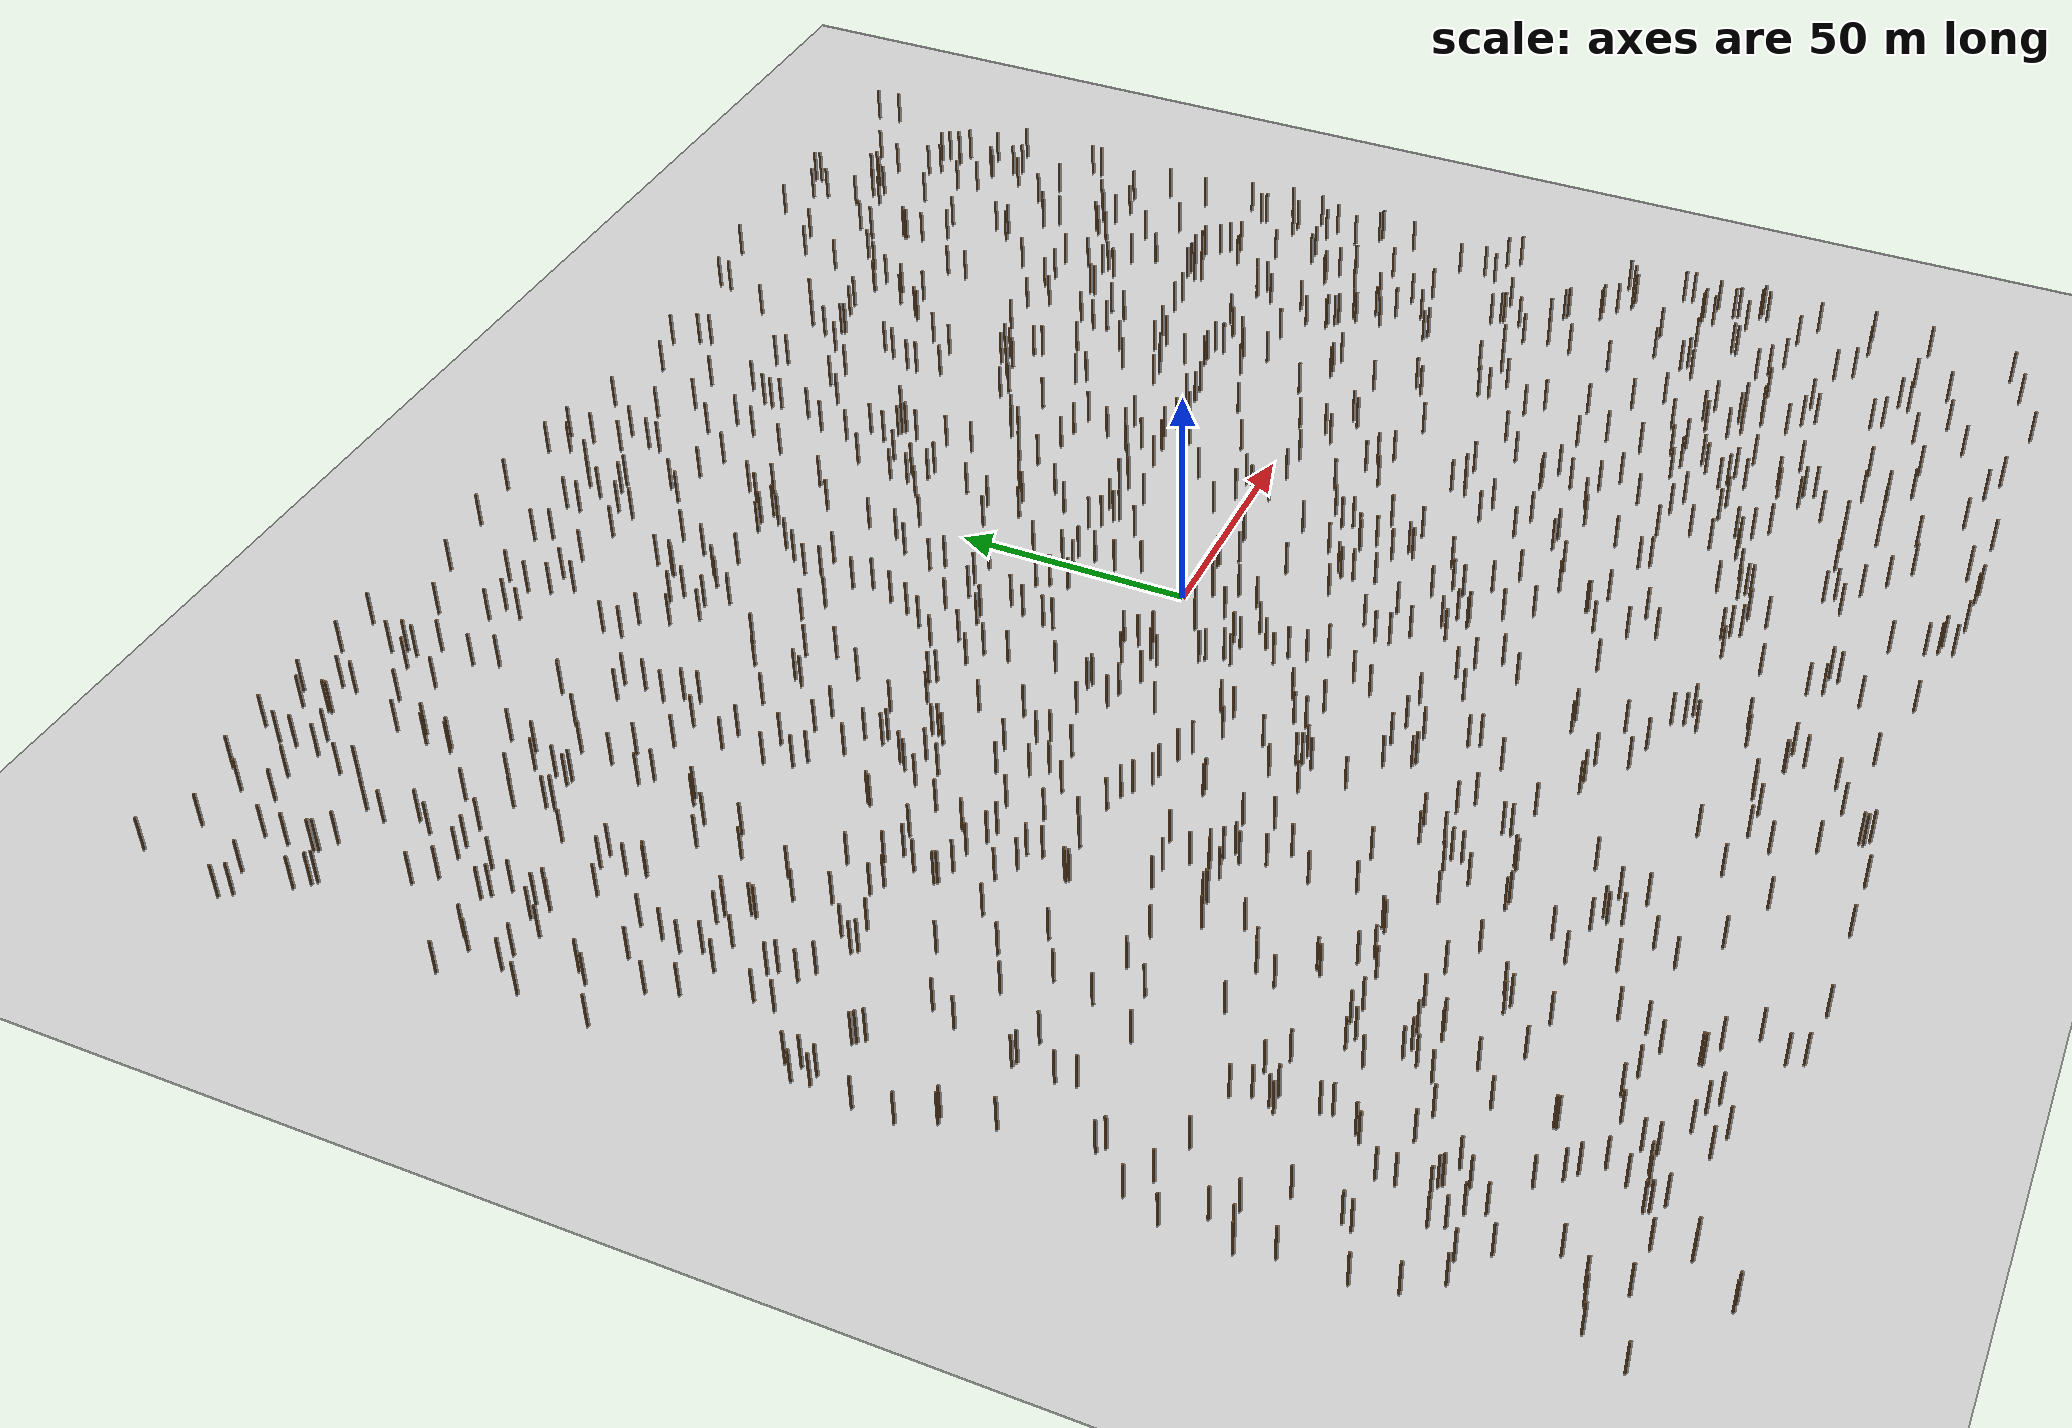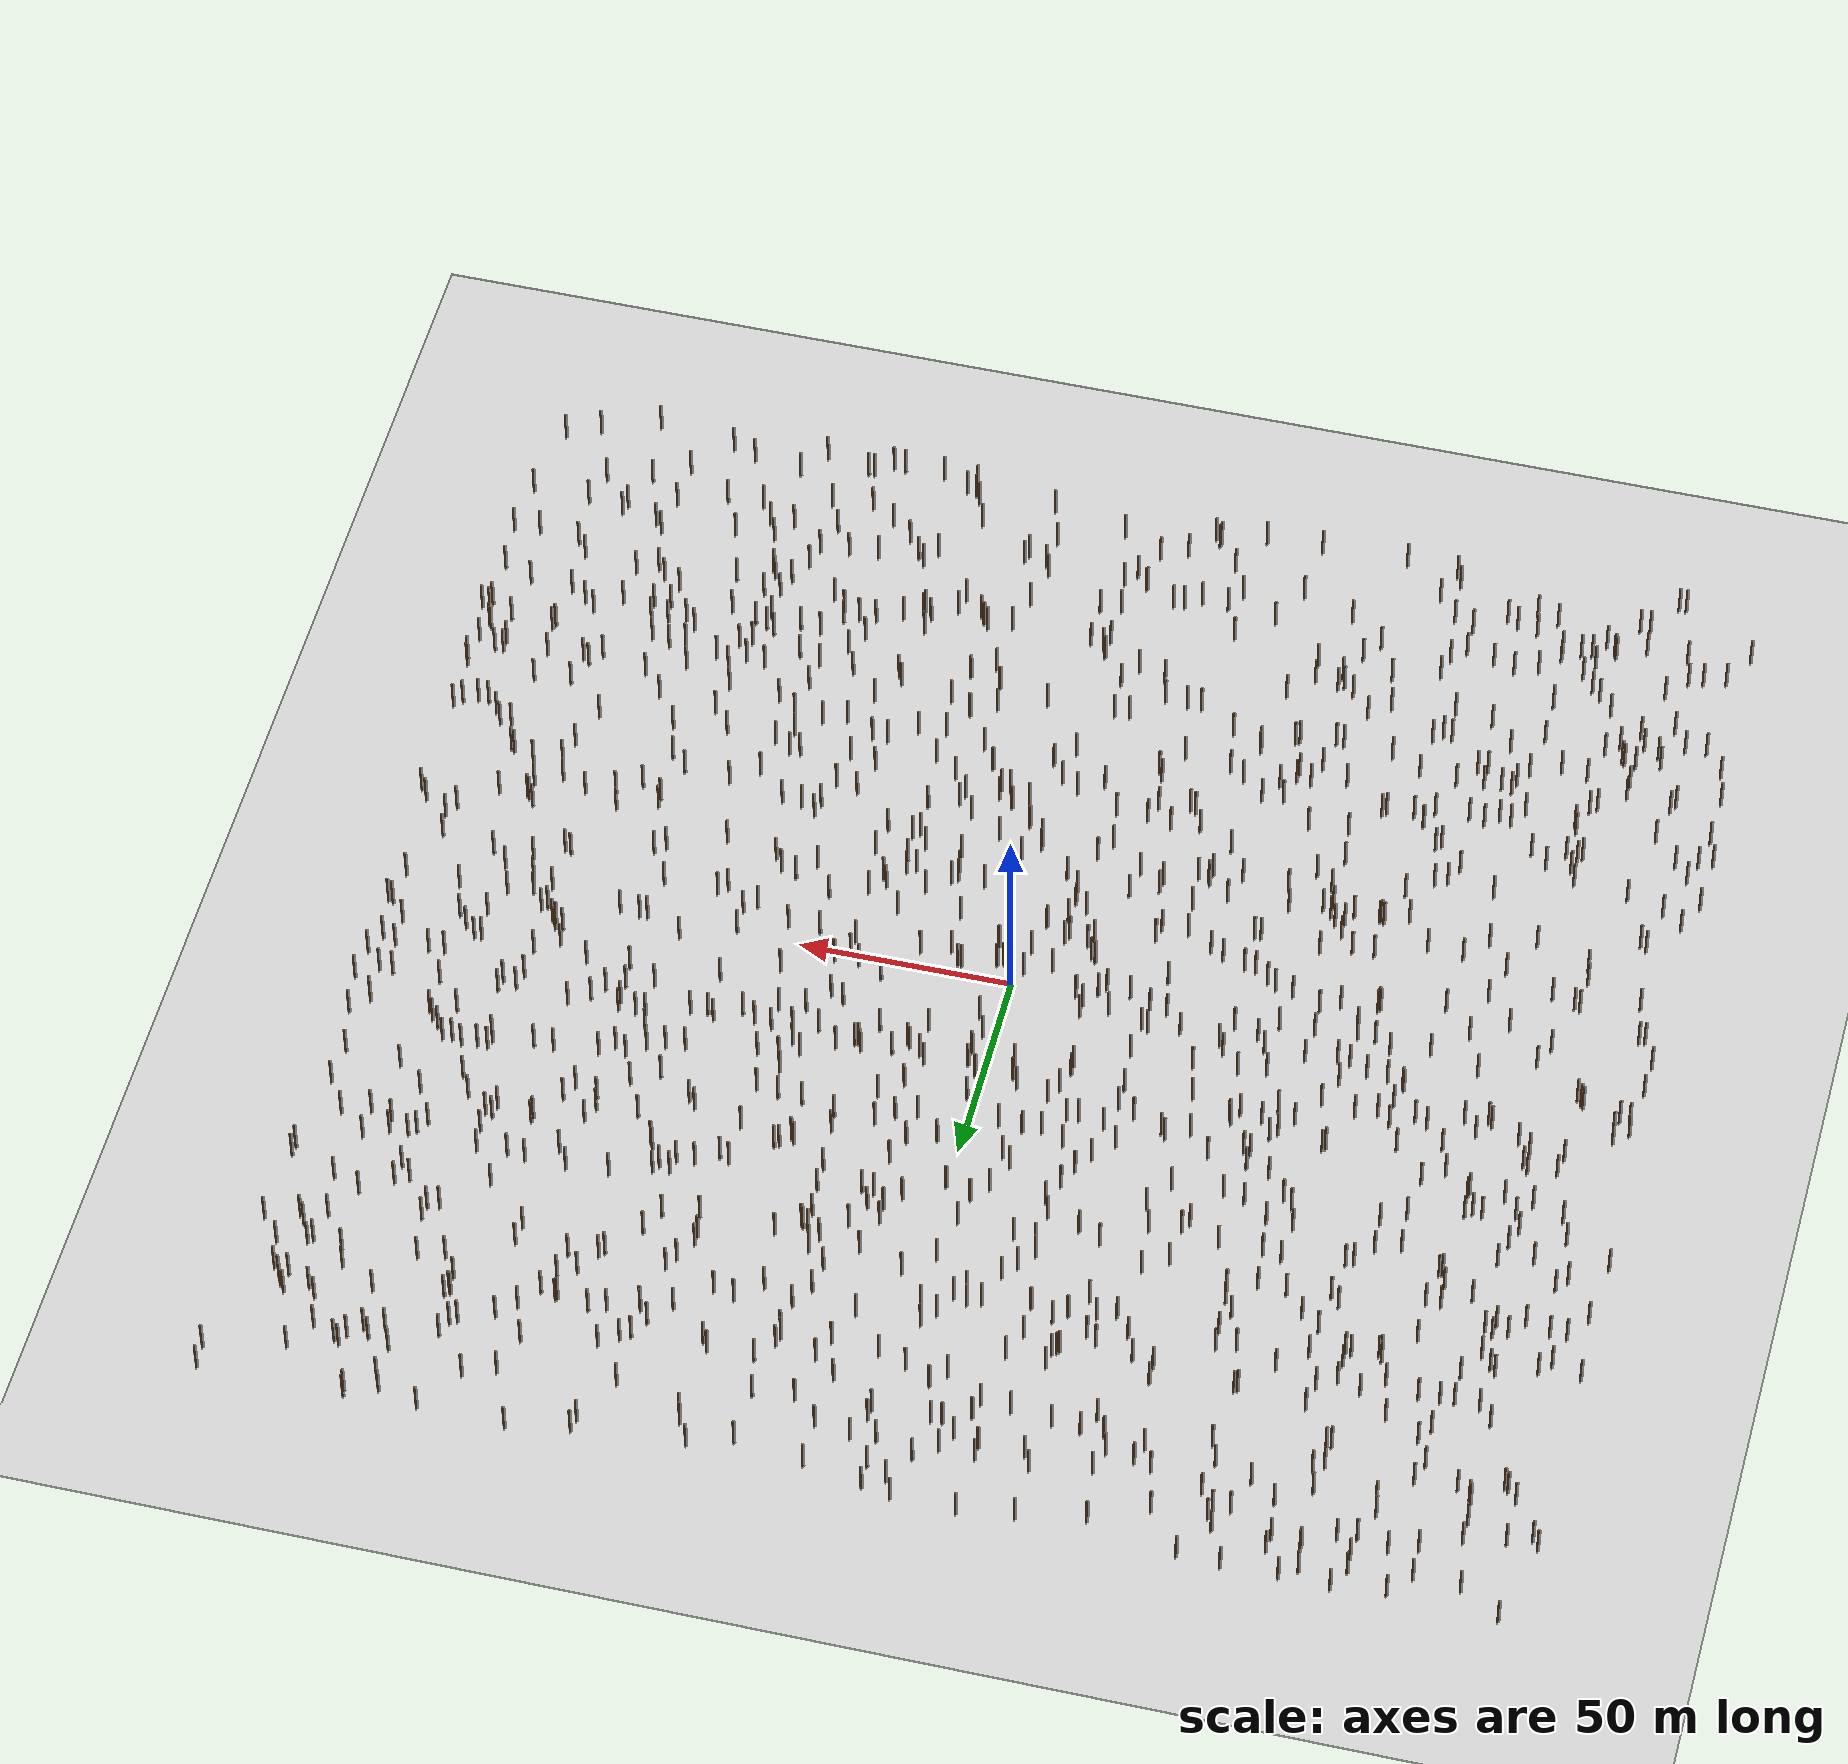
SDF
<?xml version="1.0" ?>
<sdf version="1.5">
  <world name="padure_tactica">
    <include><uri>model://sun</uri></include>
    <include><uri>model://ground_plane</uri></include>

    <model name='tree_0'>
      <static>true</static> <pose>-73.33 89.64 4.0 0 0 0</pose>
      <link name='link'>
        <collision name='collision'><geometry><cylinder><radius>0.25</radius><length>8.0</length></cylinder></geometry></collision>
        <visual name='visual'><geometry><cylinder><radius>0.25</radius><length>8.0</length></cylinder></geometry>
        <material><script><uri>file://media/materials/scripts/gazebo.material</uri><name>Gazebo/Wood</name></script></material></visual>
      </link>
    </model>

    <model name='tree_1'>
      <static>true</static> <pose>65.14 -0.28 4.0 0 0 0</pose>
      <link name='link'>
        <collision name='collision'><geometry><cylinder><radius>0.25</radius><length>8.0</length></cylinder></geometry></collision>
        <visual name='visual'><geometry><cylinder><radius>0.25</radius><length>8.0</length></cylinder></geometry>
        <material><script><uri>file://media/materials/scripts/gazebo.material</uri><name>Gazebo/Wood</name></script></material></visual>
      </link>
    </model>

    <model name='tree_2'>
      <static>true</static> <pose>-147.35 -2.47 4.0 0 0 0</pose>
      <link name='link'>
        <collision name='collision'><geometry><cylinder><radius>0.25</radius><length>8.0</length></cylinder></geometry></collision>
        <visual name='visual'><geometry><cylinder><radius>0.25</radius><length>8.0</length></cylinder></geometry>
        <material><script><uri>file://media/materials/scripts/gazebo.material</uri><name>Gazebo/Wood</name></script></material></visual>
      </link>
    </model>

    <model name='tree_3'>
      <static>true</static> <pose>61.05 68.27 4.0 0 0 0</pose>
      <link name='link'>
        <collision name='collision'><geometry><cylinder><radius>0.25</radius><length>8.0</length></cylinder></geometry></collision>
        <visual name='visual'><geometry><cylinder><radius>0.25</radius><length>8.0</length></cylinder></geometry>
        <material><script><uri>file://media/materials/scripts/gazebo.material</uri><name>Gazebo/Wood</name></script></material></visual>
      </link>
    </model>

    <model name='tree_4'>
      <static>true</static> <pose>-70.86 -2.13 4.0 0 0 0</pose>
      <link name='link'>
        <collision name='collision'><geometry><cylinder><radius>0.25</radius><length>8.0</length></cylinder></geometry></collision>
        <visual name='visual'><geometry><cylinder><radius>0.25</radius><length>8.0</length></cylinder></geometry>
        <material><script><uri>file://media/materials/scripts/gazebo.material</uri><name>Gazebo/Wood</name></script></material></visual>
      </link>
    </model>

    <model name='tree_5'>
      <static>true</static> <pose>-52.74 0.58 4.0 0 0 0</pose>
      <link name='link'>
        <collision name='collision'><geometry><cylinder><radius>0.25</radius><length>8.0</length></cylinder></geometry></collision>
        <visual name='visual'><geometry><cylinder><radius>0.25</radius><length>8.0</length></cylinder></geometry>
        <material><script><uri>file://media/materials/scripts/gazebo.material</uri><name>Gazebo/Wood</name></script></material></visual>
      </link>
    </model>

    <model name='tree_6'>
      <static>true</static> <pose>143.14 -109.33 4.0 0 0 0</pose>
      <link name='link'>
        <collision name='collision'><geometry><cylinder><radius>0.25</radius><length>8.0</length></cylinder></geometry></collision>
        <visual name='visual'><geometry><cylinder><radius>0.25</radius><length>8.0</length></cylinder></geometry>
        <material><script><uri>file://media/materials/scripts/gazebo.material</uri><name>Gazebo/Wood</name></script></material></visual>
      </link>
    </model>

    <model name='tree_7'>
      <static>true</static> <pose>-77.65 4.32 4.0 0 0 0</pose>
      <link name='link'>
        <collision name='collision'><geometry><cylinder><radius>0.25</radius><length>8.0</length></cylinder></geometry></collision>
        <visual name='visual'><geometry><cylinder><radius>0.25</radius><length>8.0</length></cylinder></geometry>
        <material><script><uri>file://media/materials/scripts/gazebo.material</uri><name>Gazebo/Wood</name></script></material></visual>
      </link>
    </model>

    <model name='tree_8'>
      <static>true</static> <pose>147.84 -84.51 4.0 0 0 0</pose>
      <link name='link'>
        <collision name='collision'><geometry><cylinder><radius>0.25</radius><length>8.0</length></cylinder></geometry></collision>
        <visual name='visual'><geometry><cylinder><radius>0.25</radius><length>8.0</length></cylinder></geometry>
        <material><script><uri>file://media/materials/scripts/gazebo.material</uri><name>Gazebo/Wood</name></script></material></visual>
      </link>
    </model>

    <model name='tree_9'>
      <static>true</static> <pose>84.58 116.29 4.0 0 0 0</pose>
      <link name='link'>
        <collision name='collision'><geometry><cylinder><radius>0.25</radius><length>8.0</length></cylinder></geometry></collision>
        <visual name='visual'><geometry><cylinder><radius>0.25</radius><length>8.0</length></cylinder></geometry>
        <material><script><uri>file://media/materials/scripts/gazebo.material</uri><name>Gazebo/Wood</name></script></material></visual>
      </link>
    </model>

    <model name='tree_10'>
      <static>true</static> <pose>133.14 -108.15 4.0 0 0 0</pose>
      <link name='link'>
        <collision name='collision'><geometry><cylinder><radius>0.25</radius><length>8.0</length></cylinder></geometry></collision>
        <visual name='visual'><geometry><cylinder><radius>0.25</radius><length>8.0</length></cylinder></geometry>
        <material><script><uri>file://media/materials/scripts/gazebo.material</uri><name>Gazebo/Wood</name></script></material></visual>
      </link>
    </model>

    <model name='tree_11'>
      <static>true</static> <pose>-99.19 116.53 4.0 0 0 0</pose>
      <link name='link'>
        <collision name='collision'><geometry><cylinder><radius>0.25</radius><length>8.0</length></cylinder></geometry></collision>
        <visual name='visual'><geometry><cylinder><radius>0.25</radius><length>8.0</length></cylinder></geometry>
        <material><script><uri>file://media/materials/scripts/gazebo.material</uri><name>Gazebo/Wood</name></script></material></visual>
      </link>
    </model>

    <model name='tree_12'>
      <static>true</static> <pose>79.79 -80.54 4.0 0 0 0</pose>
      <link name='link'>
        <collision name='collision'><geometry><cylinder><radius>0.25</radius><length>8.0</length></cylinder></geometry></collision>
        <visual name='visual'><geometry><cylinder><radius>0.25</radius><length>8.0</length></cylinder></geometry>
        <material><script><uri>file://media/materials/scripts/gazebo.material</uri><name>Gazebo/Wood</name></script></material></visual>
      </link>
    </model>

    <model name='tree_13'>
      <static>true</static> <pose>-11.43 88.28 4.0 0 0 0</pose>
      <link name='link'>
        <collision name='collision'><geometry><cylinder><radius>0.25</radius><length>8.0</length></cylinder></geometry></collision>
        <visual name='visual'><geometry><cylinder><radius>0.25</radius><length>8.0</length></cylinder></geometry>
        <material><script><uri>file://media/materials/scripts/gazebo.material</uri><name>Gazebo/Wood</name></script></material></visual>
      </link>
    </model>

    <model name='tree_14'>
      <static>true</static> <pose>-34.74 -41.05 4.0 0 0 0</pose>
      <link name='link'>
        <collision name='collision'><geometry><cylinder><radius>0.25</radius><length>8.0</length></cylinder></geometry></collision>
        <visual name='visual'><geometry><cylinder><radius>0.25</radius><length>8.0</length></cylinder></geometry>
        <material><script><uri>file://media/materials/scripts/gazebo.material</uri><name>Gazebo/Wood</name></script></material></visual>
      </link>
    </model>

    <model name='tree_15'>
      <static>true</static> <pose>-132.19 96.85 4.0 0 0 0</pose>
      <link name='link'>
        <collision name='collision'><geometry><cylinder><radius>0.25</radius><length>8.0</length></cylinder></geometry></collision>
        <visual name='visual'><geometry><cylinder><radius>0.25</radius><length>8.0</length></cylinder></geometry>
        <material><script><uri>file://media/materials/scripts/gazebo.material</uri><name>Gazebo/Wood</name></script></material></visual>
      </link>
    </model>

    <model name='tree_16'>
      <static>true</static> <pose>-6.56 96.35 4.0 0 0 0</pose>
      <link name='link'>
        <collision name='collision'><geometry><cylinder><radius>0.25</radius><length>8.0</length></cylinder></geometry></collision>
        <visual name='visual'><geometry><cylinder><radius>0.25</radius><length>8.0</length></cylinder></geometry>
        <material><script><uri>file://media/materials/scripts/gazebo.material</uri><name>Gazebo/Wood</name></script></material></visual>
      </link>
    </model>

    <model name='tree_17'>
      <static>true</static> <pose>3.98 86.76 4.0 0 0 0</pose>
      <link name='link'>
        <collision name='collision'><geometry><cylinder><radius>0.25</radius><length>8.0</length></cylinder></geometry></collision>
        <visual name='visual'><geometry><cylinder><radius>0.25</radius><length>8.0</length></cylinder></geometry>
        <material><script><uri>file://media/materials/scripts/gazebo.material</uri><name>Gazebo/Wood</name></script></material></visual>
      </link>
    </model>

    <model name='tree_18'>
      <static>true</static> <pose>110.74 4.19 4.0 0 0 0</pose>
      <link name='link'>
        <collision name='collision'><geometry><cylinder><radius>0.25</radius><length>8.0</length></cylinder></geometry></collision>
        <visual name='visual'><geometry><cylinder><radius>0.25</radius><length>8.0</length></cylinder></geometry>
        <material><script><uri>file://media/materials/scripts/gazebo.material</uri><name>Gazebo/Wood</name></script></material></visual>
      </link>
    </model>

    <model name='tree_19'>
      <static>true</static> <pose>139.20 -12.13 4.0 0 0 0</pose>
      <link name='link'>
        <collision name='collision'><geometry><cylinder><radius>0.25</radius><length>8.0</length></cylinder></geometry></collision>
        <visual name='visual'><geometry><cylinder><radius>0.25</radius><length>8.0</length></cylinder></geometry>
        <material><script><uri>file://media/materials/scripts/gazebo.material</uri><name>Gazebo/Wood</name></script></material></visual>
      </link>
    </model>

    <model name='tree_20'>
      <static>true</static> <pose>-38.30 -72.48 4.0 0 0 0</pose>
      <link name='link'>
        <collision name='collision'><geometry><cylinder><radius>0.25</radius><length>8.0</length></cylinder></geometry></collision>
        <visual name='visual'><geometry><cylinder><radius>0.25</radius><length>8.0</length></cylinder></geometry>
        <material><script><uri>file://media/materials/scripts/gazebo.material</uri><name>Gazebo/Wood</name></script></material></visual>
      </link>
    </model>

    <model name='tree_21'>
      <static>true</static> <pose>-40.96 5.01 4.0 0 0 0</pose>
      <link name='link'>
        <collision name='collision'><geometry><cylinder><radius>0.25</radius><length>8.0</length></cylinder></geometry></collision>
        <visual name='visual'><geometry><cylinder><radius>0.25</radius><length>8.0</length></cylinder></geometry>
        <material><script><uri>file://media/materials/scripts/gazebo.material</uri><name>Gazebo/Wood</name></script></material></visual>
      </link>
    </model>

    <model name='tree_22'>
      <static>true</static> <pose>-142.58 -129.13 4.0 0 0 0</pose>
      <link name='link'>
        <collision name='collision'><geometry><cylinder><radius>0.25</radius><length>8.0</length></cylinder></geometry></collision>
        <visual name='visual'><geometry><cylinder><radius>0.25</radius><length>8.0</length></cylinder></geometry>
        <material><script><uri>file://media/materials/scripts/gazebo.material</uri><name>Gazebo/Wood</name></script></material></visual>
      </link>
    </model>

    <model name='tree_23'>
      <static>true</static> <pose>-80.36 29.67 4.0 0 0 0</pose>
      <link name='link'>
        <collision name='collision'><geometry><cylinder><radius>0.25</radius><length>8.0</length></cylinder></geometry></collision>
        <visual name='visual'><geometry><cylinder><radius>0.25</radius><length>8.0</length></cylinder></geometry>
        <material><script><uri>file://media/materials/scripts/gazebo.material</uri><name>Gazebo/Wood</name></script></material></visual>
      </link>
    </model>

    <model name='tree_24'>
      <static>true</static> <pose>-29.28 -20.73 4.0 0 0 0</pose>
      <link name='link'>
        <collision name='collision'><geometry><cylinder><radius>0.25</radius><length>8.0</length></cylinder></geometry></collision>
        <visual name='visual'><geometry><cylinder><radius>0.25</radius><length>8.0</length></cylinder></geometry>
        <material><script><uri>file://media/materials/scripts/gazebo.material</uri><name>Gazebo/Wood</name></script></material></visual>
      </link>
    </model>

    <model name='tree_25'>
      <static>true</static> <pose>-22.64 59.68 4.0 0 0 0</pose>
      <link name='link'>
        <collision name='collision'><geometry><cylinder><radius>0.25</radius><length>8.0</length></cylinder></geometry></collision>
        <visual name='visual'><geometry><cylinder><radius>0.25</radius><length>8.0</length></cylinder></geometry>
        <material><script><uri>file://media/materials/scripts/gazebo.material</uri><name>Gazebo/Wood</name></script></material></visual>
      </link>
    </model>

    <model name='tree_26'>
      <static>true</static> <pose>-58.63 2.52 4.0 0 0 0</pose>
      <link name='link'>
        <collision name='collision'><geometry><cylinder><radius>0.25</radius><length>8.0</length></cylinder></geometry></collision>
        <visual name='visual'><geometry><cylinder><radius>0.25</radius><length>8.0</length></cylinder></geometry>
        <material><script><uri>file://media/materials/scripts/gazebo.material</uri><name>Gazebo/Wood</name></script></material></visual>
      </link>
    </model>

    <model name='tree_27'>
      <static>true</static> <pose>-122.47 18.02 4.0 0 0 0</pose>
      <link name='link'>
        <collision name='collision'><geometry><cylinder><radius>0.25</radius><length>8.0</length></cylinder></geometry></collision>
        <visual name='visual'><geometry><cylinder><radius>0.25</radius><length>8.0</length></cylinder></geometry>
        <material><script><uri>file://media/materials/scripts/gazebo.material</uri><name>Gazebo/Wood</name></script></material></visual>
      </link>
    </model>

    <model name='tree_28'>
      <static>true</static> <pose>-81.07 -124.14 4.0 0 0 0</pose>
      <link name='link'>
        <collision name='collision'><geometry><cylinder><radius>0.25</radius><length>8.0</length></cylinder></geometry></collision>
        <visual name='visual'><geometry><cylinder><radius>0.25</radius><length>8.0</length></cylinder></geometry>
        <material><script><uri>file://media/materials/scripts/gazebo.material</uri><name>Gazebo/Wood</name></script></material></visual>
      </link>
    </model>

    <model name='tree_29'>
      <static>true</static> <pose>78.32 148.97 4.0 0 0 0</pose>
      <link name='link'>
        <collision name='collision'><geometry><cylinder><radius>0.25</radius><length>8.0</length></cylinder></geometry></collision>
        <visual name='visual'><geometry><cylinder><radius>0.25</radius><length>8.0</length></cylinder></geometry>
        <material><script><uri>file://media/materials/scripts/gazebo.material</uri><name>Gazebo/Wood</name></script></material></visual>
      </link>
    </model>

    <model name='tree_30'>
      <static>true</static> <pose>-68.78 90.68 4.0 0 0 0</pose>
      <link name='link'>
        <collision name='collision'><geometry><cylinder><radius>0.25</radius><length>8.0</length></cylinder></geometry></collision>
        <visual name='visual'><geometry><cylinder><radius>0.25</radius><length>8.0</length></cylinder></geometry>
        <material><script><uri>file://media/materials/scripts/gazebo.material</uri><name>Gazebo/Wood</name></script></material></visual>
      </link>
    </model>

    <model name='tree_31'>
      <static>true</static> <pose>-13.41 -98.64 4.0 0 0 0</pose>
      <link name='link'>
        <collision name='collision'><geometry><cylinder><radius>0.25</radius><length>8.0</length></cylinder></geometry></collision>
        <visual name='visual'><geometry><cylinder><radius>0.25</radius><length>8.0</length></cylinder></geometry>
        <material><script><uri>file://media/materials/scripts/gazebo.material</uri><name>Gazebo/Wood</name></script></material></visual>
      </link>
    </model>

    <model name='tree_32'>
      <static>true</static> <pose>21.61 -135.15 4.0 0 0 0</pose>
      <link name='link'>
        <collision name='collision'><geometry><cylinder><radius>0.25</radius><length>8.0</length></cylinder></geometry></collision>
        <visual name='visual'><geometry><cylinder><radius>0.25</radius><length>8.0</length></cylinder></geometry>
        <material><script><uri>file://media/materials/scripts/gazebo.material</uri><name>Gazebo/Wood</name></script></material></visual>
      </link>
    </model>

    <model name='tree_33'>
      <static>true</static> <pose>26.12 108.66 4.0 0 0 0</pose>
      <link name='link'>
        <collision name='collision'><geometry><cylinder><radius>0.25</radius><length>8.0</length></cylinder></geometry></collision>
        <visual name='visual'><geometry><cylinder><radius>0.25</radius><length>8.0</length></cylinder></geometry>
        <material><script><uri>file://media/materials/scripts/gazebo.material</uri><name>Gazebo/Wood</name></script></material></visual>
      </link>
    </model>

    <model name='tree_34'>
      <static>true</static> <pose>-34.69 -75.00 4.0 0 0 0</pose>
      <link name='link'>
        <collision name='collision'><geometry><cylinder><radius>0.25</radius><length>8.0</length></cylinder></geometry></collision>
        <visual name='visual'><geometry><cylinder><radius>0.25</radius><length>8.0</length></cylinder></geometry>
        <material><script><uri>file://media/materials/scripts/gazebo.material</uri><name>Gazebo/Wood</name></script></material></visual>
      </link>
    </model>

    <model name='tree_35'>
      <static>true</static> <pose>-57.13 -14.29 4.0 0 0 0</pose>
      <link name='link'>
        <collision name='collision'><geometry><cylinder><radius>0.25</radius><length>8.0</length></cylinder></geometry></collision>
        <visual name='visual'><geometry><cylinder><radius>0.25</radius><length>8.0</length></cylinder></geometry>
        <material><script><uri>file://media/materials/scripts/gazebo.material</uri><name>Gazebo/Wood</name></script></material></visual>
      </link>
    </model>

    <model name='tree_36'>
      <static>true</static> <pose>41.94 115.94 4.0 0 0 0</pose>
      <link name='link'>
        <collision name='collision'><geometry><cylinder><radius>0.25</radius><length>8.0</length></cylinder></geometry></collision>
        <visual name='visual'><geometry><cylinder><radius>0.25</radius><length>8.0</length></cylinder></geometry>
        <material><script><uri>file://media/materials/scripts/gazebo.material</uri><name>Gazebo/Wood</name></script></material></visual>
      </link>
    </model>

    <model name='tree_37'>
      <static>true</static> <pose>60.16 119.67 4.0 0 0 0</pose>
      <link name='link'>
        <collision name='collision'><geometry><cylinder><radius>0.25</radius><length>8.0</length></cylinder></geometry></collision>
        <visual name='visual'><geometry><cylinder><radius>0.25</radius><length>8.0</length></cylinder></geometry>
        <material><script><uri>file://media/materials/scripts/gazebo.material</uri><name>Gazebo/Wood</name></script></material></visual>
      </link>
    </model>

    <model name='tree_38'>
      <static>true</static> <pose>87.08 -142.48 4.0 0 0 0</pose>
      <link name='link'>
        <collision name='collision'><geometry><cylinder><radius>0.25</radius><length>8.0</length></cylinder></geometry></collision>
        <visual name='visual'><geometry><cylinder><radius>0.25</radius><length>8.0</length></cylinder></geometry>
        <material><script><uri>file://media/materials/scripts/gazebo.material</uri><name>Gazebo/Wood</name></script></material></visual>
      </link>
    </model>

    <model name='tree_39'>
      <static>true</static> <pose>-56.97 -89.07 4.0 0 0 0</pose>
      <link name='link'>
        <collision name='collision'><geometry><cylinder><radius>0.25</radius><length>8.0</length></cylinder></geometry></collision>
        <visual name='visual'><geometry><cylinder><radius>0.25</radius><length>8.0</length></cylinder></geometry>
        <material><script><uri>file://media/materials/scripts/gazebo.material</uri><name>Gazebo/Wood</name></script></material></visual>
      </link>
    </model>

    <model name='tree_40'>
      <static>true</static> <pose>-80.03 -6.21 4.0 0 0 0</pose>
      <link name='link'>
        <collision name='collision'><geometry><cylinder><radius>0.25</radius><length>8.0</length></cylinder></geometry></collision>
        <visual name='visual'><geometry><cylinder><radius>0.25</radius><length>8.0</length></cylinder></geometry>
        <material><script><uri>file://media/materials/scripts/gazebo.material</uri><name>Gazebo/Wood</name></script></material></visual>
      </link>
    </model>

    <model name='tree_41'>
      <static>true</static> <pose>128.94 21.84 4.0 0 0 0</pose>
      <link name='link'>
        <collision name='collision'><geometry><cylinder><radius>0.25</radius><length>8.0</length></cylinder></geometry></collision>
        <visual name='visual'><geometry><cylinder><radius>0.25</radius><length>8.0</length></cylinder></geometry>
        <material><script><uri>file://media/materials/scripts/gazebo.material</uri><name>Gazebo/Wood</name></script></material></visual>
      </link>
    </model>

    <model name='tree_42'>
      <static>true</static> <pose>-76.77 17.58 4.0 0 0 0</pose>
      <link name='link'>
        <collision name='collision'><geometry><cylinder><radius>0.25</radius><length>8.0</length></cylinder></geometry></collision>
        <visual name='visual'><geometry><cylinder><radius>0.25</radius><length>8.0</length></cylinder></geometry>
        <material><script><uri>file://media/materials/scripts/gazebo.material</uri><name>Gazebo/Wood</name></script></material></visual>
      </link>
    </model>

    <model name='tree_43'>
      <static>true</static> <pose>-23.80 -92.08 4.0 0 0 0</pose>
      <link name='link'>
        <collision name='collision'><geometry><cylinder><radius>0.25</radius><length>8.0</length></cylinder></geometry></collision>
        <visual name='visual'><geometry><cylinder><radius>0.25</radius><length>8.0</length></cylinder></geometry>
        <material><script><uri>file://media/materials/scripts/gazebo.material</uri><name>Gazebo/Wood</name></script></material></visual>
      </link>
    </model>

    <model name='tree_44'>
      <static>true</static> <pose>-93.52 60.29 4.0 0 0 0</pose>
      <link name='link'>
        <collision name='collision'><geometry><cylinder><radius>0.25</radius><length>8.0</length></cylinder></geometry></collision>
        <visual name='visual'><geometry><cylinder><radius>0.25</radius><length>8.0</length></cylinder></geometry>
        <material><script><uri>file://media/materials/scripts/gazebo.material</uri><name>Gazebo/Wood</name></script></material></visual>
      </link>
    </model>

    <model name='tree_45'>
      <static>true</static> <pose>-132.42 -133.86 4.0 0 0 0</pose>
      <link name='link'>
        <collision name='collision'><geometry><cylinder><radius>0.25</radius><length>8.0</length></cylinder></geometry></collision>
        <visual name='visual'><geometry><cylinder><radius>0.25</radius><length>8.0</length></cylinder></geometry>
        <material><script><uri>file://media/materials/scripts/gazebo.material</uri><name>Gazebo/Wood</name></script></material></visual>
      </link>
    </model>

    <model name='tree_46'>
      <static>true</static> <pose>-89.89 7.35 4.0 0 0 0</pose>
      <link name='link'>
        <collision name='collision'><geometry><cylinder><radius>0.25</radius><length>8.0</length></cylinder></geometry></collision>
        <visual name='visual'><geometry><cylinder><radius>0.25</radius><length>8.0</length></cylinder></geometry>
        <material><script><uri>file://media/materials/scripts/gazebo.material</uri><name>Gazebo/Wood</name></script></material></visual>
      </link>
    </model>

    <model name='tree_47'>
      <static>true</static> <pose>38.38 102.94 4.0 0 0 0</pose>
      <link name='link'>
        <collision name='collision'><geometry><cylinder><radius>0.25</radius><length>8.0</length></cylinder></geometry></collision>
        <visual name='visual'><geometry><cylinder><radius>0.25</radius><length>8.0</length></cylinder></geometry>
        <material><script><uri>file://media/materials/scripts/gazebo.material</uri><name>Gazebo/Wood</name></script></material></visual>
      </link>
    </model>

    <model name='tree_48'>
      <static>true</static> <pose>-112.89 126.73 4.0 0 0 0</pose>
      <link name='link'>
        <collision name='collision'><geometry><cylinder><radius>0.25</radius><length>8.0</length></cylinder></geometry></collision>
        <visual name='visual'><geometry><cylinder><radius>0.25</radius><length>8.0</length></cylinder></geometry>
        <material><script><uri>file://media/materials/scripts/gazebo.material</uri><name>Gazebo/Wood</name></script></material></visual>
      </link>
    </model>

    <model name='tree_49'>
      <static>true</static> <pose>12.91 -42.04 4.0 0 0 0</pose>
      <link name='link'>
        <collision name='collision'><geometry><cylinder><radius>0.25</radius><length>8.0</length></cylinder></geometry></collision>
        <visual name='visual'><geometry><cylinder><radius>0.25</radius><length>8.0</length></cylinder></geometry>
        <material><script><uri>file://media/materials/scripts/gazebo.material</uri><name>Gazebo/Wood</name></script></material></visual>
      </link>
    </model>

    <model name='tree_50'>
      <static>true</static> <pose>77.01 112.30 4.0 0 0 0</pose>
      <link name='link'>
        <collision name='collision'><geometry><cylinder><radius>0.25</radius><length>8.0</length></cylinder></geometry></collision>
        <visual name='visual'><geometry><cylinder><radius>0.25</radius><length>8.0</length></cylinder></geometry>
        <material><script><uri>file://media/materials/scripts/gazebo.material</uri><name>Gazebo/Wood</name></script></material></visual>
      </link>
    </model>

    <model name='tree_51'>
      <static>true</static> <pose>-108.27 30.69 4.0 0 0 0</pose>
      <link name='link'>
        <collision name='collision'><geometry><cylinder><radius>0.25</radius><length>8.0</length></cylinder></geometry></collision>
        <visual name='visual'><geometry><cylinder><radius>0.25</radius><length>8.0</length></cylinder></geometry>
        <material><script><uri>file://media/materials/scripts/gazebo.material</uri><name>Gazebo/Wood</name></script></material></visual>
      </link>
    </model>

    <model name='tree_52'>
      <static>true</static> <pose>-7.11 40.73 4.0 0 0 0</pose>
      <link name='link'>
        <collision name='collision'><geometry><cylinder><radius>0.25</radius><length>8.0</length></cylinder></geometry></collision>
        <visual name='visual'><geometry><cylinder><radius>0.25</radius><length>8.0</length></cylinder></geometry>
        <material><script><uri>file://media/materials/scripts/gazebo.material</uri><name>Gazebo/Wood</name></script></material></visual>
      </link>
    </model>

    <model name='tree_53'>
      <static>true</static> <pose>54.32 24.84 4.0 0 0 0</pose>
      <link name='link'>
        <collision name='collision'><geometry><cylinder><radius>0.25</radius><length>8.0</length></cylinder></geometry></collision>
        <visual name='visual'><geometry><cylinder><radius>0.25</radius><length>8.0</length></cylinder></geometry>
        <material><script><uri>file://media/materials/scripts/gazebo.material</uri><name>Gazebo/Wood</name></script></material></visual>
      </link>
    </model>

    <model name='tree_54'>
      <static>true</static> <pose>29.75 117.97 4.0 0 0 0</pose>
      <link name='link'>
        <collision name='collision'><geometry><cylinder><radius>0.25</radius><length>8.0</length></cylinder></geometry></collision>
        <visual name='visual'><geometry><cylinder><radius>0.25</radius><length>8.0</length></cylinder></geometry>
        <material><script><uri>file://media/materials/scripts/gazebo.material</uri><name>Gazebo/Wood</name></script></material></visual>
      </link>
    </model>

    <model name='tree_55'>
      <static>true</static> <pose>-99.30 -31.85 4.0 0 0 0</pose>
      <link name='link'>
        <collision name='collision'><geometry><cylinder><radius>0.25</radius><length>8.0</length></cylinder></geometry></collision>
        <visual name='visual'><geometry><cylinder><radius>0.25</radius><length>8.0</length></cylinder></geometry>
        <material><script><uri>file://media/materials/scripts/gazebo.material</uri><name>Gazebo/Wood</name></script></material></visual>
      </link>
    </model>

    <model name='tree_56'>
      <static>true</static> <pose>69.32 25.48 4.0 0 0 0</pose>
      <link name='link'>
        <collision name='collision'><geometry><cylinder><radius>0.25</radius><length>8.0</length></cylinder></geometry></collision>
        <visual name='visual'><geometry><cylinder><radius>0.25</radius><length>8.0</length></cylinder></geometry>
        <material><script><uri>file://media/materials/scripts/gazebo.material</uri><name>Gazebo/Wood</name></script></material></visual>
      </link>
    </model>

    <model name='tree_57'>
      <static>true</static> <pose>-32.07 5.71 4.0 0 0 0</pose>
      <link name='link'>
        <collision name='collision'><geometry><cylinder><radius>0.25</radius><length>8.0</length></cylinder></geometry></collision>
        <visual name='visual'><geometry><cylinder><radius>0.25</radius><length>8.0</length></cylinder></geometry>
        <material><script><uri>file://media/materials/scripts/gazebo.material</uri><name>Gazebo/Wood</name></script></material></visual>
      </link>
    </model>

    <model name='tree_58'>
      <static>true</static> <pose>-107.53 -129.84 4.0 0 0 0</pose>
      <link name='link'>
        <collision name='collision'><geometry><cylinder><radius>0.25</radius><length>8.0</length></cylinder></geometry></collision>
        <visual name='visual'><geometry><cylinder><radius>0.25</radius><length>8.0</length></cylinder></geometry>
        <material><script><uri>file://media/materials/scripts/gazebo.material</uri><name>Gazebo/Wood</name></script></material></visual>
      </link>
    </model>

    <model name='tree_59'>
      <static>true</static> <pose>-84.79 19.02 4.0 0 0 0</pose>
      <link name='link'>
        <collision name='collision'><geometry><cylinder><radius>0.25</radius><length>8.0</length></cylinder></geometry></collision>
        <visual name='visual'><geometry><cylinder><radius>0.25</radius><length>8.0</length></cylinder></geometry>
        <material><script><uri>file://media/materials/scripts/gazebo.material</uri><name>Gazebo/Wood</name></script></material></visual>
      </link>
    </model>

    <model name='tree_60'>
      <static>true</static> <pose>41.17 138.60 4.0 0 0 0</pose>
      <link name='link'>
        <collision name='collision'><geometry><cylinder><radius>0.25</radius><length>8.0</length></cylinder></geometry></collision>
        <visual name='visual'><geometry><cylinder><radius>0.25</radius><length>8.0</length></cylinder></geometry>
        <material><script><uri>file://media/materials/scripts/gazebo.material</uri><name>Gazebo/Wood</name></script></material></visual>
      </link>
    </model>

    <model name='tree_61'>
      <static>true</static> <pose>34.10 -80.36 4.0 0 0 0</pose>
      <link name='link'>
        <collision name='collision'><geometry><cylinder><radius>0.25</radius><length>8.0</length></cylinder></geometry></collision>
        <visual name='visual'><geometry><cylinder><radius>0.25</radius><length>8.0</length></cylinder></geometry>
        <material><script><uri>file://media/materials/scripts/gazebo.material</uri><name>Gazebo/Wood</name></script></material></visual>
      </link>
    </model>

    <model name='tree_62'>
      <static>true</static> <pose>-149.11 79.88 4.0 0 0 0</pose>
      <link name='link'>
        <collision name='collision'><geometry><cylinder><radius>0.25</radius><length>8.0</length></cylinder></geometry></collision>
        <visual name='visual'><geometry><cylinder><radius>0.25</radius><length>8.0</length></cylinder></geometry>
        <material><script><uri>file://media/materials/scripts/gazebo.material</uri><name>Gazebo/Wood</name></script></material></visual>
      </link>
    </model>

    <model name='tree_63'>
      <static>true</static> <pose>-15.31 -0.07 4.0 0 0 0</pose>
      <link name='link'>
        <collision name='collision'><geometry><cylinder><radius>0.25</radius><length>8.0</length></cylinder></geometry></collision>
        <visual name='visual'><geometry><cylinder><radius>0.25</radius><length>8.0</length></cylinder></geometry>
        <material><script><uri>file://media/materials/scripts/gazebo.material</uri><name>Gazebo/Wood</name></script></material></visual>
      </link>
    </model>

    <model name='tree_64'>
      <static>true</static> <pose>137.72 122.76 4.0 0 0 0</pose>
      <link name='link'>
        <collision name='collision'><geometry><cylinder><radius>0.25</radius><length>8.0</length></cylinder></geometry></collision>
        <visual name='visual'><geometry><cylinder><radius>0.25</radius><length>8.0</length></cylinder></geometry>
        <material><script><uri>file://media/materials/scripts/gazebo.material</uri><name>Gazebo/Wood</name></script></material></visual>
      </link>
    </model>

    <model name='tree_65'>
      <static>true</static> <pose>-9.05 90.76 4.0 0 0 0</pose>
      <link name='link'>
        <collision name='collision'><geometry><cylinder><radius>0.25</radius><length>8.0</length></cylinder></geometry></collision>
        <visual name='visual'><geometry><cylinder><radius>0.25</radius><length>8.0</length></cylinder></geometry>
        <material><script><uri>file://media/materials/scripts/gazebo.material</uri><name>Gazebo/Wood</name></script></material></visual>
      </link>
    </model>

    <model name='tree_66'>
      <static>true</static> <pose>-46.84 62.08 4.0 0 0 0</pose>
      <link name='link'>
        <collision name='collision'><geometry><cylinder><radius>0.25</radius><length>8.0</length></cylinder></geometry></collision>
        <visual name='visual'><geometry><cylinder><radius>0.25</radius><length>8.0</length></cylinder></geometry>
        <material><script><uri>file://media/materials/scripts/gazebo.material</uri><name>Gazebo/Wood</name></script></material></visual>
      </link>
    </model>

    <model name='tree_67'>
      <static>true</static> <pose>-42.39 -100.87 4.0 0 0 0</pose>
      <link name='link'>
        <collision name='collision'><geometry><cylinder><radius>0.25</radius><length>8.0</length></cylinder></geometry></collision>
        <visual name='visual'><geometry><cylinder><radius>0.25</radius><length>8.0</length></cylinder></geometry>
        <material><script><uri>file://media/materials/scripts/gazebo.material</uri><name>Gazebo/Wood</name></script></material></visual>
      </link>
    </model>

    <model name='tree_68'>
      <static>true</static> <pose>53.68 95.04 4.0 0 0 0</pose>
      <link name='link'>
        <collision name='collision'><geometry><cylinder><radius>0.25</radius><length>8.0</length></cylinder></geometry></collision>
        <visual name='visual'><geometry><cylinder><radius>0.25</radius><length>8.0</length></cylinder></geometry>
        <material><script><uri>file://media/materials/scripts/gazebo.material</uri><name>Gazebo/Wood</name></script></material></visual>
      </link>
    </model>

    <model name='tree_69'>
      <static>true</static> <pose>-120.06 -68.16 4.0 0 0 0</pose>
      <link name='link'>
        <collision name='collision'><geometry><cylinder><radius>0.25</radius><length>8.0</length></cylinder></geometry></collision>
        <visual name='visual'><geometry><cylinder><radius>0.25</radius><length>8.0</length></cylinder></geometry>
        <material><script><uri>file://media/materials/scripts/gazebo.material</uri><name>Gazebo/Wood</name></script></material></visual>
      </link>
    </model>

    <model name='tree_70'>
      <static>true</static> <pose>-110.21 133.75 4.0 0 0 0</pose>
      <link name='link'>
        <collision name='collision'><geometry><cylinder><radius>0.25</radius><length>8.0</length></cylinder></geometry></collision>
        <visual name='visual'><geometry><cylinder><radius>0.25</radius><length>8.0</length></cylinder></geometry>
        <material><script><uri>file://media/materials/scripts/gazebo.material</uri><name>Gazebo/Wood</name></script></material></visual>
      </link>
    </model>

    <model name='tree_71'>
      <static>true</static> <pose>130.80 -72.16 4.0 0 0 0</pose>
      <link name='link'>
        <collision name='collision'><geometry><cylinder><radius>0.25</radius><length>8.0</length></cylinder></geometry></collision>
        <visual name='visual'><geometry><cylinder><radius>0.25</radius><length>8.0</length></cylinder></geometry>
        <material><script><uri>file://media/materials/scripts/gazebo.material</uri><name>Gazebo/Wood</name></script></material></visual>
      </link>
    </model>

    <model name='tree_72'>
      <static>true</static> <pose>-123.33 -99.41 4.0 0 0 0</pose>
      <link name='link'>
        <collision name='collision'><geometry><cylinder><radius>0.25</radius><length>8.0</length></cylinder></geometry></collision>
        <visual name='visual'><geometry><cylinder><radius>0.25</radius><length>8.0</length></cylinder></geometry>
        <material><script><uri>file://media/materials/scripts/gazebo.material</uri><name>Gazebo/Wood</name></script></material></visual>
      </link>
    </model>

    <model name='tree_73'>
      <static>true</static> <pose>-123.09 85.52 4.0 0 0 0</pose>
      <link name='link'>
        <collision name='collision'><geometry><cylinder><radius>0.25</radius><length>8.0</length></cylinder></geometry></collision>
        <visual name='visual'><geometry><cylinder><radius>0.25</radius><length>8.0</length></cylinder></geometry>
        <material><script><uri>file://media/materials/scripts/gazebo.material</uri><name>Gazebo/Wood</name></script></material></visual>
      </link>
    </model>

    <model name='tree_74'>
      <static>true</static> <pose>69.68 -146.62 4.0 0 0 0</pose>
      <link name='link'>
        <collision name='collision'><geometry><cylinder><radius>0.25</radius><length>8.0</length></cylinder></geometry></collision>
        <visual name='visual'><geometry><cylinder><radius>0.25</radius><length>8.0</length></cylinder></geometry>
        <material><script><uri>file://media/materials/scripts/gazebo.material</uri><name>Gazebo/Wood</name></script></material></visual>
      </link>
    </model>

    <model name='tree_75'>
      <static>true</static> <pose>39.30 -69.07 4.0 0 0 0</pose>
      <link name='link'>
        <collision name='collision'><geometry><cylinder><radius>0.25</radius><length>8.0</length></cylinder></geometry></collision>
        <visual name='visual'><geometry><cylinder><radius>0.25</radius><length>8.0</length></cylinder></geometry>
        <material><script><uri>file://media/materials/scripts/gazebo.material</uri><name>Gazebo/Wood</name></script></material></visual>
      </link>
    </model>

    <model name='tree_76'>
      <static>true</static> <pose>-22.87 -124.46 4.0 0 0 0</pose>
      <link name='link'>
        <collision name='collision'><geometry><cylinder><radius>0.25</radius><length>8.0</length></cylinder></geometry></collision>
        <visual name='visual'><geometry><cylinder><radius>0.25</radius><length>8.0</length></cylinder></geometry>
        <material><script><uri>file://media/materials/scripts/gazebo.material</uri><name>Gazebo/Wood</name></script></material></visual>
      </link>
    </model>

    <model name='tree_77'>
      <static>true</static> <pose>142.69 -54.30 4.0 0 0 0</pose>
      <link name='link'>
        <collision name='collision'><geometry><cylinder><radius>0.25</radius><length>8.0</length></cylinder></geometry></collision>
        <visual name='visual'><geometry><cylinder><radius>0.25</radius><length>8.0</length></cylinder></geometry>
        <material><script><uri>file://media/materials/scripts/gazebo.material</uri><name>Gazebo/Wood</name></script></material></visual>
      </link>
    </model>

    <model name='tree_78'>
      <static>true</static> <pose>109.97 -89.08 4.0 0 0 0</pose>
      <link name='link'>
        <collision name='collision'><geometry><cylinder><radius>0.25</radius><length>8.0</length></cylinder></geometry></collision>
        <visual name='visual'><geometry><cylinder><radius>0.25</radius><length>8.0</length></cylinder></geometry>
        <material><script><uri>file://media/materials/scripts/gazebo.material</uri><name>Gazebo/Wood</name></script></material></visual>
      </link>
    </model>

    <model name='tree_79'>
      <static>true</static> <pose>126.15 13.56 4.0 0 0 0</pose>
      <link name='link'>
        <collision name='collision'><geometry><cylinder><radius>0.25</radius><length>8.0</length></cylinder></geometry></collision>
        <visual name='visual'><geometry><cylinder><radius>0.25</radius><length>8.0</length></cylinder></geometry>
        <material><script><uri>file://media/materials/scripts/gazebo.material</uri><name>Gazebo/Wood</name></script></material></visual>
      </link>
    </model>

    <model name='tree_80'>
      <static>true</static> <pose>20.35 46.98 4.0 0 0 0</pose>
      <link name='link'>
        <collision name='collision'><geometry><cylinder><radius>0.25</radius><length>8.0</length></cylinder></geometry></collision>
        <visual name='visual'><geometry><cylinder><radius>0.25</radius><length>8.0</length></cylinder></geometry>
        <material><script><uri>file://media/materials/scripts/gazebo.material</uri><name>Gazebo/Wood</name></script></material></visual>
      </link>
    </model>

    <model name='tree_81'>
      <static>true</static> <pose>-115.68 -131.15 4.0 0 0 0</pose>
      <link name='link'>
        <collision name='collision'><geometry><cylinder><radius>0.25</radius><length>8.0</length></cylinder></geometry></collision>
        <visual name='visual'><geometry><cylinder><radius>0.25</radius><length>8.0</length></cylinder></geometry>
        <material><script><uri>file://media/materials/scripts/gazebo.material</uri><name>Gazebo/Wood</name></script></material></visual>
      </link>
    </model>

    <model name='tree_82'>
      <static>true</static> <pose>-59.31 -12.72 4.0 0 0 0</pose>
      <link name='link'>
        <collision name='collision'><geometry><cylinder><radius>0.25</radius><length>8.0</length></cylinder></geometry></collision>
        <visual name='visual'><geometry><cylinder><radius>0.25</radius><length>8.0</length></cylinder></geometry>
        <material><script><uri>file://media/materials/scripts/gazebo.material</uri><name>Gazebo/Wood</name></script></material></visual>
      </link>
    </model>

    <model name='tree_83'>
      <static>true</static> <pose>109.98 -2.52 4.0 0 0 0</pose>
      <link name='link'>
        <collision name='collision'><geometry><cylinder><radius>0.25</radius><length>8.0</length></cylinder></geometry></collision>
        <visual name='visual'><geometry><cylinder><radius>0.25</radius><length>8.0</length></cylinder></geometry>
        <material><script><uri>file://media/materials/scripts/gazebo.material</uri><name>Gazebo/Wood</name></script></material></visual>
      </link>
    </model>

    <model name='tree_84'>
      <static>true</static> <pose>70.87 98.27 4.0 0 0 0</pose>
      <link name='link'>
        <collision name='collision'><geometry><cylinder><radius>0.25</radius><length>8.0</length></cylinder></geometry></collision>
        <visual name='visual'><geometry><cylinder><radius>0.25</radius><length>8.0</length></cylinder></geometry>
        <material><script><uri>file://media/materials/scripts/gazebo.material</uri><name>Gazebo/Wood</name></script></material></visual>
      </link>
    </model>

    <model name='tree_85'>
      <static>true</static> <pose>-18.64 -70.57 4.0 0 0 0</pose>
      <link name='link'>
        <collision name='collision'><geometry><cylinder><radius>0.25</radius><length>8.0</length></cylinder></geometry></collision>
        <visual name='visual'><geometry><cylinder><radius>0.25</radius><length>8.0</length></cylinder></geometry>
        <material><script><uri>file://media/materials/scripts/gazebo.material</uri><name>Gazebo/Wood</name></script></material></visual>
      </link>
    </model>

    <model name='tree_86'>
      <static>true</static> <pose>38.84 -38.28 4.0 0 0 0</pose>
      <link name='link'>
        <collision name='collision'><geometry><cylinder><radius>0.25</radius><length>8.0</length></cylinder></geometry></collision>
        <visual name='visual'><geometry><cylinder><radius>0.25</radius><length>8.0</length></cylinder></geometry>
        <material><script><uri>file://media/materials/scripts/gazebo.material</uri><name>Gazebo/Wood</name></script></material></visual>
      </link>
    </model>

    <model name='tree_87'>
      <static>true</static> <pose>130.92 -41.58 4.0 0 0 0</pose>
      <link name='link'>
        <collision name='collision'><geometry><cylinder><radius>0.25</radius><length>8.0</length></cylinder></geometry></collision>
        <visual name='visual'><geometry><cylinder><radius>0.25</radius><length>8.0</length></cylinder></geometry>
        <material><script><uri>file://media/materials/scripts/gazebo.material</uri><name>Gazebo/Wood</name></script></material></visual>
      </link>
    </model>

    <model name='tree_88'>
      <static>true</static> <pose>104.37 8.63 4.0 0 0 0</pose>
      <link name='link'>
        <collision name='collision'><geometry><cylinder><radius>0.25</radius><length>8.0</length></cylinder></geometry></collision>
        <visual name='visual'><geometry><cylinder><radius>0.25</radius><length>8.0</length></cylinder></geometry>
        <material><script><uri>file://media/materials/scripts/gazebo.material</uri><name>Gazebo/Wood</name></script></material></visual>
      </link>
    </model>

    <model name='tree_89'>
      <static>true</static> <pose>-33.60 6.09 4.0 0 0 0</pose>
      <link name='link'>
        <collision name='collision'><geometry><cylinder><radius>0.25</radius><length>8.0</length></cylinder></geometry></collision>
        <visual name='visual'><geometry><cylinder><radius>0.25</radius><length>8.0</length></cylinder></geometry>
        <material><script><uri>file://media/materials/scripts/gazebo.material</uri><name>Gazebo/Wood</name></script></material></visual>
      </link>
    </model>

    <model name='tree_90'>
      <static>true</static> <pose>25.51 110.76 4.0 0 0 0</pose>
      <link name='link'>
        <collision name='collision'><geometry><cylinder><radius>0.25</radius><length>8.0</length></cylinder></geometry></collision>
        <visual name='visual'><geometry><cylinder><radius>0.25</radius><length>8.0</length></cylinder></geometry>
        <material><script><uri>file://media/materials/scripts/gazebo.material</uri><name>Gazebo/Wood</name></script></material></visual>
      </link>
    </model>

    <model name='tree_91'>
      <static>true</static> <pose>74.30 -25.92 4.0 0 0 0</pose>
      <link name='link'>
        <collision name='collision'><geometry><cylinder><radius>0.25</radius><length>8.0</length></cylinder></geometry></collision>
        <visual name='visual'><geometry><cylinder><radius>0.25</radius><length>8.0</length></cylinder></geometry>
        <material><script><uri>file://media/materials/scripts/gazebo.material</uri><name>Gazebo/Wood</name></script></material></visual>
      </link>
    </model>

    <model name='tree_92'>
      <static>true</static> <pose>138.91 103.22 4.0 0 0 0</pose>
      <link name='link'>
        <collision name='collision'><geometry><cylinder><radius>0.25</radius><length>8.0</length></cylinder></geometry></collision>
        <visual name='visual'><geometry><cylinder><radius>0.25</radius><length>8.0</length></cylinder></geometry>
        <material><script><uri>file://media/materials/scripts/gazebo.material</uri><name>Gazebo/Wood</name></script></material></visual>
      </link>
    </model>

    <model name='tree_93'>
      <static>true</static> <pose>-117.07 -75.36 4.0 0 0 0</pose>
      <link name='link'>
        <collision name='collision'><geometry><cylinder><radius>0.25</radius><length>8.0</length></cylinder></geometry></collision>
        <visual name='visual'><geometry><cylinder><radius>0.25</radius><length>8.0</length></cylinder></geometry>
        <material><script><uri>file://media/materials/scripts/gazebo.material</uri><name>Gazebo/Wood</name></script></material></visual>
      </link>
    </model>

    <model name='tree_94'>
      <static>true</static> <pose>104.10 106.70 4.0 0 0 0</pose>
      <link name='link'>
        <collision name='collision'><geometry><cylinder><radius>0.25</radius><length>8.0</length></cylinder></geometry></collision>
        <visual name='visual'><geometry><cylinder><radius>0.25</radius><length>8.0</length></cylinder></geometry>
        <material><script><uri>file://media/materials/scripts/gazebo.material</uri><name>Gazebo/Wood</name></script></material></visual>
      </link>
    </model>

    <model name='tree_95'>
      <static>true</static> <pose>123.29 -28.42 4.0 0 0 0</pose>
      <link name='link'>
        <collision name='collision'><geometry><cylinder><radius>0.25</radius><length>8.0</length></cylinder></geometry></collision>
        <visual name='visual'><geometry><cylinder><radius>0.25</radius><length>8.0</length></cylinder></geometry>
        <material><script><uri>file://media/materials/scripts/gazebo.material</uri><name>Gazebo/Wood</name></script></material></visual>
      </link>
    </model>

    <model name='tree_96'>
      <static>true</static> <pose>90.10 -125.28 4.0 0 0 0</pose>
      <link name='link'>
        <collision name='collision'><geometry><cylinder><radius>0.25</radius><length>8.0</length></cylinder></geometry></collision>
        <visual name='visual'><geometry><cylinder><radius>0.25</radius><length>8.0</length></cylinder></geometry>
        <material><script><uri>file://media/materials/scripts/gazebo.material</uri><name>Gazebo/Wood</name></script></material></visual>
      </link>
    </model>

    <model name='tree_97'>
      <static>true</static> <pose>-12.92 112.05 4.0 0 0 0</pose>
      <link name='link'>
        <collision name='collision'><geometry><cylinder><radius>0.25</radius><length>8.0</length></cylinder></geometry></collision>
        <visual name='visual'><geometry><cylinder><radius>0.25</radius><length>8.0</length></cylinder></geometry>
        <material><script><uri>file://media/materials/scripts/gazebo.material</uri><name>Gazebo/Wood</name></script></material></visual>
      </link>
    </model>

    <model name='tree_98'>
      <static>true</static> <pose>76.62 111.93 4.0 0 0 0</pose>
      <link name='link'>
        <collision name='collision'><geometry><cylinder><radius>0.25</radius><length>8.0</length></cylinder></geometry></collision>
        <visual name='visual'><geometry><cylinder><radius>0.25</radius><length>8.0</length></cylinder></geometry>
        <material><script><uri>file://media/materials/scripts/gazebo.material</uri><name>Gazebo/Wood</name></script></material></visual>
      </link>
    </model>

    <model name='tree_99'>
      <static>true</static> <pose>23.34 -114.82 4.0 0 0 0</pose>
      <link name='link'>
        <collision name='collision'><geometry><cylinder><radius>0.25</radius><length>8.0</length></cylinder></geometry></collision>
        <visual name='visual'><geometry><cylinder><radius>0.25</radius><length>8.0</length></cylinder></geometry>
        <material><script><uri>file://media/materials/scripts/gazebo.material</uri><name>Gazebo/Wood</name></script></material></visual>
      </link>
    </model>

    <model name='tree_100'>
      <static>true</static> <pose>-122.54 -134.30 4.0 0 0 0</pose>
      <link name='link'>
        <collision name='collision'><geometry><cylinder><radius>0.25</radius><length>8.0</length></cylinder></geometry></collision>
        <visual name='visual'><geometry><cylinder><radius>0.25</radius><length>8.0</length></cylinder></geometry>
        <material><script><uri>file://media/materials/scripts/gazebo.material</uri><name>Gazebo/Wood</name></script></material></visual>
      </link>
    </model>

    <model name='tree_101'>
      <static>true</static> <pose>-5.09 -34.01 4.0 0 0 0</pose>
      <link name='link'>
        <collision name='collision'><geometry><cylinder><radius>0.25</radius><length>8.0</length></cylinder></geometry></collision>
        <visual name='visual'><geometry><cylinder><radius>0.25</radius><length>8.0</length></cylinder></geometry>
        <material><script><uri>file://media/materials/scripts/gazebo.material</uri><name>Gazebo/Wood</name></script></material></visual>
      </link>
    </model>

    <model name='tree_102'>
      <static>true</static> <pose>-97.01 93.20 4.0 0 0 0</pose>
      <link name='link'>
        <collision name='collision'><geometry><cylinder><radius>0.25</radius><length>8.0</length></cylinder></geometry></collision>
        <visual name='visual'><geometry><cylinder><radius>0.25</radius><length>8.0</length></cylinder></geometry>
        <material><script><uri>file://media/materials/scripts/gazebo.material</uri><name>Gazebo/Wood</name></script></material></visual>
      </link>
    </model>

    <model name='tree_103'>
      <static>true</static> <pose>-128.33 -23.24 4.0 0 0 0</pose>
      <link name='link'>
        <collision name='collision'><geometry><cylinder><radius>0.25</radius><length>8.0</length></cylinder></geometry></collision>
        <visual name='visual'><geometry><cylinder><radius>0.25</radius><length>8.0</length></cylinder></geometry>
        <material><script><uri>file://media/materials/scripts/gazebo.material</uri><name>Gazebo/Wood</name></script></material></visual>
      </link>
    </model>

    <model name='tree_104'>
      <static>true</static> <pose>18.29 126.28 4.0 0 0 0</pose>
      <link name='link'>
        <collision name='collision'><geometry><cylinder><radius>0.25</radius><length>8.0</length></cylinder></geometry></collision>
        <visual name='visual'><geometry><cylinder><radius>0.25</radius><length>8.0</length></cylinder></geometry>
        <material><script><uri>file://media/materials/scripts/gazebo.material</uri><name>Gazebo/Wood</name></script></material></visual>
      </link>
    </model>

    <model name='tree_105'>
      <static>true</static> <pose>38.56 -18.85 4.0 0 0 0</pose>
      <link name='link'>
        <collision name='collision'><geometry><cylinder><radius>0.25</radius><length>8.0</length></cylinder></geometry></collision>
        <visual name='visual'><geometry><cylinder><radius>0.25</radius><length>8.0</length></cylinder></geometry>
        <material><script><uri>file://media/materials/scripts/gazebo.material</uri><name>Gazebo/Wood</name></script></material></visual>
      </link>
    </model>

    <model name='tree_106'>
      <static>true</static> <pose>-57.95 27.94 4.0 0 0 0</pose>
      <link name='link'>
        <collision name='collision'><geometry><cylinder><radius>0.25</radius><length>8.0</length></cylinder></geometry></collision>
        <visual name='visual'><geometry><cylinder><radius>0.25</radius><length>8.0</length></cylinder></geometry>
        <material><script><uri>file://media/materials/scripts/gazebo.material</uri><name>Gazebo/Wood</name></script></material></visual>
      </link>
    </model>

    <model name='tree_107'>
      <static>true</static> <pose>23.97 -87.21 4.0 0 0 0</pose>
      <link name='link'>
        <collision name='collision'><geometry><cylinder><radius>0.25</radius><length>8.0</length></cylinder></geometry></collision>
        <visual name='visual'><geometry><cylinder><radius>0.25</radius><length>8.0</length></cylinder></geometry>
        <material><script><uri>file://media/materials/scripts/gazebo.material</uri><name>Gazebo/Wood</name></script></material></visual>
      </link>
    </model>

    <model name='tree_108'>
      <static>true</static> <pose>-89.82 17.54 4.0 0 0 0</pose>
      <link name='link'>
        <collision name='collision'><geometry><cylinder><radius>0.25</radius><length>8.0</length></cylinder></geometry></collision>
        <visual name='visual'><geometry><cylinder><radius>0.25</radius><length>8.0</length></cylinder></geometry>
        <material><script><uri>file://media/materials/scripts/gazebo.material</uri><name>Gazebo/Wood</name></script></material></visual>
      </link>
    </model>

    <model name='tree_109'>
      <static>true</static> <pose>-141.44 -70.79 4.0 0 0 0</pose>
      <link name='link'>
        <collision name='collision'><geometry><cylinder><radius>0.25</radius><length>8.0</length></cylinder></geometry></collision>
        <visual name='visual'><geometry><cylinder><radius>0.25</radius><length>8.0</length></cylinder></geometry>
        <material><script><uri>file://media/materials/scripts/gazebo.material</uri><name>Gazebo/Wood</name></script></material></visual>
      </link>
    </model>

    <model name='tree_110'>
      <static>true</static> <pose>-77.89 133.62 4.0 0 0 0</pose>
      <link name='link'>
        <collision name='collision'><geometry><cylinder><radius>0.25</radius><length>8.0</length></cylinder></geometry></collision>
        <visual name='visual'><geometry><cylinder><radius>0.25</radius><length>8.0</length></cylinder></geometry>
        <material><script><uri>file://media/materials/scripts/gazebo.material</uri><name>Gazebo/Wood</name></script></material></visual>
      </link>
    </model>

    <model name='tree_111'>
      <static>true</static> <pose>12.36 -2.54 4.0 0 0 0</pose>
      <link name='link'>
        <collision name='collision'><geometry><cylinder><radius>0.25</radius><length>8.0</length></cylinder></geometry></collision>
        <visual name='visual'><geometry><cylinder><radius>0.25</radius><length>8.0</length></cylinder></geometry>
        <material><script><uri>file://media/materials/scripts/gazebo.material</uri><name>Gazebo/Wood</name></script></material></visual>
      </link>
    </model>

    <model name='tree_112'>
      <static>true</static> <pose>-84.78 -3.30 4.0 0 0 0</pose>
      <link name='link'>
        <collision name='collision'><geometry><cylinder><radius>0.25</radius><length>8.0</length></cylinder></geometry></collision>
        <visual name='visual'><geometry><cylinder><radius>0.25</radius><length>8.0</length></cylinder></geometry>
        <material><script><uri>file://media/materials/scripts/gazebo.material</uri><name>Gazebo/Wood</name></script></material></visual>
      </link>
    </model>

    <model name='tree_113'>
      <static>true</static> <pose>3.78 133.73 4.0 0 0 0</pose>
      <link name='link'>
        <collision name='collision'><geometry><cylinder><radius>0.25</radius><length>8.0</length></cylinder></geometry></collision>
        <visual name='visual'><geometry><cylinder><radius>0.25</radius><length>8.0</length></cylinder></geometry>
        <material><script><uri>file://media/materials/scripts/gazebo.material</uri><name>Gazebo/Wood</name></script></material></visual>
      </link>
    </model>

    <model name='tree_114'>
      <static>true</static> <pose>-127.62 42.91 4.0 0 0 0</pose>
      <link name='link'>
        <collision name='collision'><geometry><cylinder><radius>0.25</radius><length>8.0</length></cylinder></geometry></collision>
        <visual name='visual'><geometry><cylinder><radius>0.25</radius><length>8.0</length></cylinder></geometry>
        <material><script><uri>file://media/materials/scripts/gazebo.material</uri><name>Gazebo/Wood</name></script></material></visual>
      </link>
    </model>

    <model name='tree_115'>
      <static>true</static> <pose>-30.06 -23.74 4.0 0 0 0</pose>
      <link name='link'>
        <collision name='collision'><geometry><cylinder><radius>0.25</radius><length>8.0</length></cylinder></geometry></collision>
        <visual name='visual'><geometry><cylinder><radius>0.25</radius><length>8.0</length></cylinder></geometry>
        <material><script><uri>file://media/materials/scripts/gazebo.material</uri><name>Gazebo/Wood</name></script></material></visual>
      </link>
    </model>

    <model name='tree_116'>
      <static>true</static> <pose>79.14 28.60 4.0 0 0 0</pose>
      <link name='link'>
        <collision name='collision'><geometry><cylinder><radius>0.25</radius><length>8.0</length></cylinder></geometry></collision>
        <visual name='visual'><geometry><cylinder><radius>0.25</radius><length>8.0</length></cylinder></geometry>
        <material><script><uri>file://media/materials/scripts/gazebo.material</uri><name>Gazebo/Wood</name></script></material></visual>
      </link>
    </model>

    <model name='tree_117'>
      <static>true</static> <pose>85.27 -10.18 4.0 0 0 0</pose>
      <link name='link'>
        <collision name='collision'><geometry><cylinder><radius>0.25</radius><length>8.0</length></cylinder></geometry></collision>
        <visual name='visual'><geometry><cylinder><radius>0.25</radius><length>8.0</length></cylinder></geometry>
        <material><script><uri>file://media/materials/scripts/gazebo.material</uri><name>Gazebo/Wood</name></script></material></visual>
      </link>
    </model>

    <model name='tree_118'>
      <static>true</static> <pose>-121.55 -25.30 4.0 0 0 0</pose>
      <link name='link'>
        <collision name='collision'><geometry><cylinder><radius>0.25</radius><length>8.0</length></cylinder></geometry></collision>
        <visual name='visual'><geometry><cylinder><radius>0.25</radius><length>8.0</length></cylinder></geometry>
        <material><script><uri>file://media/materials/scripts/gazebo.material</uri><name>Gazebo/Wood</name></script></material></visual>
      </link>
    </model>

    <model name='tree_119'>
      <static>true</static> <pose>28.97 -77.57 4.0 0 0 0</pose>
      <link name='link'>
        <collision name='collision'><geometry><cylinder><radius>0.25</radius><length>8.0</length></cylinder></geometry></collision>
        <visual name='visual'><geometry><cylinder><radius>0.25</radius><length>8.0</length></cylinder></geometry>
        <material><script><uri>file://media/materials/scripts/gazebo.material</uri><name>Gazebo/Wood</name></script></material></visual>
      </link>
    </model>

    <model name='tree_120'>
      <static>true</static> <pose>-90.61 128.84 4.0 0 0 0</pose>
      <link name='link'>
        <collision name='collision'><geometry><cylinder><radius>0.25</radius><length>8.0</length></cylinder></geometry></collision>
        <visual name='visual'><geometry><cylinder><radius>0.25</radius><length>8.0</length></cylinder></geometry>
        <material><script><uri>file://media/materials/scripts/gazebo.material</uri><name>Gazebo/Wood</name></script></material></visual>
      </link>
    </model>

    <model name='tree_121'>
      <static>true</static> <pose>3.26 110.19 4.0 0 0 0</pose>
      <link name='link'>
        <collision name='collision'><geometry><cylinder><radius>0.25</radius><length>8.0</length></cylinder></geometry></collision>
        <visual name='visual'><geometry><cylinder><radius>0.25</radius><length>8.0</length></cylinder></geometry>
        <material><script><uri>file://media/materials/scripts/gazebo.material</uri><name>Gazebo/Wood</name></script></material></visual>
      </link>
    </model>

    <model name='tree_122'>
      <static>true</static> <pose>12.30 74.06 4.0 0 0 0</pose>
      <link name='link'>
        <collision name='collision'><geometry><cylinder><radius>0.25</radius><length>8.0</length></cylinder></geometry></collision>
        <visual name='visual'><geometry><cylinder><radius>0.25</radius><length>8.0</length></cylinder></geometry>
        <material><script><uri>file://media/materials/scripts/gazebo.material</uri><name>Gazebo/Wood</name></script></material></visual>
      </link>
    </model>

    <model name='tree_123'>
      <static>true</static> <pose>-60.89 -121.07 4.0 0 0 0</pose>
      <link name='link'>
        <collision name='collision'><geometry><cylinder><radius>0.25</radius><length>8.0</length></cylinder></geometry></collision>
        <visual name='visual'><geometry><cylinder><radius>0.25</radius><length>8.0</length></cylinder></geometry>
        <material><script><uri>file://media/materials/scripts/gazebo.material</uri><name>Gazebo/Wood</name></script></material></visual>
      </link>
    </model>

    <model name='tree_124'>
      <static>true</static> <pose>43.71 18.72 4.0 0 0 0</pose>
      <link name='link'>
        <collision name='collision'><geometry><cylinder><radius>0.25</radius><length>8.0</length></cylinder></geometry></collision>
        <visual name='visual'><geometry><cylinder><radius>0.25</radius><length>8.0</length></cylinder></geometry>
        <material><script><uri>file://media/materials/scripts/gazebo.material</uri><name>Gazebo/Wood</name></script></material></visual>
      </link>
    </model>

    <model name='tree_125'>
      <static>true</static> <pose>-50.15 129.95 4.0 0 0 0</pose>
      <link name='link'>
        <collision name='collision'><geometry><cylinder><radius>0.25</radius><length>8.0</length></cylinder></geometry></collision>
        <visual name='visual'><geometry><cylinder><radius>0.25</radius><length>8.0</length></cylinder></geometry>
        <material><script><uri>file://media/materials/scripts/gazebo.material</uri><name>Gazebo/Wood</name></script></material></visual>
      </link>
    </model>

    <model name='tree_126'>
      <static>true</static> <pose>31.52 -47.40 4.0 0 0 0</pose>
      <link name='link'>
        <collision name='collision'><geometry><cylinder><radius>0.25</radius><length>8.0</length></cylinder></geometry></collision>
        <visual name='visual'><geometry><cylinder><radius>0.25</radius><length>8.0</length></cylinder></geometry>
        <material><script><uri>file://media/materials/scripts/gazebo.material</uri><name>Gazebo/Wood</name></script></material></visual>
      </link>
    </model>

    <model name='tree_127'>
      <static>true</static> <pose>110.02 28.17 4.0 0 0 0</pose>
      <link name='link'>
        <collision name='collision'><geometry><cylinder><radius>0.25</radius><length>8.0</length></cylinder></geometry></collision>
        <visual name='visual'><geometry><cylinder><radius>0.25</radius><length>8.0</length></cylinder></geometry>
        <material><script><uri>file://media/materials/scripts/gazebo.material</uri><name>Gazebo/Wood</name></script></material></visual>
      </link>
    </model>

    <model name='tree_128'>
      <static>true</static> <pose>137.43 -51.44 4.0 0 0 0</pose>
      <link name='link'>
        <collision name='collision'><geometry><cylinder><radius>0.25</radius><length>8.0</length></cylinder></geometry></collision>
        <visual name='visual'><geometry><cylinder><radius>0.25</radius><length>8.0</length></cylinder></geometry>
        <material><script><uri>file://media/materials/scripts/gazebo.material</uri><name>Gazebo/Wood</name></script></material></visual>
      </link>
    </model>

    <model name='tree_129'>
      <static>true</static> <pose>-40.05 -83.77 4.0 0 0 0</pose>
      <link name='link'>
        <collision name='collision'><geometry><cylinder><radius>0.25</radius><length>8.0</length></cylinder></geometry></collision>
        <visual name='visual'><geometry><cylinder><radius>0.25</radius><length>8.0</length></cylinder></geometry>
        <material><script><uri>file://media/materials/scripts/gazebo.material</uri><name>Gazebo/Wood</name></script></material></visual>
      </link>
    </model>

    <model name='tree_130'>
      <static>true</static> <pose>110.44 -32.47 4.0 0 0 0</pose>
      <link name='link'>
        <collision name='collision'><geometry><cylinder><radius>0.25</radius><length>8.0</length></cylinder></geometry></collision>
        <visual name='visual'><geometry><cylinder><radius>0.25</radius><length>8.0</length></cylinder></geometry>
        <material><script><uri>file://media/materials/scripts/gazebo.material</uri><name>Gazebo/Wood</name></script></material></visual>
      </link>
    </model>

    <model name='tree_131'>
      <static>true</static> <pose>22.55 -4.33 4.0 0 0 0</pose>
      <link name='link'>
        <collision name='collision'><geometry><cylinder><radius>0.25</radius><length>8.0</length></cylinder></geometry></collision>
        <visual name='visual'><geometry><cylinder><radius>0.25</radius><length>8.0</length></cylinder></geometry>
        <material><script><uri>file://media/materials/scripts/gazebo.material</uri><name>Gazebo/Wood</name></script></material></visual>
      </link>
    </model>

    <model name='tree_132'>
      <static>true</static> <pose>138.35 -21.05 4.0 0 0 0</pose>
      <link name='link'>
        <collision name='collision'><geometry><cylinder><radius>0.25</radius><length>8.0</length></cylinder></geometry></collision>
        <visual name='visual'><geometry><cylinder><radius>0.25</radius><length>8.0</length></cylinder></geometry>
        <material><script><uri>file://media/materials/scripts/gazebo.material</uri><name>Gazebo/Wood</name></script></material></visual>
      </link>
    </model>

    <model name='tree_133'>
      <static>true</static> <pose>-45.59 87.35 4.0 0 0 0</pose>
      <link name='link'>
        <collision name='collision'><geometry><cylinder><radius>0.25</radius><length>8.0</length></cylinder></geometry></collision>
        <visual name='visual'><geometry><cylinder><radius>0.25</radius><length>8.0</length></cylinder></geometry>
        <material><script><uri>file://media/materials/scripts/gazebo.material</uri><name>Gazebo/Wood</name></script></material></visual>
      </link>
    </model>

    <model name='tree_134'>
      <static>true</static> <pose>-43.78 -67.95 4.0 0 0 0</pose>
      <link name='link'>
        <collision name='collision'><geometry><cylinder><radius>0.25</radius><length>8.0</length></cylinder></geometry></collision>
        <visual name='visual'><geometry><cylinder><radius>0.25</radius><length>8.0</length></cylinder></geometry>
        <material><script><uri>file://media/materials/scripts/gazebo.material</uri><name>Gazebo/Wood</name></script></material></visual>
      </link>
    </model>

    <model name='tree_135'>
      <static>true</static> <pose>130.05 -40.87 4.0 0 0 0</pose>
      <link name='link'>
        <collision name='collision'><geometry><cylinder><radius>0.25</radius><length>8.0</length></cylinder></geometry></collision>
        <visual name='visual'><geometry><cylinder><radius>0.25</radius><length>8.0</length></cylinder></geometry>
        <material><script><uri>file://media/materials/scripts/gazebo.material</uri><name>Gazebo/Wood</name></script></material></visual>
      </link>
    </model>

    <model name='tree_136'>
      <static>true</static> <pose>-14.92 124.84 4.0 0 0 0</pose>
      <link name='link'>
        <collision name='collision'><geometry><cylinder><radius>0.25</radius><length>8.0</length></cylinder></geometry></collision>
        <visual name='visual'><geometry><cylinder><radius>0.25</radius><length>8.0</length></cylinder></geometry>
        <material><script><uri>file://media/materials/scripts/gazebo.material</uri><name>Gazebo/Wood</name></script></material></visual>
      </link>
    </model>

    <model name='tree_137'>
      <static>true</static> <pose>-123.27 92.84 4.0 0 0 0</pose>
      <link name='link'>
        <collision name='collision'><geometry><cylinder><radius>0.25</radius><length>8.0</length></cylinder></geometry></collision>
        <visual name='visual'><geometry><cylinder><radius>0.25</radius><length>8.0</length></cylinder></geometry>
        <material><script><uri>file://media/materials/scripts/gazebo.material</uri><name>Gazebo/Wood</name></script></material></visual>
      </link>
    </model>

    <model name='tree_138'>
      <static>true</static> <pose>28.56 79.54 4.0 0 0 0</pose>
      <link name='link'>
        <collision name='collision'><geometry><cylinder><radius>0.25</radius><length>8.0</length></cylinder></geometry></collision>
        <visual name='visual'><geometry><cylinder><radius>0.25</radius><length>8.0</length></cylinder></geometry>
        <material><script><uri>file://media/materials/scripts/gazebo.material</uri><name>Gazebo/Wood</name></script></material></visual>
      </link>
    </model>

    <model name='tree_139'>
      <static>true</static> <pose>45.12 -104.53 4.0 0 0 0</pose>
      <link name='link'>
        <collision name='collision'><geometry><cylinder><radius>0.25</radius><length>8.0</length></cylinder></geometry></collision>
        <visual name='visual'><geometry><cylinder><radius>0.25</radius><length>8.0</length></cylinder></geometry>
        <material><script><uri>file://media/materials/scripts/gazebo.material</uri><name>Gazebo/Wood</name></script></material></visual>
      </link>
    </model>

    <model name='tree_140'>
      <static>true</static> <pose>129.28 124.56 4.0 0 0 0</pose>
      <link name='link'>
        <collision name='collision'><geometry><cylinder><radius>0.25</radius><length>8.0</length></cylinder></geometry></collision>
        <visual name='visual'><geometry><cylinder><radius>0.25</radius><length>8.0</length></cylinder></geometry>
        <material><script><uri>file://media/materials/scripts/gazebo.material</uri><name>Gazebo/Wood</name></script></material></visual>
      </link>
    </model>

    <model name='tree_141'>
      <static>true</static> <pose>-78.81 138.99 4.0 0 0 0</pose>
      <link name='link'>
        <collision name='collision'><geometry><cylinder><radius>0.25</radius><length>8.0</length></cylinder></geometry></collision>
        <visual name='visual'><geometry><cylinder><radius>0.25</radius><length>8.0</length></cylinder></geometry>
        <material><script><uri>file://media/materials/scripts/gazebo.material</uri><name>Gazebo/Wood</name></script></material></visual>
      </link>
    </model>

    <model name='tree_142'>
      <static>true</static> <pose>-104.43 84.11 4.0 0 0 0</pose>
      <link name='link'>
        <collision name='collision'><geometry><cylinder><radius>0.25</radius><length>8.0</length></cylinder></geometry></collision>
        <visual name='visual'><geometry><cylinder><radius>0.25</radius><length>8.0</length></cylinder></geometry>
        <material><script><uri>file://media/materials/scripts/gazebo.material</uri><name>Gazebo/Wood</name></script></material></visual>
      </link>
    </model>

    <model name='tree_143'>
      <static>true</static> <pose>18.70 22.62 4.0 0 0 0</pose>
      <link name='link'>
        <collision name='collision'><geometry><cylinder><radius>0.25</radius><length>8.0</length></cylinder></geometry></collision>
        <visual name='visual'><geometry><cylinder><radius>0.25</radius><length>8.0</length></cylinder></geometry>
        <material><script><uri>file://media/materials/scripts/gazebo.material</uri><name>Gazebo/Wood</name></script></material></visual>
      </link>
    </model>

    <model name='tree_144'>
      <static>true</static> <pose>65.26 -6.29 4.0 0 0 0</pose>
      <link name='link'>
        <collision name='collision'><geometry><cylinder><radius>0.25</radius><length>8.0</length></cylinder></geometry></collision>
        <visual name='visual'><geometry><cylinder><radius>0.25</radius><length>8.0</length></cylinder></geometry>
        <material><script><uri>file://media/materials/scripts/gazebo.material</uri><name>Gazebo/Wood</name></script></material></visual>
      </link>
    </model>

    <model name='tree_145'>
      <static>true</static> <pose>-7.04 26.79 4.0 0 0 0</pose>
      <link name='link'>
        <collision name='collision'><geometry><cylinder><radius>0.25</radius><length>8.0</length></cylinder></geometry></collision>
        <visual name='visual'><geometry><cylinder><radius>0.25</radius><length>8.0</length></cylinder></geometry>
        <material><script><uri>file://media/materials/scripts/gazebo.material</uri><name>Gazebo/Wood</name></script></material></visual>
      </link>
    </model>

    <model name='tree_146'>
      <static>true</static> <pose>108.14 145.77 4.0 0 0 0</pose>
      <link name='link'>
        <collision name='collision'><geometry><cylinder><radius>0.25</radius><length>8.0</length></cylinder></geometry></collision>
        <visual name='visual'><geometry><cylinder><radius>0.25</radius><length>8.0</length></cylinder></geometry>
        <material><script><uri>file://media/materials/scripts/gazebo.material</uri><name>Gazebo/Wood</name></script></material></visual>
      </link>
    </model>

    <model name='tree_147'>
      <static>true</static> <pose>-99.47 110.82 4.0 0 0 0</pose>
      <link name='link'>
        <collision name='collision'><geometry><cylinder><radius>0.25</radius><length>8.0</length></cylinder></geometry></collision>
        <visual name='visual'><geometry><cylinder><radius>0.25</radius><length>8.0</length></cylinder></geometry>
        <material><script><uri>file://media/materials/scripts/gazebo.material</uri><name>Gazebo/Wood</name></script></material></visual>
      </link>
    </model>

    <model name='tree_148'>
      <static>true</static> <pose>90.02 -18.72 4.0 0 0 0</pose>
      <link name='link'>
        <collision name='collision'><geometry><cylinder><radius>0.25</radius><length>8.0</length></cylinder></geometry></collision>
        <visual name='visual'><geometry><cylinder><radius>0.25</radius><length>8.0</length></cylinder></geometry>
        <material><script><uri>file://media/materials/scripts/gazebo.material</uri><name>Gazebo/Wood</name></script></material></visual>
      </link>
    </model>

    <model name='tree_149'>
      <static>true</static> <pose>62.78 50.66 4.0 0 0 0</pose>
      <link name='link'>
        <collision name='collision'><geometry><cylinder><radius>0.25</radius><length>8.0</length></cylinder></geometry></collision>
        <visual name='visual'><geometry><cylinder><radius>0.25</radius><length>8.0</length></cylinder></geometry>
        <material><script><uri>file://media/materials/scripts/gazebo.material</uri><name>Gazebo/Wood</name></script></material></visual>
      </link>
    </model>

    <model name='tree_150'>
      <static>true</static> <pose>-98.32 85.27 4.0 0 0 0</pose>
      <link name='link'>
        <collision name='collision'><geometry><cylinder><radius>0.25</radius><length>8.0</length></cylinder></geometry></collision>
        <visual name='visual'><geometry><cylinder><radius>0.25</radius><length>8.0</length></cylinder></geometry>
        <material><script><uri>file://media/materials/scripts/gazebo.material</uri><name>Gazebo/Wood</name></script></material></visual>
      </link>
    </model>

    <model name='tree_151'>
      <static>true</static> <pose>143.23 64.62 4.0 0 0 0</pose>
      <link name='link'>
        <collision name='collision'><geometry><cylinder><radius>0.25</radius><length>8.0</length></cylinder></geometry></collision>
        <visual name='visual'><geometry><cylinder><radius>0.25</radius><length>8.0</length></cylinder></geometry>
        <material><script><uri>file://media/materials/scripts/gazebo.material</uri><name>Gazebo/Wood</name></script></material></visual>
      </link>
    </model>

    <model name='tree_152'>
      <static>true</static> <pose>50.90 89.97 4.0 0 0 0</pose>
      <link name='link'>
        <collision name='collision'><geometry><cylinder><radius>0.25</radius><length>8.0</length></cylinder></geometry></collision>
        <visual name='visual'><geometry><cylinder><radius>0.25</radius><length>8.0</length></cylinder></geometry>
        <material><script><uri>file://media/materials/scripts/gazebo.material</uri><name>Gazebo/Wood</name></script></material></visual>
      </link>
    </model>

    <model name='tree_153'>
      <static>true</static> <pose>21.58 39.05 4.0 0 0 0</pose>
      <link name='link'>
        <collision name='collision'><geometry><cylinder><radius>0.25</radius><length>8.0</length></cylinder></geometry></collision>
        <visual name='visual'><geometry><cylinder><radius>0.25</radius><length>8.0</length></cylinder></geometry>
        <material><script><uri>file://media/materials/scripts/gazebo.material</uri><name>Gazebo/Wood</name></script></material></visual>
      </link>
    </model>

    <model name='tree_154'>
      <static>true</static> <pose>-117.68 105.11 4.0 0 0 0</pose>
      <link name='link'>
        <collision name='collision'><geometry><cylinder><radius>0.25</radius><length>8.0</length></cylinder></geometry></collision>
        <visual name='visual'><geometry><cylinder><radius>0.25</radius><length>8.0</length></cylinder></geometry>
        <material><script><uri>file://media/materials/scripts/gazebo.material</uri><name>Gazebo/Wood</name></script></material></visual>
      </link>
    </model>

    <model name='tree_155'>
      <static>true</static> <pose>-68.44 -34.90 4.0 0 0 0</pose>
      <link name='link'>
        <collision name='collision'><geometry><cylinder><radius>0.25</radius><length>8.0</length></cylinder></geometry></collision>
        <visual name='visual'><geometry><cylinder><radius>0.25</radius><length>8.0</length></cylinder></geometry>
        <material><script><uri>file://media/materials/scripts/gazebo.material</uri><name>Gazebo/Wood</name></script></material></visual>
      </link>
    </model>

    <model name='tree_156'>
      <static>true</static> <pose>28.74 -77.30 4.0 0 0 0</pose>
      <link name='link'>
        <collision name='collision'><geometry><cylinder><radius>0.25</radius><length>8.0</length></cylinder></geometry></collision>
        <visual name='visual'><geometry><cylinder><radius>0.25</radius><length>8.0</length></cylinder></geometry>
        <material><script><uri>file://media/materials/scripts/gazebo.material</uri><name>Gazebo/Wood</name></script></material></visual>
      </link>
    </model>

    <model name='tree_157'>
      <static>true</static> <pose>-35.30 99.56 4.0 0 0 0</pose>
      <link name='link'>
        <collision name='collision'><geometry><cylinder><radius>0.25</radius><length>8.0</length></cylinder></geometry></collision>
        <visual name='visual'><geometry><cylinder><radius>0.25</radius><length>8.0</length></cylinder></geometry>
        <material><script><uri>file://media/materials/scripts/gazebo.material</uri><name>Gazebo/Wood</name></script></material></visual>
      </link>
    </model>

    <model name='tree_158'>
      <static>true</static> <pose>-32.26 29.53 4.0 0 0 0</pose>
      <link name='link'>
        <collision name='collision'><geometry><cylinder><radius>0.25</radius><length>8.0</length></cylinder></geometry></collision>
        <visual name='visual'><geometry><cylinder><radius>0.25</radius><length>8.0</length></cylinder></geometry>
        <material><script><uri>file://media/materials/scripts/gazebo.material</uri><name>Gazebo/Wood</name></script></material></visual>
      </link>
    </model>

    <model name='tree_159'>
      <static>true</static> <pose>-82.38 -47.52 4.0 0 0 0</pose>
      <link name='link'>
        <collision name='collision'><geometry><cylinder><radius>0.25</radius><length>8.0</length></cylinder></geometry></collision>
        <visual name='visual'><geometry><cylinder><radius>0.25</radius><length>8.0</length></cylinder></geometry>
        <material><script><uri>file://media/materials/scripts/gazebo.material</uri><name>Gazebo/Wood</name></script></material></visual>
      </link>
    </model>

    <model name='tree_160'>
      <static>true</static> <pose>-149.42 -59.71 4.0 0 0 0</pose>
      <link name='link'>
        <collision name='collision'><geometry><cylinder><radius>0.25</radius><length>8.0</length></cylinder></geometry></collision>
        <visual name='visual'><geometry><cylinder><radius>0.25</radius><length>8.0</length></cylinder></geometry>
        <material><script><uri>file://media/materials/scripts/gazebo.material</uri><name>Gazebo/Wood</name></script></material></visual>
      </link>
    </model>

    <model name='tree_161'>
      <static>true</static> <pose>27.30 79.90 4.0 0 0 0</pose>
      <link name='link'>
        <collision name='collision'><geometry><cylinder><radius>0.25</radius><length>8.0</length></cylinder></geometry></collision>
        <visual name='visual'><geometry><cylinder><radius>0.25</radius><length>8.0</length></cylinder></geometry>
        <material><script><uri>file://media/materials/scripts/gazebo.material</uri><name>Gazebo/Wood</name></script></material></visual>
      </link>
    </model>

    <model name='tree_162'>
      <static>true</static> <pose>61.70 -100.44 4.0 0 0 0</pose>
      <link name='link'>
        <collision name='collision'><geometry><cylinder><radius>0.25</radius><length>8.0</length></cylinder></geometry></collision>
        <visual name='visual'><geometry><cylinder><radius>0.25</radius><length>8.0</length></cylinder></geometry>
        <material><script><uri>file://media/materials/scripts/gazebo.material</uri><name>Gazebo/Wood</name></script></material></visual>
      </link>
    </model>

    <model name='tree_163'>
      <static>true</static> <pose>-79.41 -71.31 4.0 0 0 0</pose>
      <link name='link'>
        <collision name='collision'><geometry><cylinder><radius>0.25</radius><length>8.0</length></cylinder></geometry></collision>
        <visual name='visual'><geometry><cylinder><radius>0.25</radius><length>8.0</length></cylinder></geometry>
        <material><script><uri>file://media/materials/scripts/gazebo.material</uri><name>Gazebo/Wood</name></script></material></visual>
      </link>
    </model>

    <model name='tree_164'>
      <static>true</static> <pose>146.61 105.64 4.0 0 0 0</pose>
      <link name='link'>
        <collision name='collision'><geometry><cylinder><radius>0.25</radius><length>8.0</length></cylinder></geometry></collision>
        <visual name='visual'><geometry><cylinder><radius>0.25</radius><length>8.0</length></cylinder></geometry>
        <material><script><uri>file://media/materials/scripts/gazebo.material</uri><name>Gazebo/Wood</name></script></material></visual>
      </link>
    </model>

    <model name='tree_165'>
      <static>true</static> <pose>119.80 1.09 4.0 0 0 0</pose>
      <link name='link'>
        <collision name='collision'><geometry><cylinder><radius>0.25</radius><length>8.0</length></cylinder></geometry></collision>
        <visual name='visual'><geometry><cylinder><radius>0.25</radius><length>8.0</length></cylinder></geometry>
        <material><script><uri>file://media/materials/scripts/gazebo.material</uri><name>Gazebo/Wood</name></script></material></visual>
      </link>
    </model>

    <model name='tree_166'>
      <static>true</static> <pose>-37.25 -40.88 4.0 0 0 0</pose>
      <link name='link'>
        <collision name='collision'><geometry><cylinder><radius>0.25</radius><length>8.0</length></cylinder></geometry></collision>
        <visual name='visual'><geometry><cylinder><radius>0.25</radius><length>8.0</length></cylinder></geometry>
        <material><script><uri>file://media/materials/scripts/gazebo.material</uri><name>Gazebo/Wood</name></script></material></visual>
      </link>
    </model>

    <model name='tree_167'>
      <static>true</static> <pose>56.06 -127.54 4.0 0 0 0</pose>
      <link name='link'>
        <collision name='collision'><geometry><cylinder><radius>0.25</radius><length>8.0</length></cylinder></geometry></collision>
        <visual name='visual'><geometry><cylinder><radius>0.25</radius><length>8.0</length></cylinder></geometry>
        <material><script><uri>file://media/materials/scripts/gazebo.material</uri><name>Gazebo/Wood</name></script></material></visual>
      </link>
    </model>

    <model name='tree_168'>
      <static>true</static> <pose>-111.42 67.45 4.0 0 0 0</pose>
      <link name='link'>
        <collision name='collision'><geometry><cylinder><radius>0.25</radius><length>8.0</length></cylinder></geometry></collision>
        <visual name='visual'><geometry><cylinder><radius>0.25</radius><length>8.0</length></cylinder></geometry>
        <material><script><uri>file://media/materials/scripts/gazebo.material</uri><name>Gazebo/Wood</name></script></material></visual>
      </link>
    </model>

    <model name='tree_169'>
      <static>true</static> <pose>-79.37 -38.11 4.0 0 0 0</pose>
      <link name='link'>
        <collision name='collision'><geometry><cylinder><radius>0.25</radius><length>8.0</length></cylinder></geometry></collision>
        <visual name='visual'><geometry><cylinder><radius>0.25</radius><length>8.0</length></cylinder></geometry>
        <material><script><uri>file://media/materials/scripts/gazebo.material</uri><name>Gazebo/Wood</name></script></material></visual>
      </link>
    </model>

    <model name='tree_170'>
      <static>true</static> <pose>145.55 -141.21 4.0 0 0 0</pose>
      <link name='link'>
        <collision name='collision'><geometry><cylinder><radius>0.25</radius><length>8.0</length></cylinder></geometry></collision>
        <visual name='visual'><geometry><cylinder><radius>0.25</radius><length>8.0</length></cylinder></geometry>
        <material><script><uri>file://media/materials/scripts/gazebo.material</uri><name>Gazebo/Wood</name></script></material></visual>
      </link>
    </model>

    <model name='tree_171'>
      <static>true</static> <pose>-47.95 73.56 4.0 0 0 0</pose>
      <link name='link'>
        <collision name='collision'><geometry><cylinder><radius>0.25</radius><length>8.0</length></cylinder></geometry></collision>
        <visual name='visual'><geometry><cylinder><radius>0.25</radius><length>8.0</length></cylinder></geometry>
        <material><script><uri>file://media/materials/scripts/gazebo.material</uri><name>Gazebo/Wood</name></script></material></visual>
      </link>
    </model>

    <model name='tree_172'>
      <static>true</static> <pose>122.08 -72.69 4.0 0 0 0</pose>
      <link name='link'>
        <collision name='collision'><geometry><cylinder><radius>0.25</radius><length>8.0</length></cylinder></geometry></collision>
        <visual name='visual'><geometry><cylinder><radius>0.25</radius><length>8.0</length></cylinder></geometry>
        <material><script><uri>file://media/materials/scripts/gazebo.material</uri><name>Gazebo/Wood</name></script></material></visual>
      </link>
    </model>

    <model name='tree_173'>
      <static>true</static> <pose>51.02 -120.92 4.0 0 0 0</pose>
      <link name='link'>
        <collision name='collision'><geometry><cylinder><radius>0.25</radius><length>8.0</length></cylinder></geometry></collision>
        <visual name='visual'><geometry><cylinder><radius>0.25</radius><length>8.0</length></cylinder></geometry>
        <material><script><uri>file://media/materials/scripts/gazebo.material</uri><name>Gazebo/Wood</name></script></material></visual>
      </link>
    </model>

    <model name='tree_174'>
      <static>true</static> <pose>-24.19 103.95 4.0 0 0 0</pose>
      <link name='link'>
        <collision name='collision'><geometry><cylinder><radius>0.25</radius><length>8.0</length></cylinder></geometry></collision>
        <visual name='visual'><geometry><cylinder><radius>0.25</radius><length>8.0</length></cylinder></geometry>
        <material><script><uri>file://media/materials/scripts/gazebo.material</uri><name>Gazebo/Wood</name></script></material></visual>
      </link>
    </model>

    <model name='tree_175'>
      <static>true</static> <pose>82.36 -92.47 4.0 0 0 0</pose>
      <link name='link'>
        <collision name='collision'><geometry><cylinder><radius>0.25</radius><length>8.0</length></cylinder></geometry></collision>
        <visual name='visual'><geometry><cylinder><radius>0.25</radius><length>8.0</length></cylinder></geometry>
        <material><script><uri>file://media/materials/scripts/gazebo.material</uri><name>Gazebo/Wood</name></script></material></visual>
      </link>
    </model>

    <model name='tree_176'>
      <static>true</static> <pose>-80.62 4.94 4.0 0 0 0</pose>
      <link name='link'>
        <collision name='collision'><geometry><cylinder><radius>0.25</radius><length>8.0</length></cylinder></geometry></collision>
        <visual name='visual'><geometry><cylinder><radius>0.25</radius><length>8.0</length></cylinder></geometry>
        <material><script><uri>file://media/materials/scripts/gazebo.material</uri><name>Gazebo/Wood</name></script></material></visual>
      </link>
    </model>

    <model name='tree_177'>
      <static>true</static> <pose>-83.97 -12.80 4.0 0 0 0</pose>
      <link name='link'>
        <collision name='collision'><geometry><cylinder><radius>0.25</radius><length>8.0</length></cylinder></geometry></collision>
        <visual name='visual'><geometry><cylinder><radius>0.25</radius><length>8.0</length></cylinder></geometry>
        <material><script><uri>file://media/materials/scripts/gazebo.material</uri><name>Gazebo/Wood</name></script></material></visual>
      </link>
    </model>

    <model name='tree_178'>
      <static>true</static> <pose>122.73 -27.82 4.0 0 0 0</pose>
      <link name='link'>
        <collision name='collision'><geometry><cylinder><radius>0.25</radius><length>8.0</length></cylinder></geometry></collision>
        <visual name='visual'><geometry><cylinder><radius>0.25</radius><length>8.0</length></cylinder></geometry>
        <material><script><uri>file://media/materials/scripts/gazebo.material</uri><name>Gazebo/Wood</name></script></material></visual>
      </link>
    </model>

    <model name='tree_179'>
      <static>true</static> <pose>-121.34 64.03 4.0 0 0 0</pose>
      <link name='link'>
        <collision name='collision'><geometry><cylinder><radius>0.25</radius><length>8.0</length></cylinder></geometry></collision>
        <visual name='visual'><geometry><cylinder><radius>0.25</radius><length>8.0</length></cylinder></geometry>
        <material><script><uri>file://media/materials/scripts/gazebo.material</uri><name>Gazebo/Wood</name></script></material></visual>
      </link>
    </model>

    <model name='tree_180'>
      <static>true</static> <pose>-73.15 62.40 4.0 0 0 0</pose>
      <link name='link'>
        <collision name='collision'><geometry><cylinder><radius>0.25</radius><length>8.0</length></cylinder></geometry></collision>
        <visual name='visual'><geometry><cylinder><radius>0.25</radius><length>8.0</length></cylinder></geometry>
        <material><script><uri>file://media/materials/scripts/gazebo.material</uri><name>Gazebo/Wood</name></script></material></visual>
      </link>
    </model>

    <model name='tree_181'>
      <static>true</static> <pose>67.20 -84.00 4.0 0 0 0</pose>
      <link name='link'>
        <collision name='collision'><geometry><cylinder><radius>0.25</radius><length>8.0</length></cylinder></geometry></collision>
        <visual name='visual'><geometry><cylinder><radius>0.25</radius><length>8.0</length></cylinder></geometry>
        <material><script><uri>file://media/materials/scripts/gazebo.material</uri><name>Gazebo/Wood</name></script></material></visual>
      </link>
    </model>

    <model name='tree_182'>
      <static>true</static> <pose>49.41 -64.76 4.0 0 0 0</pose>
      <link name='link'>
        <collision name='collision'><geometry><cylinder><radius>0.25</radius><length>8.0</length></cylinder></geometry></collision>
        <visual name='visual'><geometry><cylinder><radius>0.25</radius><length>8.0</length></cylinder></geometry>
        <material><script><uri>file://media/materials/scripts/gazebo.material</uri><name>Gazebo/Wood</name></script></material></visual>
      </link>
    </model>

    <model name='tree_183'>
      <static>true</static> <pose>-20.97 121.85 4.0 0 0 0</pose>
      <link name='link'>
        <collision name='collision'><geometry><cylinder><radius>0.25</radius><length>8.0</length></cylinder></geometry></collision>
        <visual name='visual'><geometry><cylinder><radius>0.25</radius><length>8.0</length></cylinder></geometry>
        <material><script><uri>file://media/materials/scripts/gazebo.material</uri><name>Gazebo/Wood</name></script></material></visual>
      </link>
    </model>

    <model name='tree_184'>
      <static>true</static> <pose>-138.71 56.84 4.0 0 0 0</pose>
      <link name='link'>
        <collision name='collision'><geometry><cylinder><radius>0.25</radius><length>8.0</length></cylinder></geometry></collision>
        <visual name='visual'><geometry><cylinder><radius>0.25</radius><length>8.0</length></cylinder></geometry>
        <material><script><uri>file://media/materials/scripts/gazebo.material</uri><name>Gazebo/Wood</name></script></material></visual>
      </link>
    </model>

    <model name='tree_185'>
      <static>true</static> <pose>-21.28 -39.26 4.0 0 0 0</pose>
      <link name='link'>
        <collision name='collision'><geometry><cylinder><radius>0.25</radius><length>8.0</length></cylinder></geometry></collision>
        <visual name='visual'><geometry><cylinder><radius>0.25</radius><length>8.0</length></cylinder></geometry>
        <material><script><uri>file://media/materials/scripts/gazebo.material</uri><name>Gazebo/Wood</name></script></material></visual>
      </link>
    </model>

    <model name='tree_186'>
      <static>true</static> <pose>115.34 148.96 4.0 0 0 0</pose>
      <link name='link'>
        <collision name='collision'><geometry><cylinder><radius>0.25</radius><length>8.0</length></cylinder></geometry></collision>
        <visual name='visual'><geometry><cylinder><radius>0.25</radius><length>8.0</length></cylinder></geometry>
        <material><script><uri>file://media/materials/scripts/gazebo.material</uri><name>Gazebo/Wood</name></script></material></visual>
      </link>
    </model>

    <model name='tree_187'>
      <static>true</static> <pose>67.85 -76.66 4.0 0 0 0</pose>
      <link name='link'>
        <collision name='collision'><geometry><cylinder><radius>0.25</radius><length>8.0</length></cylinder></geometry></collision>
        <visual name='visual'><geometry><cylinder><radius>0.25</radius><length>8.0</length></cylinder></geometry>
        <material><script><uri>file://media/materials/scripts/gazebo.material</uri><name>Gazebo/Wood</name></script></material></visual>
      </link>
    </model>

    <model name='tree_188'>
      <static>true</static> <pose>-42.78 95.93 4.0 0 0 0</pose>
      <link name='link'>
        <collision name='collision'><geometry><cylinder><radius>0.25</radius><length>8.0</length></cylinder></geometry></collision>
        <visual name='visual'><geometry><cylinder><radius>0.25</radius><length>8.0</length></cylinder></geometry>
        <material><script><uri>file://media/materials/scripts/gazebo.material</uri><name>Gazebo/Wood</name></script></material></visual>
      </link>
    </model>

    <model name='tree_189'>
      <static>true</static> <pose>104.97 65.79 4.0 0 0 0</pose>
      <link name='link'>
        <collision name='collision'><geometry><cylinder><radius>0.25</radius><length>8.0</length></cylinder></geometry></collision>
        <visual name='visual'><geometry><cylinder><radius>0.25</radius><length>8.0</length></cylinder></geometry>
        <material><script><uri>file://media/materials/scripts/gazebo.material</uri><name>Gazebo/Wood</name></script></material></visual>
      </link>
    </model>

    <model name='tree_190'>
      <static>true</static> <pose>82.01 -149.28 4.0 0 0 0</pose>
      <link name='link'>
        <collision name='collision'><geometry><cylinder><radius>0.25</radius><length>8.0</length></cylinder></geometry></collision>
        <visual name='visual'><geometry><cylinder><radius>0.25</radius><length>8.0</length></cylinder></geometry>
        <material><script><uri>file://media/materials/scripts/gazebo.material</uri><name>Gazebo/Wood</name></script></material></visual>
      </link>
    </model>

    <model name='tree_191'>
      <static>true</static> <pose>11.85 -84.72 4.0 0 0 0</pose>
      <link name='link'>
        <collision name='collision'><geometry><cylinder><radius>0.25</radius><length>8.0</length></cylinder></geometry></collision>
        <visual name='visual'><geometry><cylinder><radius>0.25</radius><length>8.0</length></cylinder></geometry>
        <material><script><uri>file://media/materials/scripts/gazebo.material</uri><name>Gazebo/Wood</name></script></material></visual>
      </link>
    </model>

    <model name='tree_192'>
      <static>true</static> <pose>-67.05 -36.95 4.0 0 0 0</pose>
      <link name='link'>
        <collision name='collision'><geometry><cylinder><radius>0.25</radius><length>8.0</length></cylinder></geometry></collision>
        <visual name='visual'><geometry><cylinder><radius>0.25</radius><length>8.0</length></cylinder></geometry>
        <material><script><uri>file://media/materials/scripts/gazebo.material</uri><name>Gazebo/Wood</name></script></material></visual>
      </link>
    </model>

    <model name='tree_193'>
      <static>true</static> <pose>-8.93 -26.82 4.0 0 0 0</pose>
      <link name='link'>
        <collision name='collision'><geometry><cylinder><radius>0.25</radius><length>8.0</length></cylinder></geometry></collision>
        <visual name='visual'><geometry><cylinder><radius>0.25</radius><length>8.0</length></cylinder></geometry>
        <material><script><uri>file://media/materials/scripts/gazebo.material</uri><name>Gazebo/Wood</name></script></material></visual>
      </link>
    </model>

    <model name='tree_194'>
      <static>true</static> <pose>96.05 64.82 4.0 0 0 0</pose>
      <link name='link'>
        <collision name='collision'><geometry><cylinder><radius>0.25</radius><length>8.0</length></cylinder></geometry></collision>
        <visual name='visual'><geometry><cylinder><radius>0.25</radius><length>8.0</length></cylinder></geometry>
        <material><script><uri>file://media/materials/scripts/gazebo.material</uri><name>Gazebo/Wood</name></script></material></visual>
      </link>
    </model>

    <model name='tree_195'>
      <static>true</static> <pose>22.06 96.37 4.0 0 0 0</pose>
      <link name='link'>
        <collision name='collision'><geometry><cylinder><radius>0.25</radius><length>8.0</length></cylinder></geometry></collision>
        <visual name='visual'><geometry><cylinder><radius>0.25</radius><length>8.0</length></cylinder></geometry>
        <material><script><uri>file://media/materials/scripts/gazebo.material</uri><name>Gazebo/Wood</name></script></material></visual>
      </link>
    </model>

    <model name='tree_196'>
      <static>true</static> <pose>80.26 -91.05 4.0 0 0 0</pose>
      <link name='link'>
        <collision name='collision'><geometry><cylinder><radius>0.25</radius><length>8.0</length></cylinder></geometry></collision>
        <visual name='visual'><geometry><cylinder><radius>0.25</radius><length>8.0</length></cylinder></geometry>
        <material><script><uri>file://media/materials/scripts/gazebo.material</uri><name>Gazebo/Wood</name></script></material></visual>
      </link>
    </model>

    <model name='tree_197'>
      <static>true</static> <pose>-92.99 20.03 4.0 0 0 0</pose>
      <link name='link'>
        <collision name='collision'><geometry><cylinder><radius>0.25</radius><length>8.0</length></cylinder></geometry></collision>
        <visual name='visual'><geometry><cylinder><radius>0.25</radius><length>8.0</length></cylinder></geometry>
        <material><script><uri>file://media/materials/scripts/gazebo.material</uri><name>Gazebo/Wood</name></script></material></visual>
      </link>
    </model>

    <model name='tree_198'>
      <static>true</static> <pose>82.17 -96.22 4.0 0 0 0</pose>
      <link name='link'>
        <collision name='collision'><geometry><cylinder><radius>0.25</radius><length>8.0</length></cylinder></geometry></collision>
        <visual name='visual'><geometry><cylinder><radius>0.25</radius><length>8.0</length></cylinder></geometry>
        <material><script><uri>file://media/materials/scripts/gazebo.material</uri><name>Gazebo/Wood</name></script></material></visual>
      </link>
    </model>

    <model name='tree_199'>
      <static>true</static> <pose>-93.37 -88.83 4.0 0 0 0</pose>
      <link name='link'>
        <collision name='collision'><geometry><cylinder><radius>0.25</radius><length>8.0</length></cylinder></geometry></collision>
        <visual name='visual'><geometry><cylinder><radius>0.25</radius><length>8.0</length></cylinder></geometry>
        <material><script><uri>file://media/materials/scripts/gazebo.material</uri><name>Gazebo/Wood</name></script></material></visual>
      </link>
    </model>

    <model name='tree_200'>
      <static>true</static> <pose>96.79 43.53 4.0 0 0 0</pose>
      <link name='link'>
        <collision name='collision'><geometry><cylinder><radius>0.25</radius><length>8.0</length></cylinder></geometry></collision>
        <visual name='visual'><geometry><cylinder><radius>0.25</radius><length>8.0</length></cylinder></geometry>
        <material><script><uri>file://media/materials/scripts/gazebo.material</uri><name>Gazebo/Wood</name></script></material></visual>
      </link>
    </model>

    <model name='tree_201'>
      <static>true</static> <pose>-78.07 -84.09 4.0 0 0 0</pose>
      <link name='link'>
        <collision name='collision'><geometry><cylinder><radius>0.25</radius><length>8.0</length></cylinder></geometry></collision>
        <visual name='visual'><geometry><cylinder><radius>0.25</radius><length>8.0</length></cylinder></geometry>
        <material><script><uri>file://media/materials/scripts/gazebo.material</uri><name>Gazebo/Wood</name></script></material></visual>
      </link>
    </model>

    <model name='tree_202'>
      <static>true</static> <pose>-122.04 -103.68 4.0 0 0 0</pose>
      <link name='link'>
        <collision name='collision'><geometry><cylinder><radius>0.25</radius><length>8.0</length></cylinder></geometry></collision>
        <visual name='visual'><geometry><cylinder><radius>0.25</radius><length>8.0</length></cylinder></geometry>
        <material><script><uri>file://media/materials/scripts/gazebo.material</uri><name>Gazebo/Wood</name></script></material></visual>
      </link>
    </model>

    <model name='tree_203'>
      <static>true</static> <pose>-125.41 20.13 4.0 0 0 0</pose>
      <link name='link'>
        <collision name='collision'><geometry><cylinder><radius>0.25</radius><length>8.0</length></cylinder></geometry></collision>
        <visual name='visual'><geometry><cylinder><radius>0.25</radius><length>8.0</length></cylinder></geometry>
        <material><script><uri>file://media/materials/scripts/gazebo.material</uri><name>Gazebo/Wood</name></script></material></visual>
      </link>
    </model>

    <model name='tree_204'>
      <static>true</static> <pose>-117.88 -113.12 4.0 0 0 0</pose>
      <link name='link'>
        <collision name='collision'><geometry><cylinder><radius>0.25</radius><length>8.0</length></cylinder></geometry></collision>
        <visual name='visual'><geometry><cylinder><radius>0.25</radius><length>8.0</length></cylinder></geometry>
        <material><script><uri>file://media/materials/scripts/gazebo.material</uri><name>Gazebo/Wood</name></script></material></visual>
      </link>
    </model>

    <model name='tree_205'>
      <static>true</static> <pose>14.05 -56.67 4.0 0 0 0</pose>
      <link name='link'>
        <collision name='collision'><geometry><cylinder><radius>0.25</radius><length>8.0</length></cylinder></geometry></collision>
        <visual name='visual'><geometry><cylinder><radius>0.25</radius><length>8.0</length></cylinder></geometry>
        <material><script><uri>file://media/materials/scripts/gazebo.material</uri><name>Gazebo/Wood</name></script></material></visual>
      </link>
    </model>

    <model name='tree_206'>
      <static>true</static> <pose>1.70 -117.73 4.0 0 0 0</pose>
      <link name='link'>
        <collision name='collision'><geometry><cylinder><radius>0.25</radius><length>8.0</length></cylinder></geometry></collision>
        <visual name='visual'><geometry><cylinder><radius>0.25</radius><length>8.0</length></cylinder></geometry>
        <material><script><uri>file://media/materials/scripts/gazebo.material</uri><name>Gazebo/Wood</name></script></material></visual>
      </link>
    </model>

    <model name='tree_207'>
      <static>true</static> <pose>-67.55 74.17 4.0 0 0 0</pose>
      <link name='link'>
        <collision name='collision'><geometry><cylinder><radius>0.25</radius><length>8.0</length></cylinder></geometry></collision>
        <visual name='visual'><geometry><cylinder><radius>0.25</radius><length>8.0</length></cylinder></geometry>
        <material><script><uri>file://media/materials/scripts/gazebo.material</uri><name>Gazebo/Wood</name></script></material></visual>
      </link>
    </model>

    <model name='tree_208'>
      <static>true</static> <pose>-70.17 81.03 4.0 0 0 0</pose>
      <link name='link'>
        <collision name='collision'><geometry><cylinder><radius>0.25</radius><length>8.0</length></cylinder></geometry></collision>
        <visual name='visual'><geometry><cylinder><radius>0.25</radius><length>8.0</length></cylinder></geometry>
        <material><script><uri>file://media/materials/scripts/gazebo.material</uri><name>Gazebo/Wood</name></script></material></visual>
      </link>
    </model>

    <model name='tree_209'>
      <static>true</static> <pose>-9.07 -15.08 4.0 0 0 0</pose>
      <link name='link'>
        <collision name='collision'><geometry><cylinder><radius>0.25</radius><length>8.0</length></cylinder></geometry></collision>
        <visual name='visual'><geometry><cylinder><radius>0.25</radius><length>8.0</length></cylinder></geometry>
        <material><script><uri>file://media/materials/scripts/gazebo.material</uri><name>Gazebo/Wood</name></script></material></visual>
      </link>
    </model>

    <model name='tree_210'>
      <static>true</static> <pose>-1.75 140.17 4.0 0 0 0</pose>
      <link name='link'>
        <collision name='collision'><geometry><cylinder><radius>0.25</radius><length>8.0</length></cylinder></geometry></collision>
        <visual name='visual'><geometry><cylinder><radius>0.25</radius><length>8.0</length></cylinder></geometry>
        <material><script><uri>file://media/materials/scripts/gazebo.material</uri><name>Gazebo/Wood</name></script></material></visual>
      </link>
    </model>

    <model name='tree_211'>
      <static>true</static> <pose>26.07 -92.70 4.0 0 0 0</pose>
      <link name='link'>
        <collision name='collision'><geometry><cylinder><radius>0.25</radius><length>8.0</length></cylinder></geometry></collision>
        <visual name='visual'><geometry><cylinder><radius>0.25</radius><length>8.0</length></cylinder></geometry>
        <material><script><uri>file://media/materials/scripts/gazebo.material</uri><name>Gazebo/Wood</name></script></material></visual>
      </link>
    </model>

    <model name='tree_212'>
      <static>true</static> <pose>120.30 73.95 4.0 0 0 0</pose>
      <link name='link'>
        <collision name='collision'><geometry><cylinder><radius>0.25</radius><length>8.0</length></cylinder></geometry></collision>
        <visual name='visual'><geometry><cylinder><radius>0.25</radius><length>8.0</length></cylinder></geometry>
        <material><script><uri>file://media/materials/scripts/gazebo.material</uri><name>Gazebo/Wood</name></script></material></visual>
      </link>
    </model>

    <model name='tree_213'>
      <static>true</static> <pose>126.78 72.15 4.0 0 0 0</pose>
      <link name='link'>
        <collision name='collision'><geometry><cylinder><radius>0.25</radius><length>8.0</length></cylinder></geometry></collision>
        <visual name='visual'><geometry><cylinder><radius>0.25</radius><length>8.0</length></cylinder></geometry>
        <material><script><uri>file://media/materials/scripts/gazebo.material</uri><name>Gazebo/Wood</name></script></material></visual>
      </link>
    </model>

    <model name='tree_214'>
      <static>true</static> <pose>-72.94 -70.78 4.0 0 0 0</pose>
      <link name='link'>
        <collision name='collision'><geometry><cylinder><radius>0.25</radius><length>8.0</length></cylinder></geometry></collision>
        <visual name='visual'><geometry><cylinder><radius>0.25</radius><length>8.0</length></cylinder></geometry>
        <material><script><uri>file://media/materials/scripts/gazebo.material</uri><name>Gazebo/Wood</name></script></material></visual>
      </link>
    </model>

    <model name='tree_215'>
      <static>true</static> <pose>-45.66 -18.62 4.0 0 0 0</pose>
      <link name='link'>
        <collision name='collision'><geometry><cylinder><radius>0.25</radius><length>8.0</length></cylinder></geometry></collision>
        <visual name='visual'><geometry><cylinder><radius>0.25</radius><length>8.0</length></cylinder></geometry>
        <material><script><uri>file://media/materials/scripts/gazebo.material</uri><name>Gazebo/Wood</name></script></material></visual>
      </link>
    </model>

    <model name='tree_216'>
      <static>true</static> <pose>-123.84 133.55 4.0 0 0 0</pose>
      <link name='link'>
        <collision name='collision'><geometry><cylinder><radius>0.25</radius><length>8.0</length></cylinder></geometry></collision>
        <visual name='visual'><geometry><cylinder><radius>0.25</radius><length>8.0</length></cylinder></geometry>
        <material><script><uri>file://media/materials/scripts/gazebo.material</uri><name>Gazebo/Wood</name></script></material></visual>
      </link>
    </model>

    <model name='tree_217'>
      <static>true</static> <pose>2.97 -126.51 4.0 0 0 0</pose>
      <link name='link'>
        <collision name='collision'><geometry><cylinder><radius>0.25</radius><length>8.0</length></cylinder></geometry></collision>
        <visual name='visual'><geometry><cylinder><radius>0.25</radius><length>8.0</length></cylinder></geometry>
        <material><script><uri>file://media/materials/scripts/gazebo.material</uri><name>Gazebo/Wood</name></script></material></visual>
      </link>
    </model>

    <model name='tree_218'>
      <static>true</static> <pose>125.57 -120.15 4.0 0 0 0</pose>
      <link name='link'>
        <collision name='collision'><geometry><cylinder><radius>0.25</radius><length>8.0</length></cylinder></geometry></collision>
        <visual name='visual'><geometry><cylinder><radius>0.25</radius><length>8.0</length></cylinder></geometry>
        <material><script><uri>file://media/materials/scripts/gazebo.material</uri><name>Gazebo/Wood</name></script></material></visual>
      </link>
    </model>

    <model name='tree_219'>
      <static>true</static> <pose>6.62 -37.26 4.0 0 0 0</pose>
      <link name='link'>
        <collision name='collision'><geometry><cylinder><radius>0.25</radius><length>8.0</length></cylinder></geometry></collision>
        <visual name='visual'><geometry><cylinder><radius>0.25</radius><length>8.0</length></cylinder></geometry>
        <material><script><uri>file://media/materials/scripts/gazebo.material</uri><name>Gazebo/Wood</name></script></material></visual>
      </link>
    </model>

    <model name='tree_220'>
      <static>true</static> <pose>46.54 -146.29 4.0 0 0 0</pose>
      <link name='link'>
        <collision name='collision'><geometry><cylinder><radius>0.25</radius><length>8.0</length></cylinder></geometry></collision>
        <visual name='visual'><geometry><cylinder><radius>0.25</radius><length>8.0</length></cylinder></geometry>
        <material><script><uri>file://media/materials/scripts/gazebo.material</uri><name>Gazebo/Wood</name></script></material></visual>
      </link>
    </model>

    <model name='tree_221'>
      <static>true</static> <pose>4.46 -4.79 4.0 0 0 0</pose>
      <link name='link'>
        <collision name='collision'><geometry><cylinder><radius>0.25</radius><length>8.0</length></cylinder></geometry></collision>
        <visual name='visual'><geometry><cylinder><radius>0.25</radius><length>8.0</length></cylinder></geometry>
        <material><script><uri>file://media/materials/scripts/gazebo.material</uri><name>Gazebo/Wood</name></script></material></visual>
      </link>
    </model>

    <model name='tree_222'>
      <static>true</static> <pose>-72.25 -38.35 4.0 0 0 0</pose>
      <link name='link'>
        <collision name='collision'><geometry><cylinder><radius>0.25</radius><length>8.0</length></cylinder></geometry></collision>
        <visual name='visual'><geometry><cylinder><radius>0.25</radius><length>8.0</length></cylinder></geometry>
        <material><script><uri>file://media/materials/scripts/gazebo.material</uri><name>Gazebo/Wood</name></script></material></visual>
      </link>
    </model>

    <model name='tree_223'>
      <static>true</static> <pose>-95.06 -139.71 4.0 0 0 0</pose>
      <link name='link'>
        <collision name='collision'><geometry><cylinder><radius>0.25</radius><length>8.0</length></cylinder></geometry></collision>
        <visual name='visual'><geometry><cylinder><radius>0.25</radius><length>8.0</length></cylinder></geometry>
        <material><script><uri>file://media/materials/scripts/gazebo.material</uri><name>Gazebo/Wood</name></script></material></visual>
      </link>
    </model>

    <model name='tree_224'>
      <static>true</static> <pose>67.33 65.92 4.0 0 0 0</pose>
      <link name='link'>
        <collision name='collision'><geometry><cylinder><radius>0.25</radius><length>8.0</length></cylinder></geometry></collision>
        <visual name='visual'><geometry><cylinder><radius>0.25</radius><length>8.0</length></cylinder></geometry>
        <material><script><uri>file://media/materials/scripts/gazebo.material</uri><name>Gazebo/Wood</name></script></material></visual>
      </link>
    </model>

    <model name='tree_225'>
      <static>true</static> <pose>-15.68 -17.07 4.0 0 0 0</pose>
      <link name='link'>
        <collision name='collision'><geometry><cylinder><radius>0.25</radius><length>8.0</length></cylinder></geometry></collision>
        <visual name='visual'><geometry><cylinder><radius>0.25</radius><length>8.0</length></cylinder></geometry>
        <material><script><uri>file://media/materials/scripts/gazebo.material</uri><name>Gazebo/Wood</name></script></material></visual>
      </link>
    </model>

    <model name='tree_226'>
      <static>true</static> <pose>32.64 98.08 4.0 0 0 0</pose>
      <link name='link'>
        <collision name='collision'><geometry><cylinder><radius>0.25</radius><length>8.0</length></cylinder></geometry></collision>
        <visual name='visual'><geometry><cylinder><radius>0.25</radius><length>8.0</length></cylinder></geometry>
        <material><script><uri>file://media/materials/scripts/gazebo.material</uri><name>Gazebo/Wood</name></script></material></visual>
      </link>
    </model>

    <model name='tree_227'>
      <static>true</static> <pose>132.94 101.59 4.0 0 0 0</pose>
      <link name='link'>
        <collision name='collision'><geometry><cylinder><radius>0.25</radius><length>8.0</length></cylinder></geometry></collision>
        <visual name='visual'><geometry><cylinder><radius>0.25</radius><length>8.0</length></cylinder></geometry>
        <material><script><uri>file://media/materials/scripts/gazebo.material</uri><name>Gazebo/Wood</name></script></material></visual>
      </link>
    </model>

    <model name='tree_228'>
      <static>true</static> <pose>-114.32 35.80 4.0 0 0 0</pose>
      <link name='link'>
        <collision name='collision'><geometry><cylinder><radius>0.25</radius><length>8.0</length></cylinder></geometry></collision>
        <visual name='visual'><geometry><cylinder><radius>0.25</radius><length>8.0</length></cylinder></geometry>
        <material><script><uri>file://media/materials/scripts/gazebo.material</uri><name>Gazebo/Wood</name></script></material></visual>
      </link>
    </model>

    <model name='tree_229'>
      <static>true</static> <pose>15.61 -6.13 4.0 0 0 0</pose>
      <link name='link'>
        <collision name='collision'><geometry><cylinder><radius>0.25</radius><length>8.0</length></cylinder></geometry></collision>
        <visual name='visual'><geometry><cylinder><radius>0.25</radius><length>8.0</length></cylinder></geometry>
        <material><script><uri>file://media/materials/scripts/gazebo.material</uri><name>Gazebo/Wood</name></script></material></visual>
      </link>
    </model>

    <model name='tree_230'>
      <static>true</static> <pose>69.76 97.09 4.0 0 0 0</pose>
      <link name='link'>
        <collision name='collision'><geometry><cylinder><radius>0.25</radius><length>8.0</length></cylinder></geometry></collision>
        <visual name='visual'><geometry><cylinder><radius>0.25</radius><length>8.0</length></cylinder></geometry>
        <material><script><uri>file://media/materials/scripts/gazebo.material</uri><name>Gazebo/Wood</name></script></material></visual>
      </link>
    </model>

    <model name='tree_231'>
      <static>true</static> <pose>36.25 -23.72 4.0 0 0 0</pose>
      <link name='link'>
        <collision name='collision'><geometry><cylinder><radius>0.25</radius><length>8.0</length></cylinder></geometry></collision>
        <visual name='visual'><geometry><cylinder><radius>0.25</radius><length>8.0</length></cylinder></geometry>
        <material><script><uri>file://media/materials/scripts/gazebo.material</uri><name>Gazebo/Wood</name></script></material></visual>
      </link>
    </model>

    <model name='tree_232'>
      <static>true</static> <pose>-75.36 101.18 4.0 0 0 0</pose>
      <link name='link'>
        <collision name='collision'><geometry><cylinder><radius>0.25</radius><length>8.0</length></cylinder></geometry></collision>
        <visual name='visual'><geometry><cylinder><radius>0.25</radius><length>8.0</length></cylinder></geometry>
        <material><script><uri>file://media/materials/scripts/gazebo.material</uri><name>Gazebo/Wood</name></script></material></visual>
      </link>
    </model>

    <model name='tree_233'>
      <static>true</static> <pose>-15.89 132.14 4.0 0 0 0</pose>
      <link name='link'>
        <collision name='collision'><geometry><cylinder><radius>0.25</radius><length>8.0</length></cylinder></geometry></collision>
        <visual name='visual'><geometry><cylinder><radius>0.25</radius><length>8.0</length></cylinder></geometry>
        <material><script><uri>file://media/materials/scripts/gazebo.material</uri><name>Gazebo/Wood</name></script></material></visual>
      </link>
    </model>

    <model name='tree_234'>
      <static>true</static> <pose>61.18 -131.83 4.0 0 0 0</pose>
      <link name='link'>
        <collision name='collision'><geometry><cylinder><radius>0.25</radius><length>8.0</length></cylinder></geometry></collision>
        <visual name='visual'><geometry><cylinder><radius>0.25</radius><length>8.0</length></cylinder></geometry>
        <material><script><uri>file://media/materials/scripts/gazebo.material</uri><name>Gazebo/Wood</name></script></material></visual>
      </link>
    </model>

    <model name='tree_235'>
      <static>true</static> <pose>113.91 29.73 4.0 0 0 0</pose>
      <link name='link'>
        <collision name='collision'><geometry><cylinder><radius>0.25</radius><length>8.0</length></cylinder></geometry></collision>
        <visual name='visual'><geometry><cylinder><radius>0.25</radius><length>8.0</length></cylinder></geometry>
        <material><script><uri>file://media/materials/scripts/gazebo.material</uri><name>Gazebo/Wood</name></script></material></visual>
      </link>
    </model>

    <model name='tree_236'>
      <static>true</static> <pose>-55.02 -106.81 4.0 0 0 0</pose>
      <link name='link'>
        <collision name='collision'><geometry><cylinder><radius>0.25</radius><length>8.0</length></cylinder></geometry></collision>
        <visual name='visual'><geometry><cylinder><radius>0.25</radius><length>8.0</length></cylinder></geometry>
        <material><script><uri>file://media/materials/scripts/gazebo.material</uri><name>Gazebo/Wood</name></script></material></visual>
      </link>
    </model>

    <model name='tree_237'>
      <static>true</static> <pose>-85.01 7.05 4.0 0 0 0</pose>
      <link name='link'>
        <collision name='collision'><geometry><cylinder><radius>0.25</radius><length>8.0</length></cylinder></geometry></collision>
        <visual name='visual'><geometry><cylinder><radius>0.25</radius><length>8.0</length></cylinder></geometry>
        <material><script><uri>file://media/materials/scripts/gazebo.material</uri><name>Gazebo/Wood</name></script></material></visual>
      </link>
    </model>

    <model name='tree_238'>
      <static>true</static> <pose>-30.40 36.09 4.0 0 0 0</pose>
      <link name='link'>
        <collision name='collision'><geometry><cylinder><radius>0.25</radius><length>8.0</length></cylinder></geometry></collision>
        <visual name='visual'><geometry><cylinder><radius>0.25</radius><length>8.0</length></cylinder></geometry>
        <material><script><uri>file://media/materials/scripts/gazebo.material</uri><name>Gazebo/Wood</name></script></material></visual>
      </link>
    </model>

    <model name='tree_239'>
      <static>true</static> <pose>-73.92 -147.67 4.0 0 0 0</pose>
      <link name='link'>
        <collision name='collision'><geometry><cylinder><radius>0.25</radius><length>8.0</length></cylinder></geometry></collision>
        <visual name='visual'><geometry><cylinder><radius>0.25</radius><length>8.0</length></cylinder></geometry>
        <material><script><uri>file://media/materials/scripts/gazebo.material</uri><name>Gazebo/Wood</name></script></material></visual>
      </link>
    </model>

    <model name='tree_240'>
      <static>true</static> <pose>73.76 -126.83 4.0 0 0 0</pose>
      <link name='link'>
        <collision name='collision'><geometry><cylinder><radius>0.25</radius><length>8.0</length></cylinder></geometry></collision>
        <visual name='visual'><geometry><cylinder><radius>0.25</radius><length>8.0</length></cylinder></geometry>
        <material><script><uri>file://media/materials/scripts/gazebo.material</uri><name>Gazebo/Wood</name></script></material></visual>
      </link>
    </model>

    <model name='tree_241'>
      <static>true</static> <pose>5.40 48.29 4.0 0 0 0</pose>
      <link name='link'>
        <collision name='collision'><geometry><cylinder><radius>0.25</radius><length>8.0</length></cylinder></geometry></collision>
        <visual name='visual'><geometry><cylinder><radius>0.25</radius><length>8.0</length></cylinder></geometry>
        <material><script><uri>file://media/materials/scripts/gazebo.material</uri><name>Gazebo/Wood</name></script></material></visual>
      </link>
    </model>

    <model name='tree_242'>
      <static>true</static> <pose>49.46 65.78 4.0 0 0 0</pose>
      <link name='link'>
        <collision name='collision'><geometry><cylinder><radius>0.25</radius><length>8.0</length></cylinder></geometry></collision>
        <visual name='visual'><geometry><cylinder><radius>0.25</radius><length>8.0</length></cylinder></geometry>
        <material><script><uri>file://media/materials/scripts/gazebo.material</uri><name>Gazebo/Wood</name></script></material></visual>
      </link>
    </model>

    <model name='tree_243'>
      <static>true</static> <pose>-12.35 125.10 4.0 0 0 0</pose>
      <link name='link'>
        <collision name='collision'><geometry><cylinder><radius>0.25</radius><length>8.0</length></cylinder></geometry></collision>
        <visual name='visual'><geometry><cylinder><radius>0.25</radius><length>8.0</length></cylinder></geometry>
        <material><script><uri>file://media/materials/scripts/gazebo.material</uri><name>Gazebo/Wood</name></script></material></visual>
      </link>
    </model>

    <model name='tree_244'>
      <static>true</static> <pose>-104.36 -37.52 4.0 0 0 0</pose>
      <link name='link'>
        <collision name='collision'><geometry><cylinder><radius>0.25</radius><length>8.0</length></cylinder></geometry></collision>
        <visual name='visual'><geometry><cylinder><radius>0.25</radius><length>8.0</length></cylinder></geometry>
        <material><script><uri>file://media/materials/scripts/gazebo.material</uri><name>Gazebo/Wood</name></script></material></visual>
      </link>
    </model>

    <model name='tree_245'>
      <static>true</static> <pose>-112.31 -63.39 4.0 0 0 0</pose>
      <link name='link'>
        <collision name='collision'><geometry><cylinder><radius>0.25</radius><length>8.0</length></cylinder></geometry></collision>
        <visual name='visual'><geometry><cylinder><radius>0.25</radius><length>8.0</length></cylinder></geometry>
        <material><script><uri>file://media/materials/scripts/gazebo.material</uri><name>Gazebo/Wood</name></script></material></visual>
      </link>
    </model>

    <model name='tree_246'>
      <static>true</static> <pose>31.47 -26.95 4.0 0 0 0</pose>
      <link name='link'>
        <collision name='collision'><geometry><cylinder><radius>0.25</radius><length>8.0</length></cylinder></geometry></collision>
        <visual name='visual'><geometry><cylinder><radius>0.25</radius><length>8.0</length></cylinder></geometry>
        <material><script><uri>file://media/materials/scripts/gazebo.material</uri><name>Gazebo/Wood</name></script></material></visual>
      </link>
    </model>

    <model name='tree_247'>
      <static>true</static> <pose>-26.45 89.43 4.0 0 0 0</pose>
      <link name='link'>
        <collision name='collision'><geometry><cylinder><radius>0.25</radius><length>8.0</length></cylinder></geometry></collision>
        <visual name='visual'><geometry><cylinder><radius>0.25</radius><length>8.0</length></cylinder></geometry>
        <material><script><uri>file://media/materials/scripts/gazebo.material</uri><name>Gazebo/Wood</name></script></material></visual>
      </link>
    </model>

    <model name='tree_248'>
      <static>true</static> <pose>-98.59 -16.16 4.0 0 0 0</pose>
      <link name='link'>
        <collision name='collision'><geometry><cylinder><radius>0.25</radius><length>8.0</length></cylinder></geometry></collision>
        <visual name='visual'><geometry><cylinder><radius>0.25</radius><length>8.0</length></cylinder></geometry>
        <material><script><uri>file://media/materials/scripts/gazebo.material</uri><name>Gazebo/Wood</name></script></material></visual>
      </link>
    </model>

    <model name='tree_249'>
      <static>true</static> <pose>140.88 -93.34 4.0 0 0 0</pose>
      <link name='link'>
        <collision name='collision'><geometry><cylinder><radius>0.25</radius><length>8.0</length></cylinder></geometry></collision>
        <visual name='visual'><geometry><cylinder><radius>0.25</radius><length>8.0</length></cylinder></geometry>
        <material><script><uri>file://media/materials/scripts/gazebo.material</uri><name>Gazebo/Wood</name></script></material></visual>
      </link>
    </model>

    <model name='tree_250'>
      <static>true</static> <pose>62.68 -149.58 4.0 0 0 0</pose>
      <link name='link'>
        <collision name='collision'><geometry><cylinder><radius>0.25</radius><length>8.0</length></cylinder></geometry></collision>
        <visual name='visual'><geometry><cylinder><radius>0.25</radius><length>8.0</length></cylinder></geometry>
        <material><script><uri>file://media/materials/scripts/gazebo.material</uri><name>Gazebo/Wood</name></script></material></visual>
      </link>
    </model>

    <model name='tree_251'>
      <static>true</static> <pose>47.16 -105.66 4.0 0 0 0</pose>
      <link name='link'>
        <collision name='collision'><geometry><cylinder><radius>0.25</radius><length>8.0</length></cylinder></geometry></collision>
        <visual name='visual'><geometry><cylinder><radius>0.25</radius><length>8.0</length></cylinder></geometry>
        <material><script><uri>file://media/materials/scripts/gazebo.material</uri><name>Gazebo/Wood</name></script></material></visual>
      </link>
    </model>

    <model name='tree_252'>
      <static>true</static> <pose>136.49 124.45 4.0 0 0 0</pose>
      <link name='link'>
        <collision name='collision'><geometry><cylinder><radius>0.25</radius><length>8.0</length></cylinder></geometry></collision>
        <visual name='visual'><geometry><cylinder><radius>0.25</radius><length>8.0</length></cylinder></geometry>
        <material><script><uri>file://media/materials/scripts/gazebo.material</uri><name>Gazebo/Wood</name></script></material></visual>
      </link>
    </model>

    <model name='tree_253'>
      <static>true</static> <pose>-2.39 -10.32 4.0 0 0 0</pose>
      <link name='link'>
        <collision name='collision'><geometry><cylinder><radius>0.25</radius><length>8.0</length></cylinder></geometry></collision>
        <visual name='visual'><geometry><cylinder><radius>0.25</radius><length>8.0</length></cylinder></geometry>
        <material><script><uri>file://media/materials/scripts/gazebo.material</uri><name>Gazebo/Wood</name></script></material></visual>
      </link>
    </model>

    <model name='tree_254'>
      <static>true</static> <pose>106.71 65.12 4.0 0 0 0</pose>
      <link name='link'>
        <collision name='collision'><geometry><cylinder><radius>0.25</radius><length>8.0</length></cylinder></geometry></collision>
        <visual name='visual'><geometry><cylinder><radius>0.25</radius><length>8.0</length></cylinder></geometry>
        <material><script><uri>file://media/materials/scripts/gazebo.material</uri><name>Gazebo/Wood</name></script></material></visual>
      </link>
    </model>

    <model name='tree_255'>
      <static>true</static> <pose>48.05 -85.13 4.0 0 0 0</pose>
      <link name='link'>
        <collision name='collision'><geometry><cylinder><radius>0.25</radius><length>8.0</length></cylinder></geometry></collision>
        <visual name='visual'><geometry><cylinder><radius>0.25</radius><length>8.0</length></cylinder></geometry>
        <material><script><uri>file://media/materials/scripts/gazebo.material</uri><name>Gazebo/Wood</name></script></material></visual>
      </link>
    </model>

    <model name='tree_256'>
      <static>true</static> <pose>-8.28 -21.75 4.0 0 0 0</pose>
      <link name='link'>
        <collision name='collision'><geometry><cylinder><radius>0.25</radius><length>8.0</length></cylinder></geometry></collision>
        <visual name='visual'><geometry><cylinder><radius>0.25</radius><length>8.0</length></cylinder></geometry>
        <material><script><uri>file://media/materials/scripts/gazebo.material</uri><name>Gazebo/Wood</name></script></material></visual>
      </link>
    </model>

    <model name='tree_257'>
      <static>true</static> <pose>44.09 -145.98 4.0 0 0 0</pose>
      <link name='link'>
        <collision name='collision'><geometry><cylinder><radius>0.25</radius><length>8.0</length></cylinder></geometry></collision>
        <visual name='visual'><geometry><cylinder><radius>0.25</radius><length>8.0</length></cylinder></geometry>
        <material><script><uri>file://media/materials/scripts/gazebo.material</uri><name>Gazebo/Wood</name></script></material></visual>
      </link>
    </model>

    <model name='tree_258'>
      <static>true</static> <pose>148.06 -96.52 4.0 0 0 0</pose>
      <link name='link'>
        <collision name='collision'><geometry><cylinder><radius>0.25</radius><length>8.0</length></cylinder></geometry></collision>
        <visual name='visual'><geometry><cylinder><radius>0.25</radius><length>8.0</length></cylinder></geometry>
        <material><script><uri>file://media/materials/scripts/gazebo.material</uri><name>Gazebo/Wood</name></script></material></visual>
      </link>
    </model>

    <model name='tree_259'>
      <static>true</static> <pose>58.87 -83.46 4.0 0 0 0</pose>
      <link name='link'>
        <collision name='collision'><geometry><cylinder><radius>0.25</radius><length>8.0</length></cylinder></geometry></collision>
        <visual name='visual'><geometry><cylinder><radius>0.25</radius><length>8.0</length></cylinder></geometry>
        <material><script><uri>file://media/materials/scripts/gazebo.material</uri><name>Gazebo/Wood</name></script></material></visual>
      </link>
    </model>

    <model name='tree_260'>
      <static>true</static> <pose>-146.66 -100.29 4.0 0 0 0</pose>
      <link name='link'>
        <collision name='collision'><geometry><cylinder><radius>0.25</radius><length>8.0</length></cylinder></geometry></collision>
        <visual name='visual'><geometry><cylinder><radius>0.25</radius><length>8.0</length></cylinder></geometry>
        <material><script><uri>file://media/materials/scripts/gazebo.material</uri><name>Gazebo/Wood</name></script></material></visual>
      </link>
    </model>

    <model name='tree_261'>
      <static>true</static> <pose>148.39 -64.45 4.0 0 0 0</pose>
      <link name='link'>
        <collision name='collision'><geometry><cylinder><radius>0.25</radius><length>8.0</length></cylinder></geometry></collision>
        <visual name='visual'><geometry><cylinder><radius>0.25</radius><length>8.0</length></cylinder></geometry>
        <material><script><uri>file://media/materials/scripts/gazebo.material</uri><name>Gazebo/Wood</name></script></material></visual>
      </link>
    </model>

    <model name='tree_262'>
      <static>true</static> <pose>-91.03 -88.39 4.0 0 0 0</pose>
      <link name='link'>
        <collision name='collision'><geometry><cylinder><radius>0.25</radius><length>8.0</length></cylinder></geometry></collision>
        <visual name='visual'><geometry><cylinder><radius>0.25</radius><length>8.0</length></cylinder></geometry>
        <material><script><uri>file://media/materials/scripts/gazebo.material</uri><name>Gazebo/Wood</name></script></material></visual>
      </link>
    </model>

    <model name='tree_263'>
      <static>true</static> <pose>-17.98 82.74 4.0 0 0 0</pose>
      <link name='link'>
        <collision name='collision'><geometry><cylinder><radius>0.25</radius><length>8.0</length></cylinder></geometry></collision>
        <visual name='visual'><geometry><cylinder><radius>0.25</radius><length>8.0</length></cylinder></geometry>
        <material><script><uri>file://media/materials/scripts/gazebo.material</uri><name>Gazebo/Wood</name></script></material></visual>
      </link>
    </model>

    <model name='tree_264'>
      <static>true</static> <pose>57.82 110.60 4.0 0 0 0</pose>
      <link name='link'>
        <collision name='collision'><geometry><cylinder><radius>0.25</radius><length>8.0</length></cylinder></geometry></collision>
        <visual name='visual'><geometry><cylinder><radius>0.25</radius><length>8.0</length></cylinder></geometry>
        <material><script><uri>file://media/materials/scripts/gazebo.material</uri><name>Gazebo/Wood</name></script></material></visual>
      </link>
    </model>

    <model name='tree_265'>
      <static>true</static> <pose>86.07 -71.87 4.0 0 0 0</pose>
      <link name='link'>
        <collision name='collision'><geometry><cylinder><radius>0.25</radius><length>8.0</length></cylinder></geometry></collision>
        <visual name='visual'><geometry><cylinder><radius>0.25</radius><length>8.0</length></cylinder></geometry>
        <material><script><uri>file://media/materials/scripts/gazebo.material</uri><name>Gazebo/Wood</name></script></material></visual>
      </link>
    </model>

    <model name='tree_266'>
      <static>true</static> <pose>116.68 -46.24 4.0 0 0 0</pose>
      <link name='link'>
        <collision name='collision'><geometry><cylinder><radius>0.25</radius><length>8.0</length></cylinder></geometry></collision>
        <visual name='visual'><geometry><cylinder><radius>0.25</radius><length>8.0</length></cylinder></geometry>
        <material><script><uri>file://media/materials/scripts/gazebo.material</uri><name>Gazebo/Wood</name></script></material></visual>
      </link>
    </model>

    <model name='tree_267'>
      <static>true</static> <pose>44.26 28.86 4.0 0 0 0</pose>
      <link name='link'>
        <collision name='collision'><geometry><cylinder><radius>0.25</radius><length>8.0</length></cylinder></geometry></collision>
        <visual name='visual'><geometry><cylinder><radius>0.25</radius><length>8.0</length></cylinder></geometry>
        <material><script><uri>file://media/materials/scripts/gazebo.material</uri><name>Gazebo/Wood</name></script></material></visual>
      </link>
    </model>

    <model name='tree_268'>
      <static>true</static> <pose>15.95 -56.40 4.0 0 0 0</pose>
      <link name='link'>
        <collision name='collision'><geometry><cylinder><radius>0.25</radius><length>8.0</length></cylinder></geometry></collision>
        <visual name='visual'><geometry><cylinder><radius>0.25</radius><length>8.0</length></cylinder></geometry>
        <material><script><uri>file://media/materials/scripts/gazebo.material</uri><name>Gazebo/Wood</name></script></material></visual>
      </link>
    </model>

    <model name='tree_269'>
      <static>true</static> <pose>-126.65 -98.38 4.0 0 0 0</pose>
      <link name='link'>
        <collision name='collision'><geometry><cylinder><radius>0.25</radius><length>8.0</length></cylinder></geometry></collision>
        <visual name='visual'><geometry><cylinder><radius>0.25</radius><length>8.0</length></cylinder></geometry>
        <material><script><uri>file://media/materials/scripts/gazebo.material</uri><name>Gazebo/Wood</name></script></material></visual>
      </link>
    </model>

    <model name='tree_270'>
      <static>true</static> <pose>-20.13 -1.76 4.0 0 0 0</pose>
      <link name='link'>
        <collision name='collision'><geometry><cylinder><radius>0.25</radius><length>8.0</length></cylinder></geometry></collision>
        <visual name='visual'><geometry><cylinder><radius>0.25</radius><length>8.0</length></cylinder></geometry>
        <material><script><uri>file://media/materials/scripts/gazebo.material</uri><name>Gazebo/Wood</name></script></material></visual>
      </link>
    </model>

    <model name='tree_271'>
      <static>true</static> <pose>62.36 -8.54 4.0 0 0 0</pose>
      <link name='link'>
        <collision name='collision'><geometry><cylinder><radius>0.25</radius><length>8.0</length></cylinder></geometry></collision>
        <visual name='visual'><geometry><cylinder><radius>0.25</radius><length>8.0</length></cylinder></geometry>
        <material><script><uri>file://media/materials/scripts/gazebo.material</uri><name>Gazebo/Wood</name></script></material></visual>
      </link>
    </model>

    <model name='tree_272'>
      <static>true</static> <pose>-91.20 -53.31 4.0 0 0 0</pose>
      <link name='link'>
        <collision name='collision'><geometry><cylinder><radius>0.25</radius><length>8.0</length></cylinder></geometry></collision>
        <visual name='visual'><geometry><cylinder><radius>0.25</radius><length>8.0</length></cylinder></geometry>
        <material><script><uri>file://media/materials/scripts/gazebo.material</uri><name>Gazebo/Wood</name></script></material></visual>
      </link>
    </model>

    <model name='tree_273'>
      <static>true</static> <pose>133.08 -48.72 4.0 0 0 0</pose>
      <link name='link'>
        <collision name='collision'><geometry><cylinder><radius>0.25</radius><length>8.0</length></cylinder></geometry></collision>
        <visual name='visual'><geometry><cylinder><radius>0.25</radius><length>8.0</length></cylinder></geometry>
        <material><script><uri>file://media/materials/scripts/gazebo.material</uri><name>Gazebo/Wood</name></script></material></visual>
      </link>
    </model>

    <model name='tree_274'>
      <static>true</static> <pose>-10.66 -41.40 4.0 0 0 0</pose>
      <link name='link'>
        <collision name='collision'><geometry><cylinder><radius>0.25</radius><length>8.0</length></cylinder></geometry></collision>
        <visual name='visual'><geometry><cylinder><radius>0.25</radius><length>8.0</length></cylinder></geometry>
        <material><script><uri>file://media/materials/scripts/gazebo.material</uri><name>Gazebo/Wood</name></script></material></visual>
      </link>
    </model>

    <model name='tree_275'>
      <static>true</static> <pose>106.11 8.97 4.0 0 0 0</pose>
      <link name='link'>
        <collision name='collision'><geometry><cylinder><radius>0.25</radius><length>8.0</length></cylinder></geometry></collision>
        <visual name='visual'><geometry><cylinder><radius>0.25</radius><length>8.0</length></cylinder></geometry>
        <material><script><uri>file://media/materials/scripts/gazebo.material</uri><name>Gazebo/Wood</name></script></material></visual>
      </link>
    </model>

    <model name='tree_276'>
      <static>true</static> <pose>25.87 20.22 4.0 0 0 0</pose>
      <link name='link'>
        <collision name='collision'><geometry><cylinder><radius>0.25</radius><length>8.0</length></cylinder></geometry></collision>
        <visual name='visual'><geometry><cylinder><radius>0.25</radius><length>8.0</length></cylinder></geometry>
        <material><script><uri>file://media/materials/scripts/gazebo.material</uri><name>Gazebo/Wood</name></script></material></visual>
      </link>
    </model>

    <model name='tree_277'>
      <static>true</static> <pose>-98.99 -75.00 4.0 0 0 0</pose>
      <link name='link'>
        <collision name='collision'><geometry><cylinder><radius>0.25</radius><length>8.0</length></cylinder></geometry></collision>
        <visual name='visual'><geometry><cylinder><radius>0.25</radius><length>8.0</length></cylinder></geometry>
        <material><script><uri>file://media/materials/scripts/gazebo.material</uri><name>Gazebo/Wood</name></script></material></visual>
      </link>
    </model>

    <model name='tree_278'>
      <static>true</static> <pose>-31.79 65.88 4.0 0 0 0</pose>
      <link name='link'>
        <collision name='collision'><geometry><cylinder><radius>0.25</radius><length>8.0</length></cylinder></geometry></collision>
        <visual name='visual'><geometry><cylinder><radius>0.25</radius><length>8.0</length></cylinder></geometry>
        <material><script><uri>file://media/materials/scripts/gazebo.material</uri><name>Gazebo/Wood</name></script></material></visual>
      </link>
    </model>

    <model name='tree_279'>
      <static>true</static> <pose>88.87 52.99 4.0 0 0 0</pose>
      <link name='link'>
        <collision name='collision'><geometry><cylinder><radius>0.25</radius><length>8.0</length></cylinder></geometry></collision>
        <visual name='visual'><geometry><cylinder><radius>0.25</radius><length>8.0</length></cylinder></geometry>
        <material><script><uri>file://media/materials/scripts/gazebo.material</uri><name>Gazebo/Wood</name></script></material></visual>
      </link>
    </model>

    <model name='tree_280'>
      <static>true</static> <pose>-57.14 -36.79 4.0 0 0 0</pose>
      <link name='link'>
        <collision name='collision'><geometry><cylinder><radius>0.25</radius><length>8.0</length></cylinder></geometry></collision>
        <visual name='visual'><geometry><cylinder><radius>0.25</radius><length>8.0</length></cylinder></geometry>
        <material><script><uri>file://media/materials/scripts/gazebo.material</uri><name>Gazebo/Wood</name></script></material></visual>
      </link>
    </model>

    <model name='tree_281'>
      <static>true</static> <pose>88.09 -78.34 4.0 0 0 0</pose>
      <link name='link'>
        <collision name='collision'><geometry><cylinder><radius>0.25</radius><length>8.0</length></cylinder></geometry></collision>
        <visual name='visual'><geometry><cylinder><radius>0.25</radius><length>8.0</length></cylinder></geometry>
        <material><script><uri>file://media/materials/scripts/gazebo.material</uri><name>Gazebo/Wood</name></script></material></visual>
      </link>
    </model>

    <model name='tree_282'>
      <static>true</static> <pose>131.98 70.68 4.0 0 0 0</pose>
      <link name='link'>
        <collision name='collision'><geometry><cylinder><radius>0.25</radius><length>8.0</length></cylinder></geometry></collision>
        <visual name='visual'><geometry><cylinder><radius>0.25</radius><length>8.0</length></cylinder></geometry>
        <material><script><uri>file://media/materials/scripts/gazebo.material</uri><name>Gazebo/Wood</name></script></material></visual>
      </link>
    </model>

    <model name='tree_283'>
      <static>true</static> <pose>84.52 -108.57 4.0 0 0 0</pose>
      <link name='link'>
        <collision name='collision'><geometry><cylinder><radius>0.25</radius><length>8.0</length></cylinder></geometry></collision>
        <visual name='visual'><geometry><cylinder><radius>0.25</radius><length>8.0</length></cylinder></geometry>
        <material><script><uri>file://media/materials/scripts/gazebo.material</uri><name>Gazebo/Wood</name></script></material></visual>
      </link>
    </model>

    <model name='tree_284'>
      <static>true</static> <pose>-137.13 -86.98 4.0 0 0 0</pose>
      <link name='link'>
        <collision name='collision'><geometry><cylinder><radius>0.25</radius><length>8.0</length></cylinder></geometry></collision>
        <visual name='visual'><geometry><cylinder><radius>0.25</radius><length>8.0</length></cylinder></geometry>
        <material><script><uri>file://media/materials/scripts/gazebo.material</uri><name>Gazebo/Wood</name></script></material></visual>
      </link>
    </model>

    <model name='tree_285'>
      <static>true</static> <pose>-143.28 -17.14 4.0 0 0 0</pose>
      <link name='link'>
        <collision name='collision'><geometry><cylinder><radius>0.25</radius><length>8.0</length></cylinder></geometry></collision>
        <visual name='visual'><geometry><cylinder><radius>0.25</radius><length>8.0</length></cylinder></geometry>
        <material><script><uri>file://media/materials/scripts/gazebo.material</uri><name>Gazebo/Wood</name></script></material></visual>
      </link>
    </model>

    <model name='tree_286'>
      <static>true</static> <pose>39.66 58.29 4.0 0 0 0</pose>
      <link name='link'>
        <collision name='collision'><geometry><cylinder><radius>0.25</radius><length>8.0</length></cylinder></geometry></collision>
        <visual name='visual'><geometry><cylinder><radius>0.25</radius><length>8.0</length></cylinder></geometry>
        <material><script><uri>file://media/materials/scripts/gazebo.material</uri><name>Gazebo/Wood</name></script></material></visual>
      </link>
    </model>

    <model name='tree_287'>
      <static>true</static> <pose>-6.45 22.92 4.0 0 0 0</pose>
      <link name='link'>
        <collision name='collision'><geometry><cylinder><radius>0.25</radius><length>8.0</length></cylinder></geometry></collision>
        <visual name='visual'><geometry><cylinder><radius>0.25</radius><length>8.0</length></cylinder></geometry>
        <material><script><uri>file://media/materials/scripts/gazebo.material</uri><name>Gazebo/Wood</name></script></material></visual>
      </link>
    </model>

    <model name='tree_288'>
      <static>true</static> <pose>37.76 45.23 4.0 0 0 0</pose>
      <link name='link'>
        <collision name='collision'><geometry><cylinder><radius>0.25</radius><length>8.0</length></cylinder></geometry></collision>
        <visual name='visual'><geometry><cylinder><radius>0.25</radius><length>8.0</length></cylinder></geometry>
        <material><script><uri>file://media/materials/scripts/gazebo.material</uri><name>Gazebo/Wood</name></script></material></visual>
      </link>
    </model>

    <model name='tree_289'>
      <static>true</static> <pose>5.97 -66.97 4.0 0 0 0</pose>
      <link name='link'>
        <collision name='collision'><geometry><cylinder><radius>0.25</radius><length>8.0</length></cylinder></geometry></collision>
        <visual name='visual'><geometry><cylinder><radius>0.25</radius><length>8.0</length></cylinder></geometry>
        <material><script><uri>file://media/materials/scripts/gazebo.material</uri><name>Gazebo/Wood</name></script></material></visual>
      </link>
    </model>

    <model name='tree_290'>
      <static>true</static> <pose>-126.12 47.38 4.0 0 0 0</pose>
      <link name='link'>
        <collision name='collision'><geometry><cylinder><radius>0.25</radius><length>8.0</length></cylinder></geometry></collision>
        <visual name='visual'><geometry><cylinder><radius>0.25</radius><length>8.0</length></cylinder></geometry>
        <material><script><uri>file://media/materials/scripts/gazebo.material</uri><name>Gazebo/Wood</name></script></material></visual>
      </link>
    </model>

    <model name='tree_291'>
      <static>true</static> <pose>-66.99 -40.11 4.0 0 0 0</pose>
      <link name='link'>
        <collision name='collision'><geometry><cylinder><radius>0.25</radius><length>8.0</length></cylinder></geometry></collision>
        <visual name='visual'><geometry><cylinder><radius>0.25</radius><length>8.0</length></cylinder></geometry>
        <material><script><uri>file://media/materials/scripts/gazebo.material</uri><name>Gazebo/Wood</name></script></material></visual>
      </link>
    </model>

    <model name='tree_292'>
      <static>true</static> <pose>-1.99 133.01 4.0 0 0 0</pose>
      <link name='link'>
        <collision name='collision'><geometry><cylinder><radius>0.25</radius><length>8.0</length></cylinder></geometry></collision>
        <visual name='visual'><geometry><cylinder><radius>0.25</radius><length>8.0</length></cylinder></geometry>
        <material><script><uri>file://media/materials/scripts/gazebo.material</uri><name>Gazebo/Wood</name></script></material></visual>
      </link>
    </model>

    <model name='tree_293'>
      <static>true</static> <pose>61.99 -66.75 4.0 0 0 0</pose>
      <link name='link'>
        <collision name='collision'><geometry><cylinder><radius>0.25</radius><length>8.0</length></cylinder></geometry></collision>
        <visual name='visual'><geometry><cylinder><radius>0.25</radius><length>8.0</length></cylinder></geometry>
        <material><script><uri>file://media/materials/scripts/gazebo.material</uri><name>Gazebo/Wood</name></script></material></visual>
      </link>
    </model>

    <model name='tree_294'>
      <static>true</static> <pose>-51.79 8.55 4.0 0 0 0</pose>
      <link name='link'>
        <collision name='collision'><geometry><cylinder><radius>0.25</radius><length>8.0</length></cylinder></geometry></collision>
        <visual name='visual'><geometry><cylinder><radius>0.25</radius><length>8.0</length></cylinder></geometry>
        <material><script><uri>file://media/materials/scripts/gazebo.material</uri><name>Gazebo/Wood</name></script></material></visual>
      </link>
    </model>

    <model name='tree_295'>
      <static>true</static> <pose>118.02 87.49 4.0 0 0 0</pose>
      <link name='link'>
        <collision name='collision'><geometry><cylinder><radius>0.25</radius><length>8.0</length></cylinder></geometry></collision>
        <visual name='visual'><geometry><cylinder><radius>0.25</radius><length>8.0</length></cylinder></geometry>
        <material><script><uri>file://media/materials/scripts/gazebo.material</uri><name>Gazebo/Wood</name></script></material></visual>
      </link>
    </model>

    <model name='tree_296'>
      <static>true</static> <pose>-127.96 69.84 4.0 0 0 0</pose>
      <link name='link'>
        <collision name='collision'><geometry><cylinder><radius>0.25</radius><length>8.0</length></cylinder></geometry></collision>
        <visual name='visual'><geometry><cylinder><radius>0.25</radius><length>8.0</length></cylinder></geometry>
        <material><script><uri>file://media/materials/scripts/gazebo.material</uri><name>Gazebo/Wood</name></script></material></visual>
      </link>
    </model>

    <model name='tree_297'>
      <static>true</static> <pose>-47.81 115.79 4.0 0 0 0</pose>
      <link name='link'>
        <collision name='collision'><geometry><cylinder><radius>0.25</radius><length>8.0</length></cylinder></geometry></collision>
        <visual name='visual'><geometry><cylinder><radius>0.25</radius><length>8.0</length></cylinder></geometry>
        <material><script><uri>file://media/materials/scripts/gazebo.material</uri><name>Gazebo/Wood</name></script></material></visual>
      </link>
    </model>

    <model name='tree_298'>
      <static>true</static> <pose>-148.98 127.36 4.0 0 0 0</pose>
      <link name='link'>
        <collision name='collision'><geometry><cylinder><radius>0.25</radius><length>8.0</length></cylinder></geometry></collision>
        <visual name='visual'><geometry><cylinder><radius>0.25</radius><length>8.0</length></cylinder></geometry>
        <material><script><uri>file://media/materials/scripts/gazebo.material</uri><name>Gazebo/Wood</name></script></material></visual>
      </link>
    </model>

    <model name='tree_299'>
      <static>true</static> <pose>91.44 137.42 4.0 0 0 0</pose>
      <link name='link'>
        <collision name='collision'><geometry><cylinder><radius>0.25</radius><length>8.0</length></cylinder></geometry></collision>
        <visual name='visual'><geometry><cylinder><radius>0.25</radius><length>8.0</length></cylinder></geometry>
        <material><script><uri>file://media/materials/scripts/gazebo.material</uri><name>Gazebo/Wood</name></script></material></visual>
      </link>
    </model>

    <model name='tree_300'>
      <static>true</static> <pose>146.11 25.76 4.0 0 0 0</pose>
      <link name='link'>
        <collision name='collision'><geometry><cylinder><radius>0.25</radius><length>8.0</length></cylinder></geometry></collision>
        <visual name='visual'><geometry><cylinder><radius>0.25</radius><length>8.0</length></cylinder></geometry>
        <material><script><uri>file://media/materials/scripts/gazebo.material</uri><name>Gazebo/Wood</name></script></material></visual>
      </link>
    </model>

    <model name='tree_301'>
      <static>true</static> <pose>72.43 -85.63 4.0 0 0 0</pose>
      <link name='link'>
        <collision name='collision'><geometry><cylinder><radius>0.25</radius><length>8.0</length></cylinder></geometry></collision>
        <visual name='visual'><geometry><cylinder><radius>0.25</radius><length>8.0</length></cylinder></geometry>
        <material><script><uri>file://media/materials/scripts/gazebo.material</uri><name>Gazebo/Wood</name></script></material></visual>
      </link>
    </model>

    <model name='tree_302'>
      <static>true</static> <pose>-138.19 -45.44 4.0 0 0 0</pose>
      <link name='link'>
        <collision name='collision'><geometry><cylinder><radius>0.25</radius><length>8.0</length></cylinder></geometry></collision>
        <visual name='visual'><geometry><cylinder><radius>0.25</radius><length>8.0</length></cylinder></geometry>
        <material><script><uri>file://media/materials/scripts/gazebo.material</uri><name>Gazebo/Wood</name></script></material></visual>
      </link>
    </model>

    <model name='tree_303'>
      <static>true</static> <pose>-75.28 -144.69 4.0 0 0 0</pose>
      <link name='link'>
        <collision name='collision'><geometry><cylinder><radius>0.25</radius><length>8.0</length></cylinder></geometry></collision>
        <visual name='visual'><geometry><cylinder><radius>0.25</radius><length>8.0</length></cylinder></geometry>
        <material><script><uri>file://media/materials/scripts/gazebo.material</uri><name>Gazebo/Wood</name></script></material></visual>
      </link>
    </model>

    <model name='tree_304'>
      <static>true</static> <pose>30.37 25.66 4.0 0 0 0</pose>
      <link name='link'>
        <collision name='collision'><geometry><cylinder><radius>0.25</radius><length>8.0</length></cylinder></geometry></collision>
        <visual name='visual'><geometry><cylinder><radius>0.25</radius><length>8.0</length></cylinder></geometry>
        <material><script><uri>file://media/materials/scripts/gazebo.material</uri><name>Gazebo/Wood</name></script></material></visual>
      </link>
    </model>

    <model name='tree_305'>
      <static>true</static> <pose>-106.05 23.77 4.0 0 0 0</pose>
      <link name='link'>
        <collision name='collision'><geometry><cylinder><radius>0.25</radius><length>8.0</length></cylinder></geometry></collision>
        <visual name='visual'><geometry><cylinder><radius>0.25</radius><length>8.0</length></cylinder></geometry>
        <material><script><uri>file://media/materials/scripts/gazebo.material</uri><name>Gazebo/Wood</name></script></material></visual>
      </link>
    </model>

    <model name='tree_306'>
      <static>true</static> <pose>124.24 43.46 4.0 0 0 0</pose>
      <link name='link'>
        <collision name='collision'><geometry><cylinder><radius>0.25</radius><length>8.0</length></cylinder></geometry></collision>
        <visual name='visual'><geometry><cylinder><radius>0.25</radius><length>8.0</length></cylinder></geometry>
        <material><script><uri>file://media/materials/scripts/gazebo.material</uri><name>Gazebo/Wood</name></script></material></visual>
      </link>
    </model>

    <model name='tree_307'>
      <static>true</static> <pose>-79.75 30.44 4.0 0 0 0</pose>
      <link name='link'>
        <collision name='collision'><geometry><cylinder><radius>0.25</radius><length>8.0</length></cylinder></geometry></collision>
        <visual name='visual'><geometry><cylinder><radius>0.25</radius><length>8.0</length></cylinder></geometry>
        <material><script><uri>file://media/materials/scripts/gazebo.material</uri><name>Gazebo/Wood</name></script></material></visual>
      </link>
    </model>

    <model name='tree_308'>
      <static>true</static> <pose>-76.17 -133.56 4.0 0 0 0</pose>
      <link name='link'>
        <collision name='collision'><geometry><cylinder><radius>0.25</radius><length>8.0</length></cylinder></geometry></collision>
        <visual name='visual'><geometry><cylinder><radius>0.25</radius><length>8.0</length></cylinder></geometry>
        <material><script><uri>file://media/materials/scripts/gazebo.material</uri><name>Gazebo/Wood</name></script></material></visual>
      </link>
    </model>

    <model name='tree_309'>
      <static>true</static> <pose>41.87 31.44 4.0 0 0 0</pose>
      <link name='link'>
        <collision name='collision'><geometry><cylinder><radius>0.25</radius><length>8.0</length></cylinder></geometry></collision>
        <visual name='visual'><geometry><cylinder><radius>0.25</radius><length>8.0</length></cylinder></geometry>
        <material><script><uri>file://media/materials/scripts/gazebo.material</uri><name>Gazebo/Wood</name></script></material></visual>
      </link>
    </model>

    <model name='tree_310'>
      <static>true</static> <pose>80.36 -108.46 4.0 0 0 0</pose>
      <link name='link'>
        <collision name='collision'><geometry><cylinder><radius>0.25</radius><length>8.0</length></cylinder></geometry></collision>
        <visual name='visual'><geometry><cylinder><radius>0.25</radius><length>8.0</length></cylinder></geometry>
        <material><script><uri>file://media/materials/scripts/gazebo.material</uri><name>Gazebo/Wood</name></script></material></visual>
      </link>
    </model>

    <model name='tree_311'>
      <static>true</static> <pose>-55.10 38.63 4.0 0 0 0</pose>
      <link name='link'>
        <collision name='collision'><geometry><cylinder><radius>0.25</radius><length>8.0</length></cylinder></geometry></collision>
        <visual name='visual'><geometry><cylinder><radius>0.25</radius><length>8.0</length></cylinder></geometry>
        <material><script><uri>file://media/materials/scripts/gazebo.material</uri><name>Gazebo/Wood</name></script></material></visual>
      </link>
    </model>

    <model name='tree_312'>
      <static>true</static> <pose>-78.76 -95.29 4.0 0 0 0</pose>
      <link name='link'>
        <collision name='collision'><geometry><cylinder><radius>0.25</radius><length>8.0</length></cylinder></geometry></collision>
        <visual name='visual'><geometry><cylinder><radius>0.25</radius><length>8.0</length></cylinder></geometry>
        <material><script><uri>file://media/materials/scripts/gazebo.material</uri><name>Gazebo/Wood</name></script></material></visual>
      </link>
    </model>

    <model name='tree_313'>
      <static>true</static> <pose>-118.21 -63.54 4.0 0 0 0</pose>
      <link name='link'>
        <collision name='collision'><geometry><cylinder><radius>0.25</radius><length>8.0</length></cylinder></geometry></collision>
        <visual name='visual'><geometry><cylinder><radius>0.25</radius><length>8.0</length></cylinder></geometry>
        <material><script><uri>file://media/materials/scripts/gazebo.material</uri><name>Gazebo/Wood</name></script></material></visual>
      </link>
    </model>

    <model name='tree_314'>
      <static>true</static> <pose>-96.97 84.92 4.0 0 0 0</pose>
      <link name='link'>
        <collision name='collision'><geometry><cylinder><radius>0.25</radius><length>8.0</length></cylinder></geometry></collision>
        <visual name='visual'><geometry><cylinder><radius>0.25</radius><length>8.0</length></cylinder></geometry>
        <material><script><uri>file://media/materials/scripts/gazebo.material</uri><name>Gazebo/Wood</name></script></material></visual>
      </link>
    </model>

    <model name='tree_315'>
      <static>true</static> <pose>-81.82 133.14 4.0 0 0 0</pose>
      <link name='link'>
        <collision name='collision'><geometry><cylinder><radius>0.25</radius><length>8.0</length></cylinder></geometry></collision>
        <visual name='visual'><geometry><cylinder><radius>0.25</radius><length>8.0</length></cylinder></geometry>
        <material><script><uri>file://media/materials/scripts/gazebo.material</uri><name>Gazebo/Wood</name></script></material></visual>
      </link>
    </model>

    <model name='tree_316'>
      <static>true</static> <pose>38.36 -112.26 4.0 0 0 0</pose>
      <link name='link'>
        <collision name='collision'><geometry><cylinder><radius>0.25</radius><length>8.0</length></cylinder></geometry></collision>
        <visual name='visual'><geometry><cylinder><radius>0.25</radius><length>8.0</length></cylinder></geometry>
        <material><script><uri>file://media/materials/scripts/gazebo.material</uri><name>Gazebo/Wood</name></script></material></visual>
      </link>
    </model>

    <model name='tree_317'>
      <static>true</static> <pose>112.28 97.45 4.0 0 0 0</pose>
      <link name='link'>
        <collision name='collision'><geometry><cylinder><radius>0.25</radius><length>8.0</length></cylinder></geometry></collision>
        <visual name='visual'><geometry><cylinder><radius>0.25</radius><length>8.0</length></cylinder></geometry>
        <material><script><uri>file://media/materials/scripts/gazebo.material</uri><name>Gazebo/Wood</name></script></material></visual>
      </link>
    </model>

    <model name='tree_318'>
      <static>true</static> <pose>30.53 -14.52 4.0 0 0 0</pose>
      <link name='link'>
        <collision name='collision'><geometry><cylinder><radius>0.25</radius><length>8.0</length></cylinder></geometry></collision>
        <visual name='visual'><geometry><cylinder><radius>0.25</radius><length>8.0</length></cylinder></geometry>
        <material><script><uri>file://media/materials/scripts/gazebo.material</uri><name>Gazebo/Wood</name></script></material></visual>
      </link>
    </model>

    <model name='tree_319'>
      <static>true</static> <pose>112.22 -104.54 4.0 0 0 0</pose>
      <link name='link'>
        <collision name='collision'><geometry><cylinder><radius>0.25</radius><length>8.0</length></cylinder></geometry></collision>
        <visual name='visual'><geometry><cylinder><radius>0.25</radius><length>8.0</length></cylinder></geometry>
        <material><script><uri>file://media/materials/scripts/gazebo.material</uri><name>Gazebo/Wood</name></script></material></visual>
      </link>
    </model>

    <model name='tree_320'>
      <static>true</static> <pose>87.56 -20.59 4.0 0 0 0</pose>
      <link name='link'>
        <collision name='collision'><geometry><cylinder><radius>0.25</radius><length>8.0</length></cylinder></geometry></collision>
        <visual name='visual'><geometry><cylinder><radius>0.25</radius><length>8.0</length></cylinder></geometry>
        <material><script><uri>file://media/materials/scripts/gazebo.material</uri><name>Gazebo/Wood</name></script></material></visual>
      </link>
    </model>

    <model name='tree_321'>
      <static>true</static> <pose>147.91 -24.52 4.0 0 0 0</pose>
      <link name='link'>
        <collision name='collision'><geometry><cylinder><radius>0.25</radius><length>8.0</length></cylinder></geometry></collision>
        <visual name='visual'><geometry><cylinder><radius>0.25</radius><length>8.0</length></cylinder></geometry>
        <material><script><uri>file://media/materials/scripts/gazebo.material</uri><name>Gazebo/Wood</name></script></material></visual>
      </link>
    </model>

    <model name='tree_322'>
      <static>true</static> <pose>-109.78 139.19 4.0 0 0 0</pose>
      <link name='link'>
        <collision name='collision'><geometry><cylinder><radius>0.25</radius><length>8.0</length></cylinder></geometry></collision>
        <visual name='visual'><geometry><cylinder><radius>0.25</radius><length>8.0</length></cylinder></geometry>
        <material><script><uri>file://media/materials/scripts/gazebo.material</uri><name>Gazebo/Wood</name></script></material></visual>
      </link>
    </model>

    <model name='tree_323'>
      <static>true</static> <pose>134.70 90.99 4.0 0 0 0</pose>
      <link name='link'>
        <collision name='collision'><geometry><cylinder><radius>0.25</radius><length>8.0</length></cylinder></geometry></collision>
        <visual name='visual'><geometry><cylinder><radius>0.25</radius><length>8.0</length></cylinder></geometry>
        <material><script><uri>file://media/materials/scripts/gazebo.material</uri><name>Gazebo/Wood</name></script></material></visual>
      </link>
    </model>

    <model name='tree_324'>
      <static>true</static> <pose>-17.07 40.49 4.0 0 0 0</pose>
      <link name='link'>
        <collision name='collision'><geometry><cylinder><radius>0.25</radius><length>8.0</length></cylinder></geometry></collision>
        <visual name='visual'><geometry><cylinder><radius>0.25</radius><length>8.0</length></cylinder></geometry>
        <material><script><uri>file://media/materials/scripts/gazebo.material</uri><name>Gazebo/Wood</name></script></material></visual>
      </link>
    </model>

    <model name='tree_325'>
      <static>true</static> <pose>126.21 -9.82 4.0 0 0 0</pose>
      <link name='link'>
        <collision name='collision'><geometry><cylinder><radius>0.25</radius><length>8.0</length></cylinder></geometry></collision>
        <visual name='visual'><geometry><cylinder><radius>0.25</radius><length>8.0</length></cylinder></geometry>
        <material><script><uri>file://media/materials/scripts/gazebo.material</uri><name>Gazebo/Wood</name></script></material></visual>
      </link>
    </model>

    <model name='tree_326'>
      <static>true</static> <pose>48.33 -124.99 4.0 0 0 0</pose>
      <link name='link'>
        <collision name='collision'><geometry><cylinder><radius>0.25</radius><length>8.0</length></cylinder></geometry></collision>
        <visual name='visual'><geometry><cylinder><radius>0.25</radius><length>8.0</length></cylinder></geometry>
        <material><script><uri>file://media/materials/scripts/gazebo.material</uri><name>Gazebo/Wood</name></script></material></visual>
      </link>
    </model>

    <model name='tree_327'>
      <static>true</static> <pose>-70.60 -35.61 4.0 0 0 0</pose>
      <link name='link'>
        <collision name='collision'><geometry><cylinder><radius>0.25</radius><length>8.0</length></cylinder></geometry></collision>
        <visual name='visual'><geometry><cylinder><radius>0.25</radius><length>8.0</length></cylinder></geometry>
        <material><script><uri>file://media/materials/scripts/gazebo.material</uri><name>Gazebo/Wood</name></script></material></visual>
      </link>
    </model>

    <model name='tree_328'>
      <static>true</static> <pose>-109.47 0.82 4.0 0 0 0</pose>
      <link name='link'>
        <collision name='collision'><geometry><cylinder><radius>0.25</radius><length>8.0</length></cylinder></geometry></collision>
        <visual name='visual'><geometry><cylinder><radius>0.25</radius><length>8.0</length></cylinder></geometry>
        <material><script><uri>file://media/materials/scripts/gazebo.material</uri><name>Gazebo/Wood</name></script></material></visual>
      </link>
    </model>

    <model name='tree_329'>
      <static>true</static> <pose>126.02 41.59 4.0 0 0 0</pose>
      <link name='link'>
        <collision name='collision'><geometry><cylinder><radius>0.25</radius><length>8.0</length></cylinder></geometry></collision>
        <visual name='visual'><geometry><cylinder><radius>0.25</radius><length>8.0</length></cylinder></geometry>
        <material><script><uri>file://media/materials/scripts/gazebo.material</uri><name>Gazebo/Wood</name></script></material></visual>
      </link>
    </model>

    <model name='tree_330'>
      <static>true</static> <pose>41.15 2.73 4.0 0 0 0</pose>
      <link name='link'>
        <collision name='collision'><geometry><cylinder><radius>0.25</radius><length>8.0</length></cylinder></geometry></collision>
        <visual name='visual'><geometry><cylinder><radius>0.25</radius><length>8.0</length></cylinder></geometry>
        <material><script><uri>file://media/materials/scripts/gazebo.material</uri><name>Gazebo/Wood</name></script></material></visual>
      </link>
    </model>

    <model name='tree_331'>
      <static>true</static> <pose>97.65 -75.83 4.0 0 0 0</pose>
      <link name='link'>
        <collision name='collision'><geometry><cylinder><radius>0.25</radius><length>8.0</length></cylinder></geometry></collision>
        <visual name='visual'><geometry><cylinder><radius>0.25</radius><length>8.0</length></cylinder></geometry>
        <material><script><uri>file://media/materials/scripts/gazebo.material</uri><name>Gazebo/Wood</name></script></material></visual>
      </link>
    </model>

    <model name='tree_332'>
      <static>true</static> <pose>-27.45 -2.80 4.0 0 0 0</pose>
      <link name='link'>
        <collision name='collision'><geometry><cylinder><radius>0.25</radius><length>8.0</length></cylinder></geometry></collision>
        <visual name='visual'><geometry><cylinder><radius>0.25</radius><length>8.0</length></cylinder></geometry>
        <material><script><uri>file://media/materials/scripts/gazebo.material</uri><name>Gazebo/Wood</name></script></material></visual>
      </link>
    </model>

    <model name='tree_333'>
      <static>true</static> <pose>-63.08 62.68 4.0 0 0 0</pose>
      <link name='link'>
        <collision name='collision'><geometry><cylinder><radius>0.25</radius><length>8.0</length></cylinder></geometry></collision>
        <visual name='visual'><geometry><cylinder><radius>0.25</radius><length>8.0</length></cylinder></geometry>
        <material><script><uri>file://media/materials/scripts/gazebo.material</uri><name>Gazebo/Wood</name></script></material></visual>
      </link>
    </model>

    <model name='tree_334'>
      <static>true</static> <pose>-8.71 147.29 4.0 0 0 0</pose>
      <link name='link'>
        <collision name='collision'><geometry><cylinder><radius>0.25</radius><length>8.0</length></cylinder></geometry></collision>
        <visual name='visual'><geometry><cylinder><radius>0.25</radius><length>8.0</length></cylinder></geometry>
        <material><script><uri>file://media/materials/scripts/gazebo.material</uri><name>Gazebo/Wood</name></script></material></visual>
      </link>
    </model>

    <model name='tree_335'>
      <static>true</static> <pose>59.87 -20.58 4.0 0 0 0</pose>
      <link name='link'>
        <collision name='collision'><geometry><cylinder><radius>0.25</radius><length>8.0</length></cylinder></geometry></collision>
        <visual name='visual'><geometry><cylinder><radius>0.25</radius><length>8.0</length></cylinder></geometry>
        <material><script><uri>file://media/materials/scripts/gazebo.material</uri><name>Gazebo/Wood</name></script></material></visual>
      </link>
    </model>

    <model name='tree_336'>
      <static>true</static> <pose>136.71 119.56 4.0 0 0 0</pose>
      <link name='link'>
        <collision name='collision'><geometry><cylinder><radius>0.25</radius><length>8.0</length></cylinder></geometry></collision>
        <visual name='visual'><geometry><cylinder><radius>0.25</radius><length>8.0</length></cylinder></geometry>
        <material><script><uri>file://media/materials/scripts/gazebo.material</uri><name>Gazebo/Wood</name></script></material></visual>
      </link>
    </model>

    <model name='tree_337'>
      <static>true</static> <pose>93.29 -105.76 4.0 0 0 0</pose>
      <link name='link'>
        <collision name='collision'><geometry><cylinder><radius>0.25</radius><length>8.0</length></cylinder></geometry></collision>
        <visual name='visual'><geometry><cylinder><radius>0.25</radius><length>8.0</length></cylinder></geometry>
        <material><script><uri>file://media/materials/scripts/gazebo.material</uri><name>Gazebo/Wood</name></script></material></visual>
      </link>
    </model>

    <model name='tree_338'>
      <static>true</static> <pose>103.44 -81.39 4.0 0 0 0</pose>
      <link name='link'>
        <collision name='collision'><geometry><cylinder><radius>0.25</radius><length>8.0</length></cylinder></geometry></collision>
        <visual name='visual'><geometry><cylinder><radius>0.25</radius><length>8.0</length></cylinder></geometry>
        <material><script><uri>file://media/materials/scripts/gazebo.material</uri><name>Gazebo/Wood</name></script></material></visual>
      </link>
    </model>

    <model name='tree_339'>
      <static>true</static> <pose>113.97 46.52 4.0 0 0 0</pose>
      <link name='link'>
        <collision name='collision'><geometry><cylinder><radius>0.25</radius><length>8.0</length></cylinder></geometry></collision>
        <visual name='visual'><geometry><cylinder><radius>0.25</radius><length>8.0</length></cylinder></geometry>
        <material><script><uri>file://media/materials/scripts/gazebo.material</uri><name>Gazebo/Wood</name></script></material></visual>
      </link>
    </model>

    <model name='tree_340'>
      <static>true</static> <pose>65.28 25.00 4.0 0 0 0</pose>
      <link name='link'>
        <collision name='collision'><geometry><cylinder><radius>0.25</radius><length>8.0</length></cylinder></geometry></collision>
        <visual name='visual'><geometry><cylinder><radius>0.25</radius><length>8.0</length></cylinder></geometry>
        <material><script><uri>file://media/materials/scripts/gazebo.material</uri><name>Gazebo/Wood</name></script></material></visual>
      </link>
    </model>

    <model name='tree_341'>
      <static>true</static> <pose>-119.64 -59.93 4.0 0 0 0</pose>
      <link name='link'>
        <collision name='collision'><geometry><cylinder><radius>0.25</radius><length>8.0</length></cylinder></geometry></collision>
        <visual name='visual'><geometry><cylinder><radius>0.25</radius><length>8.0</length></cylinder></geometry>
        <material><script><uri>file://media/materials/scripts/gazebo.material</uri><name>Gazebo/Wood</name></script></material></visual>
      </link>
    </model>

    <model name='tree_342'>
      <static>true</static> <pose>46.86 -82.99 4.0 0 0 0</pose>
      <link name='link'>
        <collision name='collision'><geometry><cylinder><radius>0.25</radius><length>8.0</length></cylinder></geometry></collision>
        <visual name='visual'><geometry><cylinder><radius>0.25</radius><length>8.0</length></cylinder></geometry>
        <material><script><uri>file://media/materials/scripts/gazebo.material</uri><name>Gazebo/Wood</name></script></material></visual>
      </link>
    </model>

    <model name='tree_343'>
      <static>true</static> <pose>4.55 11.30 4.0 0 0 0</pose>
      <link name='link'>
        <collision name='collision'><geometry><cylinder><radius>0.25</radius><length>8.0</length></cylinder></geometry></collision>
        <visual name='visual'><geometry><cylinder><radius>0.25</radius><length>8.0</length></cylinder></geometry>
        <material><script><uri>file://media/materials/scripts/gazebo.material</uri><name>Gazebo/Wood</name></script></material></visual>
      </link>
    </model>

    <model name='tree_344'>
      <static>true</static> <pose>74.47 -94.33 4.0 0 0 0</pose>
      <link name='link'>
        <collision name='collision'><geometry><cylinder><radius>0.25</radius><length>8.0</length></cylinder></geometry></collision>
        <visual name='visual'><geometry><cylinder><radius>0.25</radius><length>8.0</length></cylinder></geometry>
        <material><script><uri>file://media/materials/scripts/gazebo.material</uri><name>Gazebo/Wood</name></script></material></visual>
      </link>
    </model>

    <model name='tree_345'>
      <static>true</static> <pose>-65.56 -44.92 4.0 0 0 0</pose>
      <link name='link'>
        <collision name='collision'><geometry><cylinder><radius>0.25</radius><length>8.0</length></cylinder></geometry></collision>
        <visual name='visual'><geometry><cylinder><radius>0.25</radius><length>8.0</length></cylinder></geometry>
        <material><script><uri>file://media/materials/scripts/gazebo.material</uri><name>Gazebo/Wood</name></script></material></visual>
      </link>
    </model>

    <model name='tree_346'>
      <static>true</static> <pose>-15.16 -145.68 4.0 0 0 0</pose>
      <link name='link'>
        <collision name='collision'><geometry><cylinder><radius>0.25</radius><length>8.0</length></cylinder></geometry></collision>
        <visual name='visual'><geometry><cylinder><radius>0.25</radius><length>8.0</length></cylinder></geometry>
        <material><script><uri>file://media/materials/scripts/gazebo.material</uri><name>Gazebo/Wood</name></script></material></visual>
      </link>
    </model>

    <model name='tree_347'>
      <static>true</static> <pose>-129.21 34.95 4.0 0 0 0</pose>
      <link name='link'>
        <collision name='collision'><geometry><cylinder><radius>0.25</radius><length>8.0</length></cylinder></geometry></collision>
        <visual name='visual'><geometry><cylinder><radius>0.25</radius><length>8.0</length></cylinder></geometry>
        <material><script><uri>file://media/materials/scripts/gazebo.material</uri><name>Gazebo/Wood</name></script></material></visual>
      </link>
    </model>

    <model name='tree_348'>
      <static>true</static> <pose>-137.29 -127.82 4.0 0 0 0</pose>
      <link name='link'>
        <collision name='collision'><geometry><cylinder><radius>0.25</radius><length>8.0</length></cylinder></geometry></collision>
        <visual name='visual'><geometry><cylinder><radius>0.25</radius><length>8.0</length></cylinder></geometry>
        <material><script><uri>file://media/materials/scripts/gazebo.material</uri><name>Gazebo/Wood</name></script></material></visual>
      </link>
    </model>

    <model name='tree_349'>
      <static>true</static> <pose>-67.43 30.01 4.0 0 0 0</pose>
      <link name='link'>
        <collision name='collision'><geometry><cylinder><radius>0.25</radius><length>8.0</length></cylinder></geometry></collision>
        <visual name='visual'><geometry><cylinder><radius>0.25</radius><length>8.0</length></cylinder></geometry>
        <material><script><uri>file://media/materials/scripts/gazebo.material</uri><name>Gazebo/Wood</name></script></material></visual>
      </link>
    </model>

    <model name='tree_350'>
      <static>true</static> <pose>72.39 -10.15 4.0 0 0 0</pose>
      <link name='link'>
        <collision name='collision'><geometry><cylinder><radius>0.25</radius><length>8.0</length></cylinder></geometry></collision>
        <visual name='visual'><geometry><cylinder><radius>0.25</radius><length>8.0</length></cylinder></geometry>
        <material><script><uri>file://media/materials/scripts/gazebo.material</uri><name>Gazebo/Wood</name></script></material></visual>
      </link>
    </model>

    <model name='tree_351'>
      <static>true</static> <pose>-15.00 -92.44 4.0 0 0 0</pose>
      <link name='link'>
        <collision name='collision'><geometry><cylinder><radius>0.25</radius><length>8.0</length></cylinder></geometry></collision>
        <visual name='visual'><geometry><cylinder><radius>0.25</radius><length>8.0</length></cylinder></geometry>
        <material><script><uri>file://media/materials/scripts/gazebo.material</uri><name>Gazebo/Wood</name></script></material></visual>
      </link>
    </model>

    <model name='tree_352'>
      <static>true</static> <pose>-82.97 93.07 4.0 0 0 0</pose>
      <link name='link'>
        <collision name='collision'><geometry><cylinder><radius>0.25</radius><length>8.0</length></cylinder></geometry></collision>
        <visual name='visual'><geometry><cylinder><radius>0.25</radius><length>8.0</length></cylinder></geometry>
        <material><script><uri>file://media/materials/scripts/gazebo.material</uri><name>Gazebo/Wood</name></script></material></visual>
      </link>
    </model>

    <model name='tree_353'>
      <static>true</static> <pose>-61.47 -148.56 4.0 0 0 0</pose>
      <link name='link'>
        <collision name='collision'><geometry><cylinder><radius>0.25</radius><length>8.0</length></cylinder></geometry></collision>
        <visual name='visual'><geometry><cylinder><radius>0.25</radius><length>8.0</length></cylinder></geometry>
        <material><script><uri>file://media/materials/scripts/gazebo.material</uri><name>Gazebo/Wood</name></script></material></visual>
      </link>
    </model>

    <model name='tree_354'>
      <static>true</static> <pose>-64.90 137.26 4.0 0 0 0</pose>
      <link name='link'>
        <collision name='collision'><geometry><cylinder><radius>0.25</radius><length>8.0</length></cylinder></geometry></collision>
        <visual name='visual'><geometry><cylinder><radius>0.25</radius><length>8.0</length></cylinder></geometry>
        <material><script><uri>file://media/materials/scripts/gazebo.material</uri><name>Gazebo/Wood</name></script></material></visual>
      </link>
    </model>

    <model name='tree_355'>
      <static>true</static> <pose>134.40 -121.68 4.0 0 0 0</pose>
      <link name='link'>
        <collision name='collision'><geometry><cylinder><radius>0.25</radius><length>8.0</length></cylinder></geometry></collision>
        <visual name='visual'><geometry><cylinder><radius>0.25</radius><length>8.0</length></cylinder></geometry>
        <material><script><uri>file://media/materials/scripts/gazebo.material</uri><name>Gazebo/Wood</name></script></material></visual>
      </link>
    </model>

    <model name='tree_356'>
      <static>true</static> <pose>6.66 -116.72 4.0 0 0 0</pose>
      <link name='link'>
        <collision name='collision'><geometry><cylinder><radius>0.25</radius><length>8.0</length></cylinder></geometry></collision>
        <visual name='visual'><geometry><cylinder><radius>0.25</radius><length>8.0</length></cylinder></geometry>
        <material><script><uri>file://media/materials/scripts/gazebo.material</uri><name>Gazebo/Wood</name></script></material></visual>
      </link>
    </model>

    <model name='tree_357'>
      <static>true</static> <pose>65.83 -102.16 4.0 0 0 0</pose>
      <link name='link'>
        <collision name='collision'><geometry><cylinder><radius>0.25</radius><length>8.0</length></cylinder></geometry></collision>
        <visual name='visual'><geometry><cylinder><radius>0.25</radius><length>8.0</length></cylinder></geometry>
        <material><script><uri>file://media/materials/scripts/gazebo.material</uri><name>Gazebo/Wood</name></script></material></visual>
      </link>
    </model>

    <model name='tree_358'>
      <static>true</static> <pose>-114.44 -117.29 4.0 0 0 0</pose>
      <link name='link'>
        <collision name='collision'><geometry><cylinder><radius>0.25</radius><length>8.0</length></cylinder></geometry></collision>
        <visual name='visual'><geometry><cylinder><radius>0.25</radius><length>8.0</length></cylinder></geometry>
        <material><script><uri>file://media/materials/scripts/gazebo.material</uri><name>Gazebo/Wood</name></script></material></visual>
      </link>
    </model>

    <model name='tree_359'>
      <static>true</static> <pose>-107.43 -21.30 4.0 0 0 0</pose>
      <link name='link'>
        <collision name='collision'><geometry><cylinder><radius>0.25</radius><length>8.0</length></cylinder></geometry></collision>
        <visual name='visual'><geometry><cylinder><radius>0.25</radius><length>8.0</length></cylinder></geometry>
        <material><script><uri>file://media/materials/scripts/gazebo.material</uri><name>Gazebo/Wood</name></script></material></visual>
      </link>
    </model>

    <model name='tree_360'>
      <static>true</static> <pose>111.46 129.20 4.0 0 0 0</pose>
      <link name='link'>
        <collision name='collision'><geometry><cylinder><radius>0.25</radius><length>8.0</length></cylinder></geometry></collision>
        <visual name='visual'><geometry><cylinder><radius>0.25</radius><length>8.0</length></cylinder></geometry>
        <material><script><uri>file://media/materials/scripts/gazebo.material</uri><name>Gazebo/Wood</name></script></material></visual>
      </link>
    </model>

    <model name='tree_361'>
      <static>true</static> <pose>-56.21 -62.03 4.0 0 0 0</pose>
      <link name='link'>
        <collision name='collision'><geometry><cylinder><radius>0.25</radius><length>8.0</length></cylinder></geometry></collision>
        <visual name='visual'><geometry><cylinder><radius>0.25</radius><length>8.0</length></cylinder></geometry>
        <material><script><uri>file://media/materials/scripts/gazebo.material</uri><name>Gazebo/Wood</name></script></material></visual>
      </link>
    </model>

    <model name='tree_362'>
      <static>true</static> <pose>138.81 30.49 4.0 0 0 0</pose>
      <link name='link'>
        <collision name='collision'><geometry><cylinder><radius>0.25</radius><length>8.0</length></cylinder></geometry></collision>
        <visual name='visual'><geometry><cylinder><radius>0.25</radius><length>8.0</length></cylinder></geometry>
        <material><script><uri>file://media/materials/scripts/gazebo.material</uri><name>Gazebo/Wood</name></script></material></visual>
      </link>
    </model>

    <model name='tree_363'>
      <static>true</static> <pose>-120.50 -83.67 4.0 0 0 0</pose>
      <link name='link'>
        <collision name='collision'><geometry><cylinder><radius>0.25</radius><length>8.0</length></cylinder></geometry></collision>
        <visual name='visual'><geometry><cylinder><radius>0.25</radius><length>8.0</length></cylinder></geometry>
        <material><script><uri>file://media/materials/scripts/gazebo.material</uri><name>Gazebo/Wood</name></script></material></visual>
      </link>
    </model>

    <model name='tree_364'>
      <static>true</static> <pose>-144.38 147.71 4.0 0 0 0</pose>
      <link name='link'>
        <collision name='collision'><geometry><cylinder><radius>0.25</radius><length>8.0</length></cylinder></geometry></collision>
        <visual name='visual'><geometry><cylinder><radius>0.25</radius><length>8.0</length></cylinder></geometry>
        <material><script><uri>file://media/materials/scripts/gazebo.material</uri><name>Gazebo/Wood</name></script></material></visual>
      </link>
    </model>

    <model name='tree_365'>
      <static>true</static> <pose>140.95 15.13 4.0 0 0 0</pose>
      <link name='link'>
        <collision name='collision'><geometry><cylinder><radius>0.25</radius><length>8.0</length></cylinder></geometry></collision>
        <visual name='visual'><geometry><cylinder><radius>0.25</radius><length>8.0</length></cylinder></geometry>
        <material><script><uri>file://media/materials/scripts/gazebo.material</uri><name>Gazebo/Wood</name></script></material></visual>
      </link>
    </model>

    <model name='tree_366'>
      <static>true</static> <pose>63.98 146.37 4.0 0 0 0</pose>
      <link name='link'>
        <collision name='collision'><geometry><cylinder><radius>0.25</radius><length>8.0</length></cylinder></geometry></collision>
        <visual name='visual'><geometry><cylinder><radius>0.25</radius><length>8.0</length></cylinder></geometry>
        <material><script><uri>file://media/materials/scripts/gazebo.material</uri><name>Gazebo/Wood</name></script></material></visual>
      </link>
    </model>

    <model name='tree_367'>
      <static>true</static> <pose>83.08 -58.52 4.0 0 0 0</pose>
      <link name='link'>
        <collision name='collision'><geometry><cylinder><radius>0.25</radius><length>8.0</length></cylinder></geometry></collision>
        <visual name='visual'><geometry><cylinder><radius>0.25</radius><length>8.0</length></cylinder></geometry>
        <material><script><uri>file://media/materials/scripts/gazebo.material</uri><name>Gazebo/Wood</name></script></material></visual>
      </link>
    </model>

    <model name='tree_368'>
      <static>true</static> <pose>-114.78 41.24 4.0 0 0 0</pose>
      <link name='link'>
        <collision name='collision'><geometry><cylinder><radius>0.25</radius><length>8.0</length></cylinder></geometry></collision>
        <visual name='visual'><geometry><cylinder><radius>0.25</radius><length>8.0</length></cylinder></geometry>
        <material><script><uri>file://media/materials/scripts/gazebo.material</uri><name>Gazebo/Wood</name></script></material></visual>
      </link>
    </model>

    <model name='tree_369'>
      <static>true</static> <pose>-142.69 9.75 4.0 0 0 0</pose>
      <link name='link'>
        <collision name='collision'><geometry><cylinder><radius>0.25</radius><length>8.0</length></cylinder></geometry></collision>
        <visual name='visual'><geometry><cylinder><radius>0.25</radius><length>8.0</length></cylinder></geometry>
        <material><script><uri>file://media/materials/scripts/gazebo.material</uri><name>Gazebo/Wood</name></script></material></visual>
      </link>
    </model>

    <model name='tree_370'>
      <static>true</static> <pose>76.19 38.27 4.0 0 0 0</pose>
      <link name='link'>
        <collision name='collision'><geometry><cylinder><radius>0.25</radius><length>8.0</length></cylinder></geometry></collision>
        <visual name='visual'><geometry><cylinder><radius>0.25</radius><length>8.0</length></cylinder></geometry>
        <material><script><uri>file://media/materials/scripts/gazebo.material</uri><name>Gazebo/Wood</name></script></material></visual>
      </link>
    </model>

    <model name='tree_371'>
      <static>true</static> <pose>-55.77 -42.60 4.0 0 0 0</pose>
      <link name='link'>
        <collision name='collision'><geometry><cylinder><radius>0.25</radius><length>8.0</length></cylinder></geometry></collision>
        <visual name='visual'><geometry><cylinder><radius>0.25</radius><length>8.0</length></cylinder></geometry>
        <material><script><uri>file://media/materials/scripts/gazebo.material</uri><name>Gazebo/Wood</name></script></material></visual>
      </link>
    </model>

    <model name='tree_372'>
      <static>true</static> <pose>-6.81 -100.27 4.0 0 0 0</pose>
      <link name='link'>
        <collision name='collision'><geometry><cylinder><radius>0.25</radius><length>8.0</length></cylinder></geometry></collision>
        <visual name='visual'><geometry><cylinder><radius>0.25</radius><length>8.0</length></cylinder></geometry>
        <material><script><uri>file://media/materials/scripts/gazebo.material</uri><name>Gazebo/Wood</name></script></material></visual>
      </link>
    </model>

    <model name='tree_373'>
      <static>true</static> <pose>140.40 118.46 4.0 0 0 0</pose>
      <link name='link'>
        <collision name='collision'><geometry><cylinder><radius>0.25</radius><length>8.0</length></cylinder></geometry></collision>
        <visual name='visual'><geometry><cylinder><radius>0.25</radius><length>8.0</length></cylinder></geometry>
        <material><script><uri>file://media/materials/scripts/gazebo.material</uri><name>Gazebo/Wood</name></script></material></visual>
      </link>
    </model>

    <model name='tree_374'>
      <static>true</static> <pose>116.59 -35.26 4.0 0 0 0</pose>
      <link name='link'>
        <collision name='collision'><geometry><cylinder><radius>0.25</radius><length>8.0</length></cylinder></geometry></collision>
        <visual name='visual'><geometry><cylinder><radius>0.25</radius><length>8.0</length></cylinder></geometry>
        <material><script><uri>file://media/materials/scripts/gazebo.material</uri><name>Gazebo/Wood</name></script></material></visual>
      </link>
    </model>

    <model name='tree_375'>
      <static>true</static> <pose>-103.20 -127.24 4.0 0 0 0</pose>
      <link name='link'>
        <collision name='collision'><geometry><cylinder><radius>0.25</radius><length>8.0</length></cylinder></geometry></collision>
        <visual name='visual'><geometry><cylinder><radius>0.25</radius><length>8.0</length></cylinder></geometry>
        <material><script><uri>file://media/materials/scripts/gazebo.material</uri><name>Gazebo/Wood</name></script></material></visual>
      </link>
    </model>

    <model name='tree_376'>
      <static>true</static> <pose>101.43 43.50 4.0 0 0 0</pose>
      <link name='link'>
        <collision name='collision'><geometry><cylinder><radius>0.25</radius><length>8.0</length></cylinder></geometry></collision>
        <visual name='visual'><geometry><cylinder><radius>0.25</radius><length>8.0</length></cylinder></geometry>
        <material><script><uri>file://media/materials/scripts/gazebo.material</uri><name>Gazebo/Wood</name></script></material></visual>
      </link>
    </model>

    <model name='tree_377'>
      <static>true</static> <pose>-10.01 -122.17 4.0 0 0 0</pose>
      <link name='link'>
        <collision name='collision'><geometry><cylinder><radius>0.25</radius><length>8.0</length></cylinder></geometry></collision>
        <visual name='visual'><geometry><cylinder><radius>0.25</radius><length>8.0</length></cylinder></geometry>
        <material><script><uri>file://media/materials/scripts/gazebo.material</uri><name>Gazebo/Wood</name></script></material></visual>
      </link>
    </model>

    <model name='tree_378'>
      <static>true</static> <pose>144.08 1.36 4.0 0 0 0</pose>
      <link name='link'>
        <collision name='collision'><geometry><cylinder><radius>0.25</radius><length>8.0</length></cylinder></geometry></collision>
        <visual name='visual'><geometry><cylinder><radius>0.25</radius><length>8.0</length></cylinder></geometry>
        <material><script><uri>file://media/materials/scripts/gazebo.material</uri><name>Gazebo/Wood</name></script></material></visual>
      </link>
    </model>

    <model name='tree_379'>
      <static>true</static> <pose>-52.51 -127.67 4.0 0 0 0</pose>
      <link name='link'>
        <collision name='collision'><geometry><cylinder><radius>0.25</radius><length>8.0</length></cylinder></geometry></collision>
        <visual name='visual'><geometry><cylinder><radius>0.25</radius><length>8.0</length></cylinder></geometry>
        <material><script><uri>file://media/materials/scripts/gazebo.material</uri><name>Gazebo/Wood</name></script></material></visual>
      </link>
    </model>

    <model name='tree_380'>
      <static>true</static> <pose>110.91 44.56 4.0 0 0 0</pose>
      <link name='link'>
        <collision name='collision'><geometry><cylinder><radius>0.25</radius><length>8.0</length></cylinder></geometry></collision>
        <visual name='visual'><geometry><cylinder><radius>0.25</radius><length>8.0</length></cylinder></geometry>
        <material><script><uri>file://media/materials/scripts/gazebo.material</uri><name>Gazebo/Wood</name></script></material></visual>
      </link>
    </model>

    <model name='tree_381'>
      <static>true</static> <pose>122.33 -6.08 4.0 0 0 0</pose>
      <link name='link'>
        <collision name='collision'><geometry><cylinder><radius>0.25</radius><length>8.0</length></cylinder></geometry></collision>
        <visual name='visual'><geometry><cylinder><radius>0.25</radius><length>8.0</length></cylinder></geometry>
        <material><script><uri>file://media/materials/scripts/gazebo.material</uri><name>Gazebo/Wood</name></script></material></visual>
      </link>
    </model>

    <model name='tree_382'>
      <static>true</static> <pose>64.44 70.48 4.0 0 0 0</pose>
      <link name='link'>
        <collision name='collision'><geometry><cylinder><radius>0.25</radius><length>8.0</length></cylinder></geometry></collision>
        <visual name='visual'><geometry><cylinder><radius>0.25</radius><length>8.0</length></cylinder></geometry>
        <material><script><uri>file://media/materials/scripts/gazebo.material</uri><name>Gazebo/Wood</name></script></material></visual>
      </link>
    </model>

    <model name='tree_383'>
      <static>true</static> <pose>-71.96 53.59 4.0 0 0 0</pose>
      <link name='link'>
        <collision name='collision'><geometry><cylinder><radius>0.25</radius><length>8.0</length></cylinder></geometry></collision>
        <visual name='visual'><geometry><cylinder><radius>0.25</radius><length>8.0</length></cylinder></geometry>
        <material><script><uri>file://media/materials/scripts/gazebo.material</uri><name>Gazebo/Wood</name></script></material></visual>
      </link>
    </model>

    <model name='tree_384'>
      <static>true</static> <pose>115.13 -4.64 4.0 0 0 0</pose>
      <link name='link'>
        <collision name='collision'><geometry><cylinder><radius>0.25</radius><length>8.0</length></cylinder></geometry></collision>
        <visual name='visual'><geometry><cylinder><radius>0.25</radius><length>8.0</length></cylinder></geometry>
        <material><script><uri>file://media/materials/scripts/gazebo.material</uri><name>Gazebo/Wood</name></script></material></visual>
      </link>
    </model>

    <model name='tree_385'>
      <static>true</static> <pose>-80.74 72.22 4.0 0 0 0</pose>
      <link name='link'>
        <collision name='collision'><geometry><cylinder><radius>0.25</radius><length>8.0</length></cylinder></geometry></collision>
        <visual name='visual'><geometry><cylinder><radius>0.25</radius><length>8.0</length></cylinder></geometry>
        <material><script><uri>file://media/materials/scripts/gazebo.material</uri><name>Gazebo/Wood</name></script></material></visual>
      </link>
    </model>

    <model name='tree_386'>
      <static>true</static> <pose>-50.64 -77.74 4.0 0 0 0</pose>
      <link name='link'>
        <collision name='collision'><geometry><cylinder><radius>0.25</radius><length>8.0</length></cylinder></geometry></collision>
        <visual name='visual'><geometry><cylinder><radius>0.25</radius><length>8.0</length></cylinder></geometry>
        <material><script><uri>file://media/materials/scripts/gazebo.material</uri><name>Gazebo/Wood</name></script></material></visual>
      </link>
    </model>

    <model name='tree_387'>
      <static>true</static> <pose>-72.01 -70.04 4.0 0 0 0</pose>
      <link name='link'>
        <collision name='collision'><geometry><cylinder><radius>0.25</radius><length>8.0</length></cylinder></geometry></collision>
        <visual name='visual'><geometry><cylinder><radius>0.25</radius><length>8.0</length></cylinder></geometry>
        <material><script><uri>file://media/materials/scripts/gazebo.material</uri><name>Gazebo/Wood</name></script></material></visual>
      </link>
    </model>

    <model name='tree_388'>
      <static>true</static> <pose>-99.60 145.13 4.0 0 0 0</pose>
      <link name='link'>
        <collision name='collision'><geometry><cylinder><radius>0.25</radius><length>8.0</length></cylinder></geometry></collision>
        <visual name='visual'><geometry><cylinder><radius>0.25</radius><length>8.0</length></cylinder></geometry>
        <material><script><uri>file://media/materials/scripts/gazebo.material</uri><name>Gazebo/Wood</name></script></material></visual>
      </link>
    </model>

    <model name='tree_389'>
      <static>true</static> <pose>-12.29 51.91 4.0 0 0 0</pose>
      <link name='link'>
        <collision name='collision'><geometry><cylinder><radius>0.25</radius><length>8.0</length></cylinder></geometry></collision>
        <visual name='visual'><geometry><cylinder><radius>0.25</radius><length>8.0</length></cylinder></geometry>
        <material><script><uri>file://media/materials/scripts/gazebo.material</uri><name>Gazebo/Wood</name></script></material></visual>
      </link>
    </model>

    <model name='tree_390'>
      <static>true</static> <pose>-92.74 14.00 4.0 0 0 0</pose>
      <link name='link'>
        <collision name='collision'><geometry><cylinder><radius>0.25</radius><length>8.0</length></cylinder></geometry></collision>
        <visual name='visual'><geometry><cylinder><radius>0.25</radius><length>8.0</length></cylinder></geometry>
        <material><script><uri>file://media/materials/scripts/gazebo.material</uri><name>Gazebo/Wood</name></script></material></visual>
      </link>
    </model>

    <model name='tree_391'>
      <static>true</static> <pose>-16.24 -11.88 4.0 0 0 0</pose>
      <link name='link'>
        <collision name='collision'><geometry><cylinder><radius>0.25</radius><length>8.0</length></cylinder></geometry></collision>
        <visual name='visual'><geometry><cylinder><radius>0.25</radius><length>8.0</length></cylinder></geometry>
        <material><script><uri>file://media/materials/scripts/gazebo.material</uri><name>Gazebo/Wood</name></script></material></visual>
      </link>
    </model>

    <model name='tree_392'>
      <static>true</static> <pose>13.19 -2.69 4.0 0 0 0</pose>
      <link name='link'>
        <collision name='collision'><geometry><cylinder><radius>0.25</radius><length>8.0</length></cylinder></geometry></collision>
        <visual name='visual'><geometry><cylinder><radius>0.25</radius><length>8.0</length></cylinder></geometry>
        <material><script><uri>file://media/materials/scripts/gazebo.material</uri><name>Gazebo/Wood</name></script></material></visual>
      </link>
    </model>

    <model name='tree_393'>
      <static>true</static> <pose>-111.76 77.68 4.0 0 0 0</pose>
      <link name='link'>
        <collision name='collision'><geometry><cylinder><radius>0.25</radius><length>8.0</length></cylinder></geometry></collision>
        <visual name='visual'><geometry><cylinder><radius>0.25</radius><length>8.0</length></cylinder></geometry>
        <material><script><uri>file://media/materials/scripts/gazebo.material</uri><name>Gazebo/Wood</name></script></material></visual>
      </link>
    </model>

    <model name='tree_394'>
      <static>true</static> <pose>104.84 -146.69 4.0 0 0 0</pose>
      <link name='link'>
        <collision name='collision'><geometry><cylinder><radius>0.25</radius><length>8.0</length></cylinder></geometry></collision>
        <visual name='visual'><geometry><cylinder><radius>0.25</radius><length>8.0</length></cylinder></geometry>
        <material><script><uri>file://media/materials/scripts/gazebo.material</uri><name>Gazebo/Wood</name></script></material></visual>
      </link>
    </model>

    <model name='tree_395'>
      <static>true</static> <pose>-3.99 -18.74 4.0 0 0 0</pose>
      <link name='link'>
        <collision name='collision'><geometry><cylinder><radius>0.25</radius><length>8.0</length></cylinder></geometry></collision>
        <visual name='visual'><geometry><cylinder><radius>0.25</radius><length>8.0</length></cylinder></geometry>
        <material><script><uri>file://media/materials/scripts/gazebo.material</uri><name>Gazebo/Wood</name></script></material></visual>
      </link>
    </model>

    <model name='tree_396'>
      <static>true</static> <pose>-5.96 63.05 4.0 0 0 0</pose>
      <link name='link'>
        <collision name='collision'><geometry><cylinder><radius>0.25</radius><length>8.0</length></cylinder></geometry></collision>
        <visual name='visual'><geometry><cylinder><radius>0.25</radius><length>8.0</length></cylinder></geometry>
        <material><script><uri>file://media/materials/scripts/gazebo.material</uri><name>Gazebo/Wood</name></script></material></visual>
      </link>
    </model>

    <model name='tree_397'>
      <static>true</static> <pose>-119.63 -140.98 4.0 0 0 0</pose>
      <link name='link'>
        <collision name='collision'><geometry><cylinder><radius>0.25</radius><length>8.0</length></cylinder></geometry></collision>
        <visual name='visual'><geometry><cylinder><radius>0.25</radius><length>8.0</length></cylinder></geometry>
        <material><script><uri>file://media/materials/scripts/gazebo.material</uri><name>Gazebo/Wood</name></script></material></visual>
      </link>
    </model>

    <model name='tree_398'>
      <static>true</static> <pose>-126.53 78.83 4.0 0 0 0</pose>
      <link name='link'>
        <collision name='collision'><geometry><cylinder><radius>0.25</radius><length>8.0</length></cylinder></geometry></collision>
        <visual name='visual'><geometry><cylinder><radius>0.25</radius><length>8.0</length></cylinder></geometry>
        <material><script><uri>file://media/materials/scripts/gazebo.material</uri><name>Gazebo/Wood</name></script></material></visual>
      </link>
    </model>

    <model name='tree_399'>
      <static>true</static> <pose>84.46 -81.52 4.0 0 0 0</pose>
      <link name='link'>
        <collision name='collision'><geometry><cylinder><radius>0.25</radius><length>8.0</length></cylinder></geometry></collision>
        <visual name='visual'><geometry><cylinder><radius>0.25</radius><length>8.0</length></cylinder></geometry>
        <material><script><uri>file://media/materials/scripts/gazebo.material</uri><name>Gazebo/Wood</name></script></material></visual>
      </link>
    </model>

    <model name='tree_400'>
      <static>true</static> <pose>147.99 -51.27 4.0 0 0 0</pose>
      <link name='link'>
        <collision name='collision'><geometry><cylinder><radius>0.25</radius><length>8.0</length></cylinder></geometry></collision>
        <visual name='visual'><geometry><cylinder><radius>0.25</radius><length>8.0</length></cylinder></geometry>
        <material><script><uri>file://media/materials/scripts/gazebo.material</uri><name>Gazebo/Wood</name></script></material></visual>
      </link>
    </model>

    <model name='tree_401'>
      <static>true</static> <pose>-89.88 80.56 4.0 0 0 0</pose>
      <link name='link'>
        <collision name='collision'><geometry><cylinder><radius>0.25</radius><length>8.0</length></cylinder></geometry></collision>
        <visual name='visual'><geometry><cylinder><radius>0.25</radius><length>8.0</length></cylinder></geometry>
        <material><script><uri>file://media/materials/scripts/gazebo.material</uri><name>Gazebo/Wood</name></script></material></visual>
      </link>
    </model>

    <model name='tree_402'>
      <static>true</static> <pose>109.16 24.34 4.0 0 0 0</pose>
      <link name='link'>
        <collision name='collision'><geometry><cylinder><radius>0.25</radius><length>8.0</length></cylinder></geometry></collision>
        <visual name='visual'><geometry><cylinder><radius>0.25</radius><length>8.0</length></cylinder></geometry>
        <material><script><uri>file://media/materials/scripts/gazebo.material</uri><name>Gazebo/Wood</name></script></material></visual>
      </link>
    </model>

    <model name='tree_403'>
      <static>true</static> <pose>-121.98 -141.22 4.0 0 0 0</pose>
      <link name='link'>
        <collision name='collision'><geometry><cylinder><radius>0.25</radius><length>8.0</length></cylinder></geometry></collision>
        <visual name='visual'><geometry><cylinder><radius>0.25</radius><length>8.0</length></cylinder></geometry>
        <material><script><uri>file://media/materials/scripts/gazebo.material</uri><name>Gazebo/Wood</name></script></material></visual>
      </link>
    </model>

    <model name='tree_404'>
      <static>true</static> <pose>-132.68 129.20 4.0 0 0 0</pose>
      <link name='link'>
        <collision name='collision'><geometry><cylinder><radius>0.25</radius><length>8.0</length></cylinder></geometry></collision>
        <visual name='visual'><geometry><cylinder><radius>0.25</radius><length>8.0</length></cylinder></geometry>
        <material><script><uri>file://media/materials/scripts/gazebo.material</uri><name>Gazebo/Wood</name></script></material></visual>
      </link>
    </model>

    <model name='tree_405'>
      <static>true</static> <pose>20.84 -46.66 4.0 0 0 0</pose>
      <link name='link'>
        <collision name='collision'><geometry><cylinder><radius>0.25</radius><length>8.0</length></cylinder></geometry></collision>
        <visual name='visual'><geometry><cylinder><radius>0.25</radius><length>8.0</length></cylinder></geometry>
        <material><script><uri>file://media/materials/scripts/gazebo.material</uri><name>Gazebo/Wood</name></script></material></visual>
      </link>
    </model>

    <model name='tree_406'>
      <static>true</static> <pose>28.17 68.47 4.0 0 0 0</pose>
      <link name='link'>
        <collision name='collision'><geometry><cylinder><radius>0.25</radius><length>8.0</length></cylinder></geometry></collision>
        <visual name='visual'><geometry><cylinder><radius>0.25</radius><length>8.0</length></cylinder></geometry>
        <material><script><uri>file://media/materials/scripts/gazebo.material</uri><name>Gazebo/Wood</name></script></material></visual>
      </link>
    </model>

    <model name='tree_407'>
      <static>true</static> <pose>28.74 27.16 4.0 0 0 0</pose>
      <link name='link'>
        <collision name='collision'><geometry><cylinder><radius>0.25</radius><length>8.0</length></cylinder></geometry></collision>
        <visual name='visual'><geometry><cylinder><radius>0.25</radius><length>8.0</length></cylinder></geometry>
        <material><script><uri>file://media/materials/scripts/gazebo.material</uri><name>Gazebo/Wood</name></script></material></visual>
      </link>
    </model>

    <model name='tree_408'>
      <static>true</static> <pose>16.20 44.26 4.0 0 0 0</pose>
      <link name='link'>
        <collision name='collision'><geometry><cylinder><radius>0.25</radius><length>8.0</length></cylinder></geometry></collision>
        <visual name='visual'><geometry><cylinder><radius>0.25</radius><length>8.0</length></cylinder></geometry>
        <material><script><uri>file://media/materials/scripts/gazebo.material</uri><name>Gazebo/Wood</name></script></material></visual>
      </link>
    </model>

    <model name='tree_409'>
      <static>true</static> <pose>131.37 -81.46 4.0 0 0 0</pose>
      <link name='link'>
        <collision name='collision'><geometry><cylinder><radius>0.25</radius><length>8.0</length></cylinder></geometry></collision>
        <visual name='visual'><geometry><cylinder><radius>0.25</radius><length>8.0</length></cylinder></geometry>
        <material><script><uri>file://media/materials/scripts/gazebo.material</uri><name>Gazebo/Wood</name></script></material></visual>
      </link>
    </model>

    <model name='tree_410'>
      <static>true</static> <pose>65.08 -98.82 4.0 0 0 0</pose>
      <link name='link'>
        <collision name='collision'><geometry><cylinder><radius>0.25</radius><length>8.0</length></cylinder></geometry></collision>
        <visual name='visual'><geometry><cylinder><radius>0.25</radius><length>8.0</length></cylinder></geometry>
        <material><script><uri>file://media/materials/scripts/gazebo.material</uri><name>Gazebo/Wood</name></script></material></visual>
      </link>
    </model>

    <model name='tree_411'>
      <static>true</static> <pose>-109.41 100.58 4.0 0 0 0</pose>
      <link name='link'>
        <collision name='collision'><geometry><cylinder><radius>0.25</radius><length>8.0</length></cylinder></geometry></collision>
        <visual name='visual'><geometry><cylinder><radius>0.25</radius><length>8.0</length></cylinder></geometry>
        <material><script><uri>file://media/materials/scripts/gazebo.material</uri><name>Gazebo/Wood</name></script></material></visual>
      </link>
    </model>

    <model name='tree_412'>
      <static>true</static> <pose>48.82 43.67 4.0 0 0 0</pose>
      <link name='link'>
        <collision name='collision'><geometry><cylinder><radius>0.25</radius><length>8.0</length></cylinder></geometry></collision>
        <visual name='visual'><geometry><cylinder><radius>0.25</radius><length>8.0</length></cylinder></geometry>
        <material><script><uri>file://media/materials/scripts/gazebo.material</uri><name>Gazebo/Wood</name></script></material></visual>
      </link>
    </model>

    <model name='tree_413'>
      <static>true</static> <pose>-54.11 60.39 4.0 0 0 0</pose>
      <link name='link'>
        <collision name='collision'><geometry><cylinder><radius>0.25</radius><length>8.0</length></cylinder></geometry></collision>
        <visual name='visual'><geometry><cylinder><radius>0.25</radius><length>8.0</length></cylinder></geometry>
        <material><script><uri>file://media/materials/scripts/gazebo.material</uri><name>Gazebo/Wood</name></script></material></visual>
      </link>
    </model>

    <model name='tree_414'>
      <static>true</static> <pose>78.02 32.96 4.0 0 0 0</pose>
      <link name='link'>
        <collision name='collision'><geometry><cylinder><radius>0.25</radius><length>8.0</length></cylinder></geometry></collision>
        <visual name='visual'><geometry><cylinder><radius>0.25</radius><length>8.0</length></cylinder></geometry>
        <material><script><uri>file://media/materials/scripts/gazebo.material</uri><name>Gazebo/Wood</name></script></material></visual>
      </link>
    </model>

    <model name='tree_415'>
      <static>true</static> <pose>145.66 84.50 4.0 0 0 0</pose>
      <link name='link'>
        <collision name='collision'><geometry><cylinder><radius>0.25</radius><length>8.0</length></cylinder></geometry></collision>
        <visual name='visual'><geometry><cylinder><radius>0.25</radius><length>8.0</length></cylinder></geometry>
        <material><script><uri>file://media/materials/scripts/gazebo.material</uri><name>Gazebo/Wood</name></script></material></visual>
      </link>
    </model>

    <model name='tree_416'>
      <static>true</static> <pose>-91.76 60.99 4.0 0 0 0</pose>
      <link name='link'>
        <collision name='collision'><geometry><cylinder><radius>0.25</radius><length>8.0</length></cylinder></geometry></collision>
        <visual name='visual'><geometry><cylinder><radius>0.25</radius><length>8.0</length></cylinder></geometry>
        <material><script><uri>file://media/materials/scripts/gazebo.material</uri><name>Gazebo/Wood</name></script></material></visual>
      </link>
    </model>

    <model name='tree_417'>
      <static>true</static> <pose>-77.59 63.39 4.0 0 0 0</pose>
      <link name='link'>
        <collision name='collision'><geometry><cylinder><radius>0.25</radius><length>8.0</length></cylinder></geometry></collision>
        <visual name='visual'><geometry><cylinder><radius>0.25</radius><length>8.0</length></cylinder></geometry>
        <material><script><uri>file://media/materials/scripts/gazebo.material</uri><name>Gazebo/Wood</name></script></material></visual>
      </link>
    </model>

    <model name='tree_418'>
      <static>true</static> <pose>-64.22 35.55 4.0 0 0 0</pose>
      <link name='link'>
        <collision name='collision'><geometry><cylinder><radius>0.25</radius><length>8.0</length></cylinder></geometry></collision>
        <visual name='visual'><geometry><cylinder><radius>0.25</radius><length>8.0</length></cylinder></geometry>
        <material><script><uri>file://media/materials/scripts/gazebo.material</uri><name>Gazebo/Wood</name></script></material></visual>
      </link>
    </model>

    <model name='tree_419'>
      <static>true</static> <pose>-112.88 -134.19 4.0 0 0 0</pose>
      <link name='link'>
        <collision name='collision'><geometry><cylinder><radius>0.25</radius><length>8.0</length></cylinder></geometry></collision>
        <visual name='visual'><geometry><cylinder><radius>0.25</radius><length>8.0</length></cylinder></geometry>
        <material><script><uri>file://media/materials/scripts/gazebo.material</uri><name>Gazebo/Wood</name></script></material></visual>
      </link>
    </model>

    <model name='tree_420'>
      <static>true</static> <pose>39.22 13.14 4.0 0 0 0</pose>
      <link name='link'>
        <collision name='collision'><geometry><cylinder><radius>0.25</radius><length>8.0</length></cylinder></geometry></collision>
        <visual name='visual'><geometry><cylinder><radius>0.25</radius><length>8.0</length></cylinder></geometry>
        <material><script><uri>file://media/materials/scripts/gazebo.material</uri><name>Gazebo/Wood</name></script></material></visual>
      </link>
    </model>

    <model name='tree_421'>
      <static>true</static> <pose>68.93 -105.12 4.0 0 0 0</pose>
      <link name='link'>
        <collision name='collision'><geometry><cylinder><radius>0.25</radius><length>8.0</length></cylinder></geometry></collision>
        <visual name='visual'><geometry><cylinder><radius>0.25</radius><length>8.0</length></cylinder></geometry>
        <material><script><uri>file://media/materials/scripts/gazebo.material</uri><name>Gazebo/Wood</name></script></material></visual>
      </link>
    </model>

    <model name='tree_422'>
      <static>true</static> <pose>-36.27 -23.97 4.0 0 0 0</pose>
      <link name='link'>
        <collision name='collision'><geometry><cylinder><radius>0.25</radius><length>8.0</length></cylinder></geometry></collision>
        <visual name='visual'><geometry><cylinder><radius>0.25</radius><length>8.0</length></cylinder></geometry>
        <material><script><uri>file://media/materials/scripts/gazebo.material</uri><name>Gazebo/Wood</name></script></material></visual>
      </link>
    </model>

    <model name='tree_423'>
      <static>true</static> <pose>-131.81 117.69 4.0 0 0 0</pose>
      <link name='link'>
        <collision name='collision'><geometry><cylinder><radius>0.25</radius><length>8.0</length></cylinder></geometry></collision>
        <visual name='visual'><geometry><cylinder><radius>0.25</radius><length>8.0</length></cylinder></geometry>
        <material><script><uri>file://media/materials/scripts/gazebo.material</uri><name>Gazebo/Wood</name></script></material></visual>
      </link>
    </model>

    <model name='tree_424'>
      <static>true</static> <pose>18.79 76.56 4.0 0 0 0</pose>
      <link name='link'>
        <collision name='collision'><geometry><cylinder><radius>0.25</radius><length>8.0</length></cylinder></geometry></collision>
        <visual name='visual'><geometry><cylinder><radius>0.25</radius><length>8.0</length></cylinder></geometry>
        <material><script><uri>file://media/materials/scripts/gazebo.material</uri><name>Gazebo/Wood</name></script></material></visual>
      </link>
    </model>

    <model name='tree_425'>
      <static>true</static> <pose>-37.67 -39.83 4.0 0 0 0</pose>
      <link name='link'>
        <collision name='collision'><geometry><cylinder><radius>0.25</radius><length>8.0</length></cylinder></geometry></collision>
        <visual name='visual'><geometry><cylinder><radius>0.25</radius><length>8.0</length></cylinder></geometry>
        <material><script><uri>file://media/materials/scripts/gazebo.material</uri><name>Gazebo/Wood</name></script></material></visual>
      </link>
    </model>

    <model name='tree_426'>
      <static>true</static> <pose>-133.39 20.32 4.0 0 0 0</pose>
      <link name='link'>
        <collision name='collision'><geometry><cylinder><radius>0.25</radius><length>8.0</length></cylinder></geometry></collision>
        <visual name='visual'><geometry><cylinder><radius>0.25</radius><length>8.0</length></cylinder></geometry>
        <material><script><uri>file://media/materials/scripts/gazebo.material</uri><name>Gazebo/Wood</name></script></material></visual>
      </link>
    </model>

    <model name='tree_427'>
      <static>true</static> <pose>83.12 39.69 4.0 0 0 0</pose>
      <link name='link'>
        <collision name='collision'><geometry><cylinder><radius>0.25</radius><length>8.0</length></cylinder></geometry></collision>
        <visual name='visual'><geometry><cylinder><radius>0.25</radius><length>8.0</length></cylinder></geometry>
        <material><script><uri>file://media/materials/scripts/gazebo.material</uri><name>Gazebo/Wood</name></script></material></visual>
      </link>
    </model>

    <model name='tree_428'>
      <static>true</static> <pose>8.98 66.28 4.0 0 0 0</pose>
      <link name='link'>
        <collision name='collision'><geometry><cylinder><radius>0.25</radius><length>8.0</length></cylinder></geometry></collision>
        <visual name='visual'><geometry><cylinder><radius>0.25</radius><length>8.0</length></cylinder></geometry>
        <material><script><uri>file://media/materials/scripts/gazebo.material</uri><name>Gazebo/Wood</name></script></material></visual>
      </link>
    </model>

    <model name='tree_429'>
      <static>true</static> <pose>71.13 -146.52 4.0 0 0 0</pose>
      <link name='link'>
        <collision name='collision'><geometry><cylinder><radius>0.25</radius><length>8.0</length></cylinder></geometry></collision>
        <visual name='visual'><geometry><cylinder><radius>0.25</radius><length>8.0</length></cylinder></geometry>
        <material><script><uri>file://media/materials/scripts/gazebo.material</uri><name>Gazebo/Wood</name></script></material></visual>
      </link>
    </model>

    <model name='tree_430'>
      <static>true</static> <pose>122.01 75.22 4.0 0 0 0</pose>
      <link name='link'>
        <collision name='collision'><geometry><cylinder><radius>0.25</radius><length>8.0</length></cylinder></geometry></collision>
        <visual name='visual'><geometry><cylinder><radius>0.25</radius><length>8.0</length></cylinder></geometry>
        <material><script><uri>file://media/materials/scripts/gazebo.material</uri><name>Gazebo/Wood</name></script></material></visual>
      </link>
    </model>

    <model name='tree_431'>
      <static>true</static> <pose>57.55 131.59 4.0 0 0 0</pose>
      <link name='link'>
        <collision name='collision'><geometry><cylinder><radius>0.25</radius><length>8.0</length></cylinder></geometry></collision>
        <visual name='visual'><geometry><cylinder><radius>0.25</radius><length>8.0</length></cylinder></geometry>
        <material><script><uri>file://media/materials/scripts/gazebo.material</uri><name>Gazebo/Wood</name></script></material></visual>
      </link>
    </model>

    <model name='tree_432'>
      <static>true</static> <pose>11.97 143.18 4.0 0 0 0</pose>
      <link name='link'>
        <collision name='collision'><geometry><cylinder><radius>0.25</radius><length>8.0</length></cylinder></geometry></collision>
        <visual name='visual'><geometry><cylinder><radius>0.25</radius><length>8.0</length></cylinder></geometry>
        <material><script><uri>file://media/materials/scripts/gazebo.material</uri><name>Gazebo/Wood</name></script></material></visual>
      </link>
    </model>

    <model name='tree_433'>
      <static>true</static> <pose>-104.26 -112.46 4.0 0 0 0</pose>
      <link name='link'>
        <collision name='collision'><geometry><cylinder><radius>0.25</radius><length>8.0</length></cylinder></geometry></collision>
        <visual name='visual'><geometry><cylinder><radius>0.25</radius><length>8.0</length></cylinder></geometry>
        <material><script><uri>file://media/materials/scripts/gazebo.material</uri><name>Gazebo/Wood</name></script></material></visual>
      </link>
    </model>

    <model name='tree_434'>
      <static>true</static> <pose>146.02 -21.70 4.0 0 0 0</pose>
      <link name='link'>
        <collision name='collision'><geometry><cylinder><radius>0.25</radius><length>8.0</length></cylinder></geometry></collision>
        <visual name='visual'><geometry><cylinder><radius>0.25</radius><length>8.0</length></cylinder></geometry>
        <material><script><uri>file://media/materials/scripts/gazebo.material</uri><name>Gazebo/Wood</name></script></material></visual>
      </link>
    </model>

    <model name='tree_435'>
      <static>true</static> <pose>97.33 29.59 4.0 0 0 0</pose>
      <link name='link'>
        <collision name='collision'><geometry><cylinder><radius>0.25</radius><length>8.0</length></cylinder></geometry></collision>
        <visual name='visual'><geometry><cylinder><radius>0.25</radius><length>8.0</length></cylinder></geometry>
        <material><script><uri>file://media/materials/scripts/gazebo.material</uri><name>Gazebo/Wood</name></script></material></visual>
      </link>
    </model>

    <model name='tree_436'>
      <static>true</static> <pose>96.40 16.85 4.0 0 0 0</pose>
      <link name='link'>
        <collision name='collision'><geometry><cylinder><radius>0.25</radius><length>8.0</length></cylinder></geometry></collision>
        <visual name='visual'><geometry><cylinder><radius>0.25</radius><length>8.0</length></cylinder></geometry>
        <material><script><uri>file://media/materials/scripts/gazebo.material</uri><name>Gazebo/Wood</name></script></material></visual>
      </link>
    </model>

    <model name='tree_437'>
      <static>true</static> <pose>113.44 26.96 4.0 0 0 0</pose>
      <link name='link'>
        <collision name='collision'><geometry><cylinder><radius>0.25</radius><length>8.0</length></cylinder></geometry></collision>
        <visual name='visual'><geometry><cylinder><radius>0.25</radius><length>8.0</length></cylinder></geometry>
        <material><script><uri>file://media/materials/scripts/gazebo.material</uri><name>Gazebo/Wood</name></script></material></visual>
      </link>
    </model>

    <model name='tree_438'>
      <static>true</static> <pose>-97.30 55.74 4.0 0 0 0</pose>
      <link name='link'>
        <collision name='collision'><geometry><cylinder><radius>0.25</radius><length>8.0</length></cylinder></geometry></collision>
        <visual name='visual'><geometry><cylinder><radius>0.25</radius><length>8.0</length></cylinder></geometry>
        <material><script><uri>file://media/materials/scripts/gazebo.material</uri><name>Gazebo/Wood</name></script></material></visual>
      </link>
    </model>

    <model name='tree_439'>
      <static>true</static> <pose>-57.65 -104.50 4.0 0 0 0</pose>
      <link name='link'>
        <collision name='collision'><geometry><cylinder><radius>0.25</radius><length>8.0</length></cylinder></geometry></collision>
        <visual name='visual'><geometry><cylinder><radius>0.25</radius><length>8.0</length></cylinder></geometry>
        <material><script><uri>file://media/materials/scripts/gazebo.material</uri><name>Gazebo/Wood</name></script></material></visual>
      </link>
    </model>

    <model name='tree_440'>
      <static>true</static> <pose>-112.60 18.31 4.0 0 0 0</pose>
      <link name='link'>
        <collision name='collision'><geometry><cylinder><radius>0.25</radius><length>8.0</length></cylinder></geometry></collision>
        <visual name='visual'><geometry><cylinder><radius>0.25</radius><length>8.0</length></cylinder></geometry>
        <material><script><uri>file://media/materials/scripts/gazebo.material</uri><name>Gazebo/Wood</name></script></material></visual>
      </link>
    </model>

    <model name='tree_441'>
      <static>true</static> <pose>-70.44 -9.08 4.0 0 0 0</pose>
      <link name='link'>
        <collision name='collision'><geometry><cylinder><radius>0.25</radius><length>8.0</length></cylinder></geometry></collision>
        <visual name='visual'><geometry><cylinder><radius>0.25</radius><length>8.0</length></cylinder></geometry>
        <material><script><uri>file://media/materials/scripts/gazebo.material</uri><name>Gazebo/Wood</name></script></material></visual>
      </link>
    </model>

    <model name='tree_442'>
      <static>true</static> <pose>15.89 -53.95 4.0 0 0 0</pose>
      <link name='link'>
        <collision name='collision'><geometry><cylinder><radius>0.25</radius><length>8.0</length></cylinder></geometry></collision>
        <visual name='visual'><geometry><cylinder><radius>0.25</radius><length>8.0</length></cylinder></geometry>
        <material><script><uri>file://media/materials/scripts/gazebo.material</uri><name>Gazebo/Wood</name></script></material></visual>
      </link>
    </model>

    <model name='tree_443'>
      <static>true</static> <pose>83.35 54.86 4.0 0 0 0</pose>
      <link name='link'>
        <collision name='collision'><geometry><cylinder><radius>0.25</radius><length>8.0</length></cylinder></geometry></collision>
        <visual name='visual'><geometry><cylinder><radius>0.25</radius><length>8.0</length></cylinder></geometry>
        <material><script><uri>file://media/materials/scripts/gazebo.material</uri><name>Gazebo/Wood</name></script></material></visual>
      </link>
    </model>

    <model name='tree_444'>
      <static>true</static> <pose>-115.62 14.80 4.0 0 0 0</pose>
      <link name='link'>
        <collision name='collision'><geometry><cylinder><radius>0.25</radius><length>8.0</length></cylinder></geometry></collision>
        <visual name='visual'><geometry><cylinder><radius>0.25</radius><length>8.0</length></cylinder></geometry>
        <material><script><uri>file://media/materials/scripts/gazebo.material</uri><name>Gazebo/Wood</name></script></material></visual>
      </link>
    </model>

    <model name='tree_445'>
      <static>true</static> <pose>-9.87 -16.81 4.0 0 0 0</pose>
      <link name='link'>
        <collision name='collision'><geometry><cylinder><radius>0.25</radius><length>8.0</length></cylinder></geometry></collision>
        <visual name='visual'><geometry><cylinder><radius>0.25</radius><length>8.0</length></cylinder></geometry>
        <material><script><uri>file://media/materials/scripts/gazebo.material</uri><name>Gazebo/Wood</name></script></material></visual>
      </link>
    </model>

    <model name='tree_446'>
      <static>true</static> <pose>33.05 -61.68 4.0 0 0 0</pose>
      <link name='link'>
        <collision name='collision'><geometry><cylinder><radius>0.25</radius><length>8.0</length></cylinder></geometry></collision>
        <visual name='visual'><geometry><cylinder><radius>0.25</radius><length>8.0</length></cylinder></geometry>
        <material><script><uri>file://media/materials/scripts/gazebo.material</uri><name>Gazebo/Wood</name></script></material></visual>
      </link>
    </model>

    <model name='tree_447'>
      <static>true</static> <pose>92.89 0.44 4.0 0 0 0</pose>
      <link name='link'>
        <collision name='collision'><geometry><cylinder><radius>0.25</radius><length>8.0</length></cylinder></geometry></collision>
        <visual name='visual'><geometry><cylinder><radius>0.25</radius><length>8.0</length></cylinder></geometry>
        <material><script><uri>file://media/materials/scripts/gazebo.material</uri><name>Gazebo/Wood</name></script></material></visual>
      </link>
    </model>

    <model name='tree_448'>
      <static>true</static> <pose>-112.30 -119.17 4.0 0 0 0</pose>
      <link name='link'>
        <collision name='collision'><geometry><cylinder><radius>0.25</radius><length>8.0</length></cylinder></geometry></collision>
        <visual name='visual'><geometry><cylinder><radius>0.25</radius><length>8.0</length></cylinder></geometry>
        <material><script><uri>file://media/materials/scripts/gazebo.material</uri><name>Gazebo/Wood</name></script></material></visual>
      </link>
    </model>

    <model name='tree_449'>
      <static>true</static> <pose>-103.01 -90.35 4.0 0 0 0</pose>
      <link name='link'>
        <collision name='collision'><geometry><cylinder><radius>0.25</radius><length>8.0</length></cylinder></geometry></collision>
        <visual name='visual'><geometry><cylinder><radius>0.25</radius><length>8.0</length></cylinder></geometry>
        <material><script><uri>file://media/materials/scripts/gazebo.material</uri><name>Gazebo/Wood</name></script></material></visual>
      </link>
    </model>

    <model name='tree_450'>
      <static>true</static> <pose>1.78 34.79 4.0 0 0 0</pose>
      <link name='link'>
        <collision name='collision'><geometry><cylinder><radius>0.25</radius><length>8.0</length></cylinder></geometry></collision>
        <visual name='visual'><geometry><cylinder><radius>0.25</radius><length>8.0</length></cylinder></geometry>
        <material><script><uri>file://media/materials/scripts/gazebo.material</uri><name>Gazebo/Wood</name></script></material></visual>
      </link>
    </model>

    <model name='tree_451'>
      <static>true</static> <pose>-2.13 -3.70 4.0 0 0 0</pose>
      <link name='link'>
        <collision name='collision'><geometry><cylinder><radius>0.25</radius><length>8.0</length></cylinder></geometry></collision>
        <visual name='visual'><geometry><cylinder><radius>0.25</radius><length>8.0</length></cylinder></geometry>
        <material><script><uri>file://media/materials/scripts/gazebo.material</uri><name>Gazebo/Wood</name></script></material></visual>
      </link>
    </model>

    <model name='tree_452'>
      <static>true</static> <pose>5.33 -10.28 4.0 0 0 0</pose>
      <link name='link'>
        <collision name='collision'><geometry><cylinder><radius>0.25</radius><length>8.0</length></cylinder></geometry></collision>
        <visual name='visual'><geometry><cylinder><radius>0.25</radius><length>8.0</length></cylinder></geometry>
        <material><script><uri>file://media/materials/scripts/gazebo.material</uri><name>Gazebo/Wood</name></script></material></visual>
      </link>
    </model>

    <model name='tree_453'>
      <static>true</static> <pose>-22.47 43.12 4.0 0 0 0</pose>
      <link name='link'>
        <collision name='collision'><geometry><cylinder><radius>0.25</radius><length>8.0</length></cylinder></geometry></collision>
        <visual name='visual'><geometry><cylinder><radius>0.25</radius><length>8.0</length></cylinder></geometry>
        <material><script><uri>file://media/materials/scripts/gazebo.material</uri><name>Gazebo/Wood</name></script></material></visual>
      </link>
    </model>

    <model name='tree_454'>
      <static>true</static> <pose>61.05 52.48 4.0 0 0 0</pose>
      <link name='link'>
        <collision name='collision'><geometry><cylinder><radius>0.25</radius><length>8.0</length></cylinder></geometry></collision>
        <visual name='visual'><geometry><cylinder><radius>0.25</radius><length>8.0</length></cylinder></geometry>
        <material><script><uri>file://media/materials/scripts/gazebo.material</uri><name>Gazebo/Wood</name></script></material></visual>
      </link>
    </model>

    <model name='tree_455'>
      <static>true</static> <pose>-74.95 -11.36 4.0 0 0 0</pose>
      <link name='link'>
        <collision name='collision'><geometry><cylinder><radius>0.25</radius><length>8.0</length></cylinder></geometry></collision>
        <visual name='visual'><geometry><cylinder><radius>0.25</radius><length>8.0</length></cylinder></geometry>
        <material><script><uri>file://media/materials/scripts/gazebo.material</uri><name>Gazebo/Wood</name></script></material></visual>
      </link>
    </model>

    <model name='tree_456'>
      <static>true</static> <pose>-34.70 129.39 4.0 0 0 0</pose>
      <link name='link'>
        <collision name='collision'><geometry><cylinder><radius>0.25</radius><length>8.0</length></cylinder></geometry></collision>
        <visual name='visual'><geometry><cylinder><radius>0.25</radius><length>8.0</length></cylinder></geometry>
        <material><script><uri>file://media/materials/scripts/gazebo.material</uri><name>Gazebo/Wood</name></script></material></visual>
      </link>
    </model>

    <model name='tree_457'>
      <static>true</static> <pose>3.18 -15.12 4.0 0 0 0</pose>
      <link name='link'>
        <collision name='collision'><geometry><cylinder><radius>0.25</radius><length>8.0</length></cylinder></geometry></collision>
        <visual name='visual'><geometry><cylinder><radius>0.25</radius><length>8.0</length></cylinder></geometry>
        <material><script><uri>file://media/materials/scripts/gazebo.material</uri><name>Gazebo/Wood</name></script></material></visual>
      </link>
    </model>

    <model name='tree_458'>
      <static>true</static> <pose>-9.66 115.64 4.0 0 0 0</pose>
      <link name='link'>
        <collision name='collision'><geometry><cylinder><radius>0.25</radius><length>8.0</length></cylinder></geometry></collision>
        <visual name='visual'><geometry><cylinder><radius>0.25</radius><length>8.0</length></cylinder></geometry>
        <material><script><uri>file://media/materials/scripts/gazebo.material</uri><name>Gazebo/Wood</name></script></material></visual>
      </link>
    </model>

    <model name='tree_459'>
      <static>true</static> <pose>-20.30 -32.22 4.0 0 0 0</pose>
      <link name='link'>
        <collision name='collision'><geometry><cylinder><radius>0.25</radius><length>8.0</length></cylinder></geometry></collision>
        <visual name='visual'><geometry><cylinder><radius>0.25</radius><length>8.0</length></cylinder></geometry>
        <material><script><uri>file://media/materials/scripts/gazebo.material</uri><name>Gazebo/Wood</name></script></material></visual>
      </link>
    </model>

    <model name='tree_460'>
      <static>true</static> <pose>18.01 23.73 4.0 0 0 0</pose>
      <link name='link'>
        <collision name='collision'><geometry><cylinder><radius>0.25</radius><length>8.0</length></cylinder></geometry></collision>
        <visual name='visual'><geometry><cylinder><radius>0.25</radius><length>8.0</length></cylinder></geometry>
        <material><script><uri>file://media/materials/scripts/gazebo.material</uri><name>Gazebo/Wood</name></script></material></visual>
      </link>
    </model>

    <model name='tree_461'>
      <static>true</static> <pose>-138.13 -88.96 4.0 0 0 0</pose>
      <link name='link'>
        <collision name='collision'><geometry><cylinder><radius>0.25</radius><length>8.0</length></cylinder></geometry></collision>
        <visual name='visual'><geometry><cylinder><radius>0.25</radius><length>8.0</length></cylinder></geometry>
        <material><script><uri>file://media/materials/scripts/gazebo.material</uri><name>Gazebo/Wood</name></script></material></visual>
      </link>
    </model>

    <model name='tree_462'>
      <static>true</static> <pose>12.42 69.99 4.0 0 0 0</pose>
      <link name='link'>
        <collision name='collision'><geometry><cylinder><radius>0.25</radius><length>8.0</length></cylinder></geometry></collision>
        <visual name='visual'><geometry><cylinder><radius>0.25</radius><length>8.0</length></cylinder></geometry>
        <material><script><uri>file://media/materials/scripts/gazebo.material</uri><name>Gazebo/Wood</name></script></material></visual>
      </link>
    </model>

    <model name='tree_463'>
      <static>true</static> <pose>-62.65 35.13 4.0 0 0 0</pose>
      <link name='link'>
        <collision name='collision'><geometry><cylinder><radius>0.25</radius><length>8.0</length></cylinder></geometry></collision>
        <visual name='visual'><geometry><cylinder><radius>0.25</radius><length>8.0</length></cylinder></geometry>
        <material><script><uri>file://media/materials/scripts/gazebo.material</uri><name>Gazebo/Wood</name></script></material></visual>
      </link>
    </model>

    <model name='tree_464'>
      <static>true</static> <pose>77.57 4.81 4.0 0 0 0</pose>
      <link name='link'>
        <collision name='collision'><geometry><cylinder><radius>0.25</radius><length>8.0</length></cylinder></geometry></collision>
        <visual name='visual'><geometry><cylinder><radius>0.25</radius><length>8.0</length></cylinder></geometry>
        <material><script><uri>file://media/materials/scripts/gazebo.material</uri><name>Gazebo/Wood</name></script></material></visual>
      </link>
    </model>

    <model name='tree_465'>
      <static>true</static> <pose>25.82 -22.18 4.0 0 0 0</pose>
      <link name='link'>
        <collision name='collision'><geometry><cylinder><radius>0.25</radius><length>8.0</length></cylinder></geometry></collision>
        <visual name='visual'><geometry><cylinder><radius>0.25</radius><length>8.0</length></cylinder></geometry>
        <material><script><uri>file://media/materials/scripts/gazebo.material</uri><name>Gazebo/Wood</name></script></material></visual>
      </link>
    </model>

    <model name='tree_466'>
      <static>true</static> <pose>-9.88 -139.13 4.0 0 0 0</pose>
      <link name='link'>
        <collision name='collision'><geometry><cylinder><radius>0.25</radius><length>8.0</length></cylinder></geometry></collision>
        <visual name='visual'><geometry><cylinder><radius>0.25</radius><length>8.0</length></cylinder></geometry>
        <material><script><uri>file://media/materials/scripts/gazebo.material</uri><name>Gazebo/Wood</name></script></material></visual>
      </link>
    </model>

    <model name='tree_467'>
      <static>true</static> <pose>-76.51 -115.32 4.0 0 0 0</pose>
      <link name='link'>
        <collision name='collision'><geometry><cylinder><radius>0.25</radius><length>8.0</length></cylinder></geometry></collision>
        <visual name='visual'><geometry><cylinder><radius>0.25</radius><length>8.0</length></cylinder></geometry>
        <material><script><uri>file://media/materials/scripts/gazebo.material</uri><name>Gazebo/Wood</name></script></material></visual>
      </link>
    </model>

    <model name='tree_468'>
      <static>true</static> <pose>-127.93 -35.43 4.0 0 0 0</pose>
      <link name='link'>
        <collision name='collision'><geometry><cylinder><radius>0.25</radius><length>8.0</length></cylinder></geometry></collision>
        <visual name='visual'><geometry><cylinder><radius>0.25</radius><length>8.0</length></cylinder></geometry>
        <material><script><uri>file://media/materials/scripts/gazebo.material</uri><name>Gazebo/Wood</name></script></material></visual>
      </link>
    </model>

    <model name='tree_469'>
      <static>true</static> <pose>-49.24 92.20 4.0 0 0 0</pose>
      <link name='link'>
        <collision name='collision'><geometry><cylinder><radius>0.25</radius><length>8.0</length></cylinder></geometry></collision>
        <visual name='visual'><geometry><cylinder><radius>0.25</radius><length>8.0</length></cylinder></geometry>
        <material><script><uri>file://media/materials/scripts/gazebo.material</uri><name>Gazebo/Wood</name></script></material></visual>
      </link>
    </model>

    <model name='tree_470'>
      <static>true</static> <pose>101.91 -129.75 4.0 0 0 0</pose>
      <link name='link'>
        <collision name='collision'><geometry><cylinder><radius>0.25</radius><length>8.0</length></cylinder></geometry></collision>
        <visual name='visual'><geometry><cylinder><radius>0.25</radius><length>8.0</length></cylinder></geometry>
        <material><script><uri>file://media/materials/scripts/gazebo.material</uri><name>Gazebo/Wood</name></script></material></visual>
      </link>
    </model>

    <model name='tree_471'>
      <static>true</static> <pose>95.83 -57.01 4.0 0 0 0</pose>
      <link name='link'>
        <collision name='collision'><geometry><cylinder><radius>0.25</radius><length>8.0</length></cylinder></geometry></collision>
        <visual name='visual'><geometry><cylinder><radius>0.25</radius><length>8.0</length></cylinder></geometry>
        <material><script><uri>file://media/materials/scripts/gazebo.material</uri><name>Gazebo/Wood</name></script></material></visual>
      </link>
    </model>

    <model name='tree_472'>
      <static>true</static> <pose>24.56 -50.01 4.0 0 0 0</pose>
      <link name='link'>
        <collision name='collision'><geometry><cylinder><radius>0.25</radius><length>8.0</length></cylinder></geometry></collision>
        <visual name='visual'><geometry><cylinder><radius>0.25</radius><length>8.0</length></cylinder></geometry>
        <material><script><uri>file://media/materials/scripts/gazebo.material</uri><name>Gazebo/Wood</name></script></material></visual>
      </link>
    </model>

    <model name='tree_473'>
      <static>true</static> <pose>118.27 -40.71 4.0 0 0 0</pose>
      <link name='link'>
        <collision name='collision'><geometry><cylinder><radius>0.25</radius><length>8.0</length></cylinder></geometry></collision>
        <visual name='visual'><geometry><cylinder><radius>0.25</radius><length>8.0</length></cylinder></geometry>
        <material><script><uri>file://media/materials/scripts/gazebo.material</uri><name>Gazebo/Wood</name></script></material></visual>
      </link>
    </model>

    <model name='tree_474'>
      <static>true</static> <pose>-60.96 48.37 4.0 0 0 0</pose>
      <link name='link'>
        <collision name='collision'><geometry><cylinder><radius>0.25</radius><length>8.0</length></cylinder></geometry></collision>
        <visual name='visual'><geometry><cylinder><radius>0.25</radius><length>8.0</length></cylinder></geometry>
        <material><script><uri>file://media/materials/scripts/gazebo.material</uri><name>Gazebo/Wood</name></script></material></visual>
      </link>
    </model>

    <model name='tree_475'>
      <static>true</static> <pose>-68.50 86.08 4.0 0 0 0</pose>
      <link name='link'>
        <collision name='collision'><geometry><cylinder><radius>0.25</radius><length>8.0</length></cylinder></geometry></collision>
        <visual name='visual'><geometry><cylinder><radius>0.25</radius><length>8.0</length></cylinder></geometry>
        <material><script><uri>file://media/materials/scripts/gazebo.material</uri><name>Gazebo/Wood</name></script></material></visual>
      </link>
    </model>

    <model name='tree_476'>
      <static>true</static> <pose>-138.56 43.41 4.0 0 0 0</pose>
      <link name='link'>
        <collision name='collision'><geometry><cylinder><radius>0.25</radius><length>8.0</length></cylinder></geometry></collision>
        <visual name='visual'><geometry><cylinder><radius>0.25</radius><length>8.0</length></cylinder></geometry>
        <material><script><uri>file://media/materials/scripts/gazebo.material</uri><name>Gazebo/Wood</name></script></material></visual>
      </link>
    </model>

    <model name='tree_477'>
      <static>true</static> <pose>3.11 -43.94 4.0 0 0 0</pose>
      <link name='link'>
        <collision name='collision'><geometry><cylinder><radius>0.25</radius><length>8.0</length></cylinder></geometry></collision>
        <visual name='visual'><geometry><cylinder><radius>0.25</radius><length>8.0</length></cylinder></geometry>
        <material><script><uri>file://media/materials/scripts/gazebo.material</uri><name>Gazebo/Wood</name></script></material></visual>
      </link>
    </model>

    <model name='tree_478'>
      <static>true</static> <pose>-55.52 58.22 4.0 0 0 0</pose>
      <link name='link'>
        <collision name='collision'><geometry><cylinder><radius>0.25</radius><length>8.0</length></cylinder></geometry></collision>
        <visual name='visual'><geometry><cylinder><radius>0.25</radius><length>8.0</length></cylinder></geometry>
        <material><script><uri>file://media/materials/scripts/gazebo.material</uri><name>Gazebo/Wood</name></script></material></visual>
      </link>
    </model>

    <model name='tree_479'>
      <static>true</static> <pose>142.01 111.57 4.0 0 0 0</pose>
      <link name='link'>
        <collision name='collision'><geometry><cylinder><radius>0.25</radius><length>8.0</length></cylinder></geometry></collision>
        <visual name='visual'><geometry><cylinder><radius>0.25</radius><length>8.0</length></cylinder></geometry>
        <material><script><uri>file://media/materials/scripts/gazebo.material</uri><name>Gazebo/Wood</name></script></material></visual>
      </link>
    </model>

    <model name='tree_480'>
      <static>true</static> <pose>120.71 84.41 4.0 0 0 0</pose>
      <link name='link'>
        <collision name='collision'><geometry><cylinder><radius>0.25</radius><length>8.0</length></cylinder></geometry></collision>
        <visual name='visual'><geometry><cylinder><radius>0.25</radius><length>8.0</length></cylinder></geometry>
        <material><script><uri>file://media/materials/scripts/gazebo.material</uri><name>Gazebo/Wood</name></script></material></visual>
      </link>
    </model>

    <model name='tree_481'>
      <static>true</static> <pose>94.40 75.94 4.0 0 0 0</pose>
      <link name='link'>
        <collision name='collision'><geometry><cylinder><radius>0.25</radius><length>8.0</length></cylinder></geometry></collision>
        <visual name='visual'><geometry><cylinder><radius>0.25</radius><length>8.0</length></cylinder></geometry>
        <material><script><uri>file://media/materials/scripts/gazebo.material</uri><name>Gazebo/Wood</name></script></material></visual>
      </link>
    </model>

    <model name='tree_482'>
      <static>true</static> <pose>-101.36 18.46 4.0 0 0 0</pose>
      <link name='link'>
        <collision name='collision'><geometry><cylinder><radius>0.25</radius><length>8.0</length></cylinder></geometry></collision>
        <visual name='visual'><geometry><cylinder><radius>0.25</radius><length>8.0</length></cylinder></geometry>
        <material><script><uri>file://media/materials/scripts/gazebo.material</uri><name>Gazebo/Wood</name></script></material></visual>
      </link>
    </model>

    <model name='tree_483'>
      <static>true</static> <pose>85.75 -102.66 4.0 0 0 0</pose>
      <link name='link'>
        <collision name='collision'><geometry><cylinder><radius>0.25</radius><length>8.0</length></cylinder></geometry></collision>
        <visual name='visual'><geometry><cylinder><radius>0.25</radius><length>8.0</length></cylinder></geometry>
        <material><script><uri>file://media/materials/scripts/gazebo.material</uri><name>Gazebo/Wood</name></script></material></visual>
      </link>
    </model>

    <model name='tree_484'>
      <static>true</static> <pose>-25.54 -129.12 4.0 0 0 0</pose>
      <link name='link'>
        <collision name='collision'><geometry><cylinder><radius>0.25</radius><length>8.0</length></cylinder></geometry></collision>
        <visual name='visual'><geometry><cylinder><radius>0.25</radius><length>8.0</length></cylinder></geometry>
        <material><script><uri>file://media/materials/scripts/gazebo.material</uri><name>Gazebo/Wood</name></script></material></visual>
      </link>
    </model>

    <model name='tree_485'>
      <static>true</static> <pose>148.88 -66.52 4.0 0 0 0</pose>
      <link name='link'>
        <collision name='collision'><geometry><cylinder><radius>0.25</radius><length>8.0</length></cylinder></geometry></collision>
        <visual name='visual'><geometry><cylinder><radius>0.25</radius><length>8.0</length></cylinder></geometry>
        <material><script><uri>file://media/materials/scripts/gazebo.material</uri><name>Gazebo/Wood</name></script></material></visual>
      </link>
    </model>

    <model name='tree_486'>
      <static>true</static> <pose>-82.29 -104.83 4.0 0 0 0</pose>
      <link name='link'>
        <collision name='collision'><geometry><cylinder><radius>0.25</radius><length>8.0</length></cylinder></geometry></collision>
        <visual name='visual'><geometry><cylinder><radius>0.25</radius><length>8.0</length></cylinder></geometry>
        <material><script><uri>file://media/materials/scripts/gazebo.material</uri><name>Gazebo/Wood</name></script></material></visual>
      </link>
    </model>

    <model name='tree_487'>
      <static>true</static> <pose>-104.97 83.71 4.0 0 0 0</pose>
      <link name='link'>
        <collision name='collision'><geometry><cylinder><radius>0.25</radius><length>8.0</length></cylinder></geometry></collision>
        <visual name='visual'><geometry><cylinder><radius>0.25</radius><length>8.0</length></cylinder></geometry>
        <material><script><uri>file://media/materials/scripts/gazebo.material</uri><name>Gazebo/Wood</name></script></material></visual>
      </link>
    </model>

    <model name='tree_488'>
      <static>true</static> <pose>56.90 67.70 4.0 0 0 0</pose>
      <link name='link'>
        <collision name='collision'><geometry><cylinder><radius>0.25</radius><length>8.0</length></cylinder></geometry></collision>
        <visual name='visual'><geometry><cylinder><radius>0.25</radius><length>8.0</length></cylinder></geometry>
        <material><script><uri>file://media/materials/scripts/gazebo.material</uri><name>Gazebo/Wood</name></script></material></visual>
      </link>
    </model>

    <model name='tree_489'>
      <static>true</static> <pose>-3.59 -136.47 4.0 0 0 0</pose>
      <link name='link'>
        <collision name='collision'><geometry><cylinder><radius>0.25</radius><length>8.0</length></cylinder></geometry></collision>
        <visual name='visual'><geometry><cylinder><radius>0.25</radius><length>8.0</length></cylinder></geometry>
        <material><script><uri>file://media/materials/scripts/gazebo.material</uri><name>Gazebo/Wood</name></script></material></visual>
      </link>
    </model>

    <model name='tree_490'>
      <static>true</static> <pose>108.66 -13.68 4.0 0 0 0</pose>
      <link name='link'>
        <collision name='collision'><geometry><cylinder><radius>0.25</radius><length>8.0</length></cylinder></geometry></collision>
        <visual name='visual'><geometry><cylinder><radius>0.25</radius><length>8.0</length></cylinder></geometry>
        <material><script><uri>file://media/materials/scripts/gazebo.material</uri><name>Gazebo/Wood</name></script></material></visual>
      </link>
    </model>

    <model name='tree_491'>
      <static>true</static> <pose>-36.32 31.49 4.0 0 0 0</pose>
      <link name='link'>
        <collision name='collision'><geometry><cylinder><radius>0.25</radius><length>8.0</length></cylinder></geometry></collision>
        <visual name='visual'><geometry><cylinder><radius>0.25</radius><length>8.0</length></cylinder></geometry>
        <material><script><uri>file://media/materials/scripts/gazebo.material</uri><name>Gazebo/Wood</name></script></material></visual>
      </link>
    </model>

    <model name='tree_492'>
      <static>true</static> <pose>-143.89 69.57 4.0 0 0 0</pose>
      <link name='link'>
        <collision name='collision'><geometry><cylinder><radius>0.25</radius><length>8.0</length></cylinder></geometry></collision>
        <visual name='visual'><geometry><cylinder><radius>0.25</radius><length>8.0</length></cylinder></geometry>
        <material><script><uri>file://media/materials/scripts/gazebo.material</uri><name>Gazebo/Wood</name></script></material></visual>
      </link>
    </model>

    <model name='tree_493'>
      <static>true</static> <pose>-34.93 89.58 4.0 0 0 0</pose>
      <link name='link'>
        <collision name='collision'><geometry><cylinder><radius>0.25</radius><length>8.0</length></cylinder></geometry></collision>
        <visual name='visual'><geometry><cylinder><radius>0.25</radius><length>8.0</length></cylinder></geometry>
        <material><script><uri>file://media/materials/scripts/gazebo.material</uri><name>Gazebo/Wood</name></script></material></visual>
      </link>
    </model>

    <model name='tree_494'>
      <static>true</static> <pose>51.52 -103.25 4.0 0 0 0</pose>
      <link name='link'>
        <collision name='collision'><geometry><cylinder><radius>0.25</radius><length>8.0</length></cylinder></geometry></collision>
        <visual name='visual'><geometry><cylinder><radius>0.25</radius><length>8.0</length></cylinder></geometry>
        <material><script><uri>file://media/materials/scripts/gazebo.material</uri><name>Gazebo/Wood</name></script></material></visual>
      </link>
    </model>

    <model name='tree_495'>
      <static>true</static> <pose>147.78 -72.87 4.0 0 0 0</pose>
      <link name='link'>
        <collision name='collision'><geometry><cylinder><radius>0.25</radius><length>8.0</length></cylinder></geometry></collision>
        <visual name='visual'><geometry><cylinder><radius>0.25</radius><length>8.0</length></cylinder></geometry>
        <material><script><uri>file://media/materials/scripts/gazebo.material</uri><name>Gazebo/Wood</name></script></material></visual>
      </link>
    </model>

    <model name='tree_496'>
      <static>true</static> <pose>-58.35 125.33 4.0 0 0 0</pose>
      <link name='link'>
        <collision name='collision'><geometry><cylinder><radius>0.25</radius><length>8.0</length></cylinder></geometry></collision>
        <visual name='visual'><geometry><cylinder><radius>0.25</radius><length>8.0</length></cylinder></geometry>
        <material><script><uri>file://media/materials/scripts/gazebo.material</uri><name>Gazebo/Wood</name></script></material></visual>
      </link>
    </model>

    <model name='tree_497'>
      <static>true</static> <pose>149.39 -108.77 4.0 0 0 0</pose>
      <link name='link'>
        <collision name='collision'><geometry><cylinder><radius>0.25</radius><length>8.0</length></cylinder></geometry></collision>
        <visual name='visual'><geometry><cylinder><radius>0.25</radius><length>8.0</length></cylinder></geometry>
        <material><script><uri>file://media/materials/scripts/gazebo.material</uri><name>Gazebo/Wood</name></script></material></visual>
      </link>
    </model>

    <model name='tree_498'>
      <static>true</static> <pose>45.46 24.41 4.0 0 0 0</pose>
      <link name='link'>
        <collision name='collision'><geometry><cylinder><radius>0.25</radius><length>8.0</length></cylinder></geometry></collision>
        <visual name='visual'><geometry><cylinder><radius>0.25</radius><length>8.0</length></cylinder></geometry>
        <material><script><uri>file://media/materials/scripts/gazebo.material</uri><name>Gazebo/Wood</name></script></material></visual>
      </link>
    </model>

    <model name='tree_499'>
      <static>true</static> <pose>-34.80 -122.70 4.0 0 0 0</pose>
      <link name='link'>
        <collision name='collision'><geometry><cylinder><radius>0.25</radius><length>8.0</length></cylinder></geometry></collision>
        <visual name='visual'><geometry><cylinder><radius>0.25</radius><length>8.0</length></cylinder></geometry>
        <material><script><uri>file://media/materials/scripts/gazebo.material</uri><name>Gazebo/Wood</name></script></material></visual>
      </link>
    </model>

    <model name='tree_500'>
      <static>true</static> <pose>-104.19 -112.94 4.0 0 0 0</pose>
      <link name='link'>
        <collision name='collision'><geometry><cylinder><radius>0.25</radius><length>8.0</length></cylinder></geometry></collision>
        <visual name='visual'><geometry><cylinder><radius>0.25</radius><length>8.0</length></cylinder></geometry>
        <material><script><uri>file://media/materials/scripts/gazebo.material</uri><name>Gazebo/Wood</name></script></material></visual>
      </link>
    </model>

    <model name='tree_501'>
      <static>true</static> <pose>56.03 -19.18 4.0 0 0 0</pose>
      <link name='link'>
        <collision name='collision'><geometry><cylinder><radius>0.25</radius><length>8.0</length></cylinder></geometry></collision>
        <visual name='visual'><geometry><cylinder><radius>0.25</radius><length>8.0</length></cylinder></geometry>
        <material><script><uri>file://media/materials/scripts/gazebo.material</uri><name>Gazebo/Wood</name></script></material></visual>
      </link>
    </model>

    <model name='tree_502'>
      <static>true</static> <pose>117.24 119.60 4.0 0 0 0</pose>
      <link name='link'>
        <collision name='collision'><geometry><cylinder><radius>0.25</radius><length>8.0</length></cylinder></geometry></collision>
        <visual name='visual'><geometry><cylinder><radius>0.25</radius><length>8.0</length></cylinder></geometry>
        <material><script><uri>file://media/materials/scripts/gazebo.material</uri><name>Gazebo/Wood</name></script></material></visual>
      </link>
    </model>

    <model name='tree_503'>
      <static>true</static> <pose>140.24 -18.03 4.0 0 0 0</pose>
      <link name='link'>
        <collision name='collision'><geometry><cylinder><radius>0.25</radius><length>8.0</length></cylinder></geometry></collision>
        <visual name='visual'><geometry><cylinder><radius>0.25</radius><length>8.0</length></cylinder></geometry>
        <material><script><uri>file://media/materials/scripts/gazebo.material</uri><name>Gazebo/Wood</name></script></material></visual>
      </link>
    </model>

    <model name='tree_504'>
      <static>true</static> <pose>27.48 75.52 4.0 0 0 0</pose>
      <link name='link'>
        <collision name='collision'><geometry><cylinder><radius>0.25</radius><length>8.0</length></cylinder></geometry></collision>
        <visual name='visual'><geometry><cylinder><radius>0.25</radius><length>8.0</length></cylinder></geometry>
        <material><script><uri>file://media/materials/scripts/gazebo.material</uri><name>Gazebo/Wood</name></script></material></visual>
      </link>
    </model>

    <model name='tree_505'>
      <static>true</static> <pose>-27.28 -147.43 4.0 0 0 0</pose>
      <link name='link'>
        <collision name='collision'><geometry><cylinder><radius>0.25</radius><length>8.0</length></cylinder></geometry></collision>
        <visual name='visual'><geometry><cylinder><radius>0.25</radius><length>8.0</length></cylinder></geometry>
        <material><script><uri>file://media/materials/scripts/gazebo.material</uri><name>Gazebo/Wood</name></script></material></visual>
      </link>
    </model>

    <model name='tree_506'>
      <static>true</static> <pose>-39.69 -132.58 4.0 0 0 0</pose>
      <link name='link'>
        <collision name='collision'><geometry><cylinder><radius>0.25</radius><length>8.0</length></cylinder></geometry></collision>
        <visual name='visual'><geometry><cylinder><radius>0.25</radius><length>8.0</length></cylinder></geometry>
        <material><script><uri>file://media/materials/scripts/gazebo.material</uri><name>Gazebo/Wood</name></script></material></visual>
      </link>
    </model>

    <model name='tree_507'>
      <static>true</static> <pose>-18.29 128.13 4.0 0 0 0</pose>
      <link name='link'>
        <collision name='collision'><geometry><cylinder><radius>0.25</radius><length>8.0</length></cylinder></geometry></collision>
        <visual name='visual'><geometry><cylinder><radius>0.25</radius><length>8.0</length></cylinder></geometry>
        <material><script><uri>file://media/materials/scripts/gazebo.material</uri><name>Gazebo/Wood</name></script></material></visual>
      </link>
    </model>

    <model name='tree_508'>
      <static>true</static> <pose>149.07 148.98 4.0 0 0 0</pose>
      <link name='link'>
        <collision name='collision'><geometry><cylinder><radius>0.25</radius><length>8.0</length></cylinder></geometry></collision>
        <visual name='visual'><geometry><cylinder><radius>0.25</radius><length>8.0</length></cylinder></geometry>
        <material><script><uri>file://media/materials/scripts/gazebo.material</uri><name>Gazebo/Wood</name></script></material></visual>
      </link>
    </model>

    <model name='tree_509'>
      <static>true</static> <pose>121.35 -25.86 4.0 0 0 0</pose>
      <link name='link'>
        <collision name='collision'><geometry><cylinder><radius>0.25</radius><length>8.0</length></cylinder></geometry></collision>
        <visual name='visual'><geometry><cylinder><radius>0.25</radius><length>8.0</length></cylinder></geometry>
        <material><script><uri>file://media/materials/scripts/gazebo.material</uri><name>Gazebo/Wood</name></script></material></visual>
      </link>
    </model>

    <model name='tree_510'>
      <static>true</static> <pose>25.57 85.80 4.0 0 0 0</pose>
      <link name='link'>
        <collision name='collision'><geometry><cylinder><radius>0.25</radius><length>8.0</length></cylinder></geometry></collision>
        <visual name='visual'><geometry><cylinder><radius>0.25</radius><length>8.0</length></cylinder></geometry>
        <material><script><uri>file://media/materials/scripts/gazebo.material</uri><name>Gazebo/Wood</name></script></material></visual>
      </link>
    </model>

    <model name='tree_511'>
      <static>true</static> <pose>1.64 -71.28 4.0 0 0 0</pose>
      <link name='link'>
        <collision name='collision'><geometry><cylinder><radius>0.25</radius><length>8.0</length></cylinder></geometry></collision>
        <visual name='visual'><geometry><cylinder><radius>0.25</radius><length>8.0</length></cylinder></geometry>
        <material><script><uri>file://media/materials/scripts/gazebo.material</uri><name>Gazebo/Wood</name></script></material></visual>
      </link>
    </model>

    <model name='tree_512'>
      <static>true</static> <pose>-96.08 -133.84 4.0 0 0 0</pose>
      <link name='link'>
        <collision name='collision'><geometry><cylinder><radius>0.25</radius><length>8.0</length></cylinder></geometry></collision>
        <visual name='visual'><geometry><cylinder><radius>0.25</radius><length>8.0</length></cylinder></geometry>
        <material><script><uri>file://media/materials/scripts/gazebo.material</uri><name>Gazebo/Wood</name></script></material></visual>
      </link>
    </model>

    <model name='tree_513'>
      <static>true</static> <pose>148.08 -82.76 4.0 0 0 0</pose>
      <link name='link'>
        <collision name='collision'><geometry><cylinder><radius>0.25</radius><length>8.0</length></cylinder></geometry></collision>
        <visual name='visual'><geometry><cylinder><radius>0.25</radius><length>8.0</length></cylinder></geometry>
        <material><script><uri>file://media/materials/scripts/gazebo.material</uri><name>Gazebo/Wood</name></script></material></visual>
      </link>
    </model>

    <model name='tree_514'>
      <static>true</static> <pose>146.74 -78.00 4.0 0 0 0</pose>
      <link name='link'>
        <collision name='collision'><geometry><cylinder><radius>0.25</radius><length>8.0</length></cylinder></geometry></collision>
        <visual name='visual'><geometry><cylinder><radius>0.25</radius><length>8.0</length></cylinder></geometry>
        <material><script><uri>file://media/materials/scripts/gazebo.material</uri><name>Gazebo/Wood</name></script></material></visual>
      </link>
    </model>

    <model name='tree_515'>
      <static>true</static> <pose>99.42 127.95 4.0 0 0 0</pose>
      <link name='link'>
        <collision name='collision'><geometry><cylinder><radius>0.25</radius><length>8.0</length></cylinder></geometry></collision>
        <visual name='visual'><geometry><cylinder><radius>0.25</radius><length>8.0</length></cylinder></geometry>
        <material><script><uri>file://media/materials/scripts/gazebo.material</uri><name>Gazebo/Wood</name></script></material></visual>
      </link>
    </model>

    <model name='tree_516'>
      <static>true</static> <pose>107.36 6.63 4.0 0 0 0</pose>
      <link name='link'>
        <collision name='collision'><geometry><cylinder><radius>0.25</radius><length>8.0</length></cylinder></geometry></collision>
        <visual name='visual'><geometry><cylinder><radius>0.25</radius><length>8.0</length></cylinder></geometry>
        <material><script><uri>file://media/materials/scripts/gazebo.material</uri><name>Gazebo/Wood</name></script></material></visual>
      </link>
    </model>

    <model name='tree_517'>
      <static>true</static> <pose>-67.30 -102.82 4.0 0 0 0</pose>
      <link name='link'>
        <collision name='collision'><geometry><cylinder><radius>0.25</radius><length>8.0</length></cylinder></geometry></collision>
        <visual name='visual'><geometry><cylinder><radius>0.25</radius><length>8.0</length></cylinder></geometry>
        <material><script><uri>file://media/materials/scripts/gazebo.material</uri><name>Gazebo/Wood</name></script></material></visual>
      </link>
    </model>

    <model name='tree_518'>
      <static>true</static> <pose>-77.74 -120.77 4.0 0 0 0</pose>
      <link name='link'>
        <collision name='collision'><geometry><cylinder><radius>0.25</radius><length>8.0</length></cylinder></geometry></collision>
        <visual name='visual'><geometry><cylinder><radius>0.25</radius><length>8.0</length></cylinder></geometry>
        <material><script><uri>file://media/materials/scripts/gazebo.material</uri><name>Gazebo/Wood</name></script></material></visual>
      </link>
    </model>

    <model name='tree_519'>
      <static>true</static> <pose>-95.69 147.82 4.0 0 0 0</pose>
      <link name='link'>
        <collision name='collision'><geometry><cylinder><radius>0.25</radius><length>8.0</length></cylinder></geometry></collision>
        <visual name='visual'><geometry><cylinder><radius>0.25</radius><length>8.0</length></cylinder></geometry>
        <material><script><uri>file://media/materials/scripts/gazebo.material</uri><name>Gazebo/Wood</name></script></material></visual>
      </link>
    </model>

    <model name='tree_520'>
      <static>true</static> <pose>-64.86 -38.55 4.0 0 0 0</pose>
      <link name='link'>
        <collision name='collision'><geometry><cylinder><radius>0.25</radius><length>8.0</length></cylinder></geometry></collision>
        <visual name='visual'><geometry><cylinder><radius>0.25</radius><length>8.0</length></cylinder></geometry>
        <material><script><uri>file://media/materials/scripts/gazebo.material</uri><name>Gazebo/Wood</name></script></material></visual>
      </link>
    </model>

    <model name='tree_521'>
      <static>true</static> <pose>-102.38 44.79 4.0 0 0 0</pose>
      <link name='link'>
        <collision name='collision'><geometry><cylinder><radius>0.25</radius><length>8.0</length></cylinder></geometry></collision>
        <visual name='visual'><geometry><cylinder><radius>0.25</radius><length>8.0</length></cylinder></geometry>
        <material><script><uri>file://media/materials/scripts/gazebo.material</uri><name>Gazebo/Wood</name></script></material></visual>
      </link>
    </model>

    <model name='tree_522'>
      <static>true</static> <pose>90.73 56.93 4.0 0 0 0</pose>
      <link name='link'>
        <collision name='collision'><geometry><cylinder><radius>0.25</radius><length>8.0</length></cylinder></geometry></collision>
        <visual name='visual'><geometry><cylinder><radius>0.25</radius><length>8.0</length></cylinder></geometry>
        <material><script><uri>file://media/materials/scripts/gazebo.material</uri><name>Gazebo/Wood</name></script></material></visual>
      </link>
    </model>

    <model name='tree_523'>
      <static>true</static> <pose>-78.61 -38.63 4.0 0 0 0</pose>
      <link name='link'>
        <collision name='collision'><geometry><cylinder><radius>0.25</radius><length>8.0</length></cylinder></geometry></collision>
        <visual name='visual'><geometry><cylinder><radius>0.25</radius><length>8.0</length></cylinder></geometry>
        <material><script><uri>file://media/materials/scripts/gazebo.material</uri><name>Gazebo/Wood</name></script></material></visual>
      </link>
    </model>

    <model name='tree_524'>
      <static>true</static> <pose>-101.82 -74.19 4.0 0 0 0</pose>
      <link name='link'>
        <collision name='collision'><geometry><cylinder><radius>0.25</radius><length>8.0</length></cylinder></geometry></collision>
        <visual name='visual'><geometry><cylinder><radius>0.25</radius><length>8.0</length></cylinder></geometry>
        <material><script><uri>file://media/materials/scripts/gazebo.material</uri><name>Gazebo/Wood</name></script></material></visual>
      </link>
    </model>

    <model name='tree_525'>
      <static>true</static> <pose>-54.16 -109.43 4.0 0 0 0</pose>
      <link name='link'>
        <collision name='collision'><geometry><cylinder><radius>0.25</radius><length>8.0</length></cylinder></geometry></collision>
        <visual name='visual'><geometry><cylinder><radius>0.25</radius><length>8.0</length></cylinder></geometry>
        <material><script><uri>file://media/materials/scripts/gazebo.material</uri><name>Gazebo/Wood</name></script></material></visual>
      </link>
    </model>

    <model name='tree_526'>
      <static>true</static> <pose>120.43 -71.41 4.0 0 0 0</pose>
      <link name='link'>
        <collision name='collision'><geometry><cylinder><radius>0.25</radius><length>8.0</length></cylinder></geometry></collision>
        <visual name='visual'><geometry><cylinder><radius>0.25</radius><length>8.0</length></cylinder></geometry>
        <material><script><uri>file://media/materials/scripts/gazebo.material</uri><name>Gazebo/Wood</name></script></material></visual>
      </link>
    </model>

    <model name='tree_527'>
      <static>true</static> <pose>-70.37 5.98 4.0 0 0 0</pose>
      <link name='link'>
        <collision name='collision'><geometry><cylinder><radius>0.25</radius><length>8.0</length></cylinder></geometry></collision>
        <visual name='visual'><geometry><cylinder><radius>0.25</radius><length>8.0</length></cylinder></geometry>
        <material><script><uri>file://media/materials/scripts/gazebo.material</uri><name>Gazebo/Wood</name></script></material></visual>
      </link>
    </model>

    <model name='tree_528'>
      <static>true</static> <pose>-109.80 -29.96 4.0 0 0 0</pose>
      <link name='link'>
        <collision name='collision'><geometry><cylinder><radius>0.25</radius><length>8.0</length></cylinder></geometry></collision>
        <visual name='visual'><geometry><cylinder><radius>0.25</radius><length>8.0</length></cylinder></geometry>
        <material><script><uri>file://media/materials/scripts/gazebo.material</uri><name>Gazebo/Wood</name></script></material></visual>
      </link>
    </model>

    <model name='tree_529'>
      <static>true</static> <pose>-38.44 119.83 4.0 0 0 0</pose>
      <link name='link'>
        <collision name='collision'><geometry><cylinder><radius>0.25</radius><length>8.0</length></cylinder></geometry></collision>
        <visual name='visual'><geometry><cylinder><radius>0.25</radius><length>8.0</length></cylinder></geometry>
        <material><script><uri>file://media/materials/scripts/gazebo.material</uri><name>Gazebo/Wood</name></script></material></visual>
      </link>
    </model>

    <model name='tree_530'>
      <static>true</static> <pose>-76.06 100.60 4.0 0 0 0</pose>
      <link name='link'>
        <collision name='collision'><geometry><cylinder><radius>0.25</radius><length>8.0</length></cylinder></geometry></collision>
        <visual name='visual'><geometry><cylinder><radius>0.25</radius><length>8.0</length></cylinder></geometry>
        <material><script><uri>file://media/materials/scripts/gazebo.material</uri><name>Gazebo/Wood</name></script></material></visual>
      </link>
    </model>

    <model name='tree_531'>
      <static>true</static> <pose>23.03 -67.89 4.0 0 0 0</pose>
      <link name='link'>
        <collision name='collision'><geometry><cylinder><radius>0.25</radius><length>8.0</length></cylinder></geometry></collision>
        <visual name='visual'><geometry><cylinder><radius>0.25</radius><length>8.0</length></cylinder></geometry>
        <material><script><uri>file://media/materials/scripts/gazebo.material</uri><name>Gazebo/Wood</name></script></material></visual>
      </link>
    </model>

    <model name='tree_532'>
      <static>true</static> <pose>-97.17 -96.63 4.0 0 0 0</pose>
      <link name='link'>
        <collision name='collision'><geometry><cylinder><radius>0.25</radius><length>8.0</length></cylinder></geometry></collision>
        <visual name='visual'><geometry><cylinder><radius>0.25</radius><length>8.0</length></cylinder></geometry>
        <material><script><uri>file://media/materials/scripts/gazebo.material</uri><name>Gazebo/Wood</name></script></material></visual>
      </link>
    </model>

    <model name='tree_533'>
      <static>true</static> <pose>12.91 -27.09 4.0 0 0 0</pose>
      <link name='link'>
        <collision name='collision'><geometry><cylinder><radius>0.25</radius><length>8.0</length></cylinder></geometry></collision>
        <visual name='visual'><geometry><cylinder><radius>0.25</radius><length>8.0</length></cylinder></geometry>
        <material><script><uri>file://media/materials/scripts/gazebo.material</uri><name>Gazebo/Wood</name></script></material></visual>
      </link>
    </model>

    <model name='tree_534'>
      <static>true</static> <pose>65.20 14.55 4.0 0 0 0</pose>
      <link name='link'>
        <collision name='collision'><geometry><cylinder><radius>0.25</radius><length>8.0</length></cylinder></geometry></collision>
        <visual name='visual'><geometry><cylinder><radius>0.25</radius><length>8.0</length></cylinder></geometry>
        <material><script><uri>file://media/materials/scripts/gazebo.material</uri><name>Gazebo/Wood</name></script></material></visual>
      </link>
    </model>

    <model name='tree_535'>
      <static>true</static> <pose>2.10 -102.62 4.0 0 0 0</pose>
      <link name='link'>
        <collision name='collision'><geometry><cylinder><radius>0.25</radius><length>8.0</length></cylinder></geometry></collision>
        <visual name='visual'><geometry><cylinder><radius>0.25</radius><length>8.0</length></cylinder></geometry>
        <material><script><uri>file://media/materials/scripts/gazebo.material</uri><name>Gazebo/Wood</name></script></material></visual>
      </link>
    </model>

    <model name='tree_536'>
      <static>true</static> <pose>44.58 -148.81 4.0 0 0 0</pose>
      <link name='link'>
        <collision name='collision'><geometry><cylinder><radius>0.25</radius><length>8.0</length></cylinder></geometry></collision>
        <visual name='visual'><geometry><cylinder><radius>0.25</radius><length>8.0</length></cylinder></geometry>
        <material><script><uri>file://media/materials/scripts/gazebo.material</uri><name>Gazebo/Wood</name></script></material></visual>
      </link>
    </model>

    <model name='tree_537'>
      <static>true</static> <pose>-21.92 117.83 4.0 0 0 0</pose>
      <link name='link'>
        <collision name='collision'><geometry><cylinder><radius>0.25</radius><length>8.0</length></cylinder></geometry></collision>
        <visual name='visual'><geometry><cylinder><radius>0.25</radius><length>8.0</length></cylinder></geometry>
        <material><script><uri>file://media/materials/scripts/gazebo.material</uri><name>Gazebo/Wood</name></script></material></visual>
      </link>
    </model>

    <model name='tree_538'>
      <static>true</static> <pose>88.66 120.06 4.0 0 0 0</pose>
      <link name='link'>
        <collision name='collision'><geometry><cylinder><radius>0.25</radius><length>8.0</length></cylinder></geometry></collision>
        <visual name='visual'><geometry><cylinder><radius>0.25</radius><length>8.0</length></cylinder></geometry>
        <material><script><uri>file://media/materials/scripts/gazebo.material</uri><name>Gazebo/Wood</name></script></material></visual>
      </link>
    </model>

    <model name='tree_539'>
      <static>true</static> <pose>109.49 142.54 4.0 0 0 0</pose>
      <link name='link'>
        <collision name='collision'><geometry><cylinder><radius>0.25</radius><length>8.0</length></cylinder></geometry></collision>
        <visual name='visual'><geometry><cylinder><radius>0.25</radius><length>8.0</length></cylinder></geometry>
        <material><script><uri>file://media/materials/scripts/gazebo.material</uri><name>Gazebo/Wood</name></script></material></visual>
      </link>
    </model>

    <model name='tree_540'>
      <static>true</static> <pose>-147.53 -10.66 4.0 0 0 0</pose>
      <link name='link'>
        <collision name='collision'><geometry><cylinder><radius>0.25</radius><length>8.0</length></cylinder></geometry></collision>
        <visual name='visual'><geometry><cylinder><radius>0.25</radius><length>8.0</length></cylinder></geometry>
        <material><script><uri>file://media/materials/scripts/gazebo.material</uri><name>Gazebo/Wood</name></script></material></visual>
      </link>
    </model>

    <model name='tree_541'>
      <static>true</static> <pose>-93.09 -120.81 4.0 0 0 0</pose>
      <link name='link'>
        <collision name='collision'><geometry><cylinder><radius>0.25</radius><length>8.0</length></cylinder></geometry></collision>
        <visual name='visual'><geometry><cylinder><radius>0.25</radius><length>8.0</length></cylinder></geometry>
        <material><script><uri>file://media/materials/scripts/gazebo.material</uri><name>Gazebo/Wood</name></script></material></visual>
      </link>
    </model>

    <model name='tree_542'>
      <static>true</static> <pose>89.52 -44.30 4.0 0 0 0</pose>
      <link name='link'>
        <collision name='collision'><geometry><cylinder><radius>0.25</radius><length>8.0</length></cylinder></geometry></collision>
        <visual name='visual'><geometry><cylinder><radius>0.25</radius><length>8.0</length></cylinder></geometry>
        <material><script><uri>file://media/materials/scripts/gazebo.material</uri><name>Gazebo/Wood</name></script></material></visual>
      </link>
    </model>

    <model name='tree_543'>
      <static>true</static> <pose>-91.11 -135.01 4.0 0 0 0</pose>
      <link name='link'>
        <collision name='collision'><geometry><cylinder><radius>0.25</radius><length>8.0</length></cylinder></geometry></collision>
        <visual name='visual'><geometry><cylinder><radius>0.25</radius><length>8.0</length></cylinder></geometry>
        <material><script><uri>file://media/materials/scripts/gazebo.material</uri><name>Gazebo/Wood</name></script></material></visual>
      </link>
    </model>

    <model name='tree_544'>
      <static>true</static> <pose>31.13 -38.86 4.0 0 0 0</pose>
      <link name='link'>
        <collision name='collision'><geometry><cylinder><radius>0.25</radius><length>8.0</length></cylinder></geometry></collision>
        <visual name='visual'><geometry><cylinder><radius>0.25</radius><length>8.0</length></cylinder></geometry>
        <material><script><uri>file://media/materials/scripts/gazebo.material</uri><name>Gazebo/Wood</name></script></material></visual>
      </link>
    </model>

    <model name='tree_545'>
      <static>true</static> <pose>-139.58 113.65 4.0 0 0 0</pose>
      <link name='link'>
        <collision name='collision'><geometry><cylinder><radius>0.25</radius><length>8.0</length></cylinder></geometry></collision>
        <visual name='visual'><geometry><cylinder><radius>0.25</radius><length>8.0</length></cylinder></geometry>
        <material><script><uri>file://media/materials/scripts/gazebo.material</uri><name>Gazebo/Wood</name></script></material></visual>
      </link>
    </model>

    <model name='tree_546'>
      <static>true</static> <pose>38.35 144.01 4.0 0 0 0</pose>
      <link name='link'>
        <collision name='collision'><geometry><cylinder><radius>0.25</radius><length>8.0</length></cylinder></geometry></collision>
        <visual name='visual'><geometry><cylinder><radius>0.25</radius><length>8.0</length></cylinder></geometry>
        <material><script><uri>file://media/materials/scripts/gazebo.material</uri><name>Gazebo/Wood</name></script></material></visual>
      </link>
    </model>

    <model name='tree_547'>
      <static>true</static> <pose>-113.39 58.48 4.0 0 0 0</pose>
      <link name='link'>
        <collision name='collision'><geometry><cylinder><radius>0.25</radius><length>8.0</length></cylinder></geometry></collision>
        <visual name='visual'><geometry><cylinder><radius>0.25</radius><length>8.0</length></cylinder></geometry>
        <material><script><uri>file://media/materials/scripts/gazebo.material</uri><name>Gazebo/Wood</name></script></material></visual>
      </link>
    </model>

    <model name='tree_548'>
      <static>true</static> <pose>-127.36 -149.76 4.0 0 0 0</pose>
      <link name='link'>
        <collision name='collision'><geometry><cylinder><radius>0.25</radius><length>8.0</length></cylinder></geometry></collision>
        <visual name='visual'><geometry><cylinder><radius>0.25</radius><length>8.0</length></cylinder></geometry>
        <material><script><uri>file://media/materials/scripts/gazebo.material</uri><name>Gazebo/Wood</name></script></material></visual>
      </link>
    </model>

    <model name='tree_549'>
      <static>true</static> <pose>121.35 37.76 4.0 0 0 0</pose>
      <link name='link'>
        <collision name='collision'><geometry><cylinder><radius>0.25</radius><length>8.0</length></cylinder></geometry></collision>
        <visual name='visual'><geometry><cylinder><radius>0.25</radius><length>8.0</length></cylinder></geometry>
        <material><script><uri>file://media/materials/scripts/gazebo.material</uri><name>Gazebo/Wood</name></script></material></visual>
      </link>
    </model>

    <model name='tree_550'>
      <static>true</static> <pose>1.87 -107.65 4.0 0 0 0</pose>
      <link name='link'>
        <collision name='collision'><geometry><cylinder><radius>0.25</radius><length>8.0</length></cylinder></geometry></collision>
        <visual name='visual'><geometry><cylinder><radius>0.25</radius><length>8.0</length></cylinder></geometry>
        <material><script><uri>file://media/materials/scripts/gazebo.material</uri><name>Gazebo/Wood</name></script></material></visual>
      </link>
    </model>

    <model name='tree_551'>
      <static>true</static> <pose>85.48 -110.78 4.0 0 0 0</pose>
      <link name='link'>
        <collision name='collision'><geometry><cylinder><radius>0.25</radius><length>8.0</length></cylinder></geometry></collision>
        <visual name='visual'><geometry><cylinder><radius>0.25</radius><length>8.0</length></cylinder></geometry>
        <material><script><uri>file://media/materials/scripts/gazebo.material</uri><name>Gazebo/Wood</name></script></material></visual>
      </link>
    </model>

    <model name='tree_552'>
      <static>true</static> <pose>-148.22 -92.18 4.0 0 0 0</pose>
      <link name='link'>
        <collision name='collision'><geometry><cylinder><radius>0.25</radius><length>8.0</length></cylinder></geometry></collision>
        <visual name='visual'><geometry><cylinder><radius>0.25</radius><length>8.0</length></cylinder></geometry>
        <material><script><uri>file://media/materials/scripts/gazebo.material</uri><name>Gazebo/Wood</name></script></material></visual>
      </link>
    </model>

    <model name='tree_553'>
      <static>true</static> <pose>143.96 20.85 4.0 0 0 0</pose>
      <link name='link'>
        <collision name='collision'><geometry><cylinder><radius>0.25</radius><length>8.0</length></cylinder></geometry></collision>
        <visual name='visual'><geometry><cylinder><radius>0.25</radius><length>8.0</length></cylinder></geometry>
        <material><script><uri>file://media/materials/scripts/gazebo.material</uri><name>Gazebo/Wood</name></script></material></visual>
      </link>
    </model>

    <model name='tree_554'>
      <static>true</static> <pose>-91.57 141.54 4.0 0 0 0</pose>
      <link name='link'>
        <collision name='collision'><geometry><cylinder><radius>0.25</radius><length>8.0</length></cylinder></geometry></collision>
        <visual name='visual'><geometry><cylinder><radius>0.25</radius><length>8.0</length></cylinder></geometry>
        <material><script><uri>file://media/materials/scripts/gazebo.material</uri><name>Gazebo/Wood</name></script></material></visual>
      </link>
    </model>

    <model name='tree_555'>
      <static>true</static> <pose>118.53 71.06 4.0 0 0 0</pose>
      <link name='link'>
        <collision name='collision'><geometry><cylinder><radius>0.25</radius><length>8.0</length></cylinder></geometry></collision>
        <visual name='visual'><geometry><cylinder><radius>0.25</radius><length>8.0</length></cylinder></geometry>
        <material><script><uri>file://media/materials/scripts/gazebo.material</uri><name>Gazebo/Wood</name></script></material></visual>
      </link>
    </model>

    <model name='tree_556'>
      <static>true</static> <pose>-84.04 -73.26 4.0 0 0 0</pose>
      <link name='link'>
        <collision name='collision'><geometry><cylinder><radius>0.25</radius><length>8.0</length></cylinder></geometry></collision>
        <visual name='visual'><geometry><cylinder><radius>0.25</radius><length>8.0</length></cylinder></geometry>
        <material><script><uri>file://media/materials/scripts/gazebo.material</uri><name>Gazebo/Wood</name></script></material></visual>
      </link>
    </model>

    <model name='tree_557'>
      <static>true</static> <pose>106.33 -93.77 4.0 0 0 0</pose>
      <link name='link'>
        <collision name='collision'><geometry><cylinder><radius>0.25</radius><length>8.0</length></cylinder></geometry></collision>
        <visual name='visual'><geometry><cylinder><radius>0.25</radius><length>8.0</length></cylinder></geometry>
        <material><script><uri>file://media/materials/scripts/gazebo.material</uri><name>Gazebo/Wood</name></script></material></visual>
      </link>
    </model>

    <model name='tree_558'>
      <static>true</static> <pose>-102.32 -51.94 4.0 0 0 0</pose>
      <link name='link'>
        <collision name='collision'><geometry><cylinder><radius>0.25</radius><length>8.0</length></cylinder></geometry></collision>
        <visual name='visual'><geometry><cylinder><radius>0.25</radius><length>8.0</length></cylinder></geometry>
        <material><script><uri>file://media/materials/scripts/gazebo.material</uri><name>Gazebo/Wood</name></script></material></visual>
      </link>
    </model>

    <model name='tree_559'>
      <static>true</static> <pose>146.13 -76.98 4.0 0 0 0</pose>
      <link name='link'>
        <collision name='collision'><geometry><cylinder><radius>0.25</radius><length>8.0</length></cylinder></geometry></collision>
        <visual name='visual'><geometry><cylinder><radius>0.25</radius><length>8.0</length></cylinder></geometry>
        <material><script><uri>file://media/materials/scripts/gazebo.material</uri><name>Gazebo/Wood</name></script></material></visual>
      </link>
    </model>

    <model name='tree_560'>
      <static>true</static> <pose>109.05 16.69 4.0 0 0 0</pose>
      <link name='link'>
        <collision name='collision'><geometry><cylinder><radius>0.25</radius><length>8.0</length></cylinder></geometry></collision>
        <visual name='visual'><geometry><cylinder><radius>0.25</radius><length>8.0</length></cylinder></geometry>
        <material><script><uri>file://media/materials/scripts/gazebo.material</uri><name>Gazebo/Wood</name></script></material></visual>
      </link>
    </model>

    <model name='tree_561'>
      <static>true</static> <pose>-81.03 -131.14 4.0 0 0 0</pose>
      <link name='link'>
        <collision name='collision'><geometry><cylinder><radius>0.25</radius><length>8.0</length></cylinder></geometry></collision>
        <visual name='visual'><geometry><cylinder><radius>0.25</radius><length>8.0</length></cylinder></geometry>
        <material><script><uri>file://media/materials/scripts/gazebo.material</uri><name>Gazebo/Wood</name></script></material></visual>
      </link>
    </model>

    <model name='tree_562'>
      <static>true</static> <pose>-105.47 -9.39 4.0 0 0 0</pose>
      <link name='link'>
        <collision name='collision'><geometry><cylinder><radius>0.25</radius><length>8.0</length></cylinder></geometry></collision>
        <visual name='visual'><geometry><cylinder><radius>0.25</radius><length>8.0</length></cylinder></geometry>
        <material><script><uri>file://media/materials/scripts/gazebo.material</uri><name>Gazebo/Wood</name></script></material></visual>
      </link>
    </model>

    <model name='tree_563'>
      <static>true</static> <pose>-32.85 -86.20 4.0 0 0 0</pose>
      <link name='link'>
        <collision name='collision'><geometry><cylinder><radius>0.25</radius><length>8.0</length></cylinder></geometry></collision>
        <visual name='visual'><geometry><cylinder><radius>0.25</radius><length>8.0</length></cylinder></geometry>
        <material><script><uri>file://media/materials/scripts/gazebo.material</uri><name>Gazebo/Wood</name></script></material></visual>
      </link>
    </model>

    <model name='tree_564'>
      <static>true</static> <pose>-128.72 115.62 4.0 0 0 0</pose>
      <link name='link'>
        <collision name='collision'><geometry><cylinder><radius>0.25</radius><length>8.0</length></cylinder></geometry></collision>
        <visual name='visual'><geometry><cylinder><radius>0.25</radius><length>8.0</length></cylinder></geometry>
        <material><script><uri>file://media/materials/scripts/gazebo.material</uri><name>Gazebo/Wood</name></script></material></visual>
      </link>
    </model>

    <model name='tree_565'>
      <static>true</static> <pose>-40.84 -147.79 4.0 0 0 0</pose>
      <link name='link'>
        <collision name='collision'><geometry><cylinder><radius>0.25</radius><length>8.0</length></cylinder></geometry></collision>
        <visual name='visual'><geometry><cylinder><radius>0.25</radius><length>8.0</length></cylinder></geometry>
        <material><script><uri>file://media/materials/scripts/gazebo.material</uri><name>Gazebo/Wood</name></script></material></visual>
      </link>
    </model>

    <model name='tree_566'>
      <static>true</static> <pose>46.46 -56.02 4.0 0 0 0</pose>
      <link name='link'>
        <collision name='collision'><geometry><cylinder><radius>0.25</radius><length>8.0</length></cylinder></geometry></collision>
        <visual name='visual'><geometry><cylinder><radius>0.25</radius><length>8.0</length></cylinder></geometry>
        <material><script><uri>file://media/materials/scripts/gazebo.material</uri><name>Gazebo/Wood</name></script></material></visual>
      </link>
    </model>

    <model name='tree_567'>
      <static>true</static> <pose>-51.72 124.46 4.0 0 0 0</pose>
      <link name='link'>
        <collision name='collision'><geometry><cylinder><radius>0.25</radius><length>8.0</length></cylinder></geometry></collision>
        <visual name='visual'><geometry><cylinder><radius>0.25</radius><length>8.0</length></cylinder></geometry>
        <material><script><uri>file://media/materials/scripts/gazebo.material</uri><name>Gazebo/Wood</name></script></material></visual>
      </link>
    </model>

    <model name='tree_568'>
      <static>true</static> <pose>-66.79 -26.06 4.0 0 0 0</pose>
      <link name='link'>
        <collision name='collision'><geometry><cylinder><radius>0.25</radius><length>8.0</length></cylinder></geometry></collision>
        <visual name='visual'><geometry><cylinder><radius>0.25</radius><length>8.0</length></cylinder></geometry>
        <material><script><uri>file://media/materials/scripts/gazebo.material</uri><name>Gazebo/Wood</name></script></material></visual>
      </link>
    </model>

    <model name='tree_569'>
      <static>true</static> <pose>-23.16 71.56 4.0 0 0 0</pose>
      <link name='link'>
        <collision name='collision'><geometry><cylinder><radius>0.25</radius><length>8.0</length></cylinder></geometry></collision>
        <visual name='visual'><geometry><cylinder><radius>0.25</radius><length>8.0</length></cylinder></geometry>
        <material><script><uri>file://media/materials/scripts/gazebo.material</uri><name>Gazebo/Wood</name></script></material></visual>
      </link>
    </model>

    <model name='tree_570'>
      <static>true</static> <pose>21.27 89.62 4.0 0 0 0</pose>
      <link name='link'>
        <collision name='collision'><geometry><cylinder><radius>0.25</radius><length>8.0</length></cylinder></geometry></collision>
        <visual name='visual'><geometry><cylinder><radius>0.25</radius><length>8.0</length></cylinder></geometry>
        <material><script><uri>file://media/materials/scripts/gazebo.material</uri><name>Gazebo/Wood</name></script></material></visual>
      </link>
    </model>

    <model name='tree_571'>
      <static>true</static> <pose>-31.90 91.99 4.0 0 0 0</pose>
      <link name='link'>
        <collision name='collision'><geometry><cylinder><radius>0.25</radius><length>8.0</length></cylinder></geometry></collision>
        <visual name='visual'><geometry><cylinder><radius>0.25</radius><length>8.0</length></cylinder></geometry>
        <material><script><uri>file://media/materials/scripts/gazebo.material</uri><name>Gazebo/Wood</name></script></material></visual>
      </link>
    </model>

    <model name='tree_572'>
      <static>true</static> <pose>-23.73 147.91 4.0 0 0 0</pose>
      <link name='link'>
        <collision name='collision'><geometry><cylinder><radius>0.25</radius><length>8.0</length></cylinder></geometry></collision>
        <visual name='visual'><geometry><cylinder><radius>0.25</radius><length>8.0</length></cylinder></geometry>
        <material><script><uri>file://media/materials/scripts/gazebo.material</uri><name>Gazebo/Wood</name></script></material></visual>
      </link>
    </model>

    <model name='tree_573'>
      <static>true</static> <pose>46.46 -4.50 4.0 0 0 0</pose>
      <link name='link'>
        <collision name='collision'><geometry><cylinder><radius>0.25</radius><length>8.0</length></cylinder></geometry></collision>
        <visual name='visual'><geometry><cylinder><radius>0.25</radius><length>8.0</length></cylinder></geometry>
        <material><script><uri>file://media/materials/scripts/gazebo.material</uri><name>Gazebo/Wood</name></script></material></visual>
      </link>
    </model>

    <model name='tree_574'>
      <static>true</static> <pose>-109.31 -122.97 4.0 0 0 0</pose>
      <link name='link'>
        <collision name='collision'><geometry><cylinder><radius>0.25</radius><length>8.0</length></cylinder></geometry></collision>
        <visual name='visual'><geometry><cylinder><radius>0.25</radius><length>8.0</length></cylinder></geometry>
        <material><script><uri>file://media/materials/scripts/gazebo.material</uri><name>Gazebo/Wood</name></script></material></visual>
      </link>
    </model>

    <model name='tree_575'>
      <static>true</static> <pose>-98.39 17.18 4.0 0 0 0</pose>
      <link name='link'>
        <collision name='collision'><geometry><cylinder><radius>0.25</radius><length>8.0</length></cylinder></geometry></collision>
        <visual name='visual'><geometry><cylinder><radius>0.25</radius><length>8.0</length></cylinder></geometry>
        <material><script><uri>file://media/materials/scripts/gazebo.material</uri><name>Gazebo/Wood</name></script></material></visual>
      </link>
    </model>

    <model name='tree_576'>
      <static>true</static> <pose>25.68 -106.37 4.0 0 0 0</pose>
      <link name='link'>
        <collision name='collision'><geometry><cylinder><radius>0.25</radius><length>8.0</length></cylinder></geometry></collision>
        <visual name='visual'><geometry><cylinder><radius>0.25</radius><length>8.0</length></cylinder></geometry>
        <material><script><uri>file://media/materials/scripts/gazebo.material</uri><name>Gazebo/Wood</name></script></material></visual>
      </link>
    </model>

    <model name='tree_577'>
      <static>true</static> <pose>-132.60 -58.19 4.0 0 0 0</pose>
      <link name='link'>
        <collision name='collision'><geometry><cylinder><radius>0.25</radius><length>8.0</length></cylinder></geometry></collision>
        <visual name='visual'><geometry><cylinder><radius>0.25</radius><length>8.0</length></cylinder></geometry>
        <material><script><uri>file://media/materials/scripts/gazebo.material</uri><name>Gazebo/Wood</name></script></material></visual>
      </link>
    </model>

    <model name='tree_578'>
      <static>true</static> <pose>29.33 -27.80 4.0 0 0 0</pose>
      <link name='link'>
        <collision name='collision'><geometry><cylinder><radius>0.25</radius><length>8.0</length></cylinder></geometry></collision>
        <visual name='visual'><geometry><cylinder><radius>0.25</radius><length>8.0</length></cylinder></geometry>
        <material><script><uri>file://media/materials/scripts/gazebo.material</uri><name>Gazebo/Wood</name></script></material></visual>
      </link>
    </model>

    <model name='tree_579'>
      <static>true</static> <pose>87.25 -85.56 4.0 0 0 0</pose>
      <link name='link'>
        <collision name='collision'><geometry><cylinder><radius>0.25</radius><length>8.0</length></cylinder></geometry></collision>
        <visual name='visual'><geometry><cylinder><radius>0.25</radius><length>8.0</length></cylinder></geometry>
        <material><script><uri>file://media/materials/scripts/gazebo.material</uri><name>Gazebo/Wood</name></script></material></visual>
      </link>
    </model>

    <model name='tree_580'>
      <static>true</static> <pose>-72.96 147.63 4.0 0 0 0</pose>
      <link name='link'>
        <collision name='collision'><geometry><cylinder><radius>0.25</radius><length>8.0</length></cylinder></geometry></collision>
        <visual name='visual'><geometry><cylinder><radius>0.25</radius><length>8.0</length></cylinder></geometry>
        <material><script><uri>file://media/materials/scripts/gazebo.material</uri><name>Gazebo/Wood</name></script></material></visual>
      </link>
    </model>

    <model name='tree_581'>
      <static>true</static> <pose>127.34 39.41 4.0 0 0 0</pose>
      <link name='link'>
        <collision name='collision'><geometry><cylinder><radius>0.25</radius><length>8.0</length></cylinder></geometry></collision>
        <visual name='visual'><geometry><cylinder><radius>0.25</radius><length>8.0</length></cylinder></geometry>
        <material><script><uri>file://media/materials/scripts/gazebo.material</uri><name>Gazebo/Wood</name></script></material></visual>
      </link>
    </model>

    <model name='tree_582'>
      <static>true</static> <pose>81.44 125.21 4.0 0 0 0</pose>
      <link name='link'>
        <collision name='collision'><geometry><cylinder><radius>0.25</radius><length>8.0</length></cylinder></geometry></collision>
        <visual name='visual'><geometry><cylinder><radius>0.25</radius><length>8.0</length></cylinder></geometry>
        <material><script><uri>file://media/materials/scripts/gazebo.material</uri><name>Gazebo/Wood</name></script></material></visual>
      </link>
    </model>

    <model name='tree_583'>
      <static>true</static> <pose>125.64 114.73 4.0 0 0 0</pose>
      <link name='link'>
        <collision name='collision'><geometry><cylinder><radius>0.25</radius><length>8.0</length></cylinder></geometry></collision>
        <visual name='visual'><geometry><cylinder><radius>0.25</radius><length>8.0</length></cylinder></geometry>
        <material><script><uri>file://media/materials/scripts/gazebo.material</uri><name>Gazebo/Wood</name></script></material></visual>
      </link>
    </model>

    <model name='tree_584'>
      <static>true</static> <pose>63.65 26.44 4.0 0 0 0</pose>
      <link name='link'>
        <collision name='collision'><geometry><cylinder><radius>0.25</radius><length>8.0</length></cylinder></geometry></collision>
        <visual name='visual'><geometry><cylinder><radius>0.25</radius><length>8.0</length></cylinder></geometry>
        <material><script><uri>file://media/materials/scripts/gazebo.material</uri><name>Gazebo/Wood</name></script></material></visual>
      </link>
    </model>

    <model name='tree_585'>
      <static>true</static> <pose>123.86 -87.98 4.0 0 0 0</pose>
      <link name='link'>
        <collision name='collision'><geometry><cylinder><radius>0.25</radius><length>8.0</length></cylinder></geometry></collision>
        <visual name='visual'><geometry><cylinder><radius>0.25</radius><length>8.0</length></cylinder></geometry>
        <material><script><uri>file://media/materials/scripts/gazebo.material</uri><name>Gazebo/Wood</name></script></material></visual>
      </link>
    </model>

    <model name='tree_586'>
      <static>true</static> <pose>22.98 -80.47 4.0 0 0 0</pose>
      <link name='link'>
        <collision name='collision'><geometry><cylinder><radius>0.25</radius><length>8.0</length></cylinder></geometry></collision>
        <visual name='visual'><geometry><cylinder><radius>0.25</radius><length>8.0</length></cylinder></geometry>
        <material><script><uri>file://media/materials/scripts/gazebo.material</uri><name>Gazebo/Wood</name></script></material></visual>
      </link>
    </model>

    <model name='tree_587'>
      <static>true</static> <pose>-31.85 -55.32 4.0 0 0 0</pose>
      <link name='link'>
        <collision name='collision'><geometry><cylinder><radius>0.25</radius><length>8.0</length></cylinder></geometry></collision>
        <visual name='visual'><geometry><cylinder><radius>0.25</radius><length>8.0</length></cylinder></geometry>
        <material><script><uri>file://media/materials/scripts/gazebo.material</uri><name>Gazebo/Wood</name></script></material></visual>
      </link>
    </model>

    <model name='tree_588'>
      <static>true</static> <pose>-42.77 -36.19 4.0 0 0 0</pose>
      <link name='link'>
        <collision name='collision'><geometry><cylinder><radius>0.25</radius><length>8.0</length></cylinder></geometry></collision>
        <visual name='visual'><geometry><cylinder><radius>0.25</radius><length>8.0</length></cylinder></geometry>
        <material><script><uri>file://media/materials/scripts/gazebo.material</uri><name>Gazebo/Wood</name></script></material></visual>
      </link>
    </model>

    <model name='tree_589'>
      <static>true</static> <pose>-48.04 -107.06 4.0 0 0 0</pose>
      <link name='link'>
        <collision name='collision'><geometry><cylinder><radius>0.25</radius><length>8.0</length></cylinder></geometry></collision>
        <visual name='visual'><geometry><cylinder><radius>0.25</radius><length>8.0</length></cylinder></geometry>
        <material><script><uri>file://media/materials/scripts/gazebo.material</uri><name>Gazebo/Wood</name></script></material></visual>
      </link>
    </model>

    <model name='tree_590'>
      <static>true</static> <pose>-111.50 -127.12 4.0 0 0 0</pose>
      <link name='link'>
        <collision name='collision'><geometry><cylinder><radius>0.25</radius><length>8.0</length></cylinder></geometry></collision>
        <visual name='visual'><geometry><cylinder><radius>0.25</radius><length>8.0</length></cylinder></geometry>
        <material><script><uri>file://media/materials/scripts/gazebo.material</uri><name>Gazebo/Wood</name></script></material></visual>
      </link>
    </model>

    <model name='tree_591'>
      <static>true</static> <pose>16.54 34.58 4.0 0 0 0</pose>
      <link name='link'>
        <collision name='collision'><geometry><cylinder><radius>0.25</radius><length>8.0</length></cylinder></geometry></collision>
        <visual name='visual'><geometry><cylinder><radius>0.25</radius><length>8.0</length></cylinder></geometry>
        <material><script><uri>file://media/materials/scripts/gazebo.material</uri><name>Gazebo/Wood</name></script></material></visual>
      </link>
    </model>

    <model name='tree_592'>
      <static>true</static> <pose>32.55 -106.26 4.0 0 0 0</pose>
      <link name='link'>
        <collision name='collision'><geometry><cylinder><radius>0.25</radius><length>8.0</length></cylinder></geometry></collision>
        <visual name='visual'><geometry><cylinder><radius>0.25</radius><length>8.0</length></cylinder></geometry>
        <material><script><uri>file://media/materials/scripts/gazebo.material</uri><name>Gazebo/Wood</name></script></material></visual>
      </link>
    </model>

    <model name='tree_593'>
      <static>true</static> <pose>21.53 26.20 4.0 0 0 0</pose>
      <link name='link'>
        <collision name='collision'><geometry><cylinder><radius>0.25</radius><length>8.0</length></cylinder></geometry></collision>
        <visual name='visual'><geometry><cylinder><radius>0.25</radius><length>8.0</length></cylinder></geometry>
        <material><script><uri>file://media/materials/scripts/gazebo.material</uri><name>Gazebo/Wood</name></script></material></visual>
      </link>
    </model>

    <model name='tree_594'>
      <static>true</static> <pose>-82.83 148.09 4.0 0 0 0</pose>
      <link name='link'>
        <collision name='collision'><geometry><cylinder><radius>0.25</radius><length>8.0</length></cylinder></geometry></collision>
        <visual name='visual'><geometry><cylinder><radius>0.25</radius><length>8.0</length></cylinder></geometry>
        <material><script><uri>file://media/materials/scripts/gazebo.material</uri><name>Gazebo/Wood</name></script></material></visual>
      </link>
    </model>

    <model name='tree_595'>
      <static>true</static> <pose>-139.72 -44.22 4.0 0 0 0</pose>
      <link name='link'>
        <collision name='collision'><geometry><cylinder><radius>0.25</radius><length>8.0</length></cylinder></geometry></collision>
        <visual name='visual'><geometry><cylinder><radius>0.25</radius><length>8.0</length></cylinder></geometry>
        <material><script><uri>file://media/materials/scripts/gazebo.material</uri><name>Gazebo/Wood</name></script></material></visual>
      </link>
    </model>

    <model name='tree_596'>
      <static>true</static> <pose>60.12 83.91 4.0 0 0 0</pose>
      <link name='link'>
        <collision name='collision'><geometry><cylinder><radius>0.25</radius><length>8.0</length></cylinder></geometry></collision>
        <visual name='visual'><geometry><cylinder><radius>0.25</radius><length>8.0</length></cylinder></geometry>
        <material><script><uri>file://media/materials/scripts/gazebo.material</uri><name>Gazebo/Wood</name></script></material></visual>
      </link>
    </model>

    <model name='tree_597'>
      <static>true</static> <pose>51.94 -23.53 4.0 0 0 0</pose>
      <link name='link'>
        <collision name='collision'><geometry><cylinder><radius>0.25</radius><length>8.0</length></cylinder></geometry></collision>
        <visual name='visual'><geometry><cylinder><radius>0.25</radius><length>8.0</length></cylinder></geometry>
        <material><script><uri>file://media/materials/scripts/gazebo.material</uri><name>Gazebo/Wood</name></script></material></visual>
      </link>
    </model>

    <model name='tree_598'>
      <static>true</static> <pose>-43.39 34.40 4.0 0 0 0</pose>
      <link name='link'>
        <collision name='collision'><geometry><cylinder><radius>0.25</radius><length>8.0</length></cylinder></geometry></collision>
        <visual name='visual'><geometry><cylinder><radius>0.25</radius><length>8.0</length></cylinder></geometry>
        <material><script><uri>file://media/materials/scripts/gazebo.material</uri><name>Gazebo/Wood</name></script></material></visual>
      </link>
    </model>

    <model name='tree_599'>
      <static>true</static> <pose>-116.42 40.15 4.0 0 0 0</pose>
      <link name='link'>
        <collision name='collision'><geometry><cylinder><radius>0.25</radius><length>8.0</length></cylinder></geometry></collision>
        <visual name='visual'><geometry><cylinder><radius>0.25</radius><length>8.0</length></cylinder></geometry>
        <material><script><uri>file://media/materials/scripts/gazebo.material</uri><name>Gazebo/Wood</name></script></material></visual>
      </link>
    </model>

    <model name='tree_600'>
      <static>true</static> <pose>15.54 66.61 4.0 0 0 0</pose>
      <link name='link'>
        <collision name='collision'><geometry><cylinder><radius>0.25</radius><length>8.0</length></cylinder></geometry></collision>
        <visual name='visual'><geometry><cylinder><radius>0.25</radius><length>8.0</length></cylinder></geometry>
        <material><script><uri>file://media/materials/scripts/gazebo.material</uri><name>Gazebo/Wood</name></script></material></visual>
      </link>
    </model>

    <model name='tree_601'>
      <static>true</static> <pose>67.65 36.11 4.0 0 0 0</pose>
      <link name='link'>
        <collision name='collision'><geometry><cylinder><radius>0.25</radius><length>8.0</length></cylinder></geometry></collision>
        <visual name='visual'><geometry><cylinder><radius>0.25</radius><length>8.0</length></cylinder></geometry>
        <material><script><uri>file://media/materials/scripts/gazebo.material</uri><name>Gazebo/Wood</name></script></material></visual>
      </link>
    </model>

    <model name='tree_602'>
      <static>true</static> <pose>-90.81 -32.67 4.0 0 0 0</pose>
      <link name='link'>
        <collision name='collision'><geometry><cylinder><radius>0.25</radius><length>8.0</length></cylinder></geometry></collision>
        <visual name='visual'><geometry><cylinder><radius>0.25</radius><length>8.0</length></cylinder></geometry>
        <material><script><uri>file://media/materials/scripts/gazebo.material</uri><name>Gazebo/Wood</name></script></material></visual>
      </link>
    </model>

    <model name='tree_603'>
      <static>true</static> <pose>-24.85 54.40 4.0 0 0 0</pose>
      <link name='link'>
        <collision name='collision'><geometry><cylinder><radius>0.25</radius><length>8.0</length></cylinder></geometry></collision>
        <visual name='visual'><geometry><cylinder><radius>0.25</radius><length>8.0</length></cylinder></geometry>
        <material><script><uri>file://media/materials/scripts/gazebo.material</uri><name>Gazebo/Wood</name></script></material></visual>
      </link>
    </model>

    <model name='tree_604'>
      <static>true</static> <pose>-141.04 54.11 4.0 0 0 0</pose>
      <link name='link'>
        <collision name='collision'><geometry><cylinder><radius>0.25</radius><length>8.0</length></cylinder></geometry></collision>
        <visual name='visual'><geometry><cylinder><radius>0.25</radius><length>8.0</length></cylinder></geometry>
        <material><script><uri>file://media/materials/scripts/gazebo.material</uri><name>Gazebo/Wood</name></script></material></visual>
      </link>
    </model>

    <model name='tree_605'>
      <static>true</static> <pose>11.36 118.93 4.0 0 0 0</pose>
      <link name='link'>
        <collision name='collision'><geometry><cylinder><radius>0.25</radius><length>8.0</length></cylinder></geometry></collision>
        <visual name='visual'><geometry><cylinder><radius>0.25</radius><length>8.0</length></cylinder></geometry>
        <material><script><uri>file://media/materials/scripts/gazebo.material</uri><name>Gazebo/Wood</name></script></material></visual>
      </link>
    </model>

    <model name='tree_606'>
      <static>true</static> <pose>114.85 -116.16 4.0 0 0 0</pose>
      <link name='link'>
        <collision name='collision'><geometry><cylinder><radius>0.25</radius><length>8.0</length></cylinder></geometry></collision>
        <visual name='visual'><geometry><cylinder><radius>0.25</radius><length>8.0</length></cylinder></geometry>
        <material><script><uri>file://media/materials/scripts/gazebo.material</uri><name>Gazebo/Wood</name></script></material></visual>
      </link>
    </model>

    <model name='tree_607'>
      <static>true</static> <pose>20.28 -34.55 4.0 0 0 0</pose>
      <link name='link'>
        <collision name='collision'><geometry><cylinder><radius>0.25</radius><length>8.0</length></cylinder></geometry></collision>
        <visual name='visual'><geometry><cylinder><radius>0.25</radius><length>8.0</length></cylinder></geometry>
        <material><script><uri>file://media/materials/scripts/gazebo.material</uri><name>Gazebo/Wood</name></script></material></visual>
      </link>
    </model>

    <model name='tree_608'>
      <static>true</static> <pose>-79.23 -27.86 4.0 0 0 0</pose>
      <link name='link'>
        <collision name='collision'><geometry><cylinder><radius>0.25</radius><length>8.0</length></cylinder></geometry></collision>
        <visual name='visual'><geometry><cylinder><radius>0.25</radius><length>8.0</length></cylinder></geometry>
        <material><script><uri>file://media/materials/scripts/gazebo.material</uri><name>Gazebo/Wood</name></script></material></visual>
      </link>
    </model>

    <model name='tree_609'>
      <static>true</static> <pose>89.91 23.64 4.0 0 0 0</pose>
      <link name='link'>
        <collision name='collision'><geometry><cylinder><radius>0.25</radius><length>8.0</length></cylinder></geometry></collision>
        <visual name='visual'><geometry><cylinder><radius>0.25</radius><length>8.0</length></cylinder></geometry>
        <material><script><uri>file://media/materials/scripts/gazebo.material</uri><name>Gazebo/Wood</name></script></material></visual>
      </link>
    </model>

    <model name='tree_610'>
      <static>true</static> <pose>92.65 -32.47 4.0 0 0 0</pose>
      <link name='link'>
        <collision name='collision'><geometry><cylinder><radius>0.25</radius><length>8.0</length></cylinder></geometry></collision>
        <visual name='visual'><geometry><cylinder><radius>0.25</radius><length>8.0</length></cylinder></geometry>
        <material><script><uri>file://media/materials/scripts/gazebo.material</uri><name>Gazebo/Wood</name></script></material></visual>
      </link>
    </model>

    <model name='tree_611'>
      <static>true</static> <pose>-23.96 63.70 4.0 0 0 0</pose>
      <link name='link'>
        <collision name='collision'><geometry><cylinder><radius>0.25</radius><length>8.0</length></cylinder></geometry></collision>
        <visual name='visual'><geometry><cylinder><radius>0.25</radius><length>8.0</length></cylinder></geometry>
        <material><script><uri>file://media/materials/scripts/gazebo.material</uri><name>Gazebo/Wood</name></script></material></visual>
      </link>
    </model>

    <model name='tree_612'>
      <static>true</static> <pose>57.68 -100.86 4.0 0 0 0</pose>
      <link name='link'>
        <collision name='collision'><geometry><cylinder><radius>0.25</radius><length>8.0</length></cylinder></geometry></collision>
        <visual name='visual'><geometry><cylinder><radius>0.25</radius><length>8.0</length></cylinder></geometry>
        <material><script><uri>file://media/materials/scripts/gazebo.material</uri><name>Gazebo/Wood</name></script></material></visual>
      </link>
    </model>

    <model name='tree_613'>
      <static>true</static> <pose>-87.48 -63.98 4.0 0 0 0</pose>
      <link name='link'>
        <collision name='collision'><geometry><cylinder><radius>0.25</radius><length>8.0</length></cylinder></geometry></collision>
        <visual name='visual'><geometry><cylinder><radius>0.25</radius><length>8.0</length></cylinder></geometry>
        <material><script><uri>file://media/materials/scripts/gazebo.material</uri><name>Gazebo/Wood</name></script></material></visual>
      </link>
    </model>

    <model name='tree_614'>
      <static>true</static> <pose>-117.39 135.45 4.0 0 0 0</pose>
      <link name='link'>
        <collision name='collision'><geometry><cylinder><radius>0.25</radius><length>8.0</length></cylinder></geometry></collision>
        <visual name='visual'><geometry><cylinder><radius>0.25</radius><length>8.0</length></cylinder></geometry>
        <material><script><uri>file://media/materials/scripts/gazebo.material</uri><name>Gazebo/Wood</name></script></material></visual>
      </link>
    </model>

    <model name='tree_615'>
      <static>true</static> <pose>-69.77 40.94 4.0 0 0 0</pose>
      <link name='link'>
        <collision name='collision'><geometry><cylinder><radius>0.25</radius><length>8.0</length></cylinder></geometry></collision>
        <visual name='visual'><geometry><cylinder><radius>0.25</radius><length>8.0</length></cylinder></geometry>
        <material><script><uri>file://media/materials/scripts/gazebo.material</uri><name>Gazebo/Wood</name></script></material></visual>
      </link>
    </model>

    <model name='tree_616'>
      <static>true</static> <pose>103.54 -34.35 4.0 0 0 0</pose>
      <link name='link'>
        <collision name='collision'><geometry><cylinder><radius>0.25</radius><length>8.0</length></cylinder></geometry></collision>
        <visual name='visual'><geometry><cylinder><radius>0.25</radius><length>8.0</length></cylinder></geometry>
        <material><script><uri>file://media/materials/scripts/gazebo.material</uri><name>Gazebo/Wood</name></script></material></visual>
      </link>
    </model>

    <model name='tree_617'>
      <static>true</static> <pose>-138.71 112.83 4.0 0 0 0</pose>
      <link name='link'>
        <collision name='collision'><geometry><cylinder><radius>0.25</radius><length>8.0</length></cylinder></geometry></collision>
        <visual name='visual'><geometry><cylinder><radius>0.25</radius><length>8.0</length></cylinder></geometry>
        <material><script><uri>file://media/materials/scripts/gazebo.material</uri><name>Gazebo/Wood</name></script></material></visual>
      </link>
    </model>

    <model name='tree_618'>
      <static>true</static> <pose>-91.97 138.09 4.0 0 0 0</pose>
      <link name='link'>
        <collision name='collision'><geometry><cylinder><radius>0.25</radius><length>8.0</length></cylinder></geometry></collision>
        <visual name='visual'><geometry><cylinder><radius>0.25</radius><length>8.0</length></cylinder></geometry>
        <material><script><uri>file://media/materials/scripts/gazebo.material</uri><name>Gazebo/Wood</name></script></material></visual>
      </link>
    </model>

    <model name='tree_619'>
      <static>true</static> <pose>141.82 38.58 4.0 0 0 0</pose>
      <link name='link'>
        <collision name='collision'><geometry><cylinder><radius>0.25</radius><length>8.0</length></cylinder></geometry></collision>
        <visual name='visual'><geometry><cylinder><radius>0.25</radius><length>8.0</length></cylinder></geometry>
        <material><script><uri>file://media/materials/scripts/gazebo.material</uri><name>Gazebo/Wood</name></script></material></visual>
      </link>
    </model>

    <model name='tree_620'>
      <static>true</static> <pose>120.01 46.25 4.0 0 0 0</pose>
      <link name='link'>
        <collision name='collision'><geometry><cylinder><radius>0.25</radius><length>8.0</length></cylinder></geometry></collision>
        <visual name='visual'><geometry><cylinder><radius>0.25</radius><length>8.0</length></cylinder></geometry>
        <material><script><uri>file://media/materials/scripts/gazebo.material</uri><name>Gazebo/Wood</name></script></material></visual>
      </link>
    </model>

    <model name='tree_621'>
      <static>true</static> <pose>-51.25 -26.70 4.0 0 0 0</pose>
      <link name='link'>
        <collision name='collision'><geometry><cylinder><radius>0.25</radius><length>8.0</length></cylinder></geometry></collision>
        <visual name='visual'><geometry><cylinder><radius>0.25</radius><length>8.0</length></cylinder></geometry>
        <material><script><uri>file://media/materials/scripts/gazebo.material</uri><name>Gazebo/Wood</name></script></material></visual>
      </link>
    </model>

    <model name='tree_622'>
      <static>true</static> <pose>52.44 8.56 4.0 0 0 0</pose>
      <link name='link'>
        <collision name='collision'><geometry><cylinder><radius>0.25</radius><length>8.0</length></cylinder></geometry></collision>
        <visual name='visual'><geometry><cylinder><radius>0.25</radius><length>8.0</length></cylinder></geometry>
        <material><script><uri>file://media/materials/scripts/gazebo.material</uri><name>Gazebo/Wood</name></script></material></visual>
      </link>
    </model>

    <model name='tree_623'>
      <static>true</static> <pose>-23.74 3.12 4.0 0 0 0</pose>
      <link name='link'>
        <collision name='collision'><geometry><cylinder><radius>0.25</radius><length>8.0</length></cylinder></geometry></collision>
        <visual name='visual'><geometry><cylinder><radius>0.25</radius><length>8.0</length></cylinder></geometry>
        <material><script><uri>file://media/materials/scripts/gazebo.material</uri><name>Gazebo/Wood</name></script></material></visual>
      </link>
    </model>

    <model name='tree_624'>
      <static>true</static> <pose>98.97 -87.98 4.0 0 0 0</pose>
      <link name='link'>
        <collision name='collision'><geometry><cylinder><radius>0.25</radius><length>8.0</length></cylinder></geometry></collision>
        <visual name='visual'><geometry><cylinder><radius>0.25</radius><length>8.0</length></cylinder></geometry>
        <material><script><uri>file://media/materials/scripts/gazebo.material</uri><name>Gazebo/Wood</name></script></material></visual>
      </link>
    </model>

    <model name='tree_625'>
      <static>true</static> <pose>-27.12 -37.71 4.0 0 0 0</pose>
      <link name='link'>
        <collision name='collision'><geometry><cylinder><radius>0.25</radius><length>8.0</length></cylinder></geometry></collision>
        <visual name='visual'><geometry><cylinder><radius>0.25</radius><length>8.0</length></cylinder></geometry>
        <material><script><uri>file://media/materials/scripts/gazebo.material</uri><name>Gazebo/Wood</name></script></material></visual>
      </link>
    </model>

    <model name='tree_626'>
      <static>true</static> <pose>145.90 9.86 4.0 0 0 0</pose>
      <link name='link'>
        <collision name='collision'><geometry><cylinder><radius>0.25</radius><length>8.0</length></cylinder></geometry></collision>
        <visual name='visual'><geometry><cylinder><radius>0.25</radius><length>8.0</length></cylinder></geometry>
        <material><script><uri>file://media/materials/scripts/gazebo.material</uri><name>Gazebo/Wood</name></script></material></visual>
      </link>
    </model>

    <model name='tree_627'>
      <static>true</static> <pose>45.02 37.42 4.0 0 0 0</pose>
      <link name='link'>
        <collision name='collision'><geometry><cylinder><radius>0.25</radius><length>8.0</length></cylinder></geometry></collision>
        <visual name='visual'><geometry><cylinder><radius>0.25</radius><length>8.0</length></cylinder></geometry>
        <material><script><uri>file://media/materials/scripts/gazebo.material</uri><name>Gazebo/Wood</name></script></material></visual>
      </link>
    </model>

    <model name='tree_628'>
      <static>true</static> <pose>72.12 -47.93 4.0 0 0 0</pose>
      <link name='link'>
        <collision name='collision'><geometry><cylinder><radius>0.25</radius><length>8.0</length></cylinder></geometry></collision>
        <visual name='visual'><geometry><cylinder><radius>0.25</radius><length>8.0</length></cylinder></geometry>
        <material><script><uri>file://media/materials/scripts/gazebo.material</uri><name>Gazebo/Wood</name></script></material></visual>
      </link>
    </model>

    <model name='tree_629'>
      <static>true</static> <pose>70.34 -11.83 4.0 0 0 0</pose>
      <link name='link'>
        <collision name='collision'><geometry><cylinder><radius>0.25</radius><length>8.0</length></cylinder></geometry></collision>
        <visual name='visual'><geometry><cylinder><radius>0.25</radius><length>8.0</length></cylinder></geometry>
        <material><script><uri>file://media/materials/scripts/gazebo.material</uri><name>Gazebo/Wood</name></script></material></visual>
      </link>
    </model>

    <model name='tree_630'>
      <static>true</static> <pose>-65.60 -62.69 4.0 0 0 0</pose>
      <link name='link'>
        <collision name='collision'><geometry><cylinder><radius>0.25</radius><length>8.0</length></cylinder></geometry></collision>
        <visual name='visual'><geometry><cylinder><radius>0.25</radius><length>8.0</length></cylinder></geometry>
        <material><script><uri>file://media/materials/scripts/gazebo.material</uri><name>Gazebo/Wood</name></script></material></visual>
      </link>
    </model>

    <model name='tree_631'>
      <static>true</static> <pose>-114.74 13.78 4.0 0 0 0</pose>
      <link name='link'>
        <collision name='collision'><geometry><cylinder><radius>0.25</radius><length>8.0</length></cylinder></geometry></collision>
        <visual name='visual'><geometry><cylinder><radius>0.25</radius><length>8.0</length></cylinder></geometry>
        <material><script><uri>file://media/materials/scripts/gazebo.material</uri><name>Gazebo/Wood</name></script></material></visual>
      </link>
    </model>

    <model name='tree_632'>
      <static>true</static> <pose>-29.61 -60.44 4.0 0 0 0</pose>
      <link name='link'>
        <collision name='collision'><geometry><cylinder><radius>0.25</radius><length>8.0</length></cylinder></geometry></collision>
        <visual name='visual'><geometry><cylinder><radius>0.25</radius><length>8.0</length></cylinder></geometry>
        <material><script><uri>file://media/materials/scripts/gazebo.material</uri><name>Gazebo/Wood</name></script></material></visual>
      </link>
    </model>

    <model name='tree_633'>
      <static>true</static> <pose>63.01 89.46 4.0 0 0 0</pose>
      <link name='link'>
        <collision name='collision'><geometry><cylinder><radius>0.25</radius><length>8.0</length></cylinder></geometry></collision>
        <visual name='visual'><geometry><cylinder><radius>0.25</radius><length>8.0</length></cylinder></geometry>
        <material><script><uri>file://media/materials/scripts/gazebo.material</uri><name>Gazebo/Wood</name></script></material></visual>
      </link>
    </model>

    <model name='tree_634'>
      <static>true</static> <pose>105.77 -99.49 4.0 0 0 0</pose>
      <link name='link'>
        <collision name='collision'><geometry><cylinder><radius>0.25</radius><length>8.0</length></cylinder></geometry></collision>
        <visual name='visual'><geometry><cylinder><radius>0.25</radius><length>8.0</length></cylinder></geometry>
        <material><script><uri>file://media/materials/scripts/gazebo.material</uri><name>Gazebo/Wood</name></script></material></visual>
      </link>
    </model>

    <model name='tree_635'>
      <static>true</static> <pose>122.82 62.55 4.0 0 0 0</pose>
      <link name='link'>
        <collision name='collision'><geometry><cylinder><radius>0.25</radius><length>8.0</length></cylinder></geometry></collision>
        <visual name='visual'><geometry><cylinder><radius>0.25</radius><length>8.0</length></cylinder></geometry>
        <material><script><uri>file://media/materials/scripts/gazebo.material</uri><name>Gazebo/Wood</name></script></material></visual>
      </link>
    </model>

    <model name='tree_636'>
      <static>true</static> <pose>51.79 64.77 4.0 0 0 0</pose>
      <link name='link'>
        <collision name='collision'><geometry><cylinder><radius>0.25</radius><length>8.0</length></cylinder></geometry></collision>
        <visual name='visual'><geometry><cylinder><radius>0.25</radius><length>8.0</length></cylinder></geometry>
        <material><script><uri>file://media/materials/scripts/gazebo.material</uri><name>Gazebo/Wood</name></script></material></visual>
      </link>
    </model>

    <model name='tree_637'>
      <static>true</static> <pose>-86.24 -62.98 4.0 0 0 0</pose>
      <link name='link'>
        <collision name='collision'><geometry><cylinder><radius>0.25</radius><length>8.0</length></cylinder></geometry></collision>
        <visual name='visual'><geometry><cylinder><radius>0.25</radius><length>8.0</length></cylinder></geometry>
        <material><script><uri>file://media/materials/scripts/gazebo.material</uri><name>Gazebo/Wood</name></script></material></visual>
      </link>
    </model>

    <model name='tree_638'>
      <static>true</static> <pose>-8.45 29.30 4.0 0 0 0</pose>
      <link name='link'>
        <collision name='collision'><geometry><cylinder><radius>0.25</radius><length>8.0</length></cylinder></geometry></collision>
        <visual name='visual'><geometry><cylinder><radius>0.25</radius><length>8.0</length></cylinder></geometry>
        <material><script><uri>file://media/materials/scripts/gazebo.material</uri><name>Gazebo/Wood</name></script></material></visual>
      </link>
    </model>

    <model name='tree_639'>
      <static>true</static> <pose>-62.14 -77.15 4.0 0 0 0</pose>
      <link name='link'>
        <collision name='collision'><geometry><cylinder><radius>0.25</radius><length>8.0</length></cylinder></geometry></collision>
        <visual name='visual'><geometry><cylinder><radius>0.25</radius><length>8.0</length></cylinder></geometry>
        <material><script><uri>file://media/materials/scripts/gazebo.material</uri><name>Gazebo/Wood</name></script></material></visual>
      </link>
    </model>

    <model name='tree_640'>
      <static>true</static> <pose>106.38 7.20 4.0 0 0 0</pose>
      <link name='link'>
        <collision name='collision'><geometry><cylinder><radius>0.25</radius><length>8.0</length></cylinder></geometry></collision>
        <visual name='visual'><geometry><cylinder><radius>0.25</radius><length>8.0</length></cylinder></geometry>
        <material><script><uri>file://media/materials/scripts/gazebo.material</uri><name>Gazebo/Wood</name></script></material></visual>
      </link>
    </model>

    <model name='tree_641'>
      <static>true</static> <pose>31.33 -104.81 4.0 0 0 0</pose>
      <link name='link'>
        <collision name='collision'><geometry><cylinder><radius>0.25</radius><length>8.0</length></cylinder></geometry></collision>
        <visual name='visual'><geometry><cylinder><radius>0.25</radius><length>8.0</length></cylinder></geometry>
        <material><script><uri>file://media/materials/scripts/gazebo.material</uri><name>Gazebo/Wood</name></script></material></visual>
      </link>
    </model>

    <model name='tree_642'>
      <static>true</static> <pose>70.91 45.33 4.0 0 0 0</pose>
      <link name='link'>
        <collision name='collision'><geometry><cylinder><radius>0.25</radius><length>8.0</length></cylinder></geometry></collision>
        <visual name='visual'><geometry><cylinder><radius>0.25</radius><length>8.0</length></cylinder></geometry>
        <material><script><uri>file://media/materials/scripts/gazebo.material</uri><name>Gazebo/Wood</name></script></material></visual>
      </link>
    </model>

    <model name='tree_643'>
      <static>true</static> <pose>85.30 -93.38 4.0 0 0 0</pose>
      <link name='link'>
        <collision name='collision'><geometry><cylinder><radius>0.25</radius><length>8.0</length></cylinder></geometry></collision>
        <visual name='visual'><geometry><cylinder><radius>0.25</radius><length>8.0</length></cylinder></geometry>
        <material><script><uri>file://media/materials/scripts/gazebo.material</uri><name>Gazebo/Wood</name></script></material></visual>
      </link>
    </model>

    <model name='tree_644'>
      <static>true</static> <pose>121.59 134.82 4.0 0 0 0</pose>
      <link name='link'>
        <collision name='collision'><geometry><cylinder><radius>0.25</radius><length>8.0</length></cylinder></geometry></collision>
        <visual name='visual'><geometry><cylinder><radius>0.25</radius><length>8.0</length></cylinder></geometry>
        <material><script><uri>file://media/materials/scripts/gazebo.material</uri><name>Gazebo/Wood</name></script></material></visual>
      </link>
    </model>

    <model name='tree_645'>
      <static>true</static> <pose>37.97 0.24 4.0 0 0 0</pose>
      <link name='link'>
        <collision name='collision'><geometry><cylinder><radius>0.25</radius><length>8.0</length></cylinder></geometry></collision>
        <visual name='visual'><geometry><cylinder><radius>0.25</radius><length>8.0</length></cylinder></geometry>
        <material><script><uri>file://media/materials/scripts/gazebo.material</uri><name>Gazebo/Wood</name></script></material></visual>
      </link>
    </model>

    <model name='tree_646'>
      <static>true</static> <pose>-32.34 24.07 4.0 0 0 0</pose>
      <link name='link'>
        <collision name='collision'><geometry><cylinder><radius>0.25</radius><length>8.0</length></cylinder></geometry></collision>
        <visual name='visual'><geometry><cylinder><radius>0.25</radius><length>8.0</length></cylinder></geometry>
        <material><script><uri>file://media/materials/scripts/gazebo.material</uri><name>Gazebo/Wood</name></script></material></visual>
      </link>
    </model>

    <model name='tree_647'>
      <static>true</static> <pose>92.51 27.06 4.0 0 0 0</pose>
      <link name='link'>
        <collision name='collision'><geometry><cylinder><radius>0.25</radius><length>8.0</length></cylinder></geometry></collision>
        <visual name='visual'><geometry><cylinder><radius>0.25</radius><length>8.0</length></cylinder></geometry>
        <material><script><uri>file://media/materials/scripts/gazebo.material</uri><name>Gazebo/Wood</name></script></material></visual>
      </link>
    </model>

    <model name='tree_648'>
      <static>true</static> <pose>-2.41 94.49 4.0 0 0 0</pose>
      <link name='link'>
        <collision name='collision'><geometry><cylinder><radius>0.25</radius><length>8.0</length></cylinder></geometry></collision>
        <visual name='visual'><geometry><cylinder><radius>0.25</radius><length>8.0</length></cylinder></geometry>
        <material><script><uri>file://media/materials/scripts/gazebo.material</uri><name>Gazebo/Wood</name></script></material></visual>
      </link>
    </model>

    <model name='tree_649'>
      <static>true</static> <pose>-4.25 -85.20 4.0 0 0 0</pose>
      <link name='link'>
        <collision name='collision'><geometry><cylinder><radius>0.25</radius><length>8.0</length></cylinder></geometry></collision>
        <visual name='visual'><geometry><cylinder><radius>0.25</radius><length>8.0</length></cylinder></geometry>
        <material><script><uri>file://media/materials/scripts/gazebo.material</uri><name>Gazebo/Wood</name></script></material></visual>
      </link>
    </model>

    <model name='tree_650'>
      <static>true</static> <pose>140.17 -54.29 4.0 0 0 0</pose>
      <link name='link'>
        <collision name='collision'><geometry><cylinder><radius>0.25</radius><length>8.0</length></cylinder></geometry></collision>
        <visual name='visual'><geometry><cylinder><radius>0.25</radius><length>8.0</length></cylinder></geometry>
        <material><script><uri>file://media/materials/scripts/gazebo.material</uri><name>Gazebo/Wood</name></script></material></visual>
      </link>
    </model>

    <model name='tree_651'>
      <static>true</static> <pose>-93.22 -57.57 4.0 0 0 0</pose>
      <link name='link'>
        <collision name='collision'><geometry><cylinder><radius>0.25</radius><length>8.0</length></cylinder></geometry></collision>
        <visual name='visual'><geometry><cylinder><radius>0.25</radius><length>8.0</length></cylinder></geometry>
        <material><script><uri>file://media/materials/scripts/gazebo.material</uri><name>Gazebo/Wood</name></script></material></visual>
      </link>
    </model>

    <model name='tree_652'>
      <static>true</static> <pose>-21.77 -3.66 4.0 0 0 0</pose>
      <link name='link'>
        <collision name='collision'><geometry><cylinder><radius>0.25</radius><length>8.0</length></cylinder></geometry></collision>
        <visual name='visual'><geometry><cylinder><radius>0.25</radius><length>8.0</length></cylinder></geometry>
        <material><script><uri>file://media/materials/scripts/gazebo.material</uri><name>Gazebo/Wood</name></script></material></visual>
      </link>
    </model>

    <model name='tree_653'>
      <static>true</static> <pose>52.79 -57.72 4.0 0 0 0</pose>
      <link name='link'>
        <collision name='collision'><geometry><cylinder><radius>0.25</radius><length>8.0</length></cylinder></geometry></collision>
        <visual name='visual'><geometry><cylinder><radius>0.25</radius><length>8.0</length></cylinder></geometry>
        <material><script><uri>file://media/materials/scripts/gazebo.material</uri><name>Gazebo/Wood</name></script></material></visual>
      </link>
    </model>

    <model name='tree_654'>
      <static>true</static> <pose>-78.16 53.99 4.0 0 0 0</pose>
      <link name='link'>
        <collision name='collision'><geometry><cylinder><radius>0.25</radius><length>8.0</length></cylinder></geometry></collision>
        <visual name='visual'><geometry><cylinder><radius>0.25</radius><length>8.0</length></cylinder></geometry>
        <material><script><uri>file://media/materials/scripts/gazebo.material</uri><name>Gazebo/Wood</name></script></material></visual>
      </link>
    </model>

    <model name='tree_655'>
      <static>true</static> <pose>-146.64 -71.91 4.0 0 0 0</pose>
      <link name='link'>
        <collision name='collision'><geometry><cylinder><radius>0.25</radius><length>8.0</length></cylinder></geometry></collision>
        <visual name='visual'><geometry><cylinder><radius>0.25</radius><length>8.0</length></cylinder></geometry>
        <material><script><uri>file://media/materials/scripts/gazebo.material</uri><name>Gazebo/Wood</name></script></material></visual>
      </link>
    </model>

    <model name='tree_656'>
      <static>true</static> <pose>-108.27 -66.58 4.0 0 0 0</pose>
      <link name='link'>
        <collision name='collision'><geometry><cylinder><radius>0.25</radius><length>8.0</length></cylinder></geometry></collision>
        <visual name='visual'><geometry><cylinder><radius>0.25</radius><length>8.0</length></cylinder></geometry>
        <material><script><uri>file://media/materials/scripts/gazebo.material</uri><name>Gazebo/Wood</name></script></material></visual>
      </link>
    </model>

    <model name='tree_657'>
      <static>true</static> <pose>-120.05 93.20 4.0 0 0 0</pose>
      <link name='link'>
        <collision name='collision'><geometry><cylinder><radius>0.25</radius><length>8.0</length></cylinder></geometry></collision>
        <visual name='visual'><geometry><cylinder><radius>0.25</radius><length>8.0</length></cylinder></geometry>
        <material><script><uri>file://media/materials/scripts/gazebo.material</uri><name>Gazebo/Wood</name></script></material></visual>
      </link>
    </model>

    <model name='tree_658'>
      <static>true</static> <pose>-114.85 67.39 4.0 0 0 0</pose>
      <link name='link'>
        <collision name='collision'><geometry><cylinder><radius>0.25</radius><length>8.0</length></cylinder></geometry></collision>
        <visual name='visual'><geometry><cylinder><radius>0.25</radius><length>8.0</length></cylinder></geometry>
        <material><script><uri>file://media/materials/scripts/gazebo.material</uri><name>Gazebo/Wood</name></script></material></visual>
      </link>
    </model>

    <model name='tree_659'>
      <static>true</static> <pose>-49.13 49.09 4.0 0 0 0</pose>
      <link name='link'>
        <collision name='collision'><geometry><cylinder><radius>0.25</radius><length>8.0</length></cylinder></geometry></collision>
        <visual name='visual'><geometry><cylinder><radius>0.25</radius><length>8.0</length></cylinder></geometry>
        <material><script><uri>file://media/materials/scripts/gazebo.material</uri><name>Gazebo/Wood</name></script></material></visual>
      </link>
    </model>

    <model name='tree_660'>
      <static>true</static> <pose>-93.35 -84.29 4.0 0 0 0</pose>
      <link name='link'>
        <collision name='collision'><geometry><cylinder><radius>0.25</radius><length>8.0</length></cylinder></geometry></collision>
        <visual name='visual'><geometry><cylinder><radius>0.25</radius><length>8.0</length></cylinder></geometry>
        <material><script><uri>file://media/materials/scripts/gazebo.material</uri><name>Gazebo/Wood</name></script></material></visual>
      </link>
    </model>

    <model name='tree_661'>
      <static>true</static> <pose>-45.00 56.06 4.0 0 0 0</pose>
      <link name='link'>
        <collision name='collision'><geometry><cylinder><radius>0.25</radius><length>8.0</length></cylinder></geometry></collision>
        <visual name='visual'><geometry><cylinder><radius>0.25</radius><length>8.0</length></cylinder></geometry>
        <material><script><uri>file://media/materials/scripts/gazebo.material</uri><name>Gazebo/Wood</name></script></material></visual>
      </link>
    </model>

    <model name='tree_662'>
      <static>true</static> <pose>126.54 -90.28 4.0 0 0 0</pose>
      <link name='link'>
        <collision name='collision'><geometry><cylinder><radius>0.25</radius><length>8.0</length></cylinder></geometry></collision>
        <visual name='visual'><geometry><cylinder><radius>0.25</radius><length>8.0</length></cylinder></geometry>
        <material><script><uri>file://media/materials/scripts/gazebo.material</uri><name>Gazebo/Wood</name></script></material></visual>
      </link>
    </model>

    <model name='tree_663'>
      <static>true</static> <pose>56.69 -38.55 4.0 0 0 0</pose>
      <link name='link'>
        <collision name='collision'><geometry><cylinder><radius>0.25</radius><length>8.0</length></cylinder></geometry></collision>
        <visual name='visual'><geometry><cylinder><radius>0.25</radius><length>8.0</length></cylinder></geometry>
        <material><script><uri>file://media/materials/scripts/gazebo.material</uri><name>Gazebo/Wood</name></script></material></visual>
      </link>
    </model>

    <model name='tree_664'>
      <static>true</static> <pose>54.01 -4.57 4.0 0 0 0</pose>
      <link name='link'>
        <collision name='collision'><geometry><cylinder><radius>0.25</radius><length>8.0</length></cylinder></geometry></collision>
        <visual name='visual'><geometry><cylinder><radius>0.25</radius><length>8.0</length></cylinder></geometry>
        <material><script><uri>file://media/materials/scripts/gazebo.material</uri><name>Gazebo/Wood</name></script></material></visual>
      </link>
    </model>

    <model name='tree_665'>
      <static>true</static> <pose>110.20 -14.32 4.0 0 0 0</pose>
      <link name='link'>
        <collision name='collision'><geometry><cylinder><radius>0.25</radius><length>8.0</length></cylinder></geometry></collision>
        <visual name='visual'><geometry><cylinder><radius>0.25</radius><length>8.0</length></cylinder></geometry>
        <material><script><uri>file://media/materials/scripts/gazebo.material</uri><name>Gazebo/Wood</name></script></material></visual>
      </link>
    </model>

    <model name='tree_666'>
      <static>true</static> <pose>-16.49 -124.72 4.0 0 0 0</pose>
      <link name='link'>
        <collision name='collision'><geometry><cylinder><radius>0.25</radius><length>8.0</length></cylinder></geometry></collision>
        <visual name='visual'><geometry><cylinder><radius>0.25</radius><length>8.0</length></cylinder></geometry>
        <material><script><uri>file://media/materials/scripts/gazebo.material</uri><name>Gazebo/Wood</name></script></material></visual>
      </link>
    </model>

    <model name='tree_667'>
      <static>true</static> <pose>-149.25 48.40 4.0 0 0 0</pose>
      <link name='link'>
        <collision name='collision'><geometry><cylinder><radius>0.25</radius><length>8.0</length></cylinder></geometry></collision>
        <visual name='visual'><geometry><cylinder><radius>0.25</radius><length>8.0</length></cylinder></geometry>
        <material><script><uri>file://media/materials/scripts/gazebo.material</uri><name>Gazebo/Wood</name></script></material></visual>
      </link>
    </model>

    <model name='tree_668'>
      <static>true</static> <pose>-40.23 -82.17 4.0 0 0 0</pose>
      <link name='link'>
        <collision name='collision'><geometry><cylinder><radius>0.25</radius><length>8.0</length></cylinder></geometry></collision>
        <visual name='visual'><geometry><cylinder><radius>0.25</radius><length>8.0</length></cylinder></geometry>
        <material><script><uri>file://media/materials/scripts/gazebo.material</uri><name>Gazebo/Wood</name></script></material></visual>
      </link>
    </model>

    <model name='tree_669'>
      <static>true</static> <pose>69.27 -120.21 4.0 0 0 0</pose>
      <link name='link'>
        <collision name='collision'><geometry><cylinder><radius>0.25</radius><length>8.0</length></cylinder></geometry></collision>
        <visual name='visual'><geometry><cylinder><radius>0.25</radius><length>8.0</length></cylinder></geometry>
        <material><script><uri>file://media/materials/scripts/gazebo.material</uri><name>Gazebo/Wood</name></script></material></visual>
      </link>
    </model>

    <model name='tree_670'>
      <static>true</static> <pose>50.85 108.47 4.0 0 0 0</pose>
      <link name='link'>
        <collision name='collision'><geometry><cylinder><radius>0.25</radius><length>8.0</length></cylinder></geometry></collision>
        <visual name='visual'><geometry><cylinder><radius>0.25</radius><length>8.0</length></cylinder></geometry>
        <material><script><uri>file://media/materials/scripts/gazebo.material</uri><name>Gazebo/Wood</name></script></material></visual>
      </link>
    </model>

    <model name='tree_671'>
      <static>true</static> <pose>98.98 -144.41 4.0 0 0 0</pose>
      <link name='link'>
        <collision name='collision'><geometry><cylinder><radius>0.25</radius><length>8.0</length></cylinder></geometry></collision>
        <visual name='visual'><geometry><cylinder><radius>0.25</radius><length>8.0</length></cylinder></geometry>
        <material><script><uri>file://media/materials/scripts/gazebo.material</uri><name>Gazebo/Wood</name></script></material></visual>
      </link>
    </model>

    <model name='tree_672'>
      <static>true</static> <pose>-53.50 69.97 4.0 0 0 0</pose>
      <link name='link'>
        <collision name='collision'><geometry><cylinder><radius>0.25</radius><length>8.0</length></cylinder></geometry></collision>
        <visual name='visual'><geometry><cylinder><radius>0.25</radius><length>8.0</length></cylinder></geometry>
        <material><script><uri>file://media/materials/scripts/gazebo.material</uri><name>Gazebo/Wood</name></script></material></visual>
      </link>
    </model>

    <model name='tree_673'>
      <static>true</static> <pose>87.92 -120.48 4.0 0 0 0</pose>
      <link name='link'>
        <collision name='collision'><geometry><cylinder><radius>0.25</radius><length>8.0</length></cylinder></geometry></collision>
        <visual name='visual'><geometry><cylinder><radius>0.25</radius><length>8.0</length></cylinder></geometry>
        <material><script><uri>file://media/materials/scripts/gazebo.material</uri><name>Gazebo/Wood</name></script></material></visual>
      </link>
    </model>

    <model name='tree_674'>
      <static>true</static> <pose>65.53 72.30 4.0 0 0 0</pose>
      <link name='link'>
        <collision name='collision'><geometry><cylinder><radius>0.25</radius><length>8.0</length></cylinder></geometry></collision>
        <visual name='visual'><geometry><cylinder><radius>0.25</radius><length>8.0</length></cylinder></geometry>
        <material><script><uri>file://media/materials/scripts/gazebo.material</uri><name>Gazebo/Wood</name></script></material></visual>
      </link>
    </model>

    <model name='tree_675'>
      <static>true</static> <pose>-3.57 -95.05 4.0 0 0 0</pose>
      <link name='link'>
        <collision name='collision'><geometry><cylinder><radius>0.25</radius><length>8.0</length></cylinder></geometry></collision>
        <visual name='visual'><geometry><cylinder><radius>0.25</radius><length>8.0</length></cylinder></geometry>
        <material><script><uri>file://media/materials/scripts/gazebo.material</uri><name>Gazebo/Wood</name></script></material></visual>
      </link>
    </model>

    <model name='tree_676'>
      <static>true</static> <pose>84.45 -87.09 4.0 0 0 0</pose>
      <link name='link'>
        <collision name='collision'><geometry><cylinder><radius>0.25</radius><length>8.0</length></cylinder></geometry></collision>
        <visual name='visual'><geometry><cylinder><radius>0.25</radius><length>8.0</length></cylinder></geometry>
        <material><script><uri>file://media/materials/scripts/gazebo.material</uri><name>Gazebo/Wood</name></script></material></visual>
      </link>
    </model>

    <model name='tree_677'>
      <static>true</static> <pose>-132.70 24.87 4.0 0 0 0</pose>
      <link name='link'>
        <collision name='collision'><geometry><cylinder><radius>0.25</radius><length>8.0</length></cylinder></geometry></collision>
        <visual name='visual'><geometry><cylinder><radius>0.25</radius><length>8.0</length></cylinder></geometry>
        <material><script><uri>file://media/materials/scripts/gazebo.material</uri><name>Gazebo/Wood</name></script></material></visual>
      </link>
    </model>

    <model name='tree_678'>
      <static>true</static> <pose>85.56 28.61 4.0 0 0 0</pose>
      <link name='link'>
        <collision name='collision'><geometry><cylinder><radius>0.25</radius><length>8.0</length></cylinder></geometry></collision>
        <visual name='visual'><geometry><cylinder><radius>0.25</radius><length>8.0</length></cylinder></geometry>
        <material><script><uri>file://media/materials/scripts/gazebo.material</uri><name>Gazebo/Wood</name></script></material></visual>
      </link>
    </model>

    <model name='tree_679'>
      <static>true</static> <pose>110.27 -93.00 4.0 0 0 0</pose>
      <link name='link'>
        <collision name='collision'><geometry><cylinder><radius>0.25</radius><length>8.0</length></cylinder></geometry></collision>
        <visual name='visual'><geometry><cylinder><radius>0.25</radius><length>8.0</length></cylinder></geometry>
        <material><script><uri>file://media/materials/scripts/gazebo.material</uri><name>Gazebo/Wood</name></script></material></visual>
      </link>
    </model>

    <model name='tree_680'>
      <static>true</static> <pose>47.12 -15.41 4.0 0 0 0</pose>
      <link name='link'>
        <collision name='collision'><geometry><cylinder><radius>0.25</radius><length>8.0</length></cylinder></geometry></collision>
        <visual name='visual'><geometry><cylinder><radius>0.25</radius><length>8.0</length></cylinder></geometry>
        <material><script><uri>file://media/materials/scripts/gazebo.material</uri><name>Gazebo/Wood</name></script></material></visual>
      </link>
    </model>

    <model name='tree_681'>
      <static>true</static> <pose>-44.85 -42.98 4.0 0 0 0</pose>
      <link name='link'>
        <collision name='collision'><geometry><cylinder><radius>0.25</radius><length>8.0</length></cylinder></geometry></collision>
        <visual name='visual'><geometry><cylinder><radius>0.25</radius><length>8.0</length></cylinder></geometry>
        <material><script><uri>file://media/materials/scripts/gazebo.material</uri><name>Gazebo/Wood</name></script></material></visual>
      </link>
    </model>

    <model name='tree_682'>
      <static>true</static> <pose>-16.49 -143.95 4.0 0 0 0</pose>
      <link name='link'>
        <collision name='collision'><geometry><cylinder><radius>0.25</radius><length>8.0</length></cylinder></geometry></collision>
        <visual name='visual'><geometry><cylinder><radius>0.25</radius><length>8.0</length></cylinder></geometry>
        <material><script><uri>file://media/materials/scripts/gazebo.material</uri><name>Gazebo/Wood</name></script></material></visual>
      </link>
    </model>

    <model name='tree_683'>
      <static>true</static> <pose>29.79 47.05 4.0 0 0 0</pose>
      <link name='link'>
        <collision name='collision'><geometry><cylinder><radius>0.25</radius><length>8.0</length></cylinder></geometry></collision>
        <visual name='visual'><geometry><cylinder><radius>0.25</radius><length>8.0</length></cylinder></geometry>
        <material><script><uri>file://media/materials/scripts/gazebo.material</uri><name>Gazebo/Wood</name></script></material></visual>
      </link>
    </model>

    <model name='tree_684'>
      <static>true</static> <pose>33.71 -108.17 4.0 0 0 0</pose>
      <link name='link'>
        <collision name='collision'><geometry><cylinder><radius>0.25</radius><length>8.0</length></cylinder></geometry></collision>
        <visual name='visual'><geometry><cylinder><radius>0.25</radius><length>8.0</length></cylinder></geometry>
        <material><script><uri>file://media/materials/scripts/gazebo.material</uri><name>Gazebo/Wood</name></script></material></visual>
      </link>
    </model>

    <model name='tree_685'>
      <static>true</static> <pose>86.33 0.60 4.0 0 0 0</pose>
      <link name='link'>
        <collision name='collision'><geometry><cylinder><radius>0.25</radius><length>8.0</length></cylinder></geometry></collision>
        <visual name='visual'><geometry><cylinder><radius>0.25</radius><length>8.0</length></cylinder></geometry>
        <material><script><uri>file://media/materials/scripts/gazebo.material</uri><name>Gazebo/Wood</name></script></material></visual>
      </link>
    </model>

    <model name='tree_686'>
      <static>true</static> <pose>60.20 -40.52 4.0 0 0 0</pose>
      <link name='link'>
        <collision name='collision'><geometry><cylinder><radius>0.25</radius><length>8.0</length></cylinder></geometry></collision>
        <visual name='visual'><geometry><cylinder><radius>0.25</radius><length>8.0</length></cylinder></geometry>
        <material><script><uri>file://media/materials/scripts/gazebo.material</uri><name>Gazebo/Wood</name></script></material></visual>
      </link>
    </model>

    <model name='tree_687'>
      <static>true</static> <pose>146.12 -52.91 4.0 0 0 0</pose>
      <link name='link'>
        <collision name='collision'><geometry><cylinder><radius>0.25</radius><length>8.0</length></cylinder></geometry></collision>
        <visual name='visual'><geometry><cylinder><radius>0.25</radius><length>8.0</length></cylinder></geometry>
        <material><script><uri>file://media/materials/scripts/gazebo.material</uri><name>Gazebo/Wood</name></script></material></visual>
      </link>
    </model>

    <model name='tree_688'>
      <static>true</static> <pose>-42.44 -20.28 4.0 0 0 0</pose>
      <link name='link'>
        <collision name='collision'><geometry><cylinder><radius>0.25</radius><length>8.0</length></cylinder></geometry></collision>
        <visual name='visual'><geometry><cylinder><radius>0.25</radius><length>8.0</length></cylinder></geometry>
        <material><script><uri>file://media/materials/scripts/gazebo.material</uri><name>Gazebo/Wood</name></script></material></visual>
      </link>
    </model>

    <model name='tree_689'>
      <static>true</static> <pose>131.69 -63.52 4.0 0 0 0</pose>
      <link name='link'>
        <collision name='collision'><geometry><cylinder><radius>0.25</radius><length>8.0</length></cylinder></geometry></collision>
        <visual name='visual'><geometry><cylinder><radius>0.25</radius><length>8.0</length></cylinder></geometry>
        <material><script><uri>file://media/materials/scripts/gazebo.material</uri><name>Gazebo/Wood</name></script></material></visual>
      </link>
    </model>

    <model name='tree_690'>
      <static>true</static> <pose>-19.28 -55.60 4.0 0 0 0</pose>
      <link name='link'>
        <collision name='collision'><geometry><cylinder><radius>0.25</radius><length>8.0</length></cylinder></geometry></collision>
        <visual name='visual'><geometry><cylinder><radius>0.25</radius><length>8.0</length></cylinder></geometry>
        <material><script><uri>file://media/materials/scripts/gazebo.material</uri><name>Gazebo/Wood</name></script></material></visual>
      </link>
    </model>

    <model name='tree_691'>
      <static>true</static> <pose>-40.32 94.15 4.0 0 0 0</pose>
      <link name='link'>
        <collision name='collision'><geometry><cylinder><radius>0.25</radius><length>8.0</length></cylinder></geometry></collision>
        <visual name='visual'><geometry><cylinder><radius>0.25</radius><length>8.0</length></cylinder></geometry>
        <material><script><uri>file://media/materials/scripts/gazebo.material</uri><name>Gazebo/Wood</name></script></material></visual>
      </link>
    </model>

    <model name='tree_692'>
      <static>true</static> <pose>-72.06 24.39 4.0 0 0 0</pose>
      <link name='link'>
        <collision name='collision'><geometry><cylinder><radius>0.25</radius><length>8.0</length></cylinder></geometry></collision>
        <visual name='visual'><geometry><cylinder><radius>0.25</radius><length>8.0</length></cylinder></geometry>
        <material><script><uri>file://media/materials/scripts/gazebo.material</uri><name>Gazebo/Wood</name></script></material></visual>
      </link>
    </model>

    <model name='tree_693'>
      <static>true</static> <pose>-12.69 41.32 4.0 0 0 0</pose>
      <link name='link'>
        <collision name='collision'><geometry><cylinder><radius>0.25</radius><length>8.0</length></cylinder></geometry></collision>
        <visual name='visual'><geometry><cylinder><radius>0.25</radius><length>8.0</length></cylinder></geometry>
        <material><script><uri>file://media/materials/scripts/gazebo.material</uri><name>Gazebo/Wood</name></script></material></visual>
      </link>
    </model>

    <model name='tree_694'>
      <static>true</static> <pose>2.59 -40.99 4.0 0 0 0</pose>
      <link name='link'>
        <collision name='collision'><geometry><cylinder><radius>0.25</radius><length>8.0</length></cylinder></geometry></collision>
        <visual name='visual'><geometry><cylinder><radius>0.25</radius><length>8.0</length></cylinder></geometry>
        <material><script><uri>file://media/materials/scripts/gazebo.material</uri><name>Gazebo/Wood</name></script></material></visual>
      </link>
    </model>

    <model name='tree_695'>
      <static>true</static> <pose>-59.73 121.18 4.0 0 0 0</pose>
      <link name='link'>
        <collision name='collision'><geometry><cylinder><radius>0.25</radius><length>8.0</length></cylinder></geometry></collision>
        <visual name='visual'><geometry><cylinder><radius>0.25</radius><length>8.0</length></cylinder></geometry>
        <material><script><uri>file://media/materials/scripts/gazebo.material</uri><name>Gazebo/Wood</name></script></material></visual>
      </link>
    </model>

    <model name='tree_696'>
      <static>true</static> <pose>-9.57 59.17 4.0 0 0 0</pose>
      <link name='link'>
        <collision name='collision'><geometry><cylinder><radius>0.25</radius><length>8.0</length></cylinder></geometry></collision>
        <visual name='visual'><geometry><cylinder><radius>0.25</radius><length>8.0</length></cylinder></geometry>
        <material><script><uri>file://media/materials/scripts/gazebo.material</uri><name>Gazebo/Wood</name></script></material></visual>
      </link>
    </model>

    <model name='tree_697'>
      <static>true</static> <pose>140.57 22.44 4.0 0 0 0</pose>
      <link name='link'>
        <collision name='collision'><geometry><cylinder><radius>0.25</radius><length>8.0</length></cylinder></geometry></collision>
        <visual name='visual'><geometry><cylinder><radius>0.25</radius><length>8.0</length></cylinder></geometry>
        <material><script><uri>file://media/materials/scripts/gazebo.material</uri><name>Gazebo/Wood</name></script></material></visual>
      </link>
    </model>

    <model name='tree_698'>
      <static>true</static> <pose>1.06 125.09 4.0 0 0 0</pose>
      <link name='link'>
        <collision name='collision'><geometry><cylinder><radius>0.25</radius><length>8.0</length></cylinder></geometry></collision>
        <visual name='visual'><geometry><cylinder><radius>0.25</radius><length>8.0</length></cylinder></geometry>
        <material><script><uri>file://media/materials/scripts/gazebo.material</uri><name>Gazebo/Wood</name></script></material></visual>
      </link>
    </model>

    <model name='tree_699'>
      <static>true</static> <pose>-12.25 91.99 4.0 0 0 0</pose>
      <link name='link'>
        <collision name='collision'><geometry><cylinder><radius>0.25</radius><length>8.0</length></cylinder></geometry></collision>
        <visual name='visual'><geometry><cylinder><radius>0.25</radius><length>8.0</length></cylinder></geometry>
        <material><script><uri>file://media/materials/scripts/gazebo.material</uri><name>Gazebo/Wood</name></script></material></visual>
      </link>
    </model>

    <model name='tree_700'>
      <static>true</static> <pose>134.12 109.21 4.0 0 0 0</pose>
      <link name='link'>
        <collision name='collision'><geometry><cylinder><radius>0.25</radius><length>8.0</length></cylinder></geometry></collision>
        <visual name='visual'><geometry><cylinder><radius>0.25</radius><length>8.0</length></cylinder></geometry>
        <material><script><uri>file://media/materials/scripts/gazebo.material</uri><name>Gazebo/Wood</name></script></material></visual>
      </link>
    </model>

    <model name='tree_701'>
      <static>true</static> <pose>-115.07 -39.71 4.0 0 0 0</pose>
      <link name='link'>
        <collision name='collision'><geometry><cylinder><radius>0.25</radius><length>8.0</length></cylinder></geometry></collision>
        <visual name='visual'><geometry><cylinder><radius>0.25</radius><length>8.0</length></cylinder></geometry>
        <material><script><uri>file://media/materials/scripts/gazebo.material</uri><name>Gazebo/Wood</name></script></material></visual>
      </link>
    </model>

    <model name='tree_702'>
      <static>true</static> <pose>39.98 -30.98 4.0 0 0 0</pose>
      <link name='link'>
        <collision name='collision'><geometry><cylinder><radius>0.25</radius><length>8.0</length></cylinder></geometry></collision>
        <visual name='visual'><geometry><cylinder><radius>0.25</radius><length>8.0</length></cylinder></geometry>
        <material><script><uri>file://media/materials/scripts/gazebo.material</uri><name>Gazebo/Wood</name></script></material></visual>
      </link>
    </model>

    <model name='tree_703'>
      <static>true</static> <pose>121.26 -131.96 4.0 0 0 0</pose>
      <link name='link'>
        <collision name='collision'><geometry><cylinder><radius>0.25</radius><length>8.0</length></cylinder></geometry></collision>
        <visual name='visual'><geometry><cylinder><radius>0.25</radius><length>8.0</length></cylinder></geometry>
        <material><script><uri>file://media/materials/scripts/gazebo.material</uri><name>Gazebo/Wood</name></script></material></visual>
      </link>
    </model>

    <model name='tree_704'>
      <static>true</static> <pose>65.03 -40.86 4.0 0 0 0</pose>
      <link name='link'>
        <collision name='collision'><geometry><cylinder><radius>0.25</radius><length>8.0</length></cylinder></geometry></collision>
        <visual name='visual'><geometry><cylinder><radius>0.25</radius><length>8.0</length></cylinder></geometry>
        <material><script><uri>file://media/materials/scripts/gazebo.material</uri><name>Gazebo/Wood</name></script></material></visual>
      </link>
    </model>

    <model name='tree_705'>
      <static>true</static> <pose>-92.76 72.86 4.0 0 0 0</pose>
      <link name='link'>
        <collision name='collision'><geometry><cylinder><radius>0.25</radius><length>8.0</length></cylinder></geometry></collision>
        <visual name='visual'><geometry><cylinder><radius>0.25</radius><length>8.0</length></cylinder></geometry>
        <material><script><uri>file://media/materials/scripts/gazebo.material</uri><name>Gazebo/Wood</name></script></material></visual>
      </link>
    </model>

    <model name='tree_706'>
      <static>true</static> <pose>-20.94 -59.78 4.0 0 0 0</pose>
      <link name='link'>
        <collision name='collision'><geometry><cylinder><radius>0.25</radius><length>8.0</length></cylinder></geometry></collision>
        <visual name='visual'><geometry><cylinder><radius>0.25</radius><length>8.0</length></cylinder></geometry>
        <material><script><uri>file://media/materials/scripts/gazebo.material</uri><name>Gazebo/Wood</name></script></material></visual>
      </link>
    </model>

    <model name='tree_707'>
      <static>true</static> <pose>14.58 83.15 4.0 0 0 0</pose>
      <link name='link'>
        <collision name='collision'><geometry><cylinder><radius>0.25</radius><length>8.0</length></cylinder></geometry></collision>
        <visual name='visual'><geometry><cylinder><radius>0.25</radius><length>8.0</length></cylinder></geometry>
        <material><script><uri>file://media/materials/scripts/gazebo.material</uri><name>Gazebo/Wood</name></script></material></visual>
      </link>
    </model>

    <model name='tree_708'>
      <static>true</static> <pose>-107.30 148.24 4.0 0 0 0</pose>
      <link name='link'>
        <collision name='collision'><geometry><cylinder><radius>0.25</radius><length>8.0</length></cylinder></geometry></collision>
        <visual name='visual'><geometry><cylinder><radius>0.25</radius><length>8.0</length></cylinder></geometry>
        <material><script><uri>file://media/materials/scripts/gazebo.material</uri><name>Gazebo/Wood</name></script></material></visual>
      </link>
    </model>

    <model name='tree_709'>
      <static>true</static> <pose>73.70 -71.16 4.0 0 0 0</pose>
      <link name='link'>
        <collision name='collision'><geometry><cylinder><radius>0.25</radius><length>8.0</length></cylinder></geometry></collision>
        <visual name='visual'><geometry><cylinder><radius>0.25</radius><length>8.0</length></cylinder></geometry>
        <material><script><uri>file://media/materials/scripts/gazebo.material</uri><name>Gazebo/Wood</name></script></material></visual>
      </link>
    </model>

    <model name='tree_710'>
      <static>true</static> <pose>109.31 93.44 4.0 0 0 0</pose>
      <link name='link'>
        <collision name='collision'><geometry><cylinder><radius>0.25</radius><length>8.0</length></cylinder></geometry></collision>
        <visual name='visual'><geometry><cylinder><radius>0.25</radius><length>8.0</length></cylinder></geometry>
        <material><script><uri>file://media/materials/scripts/gazebo.material</uri><name>Gazebo/Wood</name></script></material></visual>
      </link>
    </model>

    <model name='tree_711'>
      <static>true</static> <pose>105.71 75.82 4.0 0 0 0</pose>
      <link name='link'>
        <collision name='collision'><geometry><cylinder><radius>0.25</radius><length>8.0</length></cylinder></geometry></collision>
        <visual name='visual'><geometry><cylinder><radius>0.25</radius><length>8.0</length></cylinder></geometry>
        <material><script><uri>file://media/materials/scripts/gazebo.material</uri><name>Gazebo/Wood</name></script></material></visual>
      </link>
    </model>

    <model name='tree_712'>
      <static>true</static> <pose>-124.16 141.21 4.0 0 0 0</pose>
      <link name='link'>
        <collision name='collision'><geometry><cylinder><radius>0.25</radius><length>8.0</length></cylinder></geometry></collision>
        <visual name='visual'><geometry><cylinder><radius>0.25</radius><length>8.0</length></cylinder></geometry>
        <material><script><uri>file://media/materials/scripts/gazebo.material</uri><name>Gazebo/Wood</name></script></material></visual>
      </link>
    </model>

    <model name='tree_713'>
      <static>true</static> <pose>-33.82 100.86 4.0 0 0 0</pose>
      <link name='link'>
        <collision name='collision'><geometry><cylinder><radius>0.25</radius><length>8.0</length></cylinder></geometry></collision>
        <visual name='visual'><geometry><cylinder><radius>0.25</radius><length>8.0</length></cylinder></geometry>
        <material><script><uri>file://media/materials/scripts/gazebo.material</uri><name>Gazebo/Wood</name></script></material></visual>
      </link>
    </model>

    <model name='tree_714'>
      <static>true</static> <pose>-118.87 -82.49 4.0 0 0 0</pose>
      <link name='link'>
        <collision name='collision'><geometry><cylinder><radius>0.25</radius><length>8.0</length></cylinder></geometry></collision>
        <visual name='visual'><geometry><cylinder><radius>0.25</radius><length>8.0</length></cylinder></geometry>
        <material><script><uri>file://media/materials/scripts/gazebo.material</uri><name>Gazebo/Wood</name></script></material></visual>
      </link>
    </model>

    <model name='tree_715'>
      <static>true</static> <pose>142.64 55.19 4.0 0 0 0</pose>
      <link name='link'>
        <collision name='collision'><geometry><cylinder><radius>0.25</radius><length>8.0</length></cylinder></geometry></collision>
        <visual name='visual'><geometry><cylinder><radius>0.25</radius><length>8.0</length></cylinder></geometry>
        <material><script><uri>file://media/materials/scripts/gazebo.material</uri><name>Gazebo/Wood</name></script></material></visual>
      </link>
    </model>

    <model name='tree_716'>
      <static>true</static> <pose>-4.74 70.09 4.0 0 0 0</pose>
      <link name='link'>
        <collision name='collision'><geometry><cylinder><radius>0.25</radius><length>8.0</length></cylinder></geometry></collision>
        <visual name='visual'><geometry><cylinder><radius>0.25</radius><length>8.0</length></cylinder></geometry>
        <material><script><uri>file://media/materials/scripts/gazebo.material</uri><name>Gazebo/Wood</name></script></material></visual>
      </link>
    </model>

    <model name='tree_717'>
      <static>true</static> <pose>-21.65 35.52 4.0 0 0 0</pose>
      <link name='link'>
        <collision name='collision'><geometry><cylinder><radius>0.25</radius><length>8.0</length></cylinder></geometry></collision>
        <visual name='visual'><geometry><cylinder><radius>0.25</radius><length>8.0</length></cylinder></geometry>
        <material><script><uri>file://media/materials/scripts/gazebo.material</uri><name>Gazebo/Wood</name></script></material></visual>
      </link>
    </model>

    <model name='tree_718'>
      <static>true</static> <pose>-96.84 118.14 4.0 0 0 0</pose>
      <link name='link'>
        <collision name='collision'><geometry><cylinder><radius>0.25</radius><length>8.0</length></cylinder></geometry></collision>
        <visual name='visual'><geometry><cylinder><radius>0.25</radius><length>8.0</length></cylinder></geometry>
        <material><script><uri>file://media/materials/scripts/gazebo.material</uri><name>Gazebo/Wood</name></script></material></visual>
      </link>
    </model>

    <model name='tree_719'>
      <static>true</static> <pose>-61.31 -48.32 4.0 0 0 0</pose>
      <link name='link'>
        <collision name='collision'><geometry><cylinder><radius>0.25</radius><length>8.0</length></cylinder></geometry></collision>
        <visual name='visual'><geometry><cylinder><radius>0.25</radius><length>8.0</length></cylinder></geometry>
        <material><script><uri>file://media/materials/scripts/gazebo.material</uri><name>Gazebo/Wood</name></script></material></visual>
      </link>
    </model>

    <model name='tree_720'>
      <static>true</static> <pose>138.57 72.54 4.0 0 0 0</pose>
      <link name='link'>
        <collision name='collision'><geometry><cylinder><radius>0.25</radius><length>8.0</length></cylinder></geometry></collision>
        <visual name='visual'><geometry><cylinder><radius>0.25</radius><length>8.0</length></cylinder></geometry>
        <material><script><uri>file://media/materials/scripts/gazebo.material</uri><name>Gazebo/Wood</name></script></material></visual>
      </link>
    </model>

    <model name='tree_721'>
      <static>true</static> <pose>65.13 112.33 4.0 0 0 0</pose>
      <link name='link'>
        <collision name='collision'><geometry><cylinder><radius>0.25</radius><length>8.0</length></cylinder></geometry></collision>
        <visual name='visual'><geometry><cylinder><radius>0.25</radius><length>8.0</length></cylinder></geometry>
        <material><script><uri>file://media/materials/scripts/gazebo.material</uri><name>Gazebo/Wood</name></script></material></visual>
      </link>
    </model>

    <model name='tree_722'>
      <static>true</static> <pose>77.63 99.58 4.0 0 0 0</pose>
      <link name='link'>
        <collision name='collision'><geometry><cylinder><radius>0.25</radius><length>8.0</length></cylinder></geometry></collision>
        <visual name='visual'><geometry><cylinder><radius>0.25</radius><length>8.0</length></cylinder></geometry>
        <material><script><uri>file://media/materials/scripts/gazebo.material</uri><name>Gazebo/Wood</name></script></material></visual>
      </link>
    </model>

    <model name='tree_723'>
      <static>true</static> <pose>-88.76 -0.61 4.0 0 0 0</pose>
      <link name='link'>
        <collision name='collision'><geometry><cylinder><radius>0.25</radius><length>8.0</length></cylinder></geometry></collision>
        <visual name='visual'><geometry><cylinder><radius>0.25</radius><length>8.0</length></cylinder></geometry>
        <material><script><uri>file://media/materials/scripts/gazebo.material</uri><name>Gazebo/Wood</name></script></material></visual>
      </link>
    </model>

    <model name='tree_724'>
      <static>true</static> <pose>116.10 130.28 4.0 0 0 0</pose>
      <link name='link'>
        <collision name='collision'><geometry><cylinder><radius>0.25</radius><length>8.0</length></cylinder></geometry></collision>
        <visual name='visual'><geometry><cylinder><radius>0.25</radius><length>8.0</length></cylinder></geometry>
        <material><script><uri>file://media/materials/scripts/gazebo.material</uri><name>Gazebo/Wood</name></script></material></visual>
      </link>
    </model>

    <model name='tree_725'>
      <static>true</static> <pose>-112.16 122.82 4.0 0 0 0</pose>
      <link name='link'>
        <collision name='collision'><geometry><cylinder><radius>0.25</radius><length>8.0</length></cylinder></geometry></collision>
        <visual name='visual'><geometry><cylinder><radius>0.25</radius><length>8.0</length></cylinder></geometry>
        <material><script><uri>file://media/materials/scripts/gazebo.material</uri><name>Gazebo/Wood</name></script></material></visual>
      </link>
    </model>

    <model name='tree_726'>
      <static>true</static> <pose>35.34 2.83 4.0 0 0 0</pose>
      <link name='link'>
        <collision name='collision'><geometry><cylinder><radius>0.25</radius><length>8.0</length></cylinder></geometry></collision>
        <visual name='visual'><geometry><cylinder><radius>0.25</radius><length>8.0</length></cylinder></geometry>
        <material><script><uri>file://media/materials/scripts/gazebo.material</uri><name>Gazebo/Wood</name></script></material></visual>
      </link>
    </model>

    <model name='tree_727'>
      <static>true</static> <pose>109.48 3.18 4.0 0 0 0</pose>
      <link name='link'>
        <collision name='collision'><geometry><cylinder><radius>0.25</radius><length>8.0</length></cylinder></geometry></collision>
        <visual name='visual'><geometry><cylinder><radius>0.25</radius><length>8.0</length></cylinder></geometry>
        <material><script><uri>file://media/materials/scripts/gazebo.material</uri><name>Gazebo/Wood</name></script></material></visual>
      </link>
    </model>

    <model name='tree_728'>
      <static>true</static> <pose>102.13 -29.53 4.0 0 0 0</pose>
      <link name='link'>
        <collision name='collision'><geometry><cylinder><radius>0.25</radius><length>8.0</length></cylinder></geometry></collision>
        <visual name='visual'><geometry><cylinder><radius>0.25</radius><length>8.0</length></cylinder></geometry>
        <material><script><uri>file://media/materials/scripts/gazebo.material</uri><name>Gazebo/Wood</name></script></material></visual>
      </link>
    </model>

    <model name='tree_729'>
      <static>true</static> <pose>-146.93 -137.45 4.0 0 0 0</pose>
      <link name='link'>
        <collision name='collision'><geometry><cylinder><radius>0.25</radius><length>8.0</length></cylinder></geometry></collision>
        <visual name='visual'><geometry><cylinder><radius>0.25</radius><length>8.0</length></cylinder></geometry>
        <material><script><uri>file://media/materials/scripts/gazebo.material</uri><name>Gazebo/Wood</name></script></material></visual>
      </link>
    </model>

    <model name='tree_730'>
      <static>true</static> <pose>121.14 89.09 4.0 0 0 0</pose>
      <link name='link'>
        <collision name='collision'><geometry><cylinder><radius>0.25</radius><length>8.0</length></cylinder></geometry></collision>
        <visual name='visual'><geometry><cylinder><radius>0.25</radius><length>8.0</length></cylinder></geometry>
        <material><script><uri>file://media/materials/scripts/gazebo.material</uri><name>Gazebo/Wood</name></script></material></visual>
      </link>
    </model>

    <model name='tree_731'>
      <static>true</static> <pose>-129.04 81.68 4.0 0 0 0</pose>
      <link name='link'>
        <collision name='collision'><geometry><cylinder><radius>0.25</radius><length>8.0</length></cylinder></geometry></collision>
        <visual name='visual'><geometry><cylinder><radius>0.25</radius><length>8.0</length></cylinder></geometry>
        <material><script><uri>file://media/materials/scripts/gazebo.material</uri><name>Gazebo/Wood</name></script></material></visual>
      </link>
    </model>

    <model name='tree_732'>
      <static>true</static> <pose>135.18 110.13 4.0 0 0 0</pose>
      <link name='link'>
        <collision name='collision'><geometry><cylinder><radius>0.25</radius><length>8.0</length></cylinder></geometry></collision>
        <visual name='visual'><geometry><cylinder><radius>0.25</radius><length>8.0</length></cylinder></geometry>
        <material><script><uri>file://media/materials/scripts/gazebo.material</uri><name>Gazebo/Wood</name></script></material></visual>
      </link>
    </model>

    <model name='tree_733'>
      <static>true</static> <pose>-79.35 10.76 4.0 0 0 0</pose>
      <link name='link'>
        <collision name='collision'><geometry><cylinder><radius>0.25</radius><length>8.0</length></cylinder></geometry></collision>
        <visual name='visual'><geometry><cylinder><radius>0.25</radius><length>8.0</length></cylinder></geometry>
        <material><script><uri>file://media/materials/scripts/gazebo.material</uri><name>Gazebo/Wood</name></script></material></visual>
      </link>
    </model>

    <model name='tree_734'>
      <static>true</static> <pose>-145.75 6.37 4.0 0 0 0</pose>
      <link name='link'>
        <collision name='collision'><geometry><cylinder><radius>0.25</radius><length>8.0</length></cylinder></geometry></collision>
        <visual name='visual'><geometry><cylinder><radius>0.25</radius><length>8.0</length></cylinder></geometry>
        <material><script><uri>file://media/materials/scripts/gazebo.material</uri><name>Gazebo/Wood</name></script></material></visual>
      </link>
    </model>

    <model name='tree_735'>
      <static>true</static> <pose>-104.51 -101.43 4.0 0 0 0</pose>
      <link name='link'>
        <collision name='collision'><geometry><cylinder><radius>0.25</radius><length>8.0</length></cylinder></geometry></collision>
        <visual name='visual'><geometry><cylinder><radius>0.25</radius><length>8.0</length></cylinder></geometry>
        <material><script><uri>file://media/materials/scripts/gazebo.material</uri><name>Gazebo/Wood</name></script></material></visual>
      </link>
    </model>

    <model name='tree_736'>
      <static>true</static> <pose>-116.46 -77.50 4.0 0 0 0</pose>
      <link name='link'>
        <collision name='collision'><geometry><cylinder><radius>0.25</radius><length>8.0</length></cylinder></geometry></collision>
        <visual name='visual'><geometry><cylinder><radius>0.25</radius><length>8.0</length></cylinder></geometry>
        <material><script><uri>file://media/materials/scripts/gazebo.material</uri><name>Gazebo/Wood</name></script></material></visual>
      </link>
    </model>

    <model name='tree_737'>
      <static>true</static> <pose>2.68 16.59 4.0 0 0 0</pose>
      <link name='link'>
        <collision name='collision'><geometry><cylinder><radius>0.25</radius><length>8.0</length></cylinder></geometry></collision>
        <visual name='visual'><geometry><cylinder><radius>0.25</radius><length>8.0</length></cylinder></geometry>
        <material><script><uri>file://media/materials/scripts/gazebo.material</uri><name>Gazebo/Wood</name></script></material></visual>
      </link>
    </model>

    <model name='tree_738'>
      <static>true</static> <pose>52.98 -149.50 4.0 0 0 0</pose>
      <link name='link'>
        <collision name='collision'><geometry><cylinder><radius>0.25</radius><length>8.0</length></cylinder></geometry></collision>
        <visual name='visual'><geometry><cylinder><radius>0.25</radius><length>8.0</length></cylinder></geometry>
        <material><script><uri>file://media/materials/scripts/gazebo.material</uri><name>Gazebo/Wood</name></script></material></visual>
      </link>
    </model>

    <model name='tree_739'>
      <static>true</static> <pose>142.14 -80.94 4.0 0 0 0</pose>
      <link name='link'>
        <collision name='collision'><geometry><cylinder><radius>0.25</radius><length>8.0</length></cylinder></geometry></collision>
        <visual name='visual'><geometry><cylinder><radius>0.25</radius><length>8.0</length></cylinder></geometry>
        <material><script><uri>file://media/materials/scripts/gazebo.material</uri><name>Gazebo/Wood</name></script></material></visual>
      </link>
    </model>

    <model name='tree_740'>
      <static>true</static> <pose>84.81 75.99 4.0 0 0 0</pose>
      <link name='link'>
        <collision name='collision'><geometry><cylinder><radius>0.25</radius><length>8.0</length></cylinder></geometry></collision>
        <visual name='visual'><geometry><cylinder><radius>0.25</radius><length>8.0</length></cylinder></geometry>
        <material><script><uri>file://media/materials/scripts/gazebo.material</uri><name>Gazebo/Wood</name></script></material></visual>
      </link>
    </model>

    <model name='tree_741'>
      <static>true</static> <pose>-58.84 -88.86 4.0 0 0 0</pose>
      <link name='link'>
        <collision name='collision'><geometry><cylinder><radius>0.25</radius><length>8.0</length></cylinder></geometry></collision>
        <visual name='visual'><geometry><cylinder><radius>0.25</radius><length>8.0</length></cylinder></geometry>
        <material><script><uri>file://media/materials/scripts/gazebo.material</uri><name>Gazebo/Wood</name></script></material></visual>
      </link>
    </model>

    <model name='tree_742'>
      <static>true</static> <pose>32.68 -37.51 4.0 0 0 0</pose>
      <link name='link'>
        <collision name='collision'><geometry><cylinder><radius>0.25</radius><length>8.0</length></cylinder></geometry></collision>
        <visual name='visual'><geometry><cylinder><radius>0.25</radius><length>8.0</length></cylinder></geometry>
        <material><script><uri>file://media/materials/scripts/gazebo.material</uri><name>Gazebo/Wood</name></script></material></visual>
      </link>
    </model>

    <model name='tree_743'>
      <static>true</static> <pose>101.61 -90.43 4.0 0 0 0</pose>
      <link name='link'>
        <collision name='collision'><geometry><cylinder><radius>0.25</radius><length>8.0</length></cylinder></geometry></collision>
        <visual name='visual'><geometry><cylinder><radius>0.25</radius><length>8.0</length></cylinder></geometry>
        <material><script><uri>file://media/materials/scripts/gazebo.material</uri><name>Gazebo/Wood</name></script></material></visual>
      </link>
    </model>

    <model name='tree_744'>
      <static>true</static> <pose>-62.46 126.76 4.0 0 0 0</pose>
      <link name='link'>
        <collision name='collision'><geometry><cylinder><radius>0.25</radius><length>8.0</length></cylinder></geometry></collision>
        <visual name='visual'><geometry><cylinder><radius>0.25</radius><length>8.0</length></cylinder></geometry>
        <material><script><uri>file://media/materials/scripts/gazebo.material</uri><name>Gazebo/Wood</name></script></material></visual>
      </link>
    </model>

    <model name='tree_745'>
      <static>true</static> <pose>-37.83 -42.97 4.0 0 0 0</pose>
      <link name='link'>
        <collision name='collision'><geometry><cylinder><radius>0.25</radius><length>8.0</length></cylinder></geometry></collision>
        <visual name='visual'><geometry><cylinder><radius>0.25</radius><length>8.0</length></cylinder></geometry>
        <material><script><uri>file://media/materials/scripts/gazebo.material</uri><name>Gazebo/Wood</name></script></material></visual>
      </link>
    </model>

    <model name='tree_746'>
      <static>true</static> <pose>130.03 -27.83 4.0 0 0 0</pose>
      <link name='link'>
        <collision name='collision'><geometry><cylinder><radius>0.25</radius><length>8.0</length></cylinder></geometry></collision>
        <visual name='visual'><geometry><cylinder><radius>0.25</radius><length>8.0</length></cylinder></geometry>
        <material><script><uri>file://media/materials/scripts/gazebo.material</uri><name>Gazebo/Wood</name></script></material></visual>
      </link>
    </model>

    <model name='tree_747'>
      <static>true</static> <pose>-53.89 -75.23 4.0 0 0 0</pose>
      <link name='link'>
        <collision name='collision'><geometry><cylinder><radius>0.25</radius><length>8.0</length></cylinder></geometry></collision>
        <visual name='visual'><geometry><cylinder><radius>0.25</radius><length>8.0</length></cylinder></geometry>
        <material><script><uri>file://media/materials/scripts/gazebo.material</uri><name>Gazebo/Wood</name></script></material></visual>
      </link>
    </model>

    <model name='tree_748'>
      <static>true</static> <pose>-95.96 26.13 4.0 0 0 0</pose>
      <link name='link'>
        <collision name='collision'><geometry><cylinder><radius>0.25</radius><length>8.0</length></cylinder></geometry></collision>
        <visual name='visual'><geometry><cylinder><radius>0.25</radius><length>8.0</length></cylinder></geometry>
        <material><script><uri>file://media/materials/scripts/gazebo.material</uri><name>Gazebo/Wood</name></script></material></visual>
      </link>
    </model>

    <model name='tree_749'>
      <static>true</static> <pose>-44.45 35.67 4.0 0 0 0</pose>
      <link name='link'>
        <collision name='collision'><geometry><cylinder><radius>0.25</radius><length>8.0</length></cylinder></geometry></collision>
        <visual name='visual'><geometry><cylinder><radius>0.25</radius><length>8.0</length></cylinder></geometry>
        <material><script><uri>file://media/materials/scripts/gazebo.material</uri><name>Gazebo/Wood</name></script></material></visual>
      </link>
    </model>

    <model name='tree_750'>
      <static>true</static> <pose>68.13 64.08 4.0 0 0 0</pose>
      <link name='link'>
        <collision name='collision'><geometry><cylinder><radius>0.25</radius><length>8.0</length></cylinder></geometry></collision>
        <visual name='visual'><geometry><cylinder><radius>0.25</radius><length>8.0</length></cylinder></geometry>
        <material><script><uri>file://media/materials/scripts/gazebo.material</uri><name>Gazebo/Wood</name></script></material></visual>
      </link>
    </model>

    <model name='tree_751'>
      <static>true</static> <pose>-94.06 9.18 4.0 0 0 0</pose>
      <link name='link'>
        <collision name='collision'><geometry><cylinder><radius>0.25</radius><length>8.0</length></cylinder></geometry></collision>
        <visual name='visual'><geometry><cylinder><radius>0.25</radius><length>8.0</length></cylinder></geometry>
        <material><script><uri>file://media/materials/scripts/gazebo.material</uri><name>Gazebo/Wood</name></script></material></visual>
      </link>
    </model>

    <model name='tree_752'>
      <static>true</static> <pose>131.19 122.16 4.0 0 0 0</pose>
      <link name='link'>
        <collision name='collision'><geometry><cylinder><radius>0.25</radius><length>8.0</length></cylinder></geometry></collision>
        <visual name='visual'><geometry><cylinder><radius>0.25</radius><length>8.0</length></cylinder></geometry>
        <material><script><uri>file://media/materials/scripts/gazebo.material</uri><name>Gazebo/Wood</name></script></material></visual>
      </link>
    </model>

    <model name='tree_753'>
      <static>true</static> <pose>-122.69 34.88 4.0 0 0 0</pose>
      <link name='link'>
        <collision name='collision'><geometry><cylinder><radius>0.25</radius><length>8.0</length></cylinder></geometry></collision>
        <visual name='visual'><geometry><cylinder><radius>0.25</radius><length>8.0</length></cylinder></geometry>
        <material><script><uri>file://media/materials/scripts/gazebo.material</uri><name>Gazebo/Wood</name></script></material></visual>
      </link>
    </model>

    <model name='tree_754'>
      <static>true</static> <pose>-112.69 58.89 4.0 0 0 0</pose>
      <link name='link'>
        <collision name='collision'><geometry><cylinder><radius>0.25</radius><length>8.0</length></cylinder></geometry></collision>
        <visual name='visual'><geometry><cylinder><radius>0.25</radius><length>8.0</length></cylinder></geometry>
        <material><script><uri>file://media/materials/scripts/gazebo.material</uri><name>Gazebo/Wood</name></script></material></visual>
      </link>
    </model>

    <model name='tree_755'>
      <static>true</static> <pose>-74.08 -27.78 4.0 0 0 0</pose>
      <link name='link'>
        <collision name='collision'><geometry><cylinder><radius>0.25</radius><length>8.0</length></cylinder></geometry></collision>
        <visual name='visual'><geometry><cylinder><radius>0.25</radius><length>8.0</length></cylinder></geometry>
        <material><script><uri>file://media/materials/scripts/gazebo.material</uri><name>Gazebo/Wood</name></script></material></visual>
      </link>
    </model>

    <model name='tree_756'>
      <static>true</static> <pose>0.34 -129.42 4.0 0 0 0</pose>
      <link name='link'>
        <collision name='collision'><geometry><cylinder><radius>0.25</radius><length>8.0</length></cylinder></geometry></collision>
        <visual name='visual'><geometry><cylinder><radius>0.25</radius><length>8.0</length></cylinder></geometry>
        <material><script><uri>file://media/materials/scripts/gazebo.material</uri><name>Gazebo/Wood</name></script></material></visual>
      </link>
    </model>

    <model name='tree_757'>
      <static>true</static> <pose>127.14 132.14 4.0 0 0 0</pose>
      <link name='link'>
        <collision name='collision'><geometry><cylinder><radius>0.25</radius><length>8.0</length></cylinder></geometry></collision>
        <visual name='visual'><geometry><cylinder><radius>0.25</radius><length>8.0</length></cylinder></geometry>
        <material><script><uri>file://media/materials/scripts/gazebo.material</uri><name>Gazebo/Wood</name></script></material></visual>
      </link>
    </model>

    <model name='tree_758'>
      <static>true</static> <pose>89.93 99.38 4.0 0 0 0</pose>
      <link name='link'>
        <collision name='collision'><geometry><cylinder><radius>0.25</radius><length>8.0</length></cylinder></geometry></collision>
        <visual name='visual'><geometry><cylinder><radius>0.25</radius><length>8.0</length></cylinder></geometry>
        <material><script><uri>file://media/materials/scripts/gazebo.material</uri><name>Gazebo/Wood</name></script></material></visual>
      </link>
    </model>

    <model name='tree_759'>
      <static>true</static> <pose>115.55 147.57 4.0 0 0 0</pose>
      <link name='link'>
        <collision name='collision'><geometry><cylinder><radius>0.25</radius><length>8.0</length></cylinder></geometry></collision>
        <visual name='visual'><geometry><cylinder><radius>0.25</radius><length>8.0</length></cylinder></geometry>
        <material><script><uri>file://media/materials/scripts/gazebo.material</uri><name>Gazebo/Wood</name></script></material></visual>
      </link>
    </model>

    <model name='tree_760'>
      <static>true</static> <pose>-8.26 -6.26 4.0 0 0 0</pose>
      <link name='link'>
        <collision name='collision'><geometry><cylinder><radius>0.25</radius><length>8.0</length></cylinder></geometry></collision>
        <visual name='visual'><geometry><cylinder><radius>0.25</radius><length>8.0</length></cylinder></geometry>
        <material><script><uri>file://media/materials/scripts/gazebo.material</uri><name>Gazebo/Wood</name></script></material></visual>
      </link>
    </model>

    <model name='tree_761'>
      <static>true</static> <pose>-132.57 50.47 4.0 0 0 0</pose>
      <link name='link'>
        <collision name='collision'><geometry><cylinder><radius>0.25</radius><length>8.0</length></cylinder></geometry></collision>
        <visual name='visual'><geometry><cylinder><radius>0.25</radius><length>8.0</length></cylinder></geometry>
        <material><script><uri>file://media/materials/scripts/gazebo.material</uri><name>Gazebo/Wood</name></script></material></visual>
      </link>
    </model>

    <model name='tree_762'>
      <static>true</static> <pose>-23.45 -76.41 4.0 0 0 0</pose>
      <link name='link'>
        <collision name='collision'><geometry><cylinder><radius>0.25</radius><length>8.0</length></cylinder></geometry></collision>
        <visual name='visual'><geometry><cylinder><radius>0.25</radius><length>8.0</length></cylinder></geometry>
        <material><script><uri>file://media/materials/scripts/gazebo.material</uri><name>Gazebo/Wood</name></script></material></visual>
      </link>
    </model>

    <model name='tree_763'>
      <static>true</static> <pose>-116.29 -67.59 4.0 0 0 0</pose>
      <link name='link'>
        <collision name='collision'><geometry><cylinder><radius>0.25</radius><length>8.0</length></cylinder></geometry></collision>
        <visual name='visual'><geometry><cylinder><radius>0.25</radius><length>8.0</length></cylinder></geometry>
        <material><script><uri>file://media/materials/scripts/gazebo.material</uri><name>Gazebo/Wood</name></script></material></visual>
      </link>
    </model>

    <model name='tree_764'>
      <static>true</static> <pose>-105.22 85.40 4.0 0 0 0</pose>
      <link name='link'>
        <collision name='collision'><geometry><cylinder><radius>0.25</radius><length>8.0</length></cylinder></geometry></collision>
        <visual name='visual'><geometry><cylinder><radius>0.25</radius><length>8.0</length></cylinder></geometry>
        <material><script><uri>file://media/materials/scripts/gazebo.material</uri><name>Gazebo/Wood</name></script></material></visual>
      </link>
    </model>

    <model name='tree_765'>
      <static>true</static> <pose>-36.53 146.16 4.0 0 0 0</pose>
      <link name='link'>
        <collision name='collision'><geometry><cylinder><radius>0.25</radius><length>8.0</length></cylinder></geometry></collision>
        <visual name='visual'><geometry><cylinder><radius>0.25</radius><length>8.0</length></cylinder></geometry>
        <material><script><uri>file://media/materials/scripts/gazebo.material</uri><name>Gazebo/Wood</name></script></material></visual>
      </link>
    </model>

    <model name='tree_766'>
      <static>true</static> <pose>67.07 -55.56 4.0 0 0 0</pose>
      <link name='link'>
        <collision name='collision'><geometry><cylinder><radius>0.25</radius><length>8.0</length></cylinder></geometry></collision>
        <visual name='visual'><geometry><cylinder><radius>0.25</radius><length>8.0</length></cylinder></geometry>
        <material><script><uri>file://media/materials/scripts/gazebo.material</uri><name>Gazebo/Wood</name></script></material></visual>
      </link>
    </model>

    <model name='tree_767'>
      <static>true</static> <pose>-57.54 -116.31 4.0 0 0 0</pose>
      <link name='link'>
        <collision name='collision'><geometry><cylinder><radius>0.25</radius><length>8.0</length></cylinder></geometry></collision>
        <visual name='visual'><geometry><cylinder><radius>0.25</radius><length>8.0</length></cylinder></geometry>
        <material><script><uri>file://media/materials/scripts/gazebo.material</uri><name>Gazebo/Wood</name></script></material></visual>
      </link>
    </model>

    <model name='tree_768'>
      <static>true</static> <pose>-1.45 -59.73 4.0 0 0 0</pose>
      <link name='link'>
        <collision name='collision'><geometry><cylinder><radius>0.25</radius><length>8.0</length></cylinder></geometry></collision>
        <visual name='visual'><geometry><cylinder><radius>0.25</radius><length>8.0</length></cylinder></geometry>
        <material><script><uri>file://media/materials/scripts/gazebo.material</uri><name>Gazebo/Wood</name></script></material></visual>
      </link>
    </model>

    <model name='tree_769'>
      <static>true</static> <pose>57.53 23.03 4.0 0 0 0</pose>
      <link name='link'>
        <collision name='collision'><geometry><cylinder><radius>0.25</radius><length>8.0</length></cylinder></geometry></collision>
        <visual name='visual'><geometry><cylinder><radius>0.25</radius><length>8.0</length></cylinder></geometry>
        <material><script><uri>file://media/materials/scripts/gazebo.material</uri><name>Gazebo/Wood</name></script></material></visual>
      </link>
    </model>

    <model name='tree_770'>
      <static>true</static> <pose>-99.98 -83.99 4.0 0 0 0</pose>
      <link name='link'>
        <collision name='collision'><geometry><cylinder><radius>0.25</radius><length>8.0</length></cylinder></geometry></collision>
        <visual name='visual'><geometry><cylinder><radius>0.25</radius><length>8.0</length></cylinder></geometry>
        <material><script><uri>file://media/materials/scripts/gazebo.material</uri><name>Gazebo/Wood</name></script></material></visual>
      </link>
    </model>

    <model name='tree_771'>
      <static>true</static> <pose>-77.35 136.11 4.0 0 0 0</pose>
      <link name='link'>
        <collision name='collision'><geometry><cylinder><radius>0.25</radius><length>8.0</length></cylinder></geometry></collision>
        <visual name='visual'><geometry><cylinder><radius>0.25</radius><length>8.0</length></cylinder></geometry>
        <material><script><uri>file://media/materials/scripts/gazebo.material</uri><name>Gazebo/Wood</name></script></material></visual>
      </link>
    </model>

    <model name='tree_772'>
      <static>true</static> <pose>96.50 123.26 4.0 0 0 0</pose>
      <link name='link'>
        <collision name='collision'><geometry><cylinder><radius>0.25</radius><length>8.0</length></cylinder></geometry></collision>
        <visual name='visual'><geometry><cylinder><radius>0.25</radius><length>8.0</length></cylinder></geometry>
        <material><script><uri>file://media/materials/scripts/gazebo.material</uri><name>Gazebo/Wood</name></script></material></visual>
      </link>
    </model>

    <model name='tree_773'>
      <static>true</static> <pose>-17.26 -10.90 4.0 0 0 0</pose>
      <link name='link'>
        <collision name='collision'><geometry><cylinder><radius>0.25</radius><length>8.0</length></cylinder></geometry></collision>
        <visual name='visual'><geometry><cylinder><radius>0.25</radius><length>8.0</length></cylinder></geometry>
        <material><script><uri>file://media/materials/scripts/gazebo.material</uri><name>Gazebo/Wood</name></script></material></visual>
      </link>
    </model>

    <model name='tree_774'>
      <static>true</static> <pose>28.28 140.73 4.0 0 0 0</pose>
      <link name='link'>
        <collision name='collision'><geometry><cylinder><radius>0.25</radius><length>8.0</length></cylinder></geometry></collision>
        <visual name='visual'><geometry><cylinder><radius>0.25</radius><length>8.0</length></cylinder></geometry>
        <material><script><uri>file://media/materials/scripts/gazebo.material</uri><name>Gazebo/Wood</name></script></material></visual>
      </link>
    </model>

    <model name='tree_775'>
      <static>true</static> <pose>-127.67 73.06 4.0 0 0 0</pose>
      <link name='link'>
        <collision name='collision'><geometry><cylinder><radius>0.25</radius><length>8.0</length></cylinder></geometry></collision>
        <visual name='visual'><geometry><cylinder><radius>0.25</radius><length>8.0</length></cylinder></geometry>
        <material><script><uri>file://media/materials/scripts/gazebo.material</uri><name>Gazebo/Wood</name></script></material></visual>
      </link>
    </model>

    <model name='tree_776'>
      <static>true</static> <pose>-100.29 -138.21 4.0 0 0 0</pose>
      <link name='link'>
        <collision name='collision'><geometry><cylinder><radius>0.25</radius><length>8.0</length></cylinder></geometry></collision>
        <visual name='visual'><geometry><cylinder><radius>0.25</radius><length>8.0</length></cylinder></geometry>
        <material><script><uri>file://media/materials/scripts/gazebo.material</uri><name>Gazebo/Wood</name></script></material></visual>
      </link>
    </model>

    <model name='tree_777'>
      <static>true</static> <pose>-74.62 129.81 4.0 0 0 0</pose>
      <link name='link'>
        <collision name='collision'><geometry><cylinder><radius>0.25</radius><length>8.0</length></cylinder></geometry></collision>
        <visual name='visual'><geometry><cylinder><radius>0.25</radius><length>8.0</length></cylinder></geometry>
        <material><script><uri>file://media/materials/scripts/gazebo.material</uri><name>Gazebo/Wood</name></script></material></visual>
      </link>
    </model>

    <model name='tree_778'>
      <static>true</static> <pose>-24.20 129.46 4.0 0 0 0</pose>
      <link name='link'>
        <collision name='collision'><geometry><cylinder><radius>0.25</radius><length>8.0</length></cylinder></geometry></collision>
        <visual name='visual'><geometry><cylinder><radius>0.25</radius><length>8.0</length></cylinder></geometry>
        <material><script><uri>file://media/materials/scripts/gazebo.material</uri><name>Gazebo/Wood</name></script></material></visual>
      </link>
    </model>

    <model name='tree_779'>
      <static>true</static> <pose>-129.02 93.15 4.0 0 0 0</pose>
      <link name='link'>
        <collision name='collision'><geometry><cylinder><radius>0.25</radius><length>8.0</length></cylinder></geometry></collision>
        <visual name='visual'><geometry><cylinder><radius>0.25</radius><length>8.0</length></cylinder></geometry>
        <material><script><uri>file://media/materials/scripts/gazebo.material</uri><name>Gazebo/Wood</name></script></material></visual>
      </link>
    </model>

    <model name='tree_780'>
      <static>true</static> <pose>-93.70 8.56 4.0 0 0 0</pose>
      <link name='link'>
        <collision name='collision'><geometry><cylinder><radius>0.25</radius><length>8.0</length></cylinder></geometry></collision>
        <visual name='visual'><geometry><cylinder><radius>0.25</radius><length>8.0</length></cylinder></geometry>
        <material><script><uri>file://media/materials/scripts/gazebo.material</uri><name>Gazebo/Wood</name></script></material></visual>
      </link>
    </model>

    <model name='tree_781'>
      <static>true</static> <pose>101.47 -65.56 4.0 0 0 0</pose>
      <link name='link'>
        <collision name='collision'><geometry><cylinder><radius>0.25</radius><length>8.0</length></cylinder></geometry></collision>
        <visual name='visual'><geometry><cylinder><radius>0.25</radius><length>8.0</length></cylinder></geometry>
        <material><script><uri>file://media/materials/scripts/gazebo.material</uri><name>Gazebo/Wood</name></script></material></visual>
      </link>
    </model>

    <model name='tree_782'>
      <static>true</static> <pose>23.68 -52.53 4.0 0 0 0</pose>
      <link name='link'>
        <collision name='collision'><geometry><cylinder><radius>0.25</radius><length>8.0</length></cylinder></geometry></collision>
        <visual name='visual'><geometry><cylinder><radius>0.25</radius><length>8.0</length></cylinder></geometry>
        <material><script><uri>file://media/materials/scripts/gazebo.material</uri><name>Gazebo/Wood</name></script></material></visual>
      </link>
    </model>

    <model name='tree_783'>
      <static>true</static> <pose>45.69 -64.74 4.0 0 0 0</pose>
      <link name='link'>
        <collision name='collision'><geometry><cylinder><radius>0.25</radius><length>8.0</length></cylinder></geometry></collision>
        <visual name='visual'><geometry><cylinder><radius>0.25</radius><length>8.0</length></cylinder></geometry>
        <material><script><uri>file://media/materials/scripts/gazebo.material</uri><name>Gazebo/Wood</name></script></material></visual>
      </link>
    </model>

    <model name='tree_784'>
      <static>true</static> <pose>-50.45 6.16 4.0 0 0 0</pose>
      <link name='link'>
        <collision name='collision'><geometry><cylinder><radius>0.25</radius><length>8.0</length></cylinder></geometry></collision>
        <visual name='visual'><geometry><cylinder><radius>0.25</radius><length>8.0</length></cylinder></geometry>
        <material><script><uri>file://media/materials/scripts/gazebo.material</uri><name>Gazebo/Wood</name></script></material></visual>
      </link>
    </model>

    <model name='tree_785'>
      <static>true</static> <pose>110.15 108.27 4.0 0 0 0</pose>
      <link name='link'>
        <collision name='collision'><geometry><cylinder><radius>0.25</radius><length>8.0</length></cylinder></geometry></collision>
        <visual name='visual'><geometry><cylinder><radius>0.25</radius><length>8.0</length></cylinder></geometry>
        <material><script><uri>file://media/materials/scripts/gazebo.material</uri><name>Gazebo/Wood</name></script></material></visual>
      </link>
    </model>

    <model name='tree_786'>
      <static>true</static> <pose>-52.01 143.16 4.0 0 0 0</pose>
      <link name='link'>
        <collision name='collision'><geometry><cylinder><radius>0.25</radius><length>8.0</length></cylinder></geometry></collision>
        <visual name='visual'><geometry><cylinder><radius>0.25</radius><length>8.0</length></cylinder></geometry>
        <material><script><uri>file://media/materials/scripts/gazebo.material</uri><name>Gazebo/Wood</name></script></material></visual>
      </link>
    </model>

    <model name='tree_787'>
      <static>true</static> <pose>-26.41 -115.73 4.0 0 0 0</pose>
      <link name='link'>
        <collision name='collision'><geometry><cylinder><radius>0.25</radius><length>8.0</length></cylinder></geometry></collision>
        <visual name='visual'><geometry><cylinder><radius>0.25</radius><length>8.0</length></cylinder></geometry>
        <material><script><uri>file://media/materials/scripts/gazebo.material</uri><name>Gazebo/Wood</name></script></material></visual>
      </link>
    </model>

    <model name='tree_788'>
      <static>true</static> <pose>51.87 -76.52 4.0 0 0 0</pose>
      <link name='link'>
        <collision name='collision'><geometry><cylinder><radius>0.25</radius><length>8.0</length></cylinder></geometry></collision>
        <visual name='visual'><geometry><cylinder><radius>0.25</radius><length>8.0</length></cylinder></geometry>
        <material><script><uri>file://media/materials/scripts/gazebo.material</uri><name>Gazebo/Wood</name></script></material></visual>
      </link>
    </model>

    <model name='tree_789'>
      <static>true</static> <pose>98.68 75.32 4.0 0 0 0</pose>
      <link name='link'>
        <collision name='collision'><geometry><cylinder><radius>0.25</radius><length>8.0</length></cylinder></geometry></collision>
        <visual name='visual'><geometry><cylinder><radius>0.25</radius><length>8.0</length></cylinder></geometry>
        <material><script><uri>file://media/materials/scripts/gazebo.material</uri><name>Gazebo/Wood</name></script></material></visual>
      </link>
    </model>

    <model name='tree_790'>
      <static>true</static> <pose>-50.31 119.85 4.0 0 0 0</pose>
      <link name='link'>
        <collision name='collision'><geometry><cylinder><radius>0.25</radius><length>8.0</length></cylinder></geometry></collision>
        <visual name='visual'><geometry><cylinder><radius>0.25</radius><length>8.0</length></cylinder></geometry>
        <material><script><uri>file://media/materials/scripts/gazebo.material</uri><name>Gazebo/Wood</name></script></material></visual>
      </link>
    </model>

    <model name='tree_791'>
      <static>true</static> <pose>-83.57 -13.27 4.0 0 0 0</pose>
      <link name='link'>
        <collision name='collision'><geometry><cylinder><radius>0.25</radius><length>8.0</length></cylinder></geometry></collision>
        <visual name='visual'><geometry><cylinder><radius>0.25</radius><length>8.0</length></cylinder></geometry>
        <material><script><uri>file://media/materials/scripts/gazebo.material</uri><name>Gazebo/Wood</name></script></material></visual>
      </link>
    </model>

    <model name='tree_792'>
      <static>true</static> <pose>-115.24 93.44 4.0 0 0 0</pose>
      <link name='link'>
        <collision name='collision'><geometry><cylinder><radius>0.25</radius><length>8.0</length></cylinder></geometry></collision>
        <visual name='visual'><geometry><cylinder><radius>0.25</radius><length>8.0</length></cylinder></geometry>
        <material><script><uri>file://media/materials/scripts/gazebo.material</uri><name>Gazebo/Wood</name></script></material></visual>
      </link>
    </model>

    <model name='tree_793'>
      <static>true</static> <pose>-14.50 -15.24 4.0 0 0 0</pose>
      <link name='link'>
        <collision name='collision'><geometry><cylinder><radius>0.25</radius><length>8.0</length></cylinder></geometry></collision>
        <visual name='visual'><geometry><cylinder><radius>0.25</radius><length>8.0</length></cylinder></geometry>
        <material><script><uri>file://media/materials/scripts/gazebo.material</uri><name>Gazebo/Wood</name></script></material></visual>
      </link>
    </model>

    <model name='tree_794'>
      <static>true</static> <pose>-127.60 -104.52 4.0 0 0 0</pose>
      <link name='link'>
        <collision name='collision'><geometry><cylinder><radius>0.25</radius><length>8.0</length></cylinder></geometry></collision>
        <visual name='visual'><geometry><cylinder><radius>0.25</radius><length>8.0</length></cylinder></geometry>
        <material><script><uri>file://media/materials/scripts/gazebo.material</uri><name>Gazebo/Wood</name></script></material></visual>
      </link>
    </model>

    <model name='tree_795'>
      <static>true</static> <pose>-67.69 21.80 4.0 0 0 0</pose>
      <link name='link'>
        <collision name='collision'><geometry><cylinder><radius>0.25</radius><length>8.0</length></cylinder></geometry></collision>
        <visual name='visual'><geometry><cylinder><radius>0.25</radius><length>8.0</length></cylinder></geometry>
        <material><script><uri>file://media/materials/scripts/gazebo.material</uri><name>Gazebo/Wood</name></script></material></visual>
      </link>
    </model>

    <model name='tree_796'>
      <static>true</static> <pose>12.40 -51.82 4.0 0 0 0</pose>
      <link name='link'>
        <collision name='collision'><geometry><cylinder><radius>0.25</radius><length>8.0</length></cylinder></geometry></collision>
        <visual name='visual'><geometry><cylinder><radius>0.25</radius><length>8.0</length></cylinder></geometry>
        <material><script><uri>file://media/materials/scripts/gazebo.material</uri><name>Gazebo/Wood</name></script></material></visual>
      </link>
    </model>

    <model name='tree_797'>
      <static>true</static> <pose>-110.06 -130.48 4.0 0 0 0</pose>
      <link name='link'>
        <collision name='collision'><geometry><cylinder><radius>0.25</radius><length>8.0</length></cylinder></geometry></collision>
        <visual name='visual'><geometry><cylinder><radius>0.25</radius><length>8.0</length></cylinder></geometry>
        <material><script><uri>file://media/materials/scripts/gazebo.material</uri><name>Gazebo/Wood</name></script></material></visual>
      </link>
    </model>

    <model name='tree_798'>
      <static>true</static> <pose>53.98 -48.76 4.0 0 0 0</pose>
      <link name='link'>
        <collision name='collision'><geometry><cylinder><radius>0.25</radius><length>8.0</length></cylinder></geometry></collision>
        <visual name='visual'><geometry><cylinder><radius>0.25</radius><length>8.0</length></cylinder></geometry>
        <material><script><uri>file://media/materials/scripts/gazebo.material</uri><name>Gazebo/Wood</name></script></material></visual>
      </link>
    </model>

    <model name='tree_799'>
      <static>true</static> <pose>130.49 -104.38 4.0 0 0 0</pose>
      <link name='link'>
        <collision name='collision'><geometry><cylinder><radius>0.25</radius><length>8.0</length></cylinder></geometry></collision>
        <visual name='visual'><geometry><cylinder><radius>0.25</radius><length>8.0</length></cylinder></geometry>
        <material><script><uri>file://media/materials/scripts/gazebo.material</uri><name>Gazebo/Wood</name></script></material></visual>
      </link>
    </model>

    <model name='tree_800'>
      <static>true</static> <pose>-102.99 -129.93 4.0 0 0 0</pose>
      <link name='link'>
        <collision name='collision'><geometry><cylinder><radius>0.25</radius><length>8.0</length></cylinder></geometry></collision>
        <visual name='visual'><geometry><cylinder><radius>0.25</radius><length>8.0</length></cylinder></geometry>
        <material><script><uri>file://media/materials/scripts/gazebo.material</uri><name>Gazebo/Wood</name></script></material></visual>
      </link>
    </model>

    <model name='tree_801'>
      <static>true</static> <pose>-134.60 4.34 4.0 0 0 0</pose>
      <link name='link'>
        <collision name='collision'><geometry><cylinder><radius>0.25</radius><length>8.0</length></cylinder></geometry></collision>
        <visual name='visual'><geometry><cylinder><radius>0.25</radius><length>8.0</length></cylinder></geometry>
        <material><script><uri>file://media/materials/scripts/gazebo.material</uri><name>Gazebo/Wood</name></script></material></visual>
      </link>
    </model>

    <model name='tree_802'>
      <static>true</static> <pose>149.46 143.40 4.0 0 0 0</pose>
      <link name='link'>
        <collision name='collision'><geometry><cylinder><radius>0.25</radius><length>8.0</length></cylinder></geometry></collision>
        <visual name='visual'><geometry><cylinder><radius>0.25</radius><length>8.0</length></cylinder></geometry>
        <material><script><uri>file://media/materials/scripts/gazebo.material</uri><name>Gazebo/Wood</name></script></material></visual>
      </link>
    </model>

    <model name='tree_803'>
      <static>true</static> <pose>58.13 109.79 4.0 0 0 0</pose>
      <link name='link'>
        <collision name='collision'><geometry><cylinder><radius>0.25</radius><length>8.0</length></cylinder></geometry></collision>
        <visual name='visual'><geometry><cylinder><radius>0.25</radius><length>8.0</length></cylinder></geometry>
        <material><script><uri>file://media/materials/scripts/gazebo.material</uri><name>Gazebo/Wood</name></script></material></visual>
      </link>
    </model>

    <model name='tree_804'>
      <static>true</static> <pose>-56.62 103.29 4.0 0 0 0</pose>
      <link name='link'>
        <collision name='collision'><geometry><cylinder><radius>0.25</radius><length>8.0</length></cylinder></geometry></collision>
        <visual name='visual'><geometry><cylinder><radius>0.25</radius><length>8.0</length></cylinder></geometry>
        <material><script><uri>file://media/materials/scripts/gazebo.material</uri><name>Gazebo/Wood</name></script></material></visual>
      </link>
    </model>

    <model name='tree_805'>
      <static>true</static> <pose>43.30 101.79 4.0 0 0 0</pose>
      <link name='link'>
        <collision name='collision'><geometry><cylinder><radius>0.25</radius><length>8.0</length></cylinder></geometry></collision>
        <visual name='visual'><geometry><cylinder><radius>0.25</radius><length>8.0</length></cylinder></geometry>
        <material><script><uri>file://media/materials/scripts/gazebo.material</uri><name>Gazebo/Wood</name></script></material></visual>
      </link>
    </model>

    <model name='tree_806'>
      <static>true</static> <pose>99.76 -82.86 4.0 0 0 0</pose>
      <link name='link'>
        <collision name='collision'><geometry><cylinder><radius>0.25</radius><length>8.0</length></cylinder></geometry></collision>
        <visual name='visual'><geometry><cylinder><radius>0.25</radius><length>8.0</length></cylinder></geometry>
        <material><script><uri>file://media/materials/scripts/gazebo.material</uri><name>Gazebo/Wood</name></script></material></visual>
      </link>
    </model>

    <model name='tree_807'>
      <static>true</static> <pose>114.58 56.12 4.0 0 0 0</pose>
      <link name='link'>
        <collision name='collision'><geometry><cylinder><radius>0.25</radius><length>8.0</length></cylinder></geometry></collision>
        <visual name='visual'><geometry><cylinder><radius>0.25</radius><length>8.0</length></cylinder></geometry>
        <material><script><uri>file://media/materials/scripts/gazebo.material</uri><name>Gazebo/Wood</name></script></material></visual>
      </link>
    </model>

    <model name='tree_808'>
      <static>true</static> <pose>111.89 61.28 4.0 0 0 0</pose>
      <link name='link'>
        <collision name='collision'><geometry><cylinder><radius>0.25</radius><length>8.0</length></cylinder></geometry></collision>
        <visual name='visual'><geometry><cylinder><radius>0.25</radius><length>8.0</length></cylinder></geometry>
        <material><script><uri>file://media/materials/scripts/gazebo.material</uri><name>Gazebo/Wood</name></script></material></visual>
      </link>
    </model>

    <model name='tree_809'>
      <static>true</static> <pose>-127.04 -23.63 4.0 0 0 0</pose>
      <link name='link'>
        <collision name='collision'><geometry><cylinder><radius>0.25</radius><length>8.0</length></cylinder></geometry></collision>
        <visual name='visual'><geometry><cylinder><radius>0.25</radius><length>8.0</length></cylinder></geometry>
        <material><script><uri>file://media/materials/scripts/gazebo.material</uri><name>Gazebo/Wood</name></script></material></visual>
      </link>
    </model>

    <model name='tree_810'>
      <static>true</static> <pose>-52.76 -26.88 4.0 0 0 0</pose>
      <link name='link'>
        <collision name='collision'><geometry><cylinder><radius>0.25</radius><length>8.0</length></cylinder></geometry></collision>
        <visual name='visual'><geometry><cylinder><radius>0.25</radius><length>8.0</length></cylinder></geometry>
        <material><script><uri>file://media/materials/scripts/gazebo.material</uri><name>Gazebo/Wood</name></script></material></visual>
      </link>
    </model>

    <model name='tree_811'>
      <static>true</static> <pose>-7.23 -63.12 4.0 0 0 0</pose>
      <link name='link'>
        <collision name='collision'><geometry><cylinder><radius>0.25</radius><length>8.0</length></cylinder></geometry></collision>
        <visual name='visual'><geometry><cylinder><radius>0.25</radius><length>8.0</length></cylinder></geometry>
        <material><script><uri>file://media/materials/scripts/gazebo.material</uri><name>Gazebo/Wood</name></script></material></visual>
      </link>
    </model>

    <model name='tree_812'>
      <static>true</static> <pose>43.51 44.77 4.0 0 0 0</pose>
      <link name='link'>
        <collision name='collision'><geometry><cylinder><radius>0.25</radius><length>8.0</length></cylinder></geometry></collision>
        <visual name='visual'><geometry><cylinder><radius>0.25</radius><length>8.0</length></cylinder></geometry>
        <material><script><uri>file://media/materials/scripts/gazebo.material</uri><name>Gazebo/Wood</name></script></material></visual>
      </link>
    </model>

    <model name='tree_813'>
      <static>true</static> <pose>-7.87 -85.52 4.0 0 0 0</pose>
      <link name='link'>
        <collision name='collision'><geometry><cylinder><radius>0.25</radius><length>8.0</length></cylinder></geometry></collision>
        <visual name='visual'><geometry><cylinder><radius>0.25</radius><length>8.0</length></cylinder></geometry>
        <material><script><uri>file://media/materials/scripts/gazebo.material</uri><name>Gazebo/Wood</name></script></material></visual>
      </link>
    </model>

    <model name='tree_814'>
      <static>true</static> <pose>131.91 -80.33 4.0 0 0 0</pose>
      <link name='link'>
        <collision name='collision'><geometry><cylinder><radius>0.25</radius><length>8.0</length></cylinder></geometry></collision>
        <visual name='visual'><geometry><cylinder><radius>0.25</radius><length>8.0</length></cylinder></geometry>
        <material><script><uri>file://media/materials/scripts/gazebo.material</uri><name>Gazebo/Wood</name></script></material></visual>
      </link>
    </model>

    <model name='tree_815'>
      <static>true</static> <pose>32.10 -30.50 4.0 0 0 0</pose>
      <link name='link'>
        <collision name='collision'><geometry><cylinder><radius>0.25</radius><length>8.0</length></cylinder></geometry></collision>
        <visual name='visual'><geometry><cylinder><radius>0.25</radius><length>8.0</length></cylinder></geometry>
        <material><script><uri>file://media/materials/scripts/gazebo.material</uri><name>Gazebo/Wood</name></script></material></visual>
      </link>
    </model>

    <model name='tree_816'>
      <static>true</static> <pose>-6.73 142.96 4.0 0 0 0</pose>
      <link name='link'>
        <collision name='collision'><geometry><cylinder><radius>0.25</radius><length>8.0</length></cylinder></geometry></collision>
        <visual name='visual'><geometry><cylinder><radius>0.25</radius><length>8.0</length></cylinder></geometry>
        <material><script><uri>file://media/materials/scripts/gazebo.material</uri><name>Gazebo/Wood</name></script></material></visual>
      </link>
    </model>

    <model name='tree_817'>
      <static>true</static> <pose>87.32 -63.97 4.0 0 0 0</pose>
      <link name='link'>
        <collision name='collision'><geometry><cylinder><radius>0.25</radius><length>8.0</length></cylinder></geometry></collision>
        <visual name='visual'><geometry><cylinder><radius>0.25</radius><length>8.0</length></cylinder></geometry>
        <material><script><uri>file://media/materials/scripts/gazebo.material</uri><name>Gazebo/Wood</name></script></material></visual>
      </link>
    </model>

    <model name='tree_818'>
      <static>true</static> <pose>106.53 -71.60 4.0 0 0 0</pose>
      <link name='link'>
        <collision name='collision'><geometry><cylinder><radius>0.25</radius><length>8.0</length></cylinder></geometry></collision>
        <visual name='visual'><geometry><cylinder><radius>0.25</radius><length>8.0</length></cylinder></geometry>
        <material><script><uri>file://media/materials/scripts/gazebo.material</uri><name>Gazebo/Wood</name></script></material></visual>
      </link>
    </model>

    <model name='tree_819'>
      <static>true</static> <pose>-32.65 -0.33 4.0 0 0 0</pose>
      <link name='link'>
        <collision name='collision'><geometry><cylinder><radius>0.25</radius><length>8.0</length></cylinder></geometry></collision>
        <visual name='visual'><geometry><cylinder><radius>0.25</radius><length>8.0</length></cylinder></geometry>
        <material><script><uri>file://media/materials/scripts/gazebo.material</uri><name>Gazebo/Wood</name></script></material></visual>
      </link>
    </model>

    <model name='tree_820'>
      <static>true</static> <pose>35.06 -21.62 4.0 0 0 0</pose>
      <link name='link'>
        <collision name='collision'><geometry><cylinder><radius>0.25</radius><length>8.0</length></cylinder></geometry></collision>
        <visual name='visual'><geometry><cylinder><radius>0.25</radius><length>8.0</length></cylinder></geometry>
        <material><script><uri>file://media/materials/scripts/gazebo.material</uri><name>Gazebo/Wood</name></script></material></visual>
      </link>
    </model>

    <model name='tree_821'>
      <static>true</static> <pose>-1.92 145.91 4.0 0 0 0</pose>
      <link name='link'>
        <collision name='collision'><geometry><cylinder><radius>0.25</radius><length>8.0</length></cylinder></geometry></collision>
        <visual name='visual'><geometry><cylinder><radius>0.25</radius><length>8.0</length></cylinder></geometry>
        <material><script><uri>file://media/materials/scripts/gazebo.material</uri><name>Gazebo/Wood</name></script></material></visual>
      </link>
    </model>

    <model name='tree_822'>
      <static>true</static> <pose>100.47 115.86 4.0 0 0 0</pose>
      <link name='link'>
        <collision name='collision'><geometry><cylinder><radius>0.25</radius><length>8.0</length></cylinder></geometry></collision>
        <visual name='visual'><geometry><cylinder><radius>0.25</radius><length>8.0</length></cylinder></geometry>
        <material><script><uri>file://media/materials/scripts/gazebo.material</uri><name>Gazebo/Wood</name></script></material></visual>
      </link>
    </model>

    <model name='tree_823'>
      <static>true</static> <pose>-59.52 24.91 4.0 0 0 0</pose>
      <link name='link'>
        <collision name='collision'><geometry><cylinder><radius>0.25</radius><length>8.0</length></cylinder></geometry></collision>
        <visual name='visual'><geometry><cylinder><radius>0.25</radius><length>8.0</length></cylinder></geometry>
        <material><script><uri>file://media/materials/scripts/gazebo.material</uri><name>Gazebo/Wood</name></script></material></visual>
      </link>
    </model>

    <model name='tree_824'>
      <static>true</static> <pose>-132.93 2.49 4.0 0 0 0</pose>
      <link name='link'>
        <collision name='collision'><geometry><cylinder><radius>0.25</radius><length>8.0</length></cylinder></geometry></collision>
        <visual name='visual'><geometry><cylinder><radius>0.25</radius><length>8.0</length></cylinder></geometry>
        <material><script><uri>file://media/materials/scripts/gazebo.material</uri><name>Gazebo/Wood</name></script></material></visual>
      </link>
    </model>

    <model name='tree_825'>
      <static>true</static> <pose>29.39 5.50 4.0 0 0 0</pose>
      <link name='link'>
        <collision name='collision'><geometry><cylinder><radius>0.25</radius><length>8.0</length></cylinder></geometry></collision>
        <visual name='visual'><geometry><cylinder><radius>0.25</radius><length>8.0</length></cylinder></geometry>
        <material><script><uri>file://media/materials/scripts/gazebo.material</uri><name>Gazebo/Wood</name></script></material></visual>
      </link>
    </model>

    <model name='tree_826'>
      <static>true</static> <pose>-136.61 37.56 4.0 0 0 0</pose>
      <link name='link'>
        <collision name='collision'><geometry><cylinder><radius>0.25</radius><length>8.0</length></cylinder></geometry></collision>
        <visual name='visual'><geometry><cylinder><radius>0.25</radius><length>8.0</length></cylinder></geometry>
        <material><script><uri>file://media/materials/scripts/gazebo.material</uri><name>Gazebo/Wood</name></script></material></visual>
      </link>
    </model>

    <model name='tree_827'>
      <static>true</static> <pose>-130.34 83.11 4.0 0 0 0</pose>
      <link name='link'>
        <collision name='collision'><geometry><cylinder><radius>0.25</radius><length>8.0</length></cylinder></geometry></collision>
        <visual name='visual'><geometry><cylinder><radius>0.25</radius><length>8.0</length></cylinder></geometry>
        <material><script><uri>file://media/materials/scripts/gazebo.material</uri><name>Gazebo/Wood</name></script></material></visual>
      </link>
    </model>

    <model name='tree_828'>
      <static>true</static> <pose>15.03 17.52 4.0 0 0 0</pose>
      <link name='link'>
        <collision name='collision'><geometry><cylinder><radius>0.25</radius><length>8.0</length></cylinder></geometry></collision>
        <visual name='visual'><geometry><cylinder><radius>0.25</radius><length>8.0</length></cylinder></geometry>
        <material><script><uri>file://media/materials/scripts/gazebo.material</uri><name>Gazebo/Wood</name></script></material></visual>
      </link>
    </model>

    <model name='tree_829'>
      <static>true</static> <pose>-24.15 132.71 4.0 0 0 0</pose>
      <link name='link'>
        <collision name='collision'><geometry><cylinder><radius>0.25</radius><length>8.0</length></cylinder></geometry></collision>
        <visual name='visual'><geometry><cylinder><radius>0.25</radius><length>8.0</length></cylinder></geometry>
        <material><script><uri>file://media/materials/scripts/gazebo.material</uri><name>Gazebo/Wood</name></script></material></visual>
      </link>
    </model>

    <model name='tree_830'>
      <static>true</static> <pose>-36.78 0.31 4.0 0 0 0</pose>
      <link name='link'>
        <collision name='collision'><geometry><cylinder><radius>0.25</radius><length>8.0</length></cylinder></geometry></collision>
        <visual name='visual'><geometry><cylinder><radius>0.25</radius><length>8.0</length></cylinder></geometry>
        <material><script><uri>file://media/materials/scripts/gazebo.material</uri><name>Gazebo/Wood</name></script></material></visual>
      </link>
    </model>

    <model name='tree_831'>
      <static>true</static> <pose>-134.00 3.70 4.0 0 0 0</pose>
      <link name='link'>
        <collision name='collision'><geometry><cylinder><radius>0.25</radius><length>8.0</length></cylinder></geometry></collision>
        <visual name='visual'><geometry><cylinder><radius>0.25</radius><length>8.0</length></cylinder></geometry>
        <material><script><uri>file://media/materials/scripts/gazebo.material</uri><name>Gazebo/Wood</name></script></material></visual>
      </link>
    </model>

    <model name='tree_832'>
      <static>true</static> <pose>-64.75 25.81 4.0 0 0 0</pose>
      <link name='link'>
        <collision name='collision'><geometry><cylinder><radius>0.25</radius><length>8.0</length></cylinder></geometry></collision>
        <visual name='visual'><geometry><cylinder><radius>0.25</radius><length>8.0</length></cylinder></geometry>
        <material><script><uri>file://media/materials/scripts/gazebo.material</uri><name>Gazebo/Wood</name></script></material></visual>
      </link>
    </model>

    <model name='tree_833'>
      <static>true</static> <pose>-53.76 -16.86 4.0 0 0 0</pose>
      <link name='link'>
        <collision name='collision'><geometry><cylinder><radius>0.25</radius><length>8.0</length></cylinder></geometry></collision>
        <visual name='visual'><geometry><cylinder><radius>0.25</radius><length>8.0</length></cylinder></geometry>
        <material><script><uri>file://media/materials/scripts/gazebo.material</uri><name>Gazebo/Wood</name></script></material></visual>
      </link>
    </model>

    <model name='tree_834'>
      <static>true</static> <pose>-19.68 -68.41 4.0 0 0 0</pose>
      <link name='link'>
        <collision name='collision'><geometry><cylinder><radius>0.25</radius><length>8.0</length></cylinder></geometry></collision>
        <visual name='visual'><geometry><cylinder><radius>0.25</radius><length>8.0</length></cylinder></geometry>
        <material><script><uri>file://media/materials/scripts/gazebo.material</uri><name>Gazebo/Wood</name></script></material></visual>
      </link>
    </model>

    <model name='tree_835'>
      <static>true</static> <pose>99.93 84.51 4.0 0 0 0</pose>
      <link name='link'>
        <collision name='collision'><geometry><cylinder><radius>0.25</radius><length>8.0</length></cylinder></geometry></collision>
        <visual name='visual'><geometry><cylinder><radius>0.25</radius><length>8.0</length></cylinder></geometry>
        <material><script><uri>file://media/materials/scripts/gazebo.material</uri><name>Gazebo/Wood</name></script></material></visual>
      </link>
    </model>

    <model name='tree_836'>
      <static>true</static> <pose>6.25 -141.61 4.0 0 0 0</pose>
      <link name='link'>
        <collision name='collision'><geometry><cylinder><radius>0.25</radius><length>8.0</length></cylinder></geometry></collision>
        <visual name='visual'><geometry><cylinder><radius>0.25</radius><length>8.0</length></cylinder></geometry>
        <material><script><uri>file://media/materials/scripts/gazebo.material</uri><name>Gazebo/Wood</name></script></material></visual>
      </link>
    </model>

    <model name='tree_837'>
      <static>true</static> <pose>12.05 50.52 4.0 0 0 0</pose>
      <link name='link'>
        <collision name='collision'><geometry><cylinder><radius>0.25</radius><length>8.0</length></cylinder></geometry></collision>
        <visual name='visual'><geometry><cylinder><radius>0.25</radius><length>8.0</length></cylinder></geometry>
        <material><script><uri>file://media/materials/scripts/gazebo.material</uri><name>Gazebo/Wood</name></script></material></visual>
      </link>
    </model>

    <model name='tree_838'>
      <static>true</static> <pose>-41.24 88.75 4.0 0 0 0</pose>
      <link name='link'>
        <collision name='collision'><geometry><cylinder><radius>0.25</radius><length>8.0</length></cylinder></geometry></collision>
        <visual name='visual'><geometry><cylinder><radius>0.25</radius><length>8.0</length></cylinder></geometry>
        <material><script><uri>file://media/materials/scripts/gazebo.material</uri><name>Gazebo/Wood</name></script></material></visual>
      </link>
    </model>

    <model name='tree_839'>
      <static>true</static> <pose>-131.35 -102.70 4.0 0 0 0</pose>
      <link name='link'>
        <collision name='collision'><geometry><cylinder><radius>0.25</radius><length>8.0</length></cylinder></geometry></collision>
        <visual name='visual'><geometry><cylinder><radius>0.25</radius><length>8.0</length></cylinder></geometry>
        <material><script><uri>file://media/materials/scripts/gazebo.material</uri><name>Gazebo/Wood</name></script></material></visual>
      </link>
    </model>

    <model name='tree_840'>
      <static>true</static> <pose>58.82 -94.89 4.0 0 0 0</pose>
      <link name='link'>
        <collision name='collision'><geometry><cylinder><radius>0.25</radius><length>8.0</length></cylinder></geometry></collision>
        <visual name='visual'><geometry><cylinder><radius>0.25</radius><length>8.0</length></cylinder></geometry>
        <material><script><uri>file://media/materials/scripts/gazebo.material</uri><name>Gazebo/Wood</name></script></material></visual>
      </link>
    </model>

    <model name='tree_841'>
      <static>true</static> <pose>-80.63 -3.18 4.0 0 0 0</pose>
      <link name='link'>
        <collision name='collision'><geometry><cylinder><radius>0.25</radius><length>8.0</length></cylinder></geometry></collision>
        <visual name='visual'><geometry><cylinder><radius>0.25</radius><length>8.0</length></cylinder></geometry>
        <material><script><uri>file://media/materials/scripts/gazebo.material</uri><name>Gazebo/Wood</name></script></material></visual>
      </link>
    </model>

    <model name='tree_842'>
      <static>true</static> <pose>-80.93 -131.65 4.0 0 0 0</pose>
      <link name='link'>
        <collision name='collision'><geometry><cylinder><radius>0.25</radius><length>8.0</length></cylinder></geometry></collision>
        <visual name='visual'><geometry><cylinder><radius>0.25</radius><length>8.0</length></cylinder></geometry>
        <material><script><uri>file://media/materials/scripts/gazebo.material</uri><name>Gazebo/Wood</name></script></material></visual>
      </link>
    </model>

    <model name='tree_843'>
      <static>true</static> <pose>67.49 -61.82 4.0 0 0 0</pose>
      <link name='link'>
        <collision name='collision'><geometry><cylinder><radius>0.25</radius><length>8.0</length></cylinder></geometry></collision>
        <visual name='visual'><geometry><cylinder><radius>0.25</radius><length>8.0</length></cylinder></geometry>
        <material><script><uri>file://media/materials/scripts/gazebo.material</uri><name>Gazebo/Wood</name></script></material></visual>
      </link>
    </model>

    <model name='tree_844'>
      <static>true</static> <pose>-70.70 -88.01 4.0 0 0 0</pose>
      <link name='link'>
        <collision name='collision'><geometry><cylinder><radius>0.25</radius><length>8.0</length></cylinder></geometry></collision>
        <visual name='visual'><geometry><cylinder><radius>0.25</radius><length>8.0</length></cylinder></geometry>
        <material><script><uri>file://media/materials/scripts/gazebo.material</uri><name>Gazebo/Wood</name></script></material></visual>
      </link>
    </model>

    <model name='tree_845'>
      <static>true</static> <pose>-48.58 -87.54 4.0 0 0 0</pose>
      <link name='link'>
        <collision name='collision'><geometry><cylinder><radius>0.25</radius><length>8.0</length></cylinder></geometry></collision>
        <visual name='visual'><geometry><cylinder><radius>0.25</radius><length>8.0</length></cylinder></geometry>
        <material><script><uri>file://media/materials/scripts/gazebo.material</uri><name>Gazebo/Wood</name></script></material></visual>
      </link>
    </model>

    <model name='tree_846'>
      <static>true</static> <pose>137.60 -144.61 4.0 0 0 0</pose>
      <link name='link'>
        <collision name='collision'><geometry><cylinder><radius>0.25</radius><length>8.0</length></cylinder></geometry></collision>
        <visual name='visual'><geometry><cylinder><radius>0.25</radius><length>8.0</length></cylinder></geometry>
        <material><script><uri>file://media/materials/scripts/gazebo.material</uri><name>Gazebo/Wood</name></script></material></visual>
      </link>
    </model>

    <model name='tree_847'>
      <static>true</static> <pose>146.90 33.63 4.0 0 0 0</pose>
      <link name='link'>
        <collision name='collision'><geometry><cylinder><radius>0.25</radius><length>8.0</length></cylinder></geometry></collision>
        <visual name='visual'><geometry><cylinder><radius>0.25</radius><length>8.0</length></cylinder></geometry>
        <material><script><uri>file://media/materials/scripts/gazebo.material</uri><name>Gazebo/Wood</name></script></material></visual>
      </link>
    </model>

    <model name='tree_848'>
      <static>true</static> <pose>40.52 118.09 4.0 0 0 0</pose>
      <link name='link'>
        <collision name='collision'><geometry><cylinder><radius>0.25</radius><length>8.0</length></cylinder></geometry></collision>
        <visual name='visual'><geometry><cylinder><radius>0.25</radius><length>8.0</length></cylinder></geometry>
        <material><script><uri>file://media/materials/scripts/gazebo.material</uri><name>Gazebo/Wood</name></script></material></visual>
      </link>
    </model>

    <model name='tree_849'>
      <static>true</static> <pose>1.58 27.99 4.0 0 0 0</pose>
      <link name='link'>
        <collision name='collision'><geometry><cylinder><radius>0.25</radius><length>8.0</length></cylinder></geometry></collision>
        <visual name='visual'><geometry><cylinder><radius>0.25</radius><length>8.0</length></cylinder></geometry>
        <material><script><uri>file://media/materials/scripts/gazebo.material</uri><name>Gazebo/Wood</name></script></material></visual>
      </link>
    </model>

    <model name='tree_850'>
      <static>true</static> <pose>-71.44 -139.33 4.0 0 0 0</pose>
      <link name='link'>
        <collision name='collision'><geometry><cylinder><radius>0.25</radius><length>8.0</length></cylinder></geometry></collision>
        <visual name='visual'><geometry><cylinder><radius>0.25</radius><length>8.0</length></cylinder></geometry>
        <material><script><uri>file://media/materials/scripts/gazebo.material</uri><name>Gazebo/Wood</name></script></material></visual>
      </link>
    </model>

    <model name='tree_851'>
      <static>true</static> <pose>-69.04 28.25 4.0 0 0 0</pose>
      <link name='link'>
        <collision name='collision'><geometry><cylinder><radius>0.25</radius><length>8.0</length></cylinder></geometry></collision>
        <visual name='visual'><geometry><cylinder><radius>0.25</radius><length>8.0</length></cylinder></geometry>
        <material><script><uri>file://media/materials/scripts/gazebo.material</uri><name>Gazebo/Wood</name></script></material></visual>
      </link>
    </model>

    <model name='tree_852'>
      <static>true</static> <pose>113.64 -56.25 4.0 0 0 0</pose>
      <link name='link'>
        <collision name='collision'><geometry><cylinder><radius>0.25</radius><length>8.0</length></cylinder></geometry></collision>
        <visual name='visual'><geometry><cylinder><radius>0.25</radius><length>8.0</length></cylinder></geometry>
        <material><script><uri>file://media/materials/scripts/gazebo.material</uri><name>Gazebo/Wood</name></script></material></visual>
      </link>
    </model>

    <model name='tree_853'>
      <static>true</static> <pose>-134.88 141.88 4.0 0 0 0</pose>
      <link name='link'>
        <collision name='collision'><geometry><cylinder><radius>0.25</radius><length>8.0</length></cylinder></geometry></collision>
        <visual name='visual'><geometry><cylinder><radius>0.25</radius><length>8.0</length></cylinder></geometry>
        <material><script><uri>file://media/materials/scripts/gazebo.material</uri><name>Gazebo/Wood</name></script></material></visual>
      </link>
    </model>

    <model name='tree_854'>
      <static>true</static> <pose>72.93 57.66 4.0 0 0 0</pose>
      <link name='link'>
        <collision name='collision'><geometry><cylinder><radius>0.25</radius><length>8.0</length></cylinder></geometry></collision>
        <visual name='visual'><geometry><cylinder><radius>0.25</radius><length>8.0</length></cylinder></geometry>
        <material><script><uri>file://media/materials/scripts/gazebo.material</uri><name>Gazebo/Wood</name></script></material></visual>
      </link>
    </model>

    <model name='tree_855'>
      <static>true</static> <pose>20.67 -26.32 4.0 0 0 0</pose>
      <link name='link'>
        <collision name='collision'><geometry><cylinder><radius>0.25</radius><length>8.0</length></cylinder></geometry></collision>
        <visual name='visual'><geometry><cylinder><radius>0.25</radius><length>8.0</length></cylinder></geometry>
        <material><script><uri>file://media/materials/scripts/gazebo.material</uri><name>Gazebo/Wood</name></script></material></visual>
      </link>
    </model>

    <model name='tree_856'>
      <static>true</static> <pose>-82.03 -69.00 4.0 0 0 0</pose>
      <link name='link'>
        <collision name='collision'><geometry><cylinder><radius>0.25</radius><length>8.0</length></cylinder></geometry></collision>
        <visual name='visual'><geometry><cylinder><radius>0.25</radius><length>8.0</length></cylinder></geometry>
        <material><script><uri>file://media/materials/scripts/gazebo.material</uri><name>Gazebo/Wood</name></script></material></visual>
      </link>
    </model>

    <model name='tree_857'>
      <static>true</static> <pose>64.64 -55.93 4.0 0 0 0</pose>
      <link name='link'>
        <collision name='collision'><geometry><cylinder><radius>0.25</radius><length>8.0</length></cylinder></geometry></collision>
        <visual name='visual'><geometry><cylinder><radius>0.25</radius><length>8.0</length></cylinder></geometry>
        <material><script><uri>file://media/materials/scripts/gazebo.material</uri><name>Gazebo/Wood</name></script></material></visual>
      </link>
    </model>

    <model name='tree_858'>
      <static>true</static> <pose>84.33 -125.78 4.0 0 0 0</pose>
      <link name='link'>
        <collision name='collision'><geometry><cylinder><radius>0.25</radius><length>8.0</length></cylinder></geometry></collision>
        <visual name='visual'><geometry><cylinder><radius>0.25</radius><length>8.0</length></cylinder></geometry>
        <material><script><uri>file://media/materials/scripts/gazebo.material</uri><name>Gazebo/Wood</name></script></material></visual>
      </link>
    </model>

    <model name='tree_859'>
      <static>true</static> <pose>-34.21 40.53 4.0 0 0 0</pose>
      <link name='link'>
        <collision name='collision'><geometry><cylinder><radius>0.25</radius><length>8.0</length></cylinder></geometry></collision>
        <visual name='visual'><geometry><cylinder><radius>0.25</radius><length>8.0</length></cylinder></geometry>
        <material><script><uri>file://media/materials/scripts/gazebo.material</uri><name>Gazebo/Wood</name></script></material></visual>
      </link>
    </model>

    <model name='tree_860'>
      <static>true</static> <pose>84.12 134.78 4.0 0 0 0</pose>
      <link name='link'>
        <collision name='collision'><geometry><cylinder><radius>0.25</radius><length>8.0</length></cylinder></geometry></collision>
        <visual name='visual'><geometry><cylinder><radius>0.25</radius><length>8.0</length></cylinder></geometry>
        <material><script><uri>file://media/materials/scripts/gazebo.material</uri><name>Gazebo/Wood</name></script></material></visual>
      </link>
    </model>

    <model name='tree_861'>
      <static>true</static> <pose>113.02 -136.87 4.0 0 0 0</pose>
      <link name='link'>
        <collision name='collision'><geometry><cylinder><radius>0.25</radius><length>8.0</length></cylinder></geometry></collision>
        <visual name='visual'><geometry><cylinder><radius>0.25</radius><length>8.0</length></cylinder></geometry>
        <material><script><uri>file://media/materials/scripts/gazebo.material</uri><name>Gazebo/Wood</name></script></material></visual>
      </link>
    </model>

    <model name='tree_862'>
      <static>true</static> <pose>18.28 66.39 4.0 0 0 0</pose>
      <link name='link'>
        <collision name='collision'><geometry><cylinder><radius>0.25</radius><length>8.0</length></cylinder></geometry></collision>
        <visual name='visual'><geometry><cylinder><radius>0.25</radius><length>8.0</length></cylinder></geometry>
        <material><script><uri>file://media/materials/scripts/gazebo.material</uri><name>Gazebo/Wood</name></script></material></visual>
      </link>
    </model>

    <model name='tree_863'>
      <static>true</static> <pose>141.99 30.38 4.0 0 0 0</pose>
      <link name='link'>
        <collision name='collision'><geometry><cylinder><radius>0.25</radius><length>8.0</length></cylinder></geometry></collision>
        <visual name='visual'><geometry><cylinder><radius>0.25</radius><length>8.0</length></cylinder></geometry>
        <material><script><uri>file://media/materials/scripts/gazebo.material</uri><name>Gazebo/Wood</name></script></material></visual>
      </link>
    </model>

    <model name='tree_864'>
      <static>true</static> <pose>24.56 -145.32 4.0 0 0 0</pose>
      <link name='link'>
        <collision name='collision'><geometry><cylinder><radius>0.25</radius><length>8.0</length></cylinder></geometry></collision>
        <visual name='visual'><geometry><cylinder><radius>0.25</radius><length>8.0</length></cylinder></geometry>
        <material><script><uri>file://media/materials/scripts/gazebo.material</uri><name>Gazebo/Wood</name></script></material></visual>
      </link>
    </model>

    <model name='tree_865'>
      <static>true</static> <pose>-2.75 81.27 4.0 0 0 0</pose>
      <link name='link'>
        <collision name='collision'><geometry><cylinder><radius>0.25</radius><length>8.0</length></cylinder></geometry></collision>
        <visual name='visual'><geometry><cylinder><radius>0.25</radius><length>8.0</length></cylinder></geometry>
        <material><script><uri>file://media/materials/scripts/gazebo.material</uri><name>Gazebo/Wood</name></script></material></visual>
      </link>
    </model>

    <model name='tree_866'>
      <static>true</static> <pose>-11.81 -55.69 4.0 0 0 0</pose>
      <link name='link'>
        <collision name='collision'><geometry><cylinder><radius>0.25</radius><length>8.0</length></cylinder></geometry></collision>
        <visual name='visual'><geometry><cylinder><radius>0.25</radius><length>8.0</length></cylinder></geometry>
        <material><script><uri>file://media/materials/scripts/gazebo.material</uri><name>Gazebo/Wood</name></script></material></visual>
      </link>
    </model>

    <model name='tree_867'>
      <static>true</static> <pose>-88.27 -52.24 4.0 0 0 0</pose>
      <link name='link'>
        <collision name='collision'><geometry><cylinder><radius>0.25</radius><length>8.0</length></cylinder></geometry></collision>
        <visual name='visual'><geometry><cylinder><radius>0.25</radius><length>8.0</length></cylinder></geometry>
        <material><script><uri>file://media/materials/scripts/gazebo.material</uri><name>Gazebo/Wood</name></script></material></visual>
      </link>
    </model>

    <model name='tree_868'>
      <static>true</static> <pose>-70.70 -31.79 4.0 0 0 0</pose>
      <link name='link'>
        <collision name='collision'><geometry><cylinder><radius>0.25</radius><length>8.0</length></cylinder></geometry></collision>
        <visual name='visual'><geometry><cylinder><radius>0.25</radius><length>8.0</length></cylinder></geometry>
        <material><script><uri>file://media/materials/scripts/gazebo.material</uri><name>Gazebo/Wood</name></script></material></visual>
      </link>
    </model>

    <model name='tree_869'>
      <static>true</static> <pose>-45.01 120.20 4.0 0 0 0</pose>
      <link name='link'>
        <collision name='collision'><geometry><cylinder><radius>0.25</radius><length>8.0</length></cylinder></geometry></collision>
        <visual name='visual'><geometry><cylinder><radius>0.25</radius><length>8.0</length></cylinder></geometry>
        <material><script><uri>file://media/materials/scripts/gazebo.material</uri><name>Gazebo/Wood</name></script></material></visual>
      </link>
    </model>

    <model name='tree_870'>
      <static>true</static> <pose>24.17 81.89 4.0 0 0 0</pose>
      <link name='link'>
        <collision name='collision'><geometry><cylinder><radius>0.25</radius><length>8.0</length></cylinder></geometry></collision>
        <visual name='visual'><geometry><cylinder><radius>0.25</radius><length>8.0</length></cylinder></geometry>
        <material><script><uri>file://media/materials/scripts/gazebo.material</uri><name>Gazebo/Wood</name></script></material></visual>
      </link>
    </model>

    <model name='tree_871'>
      <static>true</static> <pose>85.69 21.71 4.0 0 0 0</pose>
      <link name='link'>
        <collision name='collision'><geometry><cylinder><radius>0.25</radius><length>8.0</length></cylinder></geometry></collision>
        <visual name='visual'><geometry><cylinder><radius>0.25</radius><length>8.0</length></cylinder></geometry>
        <material><script><uri>file://media/materials/scripts/gazebo.material</uri><name>Gazebo/Wood</name></script></material></visual>
      </link>
    </model>

    <model name='tree_872'>
      <static>true</static> <pose>-119.48 146.66 4.0 0 0 0</pose>
      <link name='link'>
        <collision name='collision'><geometry><cylinder><radius>0.25</radius><length>8.0</length></cylinder></geometry></collision>
        <visual name='visual'><geometry><cylinder><radius>0.25</radius><length>8.0</length></cylinder></geometry>
        <material><script><uri>file://media/materials/scripts/gazebo.material</uri><name>Gazebo/Wood</name></script></material></visual>
      </link>
    </model>

    <model name='tree_873'>
      <static>true</static> <pose>-114.57 34.74 4.0 0 0 0</pose>
      <link name='link'>
        <collision name='collision'><geometry><cylinder><radius>0.25</radius><length>8.0</length></cylinder></geometry></collision>
        <visual name='visual'><geometry><cylinder><radius>0.25</radius><length>8.0</length></cylinder></geometry>
        <material><script><uri>file://media/materials/scripts/gazebo.material</uri><name>Gazebo/Wood</name></script></material></visual>
      </link>
    </model>

    <model name='tree_874'>
      <static>true</static> <pose>-46.94 -73.09 4.0 0 0 0</pose>
      <link name='link'>
        <collision name='collision'><geometry><cylinder><radius>0.25</radius><length>8.0</length></cylinder></geometry></collision>
        <visual name='visual'><geometry><cylinder><radius>0.25</radius><length>8.0</length></cylinder></geometry>
        <material><script><uri>file://media/materials/scripts/gazebo.material</uri><name>Gazebo/Wood</name></script></material></visual>
      </link>
    </model>

    <model name='tree_875'>
      <static>true</static> <pose>116.78 -10.32 4.0 0 0 0</pose>
      <link name='link'>
        <collision name='collision'><geometry><cylinder><radius>0.25</radius><length>8.0</length></cylinder></geometry></collision>
        <visual name='visual'><geometry><cylinder><radius>0.25</radius><length>8.0</length></cylinder></geometry>
        <material><script><uri>file://media/materials/scripts/gazebo.material</uri><name>Gazebo/Wood</name></script></material></visual>
      </link>
    </model>

    <model name='tree_876'>
      <static>true</static> <pose>-2.45 -126.10 4.0 0 0 0</pose>
      <link name='link'>
        <collision name='collision'><geometry><cylinder><radius>0.25</radius><length>8.0</length></cylinder></geometry></collision>
        <visual name='visual'><geometry><cylinder><radius>0.25</radius><length>8.0</length></cylinder></geometry>
        <material><script><uri>file://media/materials/scripts/gazebo.material</uri><name>Gazebo/Wood</name></script></material></visual>
      </link>
    </model>

    <model name='tree_877'>
      <static>true</static> <pose>-115.15 -132.10 4.0 0 0 0</pose>
      <link name='link'>
        <collision name='collision'><geometry><cylinder><radius>0.25</radius><length>8.0</length></cylinder></geometry></collision>
        <visual name='visual'><geometry><cylinder><radius>0.25</radius><length>8.0</length></cylinder></geometry>
        <material><script><uri>file://media/materials/scripts/gazebo.material</uri><name>Gazebo/Wood</name></script></material></visual>
      </link>
    </model>

    <model name='tree_878'>
      <static>true</static> <pose>1.29 127.87 4.0 0 0 0</pose>
      <link name='link'>
        <collision name='collision'><geometry><cylinder><radius>0.25</radius><length>8.0</length></cylinder></geometry></collision>
        <visual name='visual'><geometry><cylinder><radius>0.25</radius><length>8.0</length></cylinder></geometry>
        <material><script><uri>file://media/materials/scripts/gazebo.material</uri><name>Gazebo/Wood</name></script></material></visual>
      </link>
    </model>

    <model name='tree_879'>
      <static>true</static> <pose>-31.49 14.01 4.0 0 0 0</pose>
      <link name='link'>
        <collision name='collision'><geometry><cylinder><radius>0.25</radius><length>8.0</length></cylinder></geometry></collision>
        <visual name='visual'><geometry><cylinder><radius>0.25</radius><length>8.0</length></cylinder></geometry>
        <material><script><uri>file://media/materials/scripts/gazebo.material</uri><name>Gazebo/Wood</name></script></material></visual>
      </link>
    </model>

    <model name='tree_880'>
      <static>true</static> <pose>138.65 120.69 4.0 0 0 0</pose>
      <link name='link'>
        <collision name='collision'><geometry><cylinder><radius>0.25</radius><length>8.0</length></cylinder></geometry></collision>
        <visual name='visual'><geometry><cylinder><radius>0.25</radius><length>8.0</length></cylinder></geometry>
        <material><script><uri>file://media/materials/scripts/gazebo.material</uri><name>Gazebo/Wood</name></script></material></visual>
      </link>
    </model>

    <model name='tree_881'>
      <static>true</static> <pose>48.67 -47.54 4.0 0 0 0</pose>
      <link name='link'>
        <collision name='collision'><geometry><cylinder><radius>0.25</radius><length>8.0</length></cylinder></geometry></collision>
        <visual name='visual'><geometry><cylinder><radius>0.25</radius><length>8.0</length></cylinder></geometry>
        <material><script><uri>file://media/materials/scripts/gazebo.material</uri><name>Gazebo/Wood</name></script></material></visual>
      </link>
    </model>

    <model name='tree_882'>
      <static>true</static> <pose>-124.31 -10.20 4.0 0 0 0</pose>
      <link name='link'>
        <collision name='collision'><geometry><cylinder><radius>0.25</radius><length>8.0</length></cylinder></geometry></collision>
        <visual name='visual'><geometry><cylinder><radius>0.25</radius><length>8.0</length></cylinder></geometry>
        <material><script><uri>file://media/materials/scripts/gazebo.material</uri><name>Gazebo/Wood</name></script></material></visual>
      </link>
    </model>

    <model name='tree_883'>
      <static>true</static> <pose>-116.43 -92.03 4.0 0 0 0</pose>
      <link name='link'>
        <collision name='collision'><geometry><cylinder><radius>0.25</radius><length>8.0</length></cylinder></geometry></collision>
        <visual name='visual'><geometry><cylinder><radius>0.25</radius><length>8.0</length></cylinder></geometry>
        <material><script><uri>file://media/materials/scripts/gazebo.material</uri><name>Gazebo/Wood</name></script></material></visual>
      </link>
    </model>

    <model name='tree_884'>
      <static>true</static> <pose>-33.47 104.56 4.0 0 0 0</pose>
      <link name='link'>
        <collision name='collision'><geometry><cylinder><radius>0.25</radius><length>8.0</length></cylinder></geometry></collision>
        <visual name='visual'><geometry><cylinder><radius>0.25</radius><length>8.0</length></cylinder></geometry>
        <material><script><uri>file://media/materials/scripts/gazebo.material</uri><name>Gazebo/Wood</name></script></material></visual>
      </link>
    </model>

    <model name='tree_885'>
      <static>true</static> <pose>40.53 -136.76 4.0 0 0 0</pose>
      <link name='link'>
        <collision name='collision'><geometry><cylinder><radius>0.25</radius><length>8.0</length></cylinder></geometry></collision>
        <visual name='visual'><geometry><cylinder><radius>0.25</radius><length>8.0</length></cylinder></geometry>
        <material><script><uri>file://media/materials/scripts/gazebo.material</uri><name>Gazebo/Wood</name></script></material></visual>
      </link>
    </model>

    <model name='tree_886'>
      <static>true</static> <pose>122.94 -64.58 4.0 0 0 0</pose>
      <link name='link'>
        <collision name='collision'><geometry><cylinder><radius>0.25</radius><length>8.0</length></cylinder></geometry></collision>
        <visual name='visual'><geometry><cylinder><radius>0.25</radius><length>8.0</length></cylinder></geometry>
        <material><script><uri>file://media/materials/scripts/gazebo.material</uri><name>Gazebo/Wood</name></script></material></visual>
      </link>
    </model>

    <model name='tree_887'>
      <static>true</static> <pose>3.06 -5.44 4.0 0 0 0</pose>
      <link name='link'>
        <collision name='collision'><geometry><cylinder><radius>0.25</radius><length>8.0</length></cylinder></geometry></collision>
        <visual name='visual'><geometry><cylinder><radius>0.25</radius><length>8.0</length></cylinder></geometry>
        <material><script><uri>file://media/materials/scripts/gazebo.material</uri><name>Gazebo/Wood</name></script></material></visual>
      </link>
    </model>

    <model name='tree_888'>
      <static>true</static> <pose>144.72 10.26 4.0 0 0 0</pose>
      <link name='link'>
        <collision name='collision'><geometry><cylinder><radius>0.25</radius><length>8.0</length></cylinder></geometry></collision>
        <visual name='visual'><geometry><cylinder><radius>0.25</radius><length>8.0</length></cylinder></geometry>
        <material><script><uri>file://media/materials/scripts/gazebo.material</uri><name>Gazebo/Wood</name></script></material></visual>
      </link>
    </model>

    <model name='tree_889'>
      <static>true</static> <pose>132.11 -129.68 4.0 0 0 0</pose>
      <link name='link'>
        <collision name='collision'><geometry><cylinder><radius>0.25</radius><length>8.0</length></cylinder></geometry></collision>
        <visual name='visual'><geometry><cylinder><radius>0.25</radius><length>8.0</length></cylinder></geometry>
        <material><script><uri>file://media/materials/scripts/gazebo.material</uri><name>Gazebo/Wood</name></script></material></visual>
      </link>
    </model>

    <model name='tree_890'>
      <static>true</static> <pose>67.33 -135.82 4.0 0 0 0</pose>
      <link name='link'>
        <collision name='collision'><geometry><cylinder><radius>0.25</radius><length>8.0</length></cylinder></geometry></collision>
        <visual name='visual'><geometry><cylinder><radius>0.25</radius><length>8.0</length></cylinder></geometry>
        <material><script><uri>file://media/materials/scripts/gazebo.material</uri><name>Gazebo/Wood</name></script></material></visual>
      </link>
    </model>

    <model name='tree_891'>
      <static>true</static> <pose>-28.89 118.33 4.0 0 0 0</pose>
      <link name='link'>
        <collision name='collision'><geometry><cylinder><radius>0.25</radius><length>8.0</length></cylinder></geometry></collision>
        <visual name='visual'><geometry><cylinder><radius>0.25</radius><length>8.0</length></cylinder></geometry>
        <material><script><uri>file://media/materials/scripts/gazebo.material</uri><name>Gazebo/Wood</name></script></material></visual>
      </link>
    </model>

    <model name='tree_892'>
      <static>true</static> <pose>91.56 -80.72 4.0 0 0 0</pose>
      <link name='link'>
        <collision name='collision'><geometry><cylinder><radius>0.25</radius><length>8.0</length></cylinder></geometry></collision>
        <visual name='visual'><geometry><cylinder><radius>0.25</radius><length>8.0</length></cylinder></geometry>
        <material><script><uri>file://media/materials/scripts/gazebo.material</uri><name>Gazebo/Wood</name></script></material></visual>
      </link>
    </model>

    <model name='tree_893'>
      <static>true</static> <pose>-92.04 -73.76 4.0 0 0 0</pose>
      <link name='link'>
        <collision name='collision'><geometry><cylinder><radius>0.25</radius><length>8.0</length></cylinder></geometry></collision>
        <visual name='visual'><geometry><cylinder><radius>0.25</radius><length>8.0</length></cylinder></geometry>
        <material><script><uri>file://media/materials/scripts/gazebo.material</uri><name>Gazebo/Wood</name></script></material></visual>
      </link>
    </model>

    <model name='tree_894'>
      <static>true</static> <pose>89.60 94.55 4.0 0 0 0</pose>
      <link name='link'>
        <collision name='collision'><geometry><cylinder><radius>0.25</radius><length>8.0</length></cylinder></geometry></collision>
        <visual name='visual'><geometry><cylinder><radius>0.25</radius><length>8.0</length></cylinder></geometry>
        <material><script><uri>file://media/materials/scripts/gazebo.material</uri><name>Gazebo/Wood</name></script></material></visual>
      </link>
    </model>

    <model name='tree_895'>
      <static>true</static> <pose>-65.51 -111.86 4.0 0 0 0</pose>
      <link name='link'>
        <collision name='collision'><geometry><cylinder><radius>0.25</radius><length>8.0</length></cylinder></geometry></collision>
        <visual name='visual'><geometry><cylinder><radius>0.25</radius><length>8.0</length></cylinder></geometry>
        <material><script><uri>file://media/materials/scripts/gazebo.material</uri><name>Gazebo/Wood</name></script></material></visual>
      </link>
    </model>

    <model name='tree_896'>
      <static>true</static> <pose>128.57 10.31 4.0 0 0 0</pose>
      <link name='link'>
        <collision name='collision'><geometry><cylinder><radius>0.25</radius><length>8.0</length></cylinder></geometry></collision>
        <visual name='visual'><geometry><cylinder><radius>0.25</radius><length>8.0</length></cylinder></geometry>
        <material><script><uri>file://media/materials/scripts/gazebo.material</uri><name>Gazebo/Wood</name></script></material></visual>
      </link>
    </model>

    <model name='tree_897'>
      <static>true</static> <pose>-97.82 -2.61 4.0 0 0 0</pose>
      <link name='link'>
        <collision name='collision'><geometry><cylinder><radius>0.25</radius><length>8.0</length></cylinder></geometry></collision>
        <visual name='visual'><geometry><cylinder><radius>0.25</radius><length>8.0</length></cylinder></geometry>
        <material><script><uri>file://media/materials/scripts/gazebo.material</uri><name>Gazebo/Wood</name></script></material></visual>
      </link>
    </model>

    <model name='tree_898'>
      <static>true</static> <pose>-36.39 132.83 4.0 0 0 0</pose>
      <link name='link'>
        <collision name='collision'><geometry><cylinder><radius>0.25</radius><length>8.0</length></cylinder></geometry></collision>
        <visual name='visual'><geometry><cylinder><radius>0.25</radius><length>8.0</length></cylinder></geometry>
        <material><script><uri>file://media/materials/scripts/gazebo.material</uri><name>Gazebo/Wood</name></script></material></visual>
      </link>
    </model>

    <model name='tree_899'>
      <static>true</static> <pose>69.58 -93.92 4.0 0 0 0</pose>
      <link name='link'>
        <collision name='collision'><geometry><cylinder><radius>0.25</radius><length>8.0</length></cylinder></geometry></collision>
        <visual name='visual'><geometry><cylinder><radius>0.25</radius><length>8.0</length></cylinder></geometry>
        <material><script><uri>file://media/materials/scripts/gazebo.material</uri><name>Gazebo/Wood</name></script></material></visual>
      </link>
    </model>

    <model name='tree_900'>
      <static>true</static> <pose>-80.98 -97.18 4.0 0 0 0</pose>
      <link name='link'>
        <collision name='collision'><geometry><cylinder><radius>0.25</radius><length>8.0</length></cylinder></geometry></collision>
        <visual name='visual'><geometry><cylinder><radius>0.25</radius><length>8.0</length></cylinder></geometry>
        <material><script><uri>file://media/materials/scripts/gazebo.material</uri><name>Gazebo/Wood</name></script></material></visual>
      </link>
    </model>

    <model name='tree_901'>
      <static>true</static> <pose>122.25 46.52 4.0 0 0 0</pose>
      <link name='link'>
        <collision name='collision'><geometry><cylinder><radius>0.25</radius><length>8.0</length></cylinder></geometry></collision>
        <visual name='visual'><geometry><cylinder><radius>0.25</radius><length>8.0</length></cylinder></geometry>
        <material><script><uri>file://media/materials/scripts/gazebo.material</uri><name>Gazebo/Wood</name></script></material></visual>
      </link>
    </model>

    <model name='tree_902'>
      <static>true</static> <pose>-16.68 -144.77 4.0 0 0 0</pose>
      <link name='link'>
        <collision name='collision'><geometry><cylinder><radius>0.25</radius><length>8.0</length></cylinder></geometry></collision>
        <visual name='visual'><geometry><cylinder><radius>0.25</radius><length>8.0</length></cylinder></geometry>
        <material><script><uri>file://media/materials/scripts/gazebo.material</uri><name>Gazebo/Wood</name></script></material></visual>
      </link>
    </model>

    <model name='tree_903'>
      <static>true</static> <pose>16.56 114.54 4.0 0 0 0</pose>
      <link name='link'>
        <collision name='collision'><geometry><cylinder><radius>0.25</radius><length>8.0</length></cylinder></geometry></collision>
        <visual name='visual'><geometry><cylinder><radius>0.25</radius><length>8.0</length></cylinder></geometry>
        <material><script><uri>file://media/materials/scripts/gazebo.material</uri><name>Gazebo/Wood</name></script></material></visual>
      </link>
    </model>

    <model name='tree_904'>
      <static>true</static> <pose>49.89 19.83 4.0 0 0 0</pose>
      <link name='link'>
        <collision name='collision'><geometry><cylinder><radius>0.25</radius><length>8.0</length></cylinder></geometry></collision>
        <visual name='visual'><geometry><cylinder><radius>0.25</radius><length>8.0</length></cylinder></geometry>
        <material><script><uri>file://media/materials/scripts/gazebo.material</uri><name>Gazebo/Wood</name></script></material></visual>
      </link>
    </model>

    <model name='tree_905'>
      <static>true</static> <pose>22.49 -127.72 4.0 0 0 0</pose>
      <link name='link'>
        <collision name='collision'><geometry><cylinder><radius>0.25</radius><length>8.0</length></cylinder></geometry></collision>
        <visual name='visual'><geometry><cylinder><radius>0.25</radius><length>8.0</length></cylinder></geometry>
        <material><script><uri>file://media/materials/scripts/gazebo.material</uri><name>Gazebo/Wood</name></script></material></visual>
      </link>
    </model>

    <model name='tree_906'>
      <static>true</static> <pose>80.68 111.01 4.0 0 0 0</pose>
      <link name='link'>
        <collision name='collision'><geometry><cylinder><radius>0.25</radius><length>8.0</length></cylinder></geometry></collision>
        <visual name='visual'><geometry><cylinder><radius>0.25</radius><length>8.0</length></cylinder></geometry>
        <material><script><uri>file://media/materials/scripts/gazebo.material</uri><name>Gazebo/Wood</name></script></material></visual>
      </link>
    </model>

    <model name='tree_907'>
      <static>true</static> <pose>-141.79 116.07 4.0 0 0 0</pose>
      <link name='link'>
        <collision name='collision'><geometry><cylinder><radius>0.25</radius><length>8.0</length></cylinder></geometry></collision>
        <visual name='visual'><geometry><cylinder><radius>0.25</radius><length>8.0</length></cylinder></geometry>
        <material><script><uri>file://media/materials/scripts/gazebo.material</uri><name>Gazebo/Wood</name></script></material></visual>
      </link>
    </model>

    <model name='tree_908'>
      <static>true</static> <pose>-17.40 5.42 4.0 0 0 0</pose>
      <link name='link'>
        <collision name='collision'><geometry><cylinder><radius>0.25</radius><length>8.0</length></cylinder></geometry></collision>
        <visual name='visual'><geometry><cylinder><radius>0.25</radius><length>8.0</length></cylinder></geometry>
        <material><script><uri>file://media/materials/scripts/gazebo.material</uri><name>Gazebo/Wood</name></script></material></visual>
      </link>
    </model>

    <model name='tree_909'>
      <static>true</static> <pose>-90.64 70.61 4.0 0 0 0</pose>
      <link name='link'>
        <collision name='collision'><geometry><cylinder><radius>0.25</radius><length>8.0</length></cylinder></geometry></collision>
        <visual name='visual'><geometry><cylinder><radius>0.25</radius><length>8.0</length></cylinder></geometry>
        <material><script><uri>file://media/materials/scripts/gazebo.material</uri><name>Gazebo/Wood</name></script></material></visual>
      </link>
    </model>

    <model name='tree_910'>
      <static>true</static> <pose>92.80 -34.86 4.0 0 0 0</pose>
      <link name='link'>
        <collision name='collision'><geometry><cylinder><radius>0.25</radius><length>8.0</length></cylinder></geometry></collision>
        <visual name='visual'><geometry><cylinder><radius>0.25</radius><length>8.0</length></cylinder></geometry>
        <material><script><uri>file://media/materials/scripts/gazebo.material</uri><name>Gazebo/Wood</name></script></material></visual>
      </link>
    </model>

    <model name='tree_911'>
      <static>true</static> <pose>-10.87 135.91 4.0 0 0 0</pose>
      <link name='link'>
        <collision name='collision'><geometry><cylinder><radius>0.25</radius><length>8.0</length></cylinder></geometry></collision>
        <visual name='visual'><geometry><cylinder><radius>0.25</radius><length>8.0</length></cylinder></geometry>
        <material><script><uri>file://media/materials/scripts/gazebo.material</uri><name>Gazebo/Wood</name></script></material></visual>
      </link>
    </model>

    <model name='tree_912'>
      <static>true</static> <pose>-100.68 -86.76 4.0 0 0 0</pose>
      <link name='link'>
        <collision name='collision'><geometry><cylinder><radius>0.25</radius><length>8.0</length></cylinder></geometry></collision>
        <visual name='visual'><geometry><cylinder><radius>0.25</radius><length>8.0</length></cylinder></geometry>
        <material><script><uri>file://media/materials/scripts/gazebo.material</uri><name>Gazebo/Wood</name></script></material></visual>
      </link>
    </model>

    <model name='tree_913'>
      <static>true</static> <pose>21.32 -124.75 4.0 0 0 0</pose>
      <link name='link'>
        <collision name='collision'><geometry><cylinder><radius>0.25</radius><length>8.0</length></cylinder></geometry></collision>
        <visual name='visual'><geometry><cylinder><radius>0.25</radius><length>8.0</length></cylinder></geometry>
        <material><script><uri>file://media/materials/scripts/gazebo.material</uri><name>Gazebo/Wood</name></script></material></visual>
      </link>
    </model>

    <model name='tree_914'>
      <static>true</static> <pose>6.33 -105.93 4.0 0 0 0</pose>
      <link name='link'>
        <collision name='collision'><geometry><cylinder><radius>0.25</radius><length>8.0</length></cylinder></geometry></collision>
        <visual name='visual'><geometry><cylinder><radius>0.25</radius><length>8.0</length></cylinder></geometry>
        <material><script><uri>file://media/materials/scripts/gazebo.material</uri><name>Gazebo/Wood</name></script></material></visual>
      </link>
    </model>

    <model name='tree_915'>
      <static>true</static> <pose>-98.40 111.38 4.0 0 0 0</pose>
      <link name='link'>
        <collision name='collision'><geometry><cylinder><radius>0.25</radius><length>8.0</length></cylinder></geometry></collision>
        <visual name='visual'><geometry><cylinder><radius>0.25</radius><length>8.0</length></cylinder></geometry>
        <material><script><uri>file://media/materials/scripts/gazebo.material</uri><name>Gazebo/Wood</name></script></material></visual>
      </link>
    </model>

    <model name='tree_916'>
      <static>true</static> <pose>-19.54 22.41 4.0 0 0 0</pose>
      <link name='link'>
        <collision name='collision'><geometry><cylinder><radius>0.25</radius><length>8.0</length></cylinder></geometry></collision>
        <visual name='visual'><geometry><cylinder><radius>0.25</radius><length>8.0</length></cylinder></geometry>
        <material><script><uri>file://media/materials/scripts/gazebo.material</uri><name>Gazebo/Wood</name></script></material></visual>
      </link>
    </model>

    <model name='tree_917'>
      <static>true</static> <pose>-91.73 102.04 4.0 0 0 0</pose>
      <link name='link'>
        <collision name='collision'><geometry><cylinder><radius>0.25</radius><length>8.0</length></cylinder></geometry></collision>
        <visual name='visual'><geometry><cylinder><radius>0.25</radius><length>8.0</length></cylinder></geometry>
        <material><script><uri>file://media/materials/scripts/gazebo.material</uri><name>Gazebo/Wood</name></script></material></visual>
      </link>
    </model>

    <model name='tree_918'>
      <static>true</static> <pose>45.58 -100.03 4.0 0 0 0</pose>
      <link name='link'>
        <collision name='collision'><geometry><cylinder><radius>0.25</radius><length>8.0</length></cylinder></geometry></collision>
        <visual name='visual'><geometry><cylinder><radius>0.25</radius><length>8.0</length></cylinder></geometry>
        <material><script><uri>file://media/materials/scripts/gazebo.material</uri><name>Gazebo/Wood</name></script></material></visual>
      </link>
    </model>

    <model name='tree_919'>
      <static>true</static> <pose>117.21 -102.27 4.0 0 0 0</pose>
      <link name='link'>
        <collision name='collision'><geometry><cylinder><radius>0.25</radius><length>8.0</length></cylinder></geometry></collision>
        <visual name='visual'><geometry><cylinder><radius>0.25</radius><length>8.0</length></cylinder></geometry>
        <material><script><uri>file://media/materials/scripts/gazebo.material</uri><name>Gazebo/Wood</name></script></material></visual>
      </link>
    </model>

    <model name='tree_920'>
      <static>true</static> <pose>141.23 -73.36 4.0 0 0 0</pose>
      <link name='link'>
        <collision name='collision'><geometry><cylinder><radius>0.25</radius><length>8.0</length></cylinder></geometry></collision>
        <visual name='visual'><geometry><cylinder><radius>0.25</radius><length>8.0</length></cylinder></geometry>
        <material><script><uri>file://media/materials/scripts/gazebo.material</uri><name>Gazebo/Wood</name></script></material></visual>
      </link>
    </model>

    <model name='tree_921'>
      <static>true</static> <pose>-35.37 -32.07 4.0 0 0 0</pose>
      <link name='link'>
        <collision name='collision'><geometry><cylinder><radius>0.25</radius><length>8.0</length></cylinder></geometry></collision>
        <visual name='visual'><geometry><cylinder><radius>0.25</radius><length>8.0</length></cylinder></geometry>
        <material><script><uri>file://media/materials/scripts/gazebo.material</uri><name>Gazebo/Wood</name></script></material></visual>
      </link>
    </model>

    <model name='tree_922'>
      <static>true</static> <pose>103.58 13.30 4.0 0 0 0</pose>
      <link name='link'>
        <collision name='collision'><geometry><cylinder><radius>0.25</radius><length>8.0</length></cylinder></geometry></collision>
        <visual name='visual'><geometry><cylinder><radius>0.25</radius><length>8.0</length></cylinder></geometry>
        <material><script><uri>file://media/materials/scripts/gazebo.material</uri><name>Gazebo/Wood</name></script></material></visual>
      </link>
    </model>

    <model name='tree_923'>
      <static>true</static> <pose>69.18 113.35 4.0 0 0 0</pose>
      <link name='link'>
        <collision name='collision'><geometry><cylinder><radius>0.25</radius><length>8.0</length></cylinder></geometry></collision>
        <visual name='visual'><geometry><cylinder><radius>0.25</radius><length>8.0</length></cylinder></geometry>
        <material><script><uri>file://media/materials/scripts/gazebo.material</uri><name>Gazebo/Wood</name></script></material></visual>
      </link>
    </model>

    <model name='tree_924'>
      <static>true</static> <pose>121.81 15.78 4.0 0 0 0</pose>
      <link name='link'>
        <collision name='collision'><geometry><cylinder><radius>0.25</radius><length>8.0</length></cylinder></geometry></collision>
        <visual name='visual'><geometry><cylinder><radius>0.25</radius><length>8.0</length></cylinder></geometry>
        <material><script><uri>file://media/materials/scripts/gazebo.material</uri><name>Gazebo/Wood</name></script></material></visual>
      </link>
    </model>

    <model name='tree_925'>
      <static>true</static> <pose>50.82 87.60 4.0 0 0 0</pose>
      <link name='link'>
        <collision name='collision'><geometry><cylinder><radius>0.25</radius><length>8.0</length></cylinder></geometry></collision>
        <visual name='visual'><geometry><cylinder><radius>0.25</radius><length>8.0</length></cylinder></geometry>
        <material><script><uri>file://media/materials/scripts/gazebo.material</uri><name>Gazebo/Wood</name></script></material></visual>
      </link>
    </model>

    <model name='tree_926'>
      <static>true</static> <pose>-87.92 -122.23 4.0 0 0 0</pose>
      <link name='link'>
        <collision name='collision'><geometry><cylinder><radius>0.25</radius><length>8.0</length></cylinder></geometry></collision>
        <visual name='visual'><geometry><cylinder><radius>0.25</radius><length>8.0</length></cylinder></geometry>
        <material><script><uri>file://media/materials/scripts/gazebo.material</uri><name>Gazebo/Wood</name></script></material></visual>
      </link>
    </model>

    <model name='tree_927'>
      <static>true</static> <pose>12.19 132.26 4.0 0 0 0</pose>
      <link name='link'>
        <collision name='collision'><geometry><cylinder><radius>0.25</radius><length>8.0</length></cylinder></geometry></collision>
        <visual name='visual'><geometry><cylinder><radius>0.25</radius><length>8.0</length></cylinder></geometry>
        <material><script><uri>file://media/materials/scripts/gazebo.material</uri><name>Gazebo/Wood</name></script></material></visual>
      </link>
    </model>

    <model name='tree_928'>
      <static>true</static> <pose>-97.45 -84.75 4.0 0 0 0</pose>
      <link name='link'>
        <collision name='collision'><geometry><cylinder><radius>0.25</radius><length>8.0</length></cylinder></geometry></collision>
        <visual name='visual'><geometry><cylinder><radius>0.25</radius><length>8.0</length></cylinder></geometry>
        <material><script><uri>file://media/materials/scripts/gazebo.material</uri><name>Gazebo/Wood</name></script></material></visual>
      </link>
    </model>

    <model name='tree_929'>
      <static>true</static> <pose>-26.95 49.61 4.0 0 0 0</pose>
      <link name='link'>
        <collision name='collision'><geometry><cylinder><radius>0.25</radius><length>8.0</length></cylinder></geometry></collision>
        <visual name='visual'><geometry><cylinder><radius>0.25</radius><length>8.0</length></cylinder></geometry>
        <material><script><uri>file://media/materials/scripts/gazebo.material</uri><name>Gazebo/Wood</name></script></material></visual>
      </link>
    </model>

    <model name='tree_930'>
      <static>true</static> <pose>-144.97 -66.78 4.0 0 0 0</pose>
      <link name='link'>
        <collision name='collision'><geometry><cylinder><radius>0.25</radius><length>8.0</length></cylinder></geometry></collision>
        <visual name='visual'><geometry><cylinder><radius>0.25</radius><length>8.0</length></cylinder></geometry>
        <material><script><uri>file://media/materials/scripts/gazebo.material</uri><name>Gazebo/Wood</name></script></material></visual>
      </link>
    </model>

    <model name='tree_931'>
      <static>true</static> <pose>-10.13 49.44 4.0 0 0 0</pose>
      <link name='link'>
        <collision name='collision'><geometry><cylinder><radius>0.25</radius><length>8.0</length></cylinder></geometry></collision>
        <visual name='visual'><geometry><cylinder><radius>0.25</radius><length>8.0</length></cylinder></geometry>
        <material><script><uri>file://media/materials/scripts/gazebo.material</uri><name>Gazebo/Wood</name></script></material></visual>
      </link>
    </model>

    <model name='tree_932'>
      <static>true</static> <pose>-83.46 -12.27 4.0 0 0 0</pose>
      <link name='link'>
        <collision name='collision'><geometry><cylinder><radius>0.25</radius><length>8.0</length></cylinder></geometry></collision>
        <visual name='visual'><geometry><cylinder><radius>0.25</radius><length>8.0</length></cylinder></geometry>
        <material><script><uri>file://media/materials/scripts/gazebo.material</uri><name>Gazebo/Wood</name></script></material></visual>
      </link>
    </model>

    <model name='tree_933'>
      <static>true</static> <pose>-95.76 -72.84 4.0 0 0 0</pose>
      <link name='link'>
        <collision name='collision'><geometry><cylinder><radius>0.25</radius><length>8.0</length></cylinder></geometry></collision>
        <visual name='visual'><geometry><cylinder><radius>0.25</radius><length>8.0</length></cylinder></geometry>
        <material><script><uri>file://media/materials/scripts/gazebo.material</uri><name>Gazebo/Wood</name></script></material></visual>
      </link>
    </model>

    <model name='tree_934'>
      <static>true</static> <pose>16.00 -16.47 4.0 0 0 0</pose>
      <link name='link'>
        <collision name='collision'><geometry><cylinder><radius>0.25</radius><length>8.0</length></cylinder></geometry></collision>
        <visual name='visual'><geometry><cylinder><radius>0.25</radius><length>8.0</length></cylinder></geometry>
        <material><script><uri>file://media/materials/scripts/gazebo.material</uri><name>Gazebo/Wood</name></script></material></visual>
      </link>
    </model>

    <model name='tree_935'>
      <static>true</static> <pose>-47.59 -86.94 4.0 0 0 0</pose>
      <link name='link'>
        <collision name='collision'><geometry><cylinder><radius>0.25</radius><length>8.0</length></cylinder></geometry></collision>
        <visual name='visual'><geometry><cylinder><radius>0.25</radius><length>8.0</length></cylinder></geometry>
        <material><script><uri>file://media/materials/scripts/gazebo.material</uri><name>Gazebo/Wood</name></script></material></visual>
      </link>
    </model>

    <model name='tree_936'>
      <static>true</static> <pose>-76.64 48.38 4.0 0 0 0</pose>
      <link name='link'>
        <collision name='collision'><geometry><cylinder><radius>0.25</radius><length>8.0</length></cylinder></geometry></collision>
        <visual name='visual'><geometry><cylinder><radius>0.25</radius><length>8.0</length></cylinder></geometry>
        <material><script><uri>file://media/materials/scripts/gazebo.material</uri><name>Gazebo/Wood</name></script></material></visual>
      </link>
    </model>

    <model name='tree_937'>
      <static>true</static> <pose>-98.83 138.82 4.0 0 0 0</pose>
      <link name='link'>
        <collision name='collision'><geometry><cylinder><radius>0.25</radius><length>8.0</length></cylinder></geometry></collision>
        <visual name='visual'><geometry><cylinder><radius>0.25</radius><length>8.0</length></cylinder></geometry>
        <material><script><uri>file://media/materials/scripts/gazebo.material</uri><name>Gazebo/Wood</name></script></material></visual>
      </link>
    </model>

    <model name='tree_938'>
      <static>true</static> <pose>-139.59 80.44 4.0 0 0 0</pose>
      <link name='link'>
        <collision name='collision'><geometry><cylinder><radius>0.25</radius><length>8.0</length></cylinder></geometry></collision>
        <visual name='visual'><geometry><cylinder><radius>0.25</radius><length>8.0</length></cylinder></geometry>
        <material><script><uri>file://media/materials/scripts/gazebo.material</uri><name>Gazebo/Wood</name></script></material></visual>
      </link>
    </model>

    <model name='tree_939'>
      <static>true</static> <pose>-97.15 88.40 4.0 0 0 0</pose>
      <link name='link'>
        <collision name='collision'><geometry><cylinder><radius>0.25</radius><length>8.0</length></cylinder></geometry></collision>
        <visual name='visual'><geometry><cylinder><radius>0.25</radius><length>8.0</length></cylinder></geometry>
        <material><script><uri>file://media/materials/scripts/gazebo.material</uri><name>Gazebo/Wood</name></script></material></visual>
      </link>
    </model>

    <model name='tree_940'>
      <static>true</static> <pose>-132.22 118.56 4.0 0 0 0</pose>
      <link name='link'>
        <collision name='collision'><geometry><cylinder><radius>0.25</radius><length>8.0</length></cylinder></geometry></collision>
        <visual name='visual'><geometry><cylinder><radius>0.25</radius><length>8.0</length></cylinder></geometry>
        <material><script><uri>file://media/materials/scripts/gazebo.material</uri><name>Gazebo/Wood</name></script></material></visual>
      </link>
    </model>

    <model name='tree_941'>
      <static>true</static> <pose>41.95 136.04 4.0 0 0 0</pose>
      <link name='link'>
        <collision name='collision'><geometry><cylinder><radius>0.25</radius><length>8.0</length></cylinder></geometry></collision>
        <visual name='visual'><geometry><cylinder><radius>0.25</radius><length>8.0</length></cylinder></geometry>
        <material><script><uri>file://media/materials/scripts/gazebo.material</uri><name>Gazebo/Wood</name></script></material></visual>
      </link>
    </model>

    <model name='tree_942'>
      <static>true</static> <pose>141.40 39.75 4.0 0 0 0</pose>
      <link name='link'>
        <collision name='collision'><geometry><cylinder><radius>0.25</radius><length>8.0</length></cylinder></geometry></collision>
        <visual name='visual'><geometry><cylinder><radius>0.25</radius><length>8.0</length></cylinder></geometry>
        <material><script><uri>file://media/materials/scripts/gazebo.material</uri><name>Gazebo/Wood</name></script></material></visual>
      </link>
    </model>

    <model name='tree_943'>
      <static>true</static> <pose>51.82 82.09 4.0 0 0 0</pose>
      <link name='link'>
        <collision name='collision'><geometry><cylinder><radius>0.25</radius><length>8.0</length></cylinder></geometry></collision>
        <visual name='visual'><geometry><cylinder><radius>0.25</radius><length>8.0</length></cylinder></geometry>
        <material><script><uri>file://media/materials/scripts/gazebo.material</uri><name>Gazebo/Wood</name></script></material></visual>
      </link>
    </model>

    <model name='tree_944'>
      <static>true</static> <pose>111.56 46.65 4.0 0 0 0</pose>
      <link name='link'>
        <collision name='collision'><geometry><cylinder><radius>0.25</radius><length>8.0</length></cylinder></geometry></collision>
        <visual name='visual'><geometry><cylinder><radius>0.25</radius><length>8.0</length></cylinder></geometry>
        <material><script><uri>file://media/materials/scripts/gazebo.material</uri><name>Gazebo/Wood</name></script></material></visual>
      </link>
    </model>

    <model name='tree_945'>
      <static>true</static> <pose>84.36 61.88 4.0 0 0 0</pose>
      <link name='link'>
        <collision name='collision'><geometry><cylinder><radius>0.25</radius><length>8.0</length></cylinder></geometry></collision>
        <visual name='visual'><geometry><cylinder><radius>0.25</radius><length>8.0</length></cylinder></geometry>
        <material><script><uri>file://media/materials/scripts/gazebo.material</uri><name>Gazebo/Wood</name></script></material></visual>
      </link>
    </model>

    <model name='tree_946'>
      <static>true</static> <pose>126.39 75.23 4.0 0 0 0</pose>
      <link name='link'>
        <collision name='collision'><geometry><cylinder><radius>0.25</radius><length>8.0</length></cylinder></geometry></collision>
        <visual name='visual'><geometry><cylinder><radius>0.25</radius><length>8.0</length></cylinder></geometry>
        <material><script><uri>file://media/materials/scripts/gazebo.material</uri><name>Gazebo/Wood</name></script></material></visual>
      </link>
    </model>

    <model name='tree_947'>
      <static>true</static> <pose>95.89 63.69 4.0 0 0 0</pose>
      <link name='link'>
        <collision name='collision'><geometry><cylinder><radius>0.25</radius><length>8.0</length></cylinder></geometry></collision>
        <visual name='visual'><geometry><cylinder><radius>0.25</radius><length>8.0</length></cylinder></geometry>
        <material><script><uri>file://media/materials/scripts/gazebo.material</uri><name>Gazebo/Wood</name></script></material></visual>
      </link>
    </model>

    <model name='tree_948'>
      <static>true</static> <pose>-64.20 39.43 4.0 0 0 0</pose>
      <link name='link'>
        <collision name='collision'><geometry><cylinder><radius>0.25</radius><length>8.0</length></cylinder></geometry></collision>
        <visual name='visual'><geometry><cylinder><radius>0.25</radius><length>8.0</length></cylinder></geometry>
        <material><script><uri>file://media/materials/scripts/gazebo.material</uri><name>Gazebo/Wood</name></script></material></visual>
      </link>
    </model>

    <model name='tree_949'>
      <static>true</static> <pose>-119.10 116.11 4.0 0 0 0</pose>
      <link name='link'>
        <collision name='collision'><geometry><cylinder><radius>0.25</radius><length>8.0</length></cylinder></geometry></collision>
        <visual name='visual'><geometry><cylinder><radius>0.25</radius><length>8.0</length></cylinder></geometry>
        <material><script><uri>file://media/materials/scripts/gazebo.material</uri><name>Gazebo/Wood</name></script></material></visual>
      </link>
    </model>

    <model name='tree_950'>
      <static>true</static> <pose>-129.06 -149.78 4.0 0 0 0</pose>
      <link name='link'>
        <collision name='collision'><geometry><cylinder><radius>0.25</radius><length>8.0</length></cylinder></geometry></collision>
        <visual name='visual'><geometry><cylinder><radius>0.25</radius><length>8.0</length></cylinder></geometry>
        <material><script><uri>file://media/materials/scripts/gazebo.material</uri><name>Gazebo/Wood</name></script></material></visual>
      </link>
    </model>

    <model name='tree_951'>
      <static>true</static> <pose>-142.08 -106.56 4.0 0 0 0</pose>
      <link name='link'>
        <collision name='collision'><geometry><cylinder><radius>0.25</radius><length>8.0</length></cylinder></geometry></collision>
        <visual name='visual'><geometry><cylinder><radius>0.25</radius><length>8.0</length></cylinder></geometry>
        <material><script><uri>file://media/materials/scripts/gazebo.material</uri><name>Gazebo/Wood</name></script></material></visual>
      </link>
    </model>

    <model name='tree_952'>
      <static>true</static> <pose>28.33 62.45 4.0 0 0 0</pose>
      <link name='link'>
        <collision name='collision'><geometry><cylinder><radius>0.25</radius><length>8.0</length></cylinder></geometry></collision>
        <visual name='visual'><geometry><cylinder><radius>0.25</radius><length>8.0</length></cylinder></geometry>
        <material><script><uri>file://media/materials/scripts/gazebo.material</uri><name>Gazebo/Wood</name></script></material></visual>
      </link>
    </model>

    <model name='tree_953'>
      <static>true</static> <pose>-47.54 -112.16 4.0 0 0 0</pose>
      <link name='link'>
        <collision name='collision'><geometry><cylinder><radius>0.25</radius><length>8.0</length></cylinder></geometry></collision>
        <visual name='visual'><geometry><cylinder><radius>0.25</radius><length>8.0</length></cylinder></geometry>
        <material><script><uri>file://media/materials/scripts/gazebo.material</uri><name>Gazebo/Wood</name></script></material></visual>
      </link>
    </model>

    <model name='tree_954'>
      <static>true</static> <pose>78.53 -43.64 4.0 0 0 0</pose>
      <link name='link'>
        <collision name='collision'><geometry><cylinder><radius>0.25</radius><length>8.0</length></cylinder></geometry></collision>
        <visual name='visual'><geometry><cylinder><radius>0.25</radius><length>8.0</length></cylinder></geometry>
        <material><script><uri>file://media/materials/scripts/gazebo.material</uri><name>Gazebo/Wood</name></script></material></visual>
      </link>
    </model>

    <model name='tree_955'>
      <static>true</static> <pose>-131.04 71.94 4.0 0 0 0</pose>
      <link name='link'>
        <collision name='collision'><geometry><cylinder><radius>0.25</radius><length>8.0</length></cylinder></geometry></collision>
        <visual name='visual'><geometry><cylinder><radius>0.25</radius><length>8.0</length></cylinder></geometry>
        <material><script><uri>file://media/materials/scripts/gazebo.material</uri><name>Gazebo/Wood</name></script></material></visual>
      </link>
    </model>

    <model name='tree_956'>
      <static>true</static> <pose>-120.58 111.22 4.0 0 0 0</pose>
      <link name='link'>
        <collision name='collision'><geometry><cylinder><radius>0.25</radius><length>8.0</length></cylinder></geometry></collision>
        <visual name='visual'><geometry><cylinder><radius>0.25</radius><length>8.0</length></cylinder></geometry>
        <material><script><uri>file://media/materials/scripts/gazebo.material</uri><name>Gazebo/Wood</name></script></material></visual>
      </link>
    </model>

    <model name='tree_957'>
      <static>true</static> <pose>15.96 70.75 4.0 0 0 0</pose>
      <link name='link'>
        <collision name='collision'><geometry><cylinder><radius>0.25</radius><length>8.0</length></cylinder></geometry></collision>
        <visual name='visual'><geometry><cylinder><radius>0.25</radius><length>8.0</length></cylinder></geometry>
        <material><script><uri>file://media/materials/scripts/gazebo.material</uri><name>Gazebo/Wood</name></script></material></visual>
      </link>
    </model>

    <model name='tree_958'>
      <static>true</static> <pose>14.29 109.16 4.0 0 0 0</pose>
      <link name='link'>
        <collision name='collision'><geometry><cylinder><radius>0.25</radius><length>8.0</length></cylinder></geometry></collision>
        <visual name='visual'><geometry><cylinder><radius>0.25</radius><length>8.0</length></cylinder></geometry>
        <material><script><uri>file://media/materials/scripts/gazebo.material</uri><name>Gazebo/Wood</name></script></material></visual>
      </link>
    </model>

    <model name='tree_959'>
      <static>true</static> <pose>141.27 -70.63 4.0 0 0 0</pose>
      <link name='link'>
        <collision name='collision'><geometry><cylinder><radius>0.25</radius><length>8.0</length></cylinder></geometry></collision>
        <visual name='visual'><geometry><cylinder><radius>0.25</radius><length>8.0</length></cylinder></geometry>
        <material><script><uri>file://media/materials/scripts/gazebo.material</uri><name>Gazebo/Wood</name></script></material></visual>
      </link>
    </model>

    <model name='tree_960'>
      <static>true</static> <pose>-75.79 121.69 4.0 0 0 0</pose>
      <link name='link'>
        <collision name='collision'><geometry><cylinder><radius>0.25</radius><length>8.0</length></cylinder></geometry></collision>
        <visual name='visual'><geometry><cylinder><radius>0.25</radius><length>8.0</length></cylinder></geometry>
        <material><script><uri>file://media/materials/scripts/gazebo.material</uri><name>Gazebo/Wood</name></script></material></visual>
      </link>
    </model>

    <model name='tree_961'>
      <static>true</static> <pose>-23.94 75.02 4.0 0 0 0</pose>
      <link name='link'>
        <collision name='collision'><geometry><cylinder><radius>0.25</radius><length>8.0</length></cylinder></geometry></collision>
        <visual name='visual'><geometry><cylinder><radius>0.25</radius><length>8.0</length></cylinder></geometry>
        <material><script><uri>file://media/materials/scripts/gazebo.material</uri><name>Gazebo/Wood</name></script></material></visual>
      </link>
    </model>

    <model name='tree_962'>
      <static>true</static> <pose>145.30 43.82 4.0 0 0 0</pose>
      <link name='link'>
        <collision name='collision'><geometry><cylinder><radius>0.25</radius><length>8.0</length></cylinder></geometry></collision>
        <visual name='visual'><geometry><cylinder><radius>0.25</radius><length>8.0</length></cylinder></geometry>
        <material><script><uri>file://media/materials/scripts/gazebo.material</uri><name>Gazebo/Wood</name></script></material></visual>
      </link>
    </model>

    <model name='tree_963'>
      <static>true</static> <pose>-114.53 62.07 4.0 0 0 0</pose>
      <link name='link'>
        <collision name='collision'><geometry><cylinder><radius>0.25</radius><length>8.0</length></cylinder></geometry></collision>
        <visual name='visual'><geometry><cylinder><radius>0.25</radius><length>8.0</length></cylinder></geometry>
        <material><script><uri>file://media/materials/scripts/gazebo.material</uri><name>Gazebo/Wood</name></script></material></visual>
      </link>
    </model>

    <model name='tree_964'>
      <static>true</static> <pose>-20.41 -91.93 4.0 0 0 0</pose>
      <link name='link'>
        <collision name='collision'><geometry><cylinder><radius>0.25</radius><length>8.0</length></cylinder></geometry></collision>
        <visual name='visual'><geometry><cylinder><radius>0.25</radius><length>8.0</length></cylinder></geometry>
        <material><script><uri>file://media/materials/scripts/gazebo.material</uri><name>Gazebo/Wood</name></script></material></visual>
      </link>
    </model>

    <model name='tree_965'>
      <static>true</static> <pose>117.59 47.21 4.0 0 0 0</pose>
      <link name='link'>
        <collision name='collision'><geometry><cylinder><radius>0.25</radius><length>8.0</length></cylinder></geometry></collision>
        <visual name='visual'><geometry><cylinder><radius>0.25</radius><length>8.0</length></cylinder></geometry>
        <material><script><uri>file://media/materials/scripts/gazebo.material</uri><name>Gazebo/Wood</name></script></material></visual>
      </link>
    </model>

    <model name='tree_966'>
      <static>true</static> <pose>145.83 86.99 4.0 0 0 0</pose>
      <link name='link'>
        <collision name='collision'><geometry><cylinder><radius>0.25</radius><length>8.0</length></cylinder></geometry></collision>
        <visual name='visual'><geometry><cylinder><radius>0.25</radius><length>8.0</length></cylinder></geometry>
        <material><script><uri>file://media/materials/scripts/gazebo.material</uri><name>Gazebo/Wood</name></script></material></visual>
      </link>
    </model>

    <model name='tree_967'>
      <static>true</static> <pose>29.08 78.86 4.0 0 0 0</pose>
      <link name='link'>
        <collision name='collision'><geometry><cylinder><radius>0.25</radius><length>8.0</length></cylinder></geometry></collision>
        <visual name='visual'><geometry><cylinder><radius>0.25</radius><length>8.0</length></cylinder></geometry>
        <material><script><uri>file://media/materials/scripts/gazebo.material</uri><name>Gazebo/Wood</name></script></material></visual>
      </link>
    </model>

    <model name='tree_968'>
      <static>true</static> <pose>3.06 -105.00 4.0 0 0 0</pose>
      <link name='link'>
        <collision name='collision'><geometry><cylinder><radius>0.25</radius><length>8.0</length></cylinder></geometry></collision>
        <visual name='visual'><geometry><cylinder><radius>0.25</radius><length>8.0</length></cylinder></geometry>
        <material><script><uri>file://media/materials/scripts/gazebo.material</uri><name>Gazebo/Wood</name></script></material></visual>
      </link>
    </model>

    <model name='tree_969'>
      <static>true</static> <pose>-89.33 87.69 4.0 0 0 0</pose>
      <link name='link'>
        <collision name='collision'><geometry><cylinder><radius>0.25</radius><length>8.0</length></cylinder></geometry></collision>
        <visual name='visual'><geometry><cylinder><radius>0.25</radius><length>8.0</length></cylinder></geometry>
        <material><script><uri>file://media/materials/scripts/gazebo.material</uri><name>Gazebo/Wood</name></script></material></visual>
      </link>
    </model>

    <model name='tree_970'>
      <static>true</static> <pose>-62.41 -98.87 4.0 0 0 0</pose>
      <link name='link'>
        <collision name='collision'><geometry><cylinder><radius>0.25</radius><length>8.0</length></cylinder></geometry></collision>
        <visual name='visual'><geometry><cylinder><radius>0.25</radius><length>8.0</length></cylinder></geometry>
        <material><script><uri>file://media/materials/scripts/gazebo.material</uri><name>Gazebo/Wood</name></script></material></visual>
      </link>
    </model>

    <model name='tree_971'>
      <static>true</static> <pose>-103.11 53.96 4.0 0 0 0</pose>
      <link name='link'>
        <collision name='collision'><geometry><cylinder><radius>0.25</radius><length>8.0</length></cylinder></geometry></collision>
        <visual name='visual'><geometry><cylinder><radius>0.25</radius><length>8.0</length></cylinder></geometry>
        <material><script><uri>file://media/materials/scripts/gazebo.material</uri><name>Gazebo/Wood</name></script></material></visual>
      </link>
    </model>

    <model name='tree_972'>
      <static>true</static> <pose>-57.51 26.76 4.0 0 0 0</pose>
      <link name='link'>
        <collision name='collision'><geometry><cylinder><radius>0.25</radius><length>8.0</length></cylinder></geometry></collision>
        <visual name='visual'><geometry><cylinder><radius>0.25</radius><length>8.0</length></cylinder></geometry>
        <material><script><uri>file://media/materials/scripts/gazebo.material</uri><name>Gazebo/Wood</name></script></material></visual>
      </link>
    </model>

    <model name='tree_973'>
      <static>true</static> <pose>137.59 105.09 4.0 0 0 0</pose>
      <link name='link'>
        <collision name='collision'><geometry><cylinder><radius>0.25</radius><length>8.0</length></cylinder></geometry></collision>
        <visual name='visual'><geometry><cylinder><radius>0.25</radius><length>8.0</length></cylinder></geometry>
        <material><script><uri>file://media/materials/scripts/gazebo.material</uri><name>Gazebo/Wood</name></script></material></visual>
      </link>
    </model>

    <model name='tree_974'>
      <static>true</static> <pose>-29.82 45.43 4.0 0 0 0</pose>
      <link name='link'>
        <collision name='collision'><geometry><cylinder><radius>0.25</radius><length>8.0</length></cylinder></geometry></collision>
        <visual name='visual'><geometry><cylinder><radius>0.25</radius><length>8.0</length></cylinder></geometry>
        <material><script><uri>file://media/materials/scripts/gazebo.material</uri><name>Gazebo/Wood</name></script></material></visual>
      </link>
    </model>

    <model name='tree_975'>
      <static>true</static> <pose>-118.91 -100.83 4.0 0 0 0</pose>
      <link name='link'>
        <collision name='collision'><geometry><cylinder><radius>0.25</radius><length>8.0</length></cylinder></geometry></collision>
        <visual name='visual'><geometry><cylinder><radius>0.25</radius><length>8.0</length></cylinder></geometry>
        <material><script><uri>file://media/materials/scripts/gazebo.material</uri><name>Gazebo/Wood</name></script></material></visual>
      </link>
    </model>

    <model name='tree_976'>
      <static>true</static> <pose>114.43 132.49 4.0 0 0 0</pose>
      <link name='link'>
        <collision name='collision'><geometry><cylinder><radius>0.25</radius><length>8.0</length></cylinder></geometry></collision>
        <visual name='visual'><geometry><cylinder><radius>0.25</radius><length>8.0</length></cylinder></geometry>
        <material><script><uri>file://media/materials/scripts/gazebo.material</uri><name>Gazebo/Wood</name></script></material></visual>
      </link>
    </model>

    <model name='tree_977'>
      <static>true</static> <pose>148.26 -122.09 4.0 0 0 0</pose>
      <link name='link'>
        <collision name='collision'><geometry><cylinder><radius>0.25</radius><length>8.0</length></cylinder></geometry></collision>
        <visual name='visual'><geometry><cylinder><radius>0.25</radius><length>8.0</length></cylinder></geometry>
        <material><script><uri>file://media/materials/scripts/gazebo.material</uri><name>Gazebo/Wood</name></script></material></visual>
      </link>
    </model>

    <model name='tree_978'>
      <static>true</static> <pose>-125.77 71.83 4.0 0 0 0</pose>
      <link name='link'>
        <collision name='collision'><geometry><cylinder><radius>0.25</radius><length>8.0</length></cylinder></geometry></collision>
        <visual name='visual'><geometry><cylinder><radius>0.25</radius><length>8.0</length></cylinder></geometry>
        <material><script><uri>file://media/materials/scripts/gazebo.material</uri><name>Gazebo/Wood</name></script></material></visual>
      </link>
    </model>

    <model name='tree_979'>
      <static>true</static> <pose>-92.67 95.89 4.0 0 0 0</pose>
      <link name='link'>
        <collision name='collision'><geometry><cylinder><radius>0.25</radius><length>8.0</length></cylinder></geometry></collision>
        <visual name='visual'><geometry><cylinder><radius>0.25</radius><length>8.0</length></cylinder></geometry>
        <material><script><uri>file://media/materials/scripts/gazebo.material</uri><name>Gazebo/Wood</name></script></material></visual>
      </link>
    </model>

    <model name='tree_980'>
      <static>true</static> <pose>-28.29 -60.87 4.0 0 0 0</pose>
      <link name='link'>
        <collision name='collision'><geometry><cylinder><radius>0.25</radius><length>8.0</length></cylinder></geometry></collision>
        <visual name='visual'><geometry><cylinder><radius>0.25</radius><length>8.0</length></cylinder></geometry>
        <material><script><uri>file://media/materials/scripts/gazebo.material</uri><name>Gazebo/Wood</name></script></material></visual>
      </link>
    </model>

    <model name='tree_981'>
      <static>true</static> <pose>-110.13 -93.11 4.0 0 0 0</pose>
      <link name='link'>
        <collision name='collision'><geometry><cylinder><radius>0.25</radius><length>8.0</length></cylinder></geometry></collision>
        <visual name='visual'><geometry><cylinder><radius>0.25</radius><length>8.0</length></cylinder></geometry>
        <material><script><uri>file://media/materials/scripts/gazebo.material</uri><name>Gazebo/Wood</name></script></material></visual>
      </link>
    </model>

    <model name='tree_982'>
      <static>true</static> <pose>122.47 8.41 4.0 0 0 0</pose>
      <link name='link'>
        <collision name='collision'><geometry><cylinder><radius>0.25</radius><length>8.0</length></cylinder></geometry></collision>
        <visual name='visual'><geometry><cylinder><radius>0.25</radius><length>8.0</length></cylinder></geometry>
        <material><script><uri>file://media/materials/scripts/gazebo.material</uri><name>Gazebo/Wood</name></script></material></visual>
      </link>
    </model>

    <model name='tree_983'>
      <static>true</static> <pose>-20.87 79.23 4.0 0 0 0</pose>
      <link name='link'>
        <collision name='collision'><geometry><cylinder><radius>0.25</radius><length>8.0</length></cylinder></geometry></collision>
        <visual name='visual'><geometry><cylinder><radius>0.25</radius><length>8.0</length></cylinder></geometry>
        <material><script><uri>file://media/materials/scripts/gazebo.material</uri><name>Gazebo/Wood</name></script></material></visual>
      </link>
    </model>

    <model name='tree_984'>
      <static>true</static> <pose>-26.66 97.52 4.0 0 0 0</pose>
      <link name='link'>
        <collision name='collision'><geometry><cylinder><radius>0.25</radius><length>8.0</length></cylinder></geometry></collision>
        <visual name='visual'><geometry><cylinder><radius>0.25</radius><length>8.0</length></cylinder></geometry>
        <material><script><uri>file://media/materials/scripts/gazebo.material</uri><name>Gazebo/Wood</name></script></material></visual>
      </link>
    </model>

    <model name='tree_985'>
      <static>true</static> <pose>39.38 23.75 4.0 0 0 0</pose>
      <link name='link'>
        <collision name='collision'><geometry><cylinder><radius>0.25</radius><length>8.0</length></cylinder></geometry></collision>
        <visual name='visual'><geometry><cylinder><radius>0.25</radius><length>8.0</length></cylinder></geometry>
        <material><script><uri>file://media/materials/scripts/gazebo.material</uri><name>Gazebo/Wood</name></script></material></visual>
      </link>
    </model>

    <model name='tree_986'>
      <static>true</static> <pose>-113.83 -14.01 4.0 0 0 0</pose>
      <link name='link'>
        <collision name='collision'><geometry><cylinder><radius>0.25</radius><length>8.0</length></cylinder></geometry></collision>
        <visual name='visual'><geometry><cylinder><radius>0.25</radius><length>8.0</length></cylinder></geometry>
        <material><script><uri>file://media/materials/scripts/gazebo.material</uri><name>Gazebo/Wood</name></script></material></visual>
      </link>
    </model>

    <model name='tree_987'>
      <static>true</static> <pose>51.34 33.57 4.0 0 0 0</pose>
      <link name='link'>
        <collision name='collision'><geometry><cylinder><radius>0.25</radius><length>8.0</length></cylinder></geometry></collision>
        <visual name='visual'><geometry><cylinder><radius>0.25</radius><length>8.0</length></cylinder></geometry>
        <material><script><uri>file://media/materials/scripts/gazebo.material</uri><name>Gazebo/Wood</name></script></material></visual>
      </link>
    </model>

    <model name='tree_988'>
      <static>true</static> <pose>117.83 -74.56 4.0 0 0 0</pose>
      <link name='link'>
        <collision name='collision'><geometry><cylinder><radius>0.25</radius><length>8.0</length></cylinder></geometry></collision>
        <visual name='visual'><geometry><cylinder><radius>0.25</radius><length>8.0</length></cylinder></geometry>
        <material><script><uri>file://media/materials/scripts/gazebo.material</uri><name>Gazebo/Wood</name></script></material></visual>
      </link>
    </model>

    <model name='tree_989'>
      <static>true</static> <pose>77.12 -134.58 4.0 0 0 0</pose>
      <link name='link'>
        <collision name='collision'><geometry><cylinder><radius>0.25</radius><length>8.0</length></cylinder></geometry></collision>
        <visual name='visual'><geometry><cylinder><radius>0.25</radius><length>8.0</length></cylinder></geometry>
        <material><script><uri>file://media/materials/scripts/gazebo.material</uri><name>Gazebo/Wood</name></script></material></visual>
      </link>
    </model>

    <model name='tree_990'>
      <static>true</static> <pose>63.40 143.33 4.0 0 0 0</pose>
      <link name='link'>
        <collision name='collision'><geometry><cylinder><radius>0.25</radius><length>8.0</length></cylinder></geometry></collision>
        <visual name='visual'><geometry><cylinder><radius>0.25</radius><length>8.0</length></cylinder></geometry>
        <material><script><uri>file://media/materials/scripts/gazebo.material</uri><name>Gazebo/Wood</name></script></material></visual>
      </link>
    </model>

    <model name='tree_991'>
      <static>true</static> <pose>80.29 41.42 4.0 0 0 0</pose>
      <link name='link'>
        <collision name='collision'><geometry><cylinder><radius>0.25</radius><length>8.0</length></cylinder></geometry></collision>
        <visual name='visual'><geometry><cylinder><radius>0.25</radius><length>8.0</length></cylinder></geometry>
        <material><script><uri>file://media/materials/scripts/gazebo.material</uri><name>Gazebo/Wood</name></script></material></visual>
      </link>
    </model>

    <model name='tree_992'>
      <static>true</static> <pose>143.36 -70.63 4.0 0 0 0</pose>
      <link name='link'>
        <collision name='collision'><geometry><cylinder><radius>0.25</radius><length>8.0</length></cylinder></geometry></collision>
        <visual name='visual'><geometry><cylinder><radius>0.25</radius><length>8.0</length></cylinder></geometry>
        <material><script><uri>file://media/materials/scripts/gazebo.material</uri><name>Gazebo/Wood</name></script></material></visual>
      </link>
    </model>

    <model name='tree_993'>
      <static>true</static> <pose>120.29 135.77 4.0 0 0 0</pose>
      <link name='link'>
        <collision name='collision'><geometry><cylinder><radius>0.25</radius><length>8.0</length></cylinder></geometry></collision>
        <visual name='visual'><geometry><cylinder><radius>0.25</radius><length>8.0</length></cylinder></geometry>
        <material><script><uri>file://media/materials/scripts/gazebo.material</uri><name>Gazebo/Wood</name></script></material></visual>
      </link>
    </model>

    <model name='tree_994'>
      <static>true</static> <pose>-147.45 125.13 4.0 0 0 0</pose>
      <link name='link'>
        <collision name='collision'><geometry><cylinder><radius>0.25</radius><length>8.0</length></cylinder></geometry></collision>
        <visual name='visual'><geometry><cylinder><radius>0.25</radius><length>8.0</length></cylinder></geometry>
        <material><script><uri>file://media/materials/scripts/gazebo.material</uri><name>Gazebo/Wood</name></script></material></visual>
      </link>
    </model>

    <model name='tree_995'>
      <static>true</static> <pose>-126.17 -107.92 4.0 0 0 0</pose>
      <link name='link'>
        <collision name='collision'><geometry><cylinder><radius>0.25</radius><length>8.0</length></cylinder></geometry></collision>
        <visual name='visual'><geometry><cylinder><radius>0.25</radius><length>8.0</length></cylinder></geometry>
        <material><script><uri>file://media/materials/scripts/gazebo.material</uri><name>Gazebo/Wood</name></script></material></visual>
      </link>
    </model>

    <model name='tree_996'>
      <static>true</static> <pose>-124.80 24.36 4.0 0 0 0</pose>
      <link name='link'>
        <collision name='collision'><geometry><cylinder><radius>0.25</radius><length>8.0</length></cylinder></geometry></collision>
        <visual name='visual'><geometry><cylinder><radius>0.25</radius><length>8.0</length></cylinder></geometry>
        <material><script><uri>file://media/materials/scripts/gazebo.material</uri><name>Gazebo/Wood</name></script></material></visual>
      </link>
    </model>

    <model name='tree_997'>
      <static>true</static> <pose>55.42 98.06 4.0 0 0 0</pose>
      <link name='link'>
        <collision name='collision'><geometry><cylinder><radius>0.25</radius><length>8.0</length></cylinder></geometry></collision>
        <visual name='visual'><geometry><cylinder><radius>0.25</radius><length>8.0</length></cylinder></geometry>
        <material><script><uri>file://media/materials/scripts/gazebo.material</uri><name>Gazebo/Wood</name></script></material></visual>
      </link>
    </model>

    <model name='tree_998'>
      <static>true</static> <pose>127.56 30.48 4.0 0 0 0</pose>
      <link name='link'>
        <collision name='collision'><geometry><cylinder><radius>0.25</radius><length>8.0</length></cylinder></geometry></collision>
        <visual name='visual'><geometry><cylinder><radius>0.25</radius><length>8.0</length></cylinder></geometry>
        <material><script><uri>file://media/materials/scripts/gazebo.material</uri><name>Gazebo/Wood</name></script></material></visual>
      </link>
    </model>

    <model name='tree_999'>
      <static>true</static> <pose>132.63 22.16 4.0 0 0 0</pose>
      <link name='link'>
        <collision name='collision'><geometry><cylinder><radius>0.25</radius><length>8.0</length></cylinder></geometry></collision>
        <visual name='visual'><geometry><cylinder><radius>0.25</radius><length>8.0</length></cylinder></geometry>
        <material><script><uri>file://media/materials/scripts/gazebo.material</uri><name>Gazebo/Wood</name></script></material></visual>
      </link>
    </model>

    <model name='tree_1000'>
      <static>true</static> <pose>-140.03 69.68 4.0 0 0 0</pose>
      <link name='link'>
        <collision name='collision'><geometry><cylinder><radius>0.25</radius><length>8.0</length></cylinder></geometry></collision>
        <visual name='visual'><geometry><cylinder><radius>0.25</radius><length>8.0</length></cylinder></geometry>
        <material><script><uri>file://media/materials/scripts/gazebo.material</uri><name>Gazebo/Wood</name></script></material></visual>
      </link>
    </model>

    <model name='tree_1001'>
      <static>true</static> <pose>-141.73 -26.97 4.0 0 0 0</pose>
      <link name='link'>
        <collision name='collision'><geometry><cylinder><radius>0.25</radius><length>8.0</length></cylinder></geometry></collision>
        <visual name='visual'><geometry><cylinder><radius>0.25</radius><length>8.0</length></cylinder></geometry>
        <material><script><uri>file://media/materials/scripts/gazebo.material</uri><name>Gazebo/Wood</name></script></material></visual>
      </link>
    </model>

    <model name='tree_1002'>
      <static>true</static> <pose>104.51 62.80 4.0 0 0 0</pose>
      <link name='link'>
        <collision name='collision'><geometry><cylinder><radius>0.25</radius><length>8.0</length></cylinder></geometry></collision>
        <visual name='visual'><geometry><cylinder><radius>0.25</radius><length>8.0</length></cylinder></geometry>
        <material><script><uri>file://media/materials/scripts/gazebo.material</uri><name>Gazebo/Wood</name></script></material></visual>
      </link>
    </model>

    <model name='tree_1003'>
      <static>true</static> <pose>122.77 -32.24 4.0 0 0 0</pose>
      <link name='link'>
        <collision name='collision'><geometry><cylinder><radius>0.25</radius><length>8.0</length></cylinder></geometry></collision>
        <visual name='visual'><geometry><cylinder><radius>0.25</radius><length>8.0</length></cylinder></geometry>
        <material><script><uri>file://media/materials/scripts/gazebo.material</uri><name>Gazebo/Wood</name></script></material></visual>
      </link>
    </model>

    <model name='tree_1004'>
      <static>true</static> <pose>101.34 117.16 4.0 0 0 0</pose>
      <link name='link'>
        <collision name='collision'><geometry><cylinder><radius>0.25</radius><length>8.0</length></cylinder></geometry></collision>
        <visual name='visual'><geometry><cylinder><radius>0.25</radius><length>8.0</length></cylinder></geometry>
        <material><script><uri>file://media/materials/scripts/gazebo.material</uri><name>Gazebo/Wood</name></script></material></visual>
      </link>
    </model>

    <model name='tree_1005'>
      <static>true</static> <pose>-18.08 27.66 4.0 0 0 0</pose>
      <link name='link'>
        <collision name='collision'><geometry><cylinder><radius>0.25</radius><length>8.0</length></cylinder></geometry></collision>
        <visual name='visual'><geometry><cylinder><radius>0.25</radius><length>8.0</length></cylinder></geometry>
        <material><script><uri>file://media/materials/scripts/gazebo.material</uri><name>Gazebo/Wood</name></script></material></visual>
      </link>
    </model>

    <model name='tree_1006'>
      <static>true</static> <pose>-62.78 11.82 4.0 0 0 0</pose>
      <link name='link'>
        <collision name='collision'><geometry><cylinder><radius>0.25</radius><length>8.0</length></cylinder></geometry></collision>
        <visual name='visual'><geometry><cylinder><radius>0.25</radius><length>8.0</length></cylinder></geometry>
        <material><script><uri>file://media/materials/scripts/gazebo.material</uri><name>Gazebo/Wood</name></script></material></visual>
      </link>
    </model>

    <model name='tree_1007'>
      <static>true</static> <pose>123.50 16.02 4.0 0 0 0</pose>
      <link name='link'>
        <collision name='collision'><geometry><cylinder><radius>0.25</radius><length>8.0</length></cylinder></geometry></collision>
        <visual name='visual'><geometry><cylinder><radius>0.25</radius><length>8.0</length></cylinder></geometry>
        <material><script><uri>file://media/materials/scripts/gazebo.material</uri><name>Gazebo/Wood</name></script></material></visual>
      </link>
    </model>

    <model name='tree_1008'>
      <static>true</static> <pose>46.34 33.53 4.0 0 0 0</pose>
      <link name='link'>
        <collision name='collision'><geometry><cylinder><radius>0.25</radius><length>8.0</length></cylinder></geometry></collision>
        <visual name='visual'><geometry><cylinder><radius>0.25</radius><length>8.0</length></cylinder></geometry>
        <material><script><uri>file://media/materials/scripts/gazebo.material</uri><name>Gazebo/Wood</name></script></material></visual>
      </link>
    </model>

    <model name='tree_1009'>
      <static>true</static> <pose>-74.03 116.58 4.0 0 0 0</pose>
      <link name='link'>
        <collision name='collision'><geometry><cylinder><radius>0.25</radius><length>8.0</length></cylinder></geometry></collision>
        <visual name='visual'><geometry><cylinder><radius>0.25</radius><length>8.0</length></cylinder></geometry>
        <material><script><uri>file://media/materials/scripts/gazebo.material</uri><name>Gazebo/Wood</name></script></material></visual>
      </link>
    </model>

    <model name='tree_1010'>
      <static>true</static> <pose>135.73 -48.46 4.0 0 0 0</pose>
      <link name='link'>
        <collision name='collision'><geometry><cylinder><radius>0.25</radius><length>8.0</length></cylinder></geometry></collision>
        <visual name='visual'><geometry><cylinder><radius>0.25</radius><length>8.0</length></cylinder></geometry>
        <material><script><uri>file://media/materials/scripts/gazebo.material</uri><name>Gazebo/Wood</name></script></material></visual>
      </link>
    </model>

    <model name='tree_1011'>
      <static>true</static> <pose>-38.65 84.36 4.0 0 0 0</pose>
      <link name='link'>
        <collision name='collision'><geometry><cylinder><radius>0.25</radius><length>8.0</length></cylinder></geometry></collision>
        <visual name='visual'><geometry><cylinder><radius>0.25</radius><length>8.0</length></cylinder></geometry>
        <material><script><uri>file://media/materials/scripts/gazebo.material</uri><name>Gazebo/Wood</name></script></material></visual>
      </link>
    </model>

    <model name='tree_1012'>
      <static>true</static> <pose>-26.78 -35.08 4.0 0 0 0</pose>
      <link name='link'>
        <collision name='collision'><geometry><cylinder><radius>0.25</radius><length>8.0</length></cylinder></geometry></collision>
        <visual name='visual'><geometry><cylinder><radius>0.25</radius><length>8.0</length></cylinder></geometry>
        <material><script><uri>file://media/materials/scripts/gazebo.material</uri><name>Gazebo/Wood</name></script></material></visual>
      </link>
    </model>

    <model name='tree_1013'>
      <static>true</static> <pose>-133.88 -126.97 4.0 0 0 0</pose>
      <link name='link'>
        <collision name='collision'><geometry><cylinder><radius>0.25</radius><length>8.0</length></cylinder></geometry></collision>
        <visual name='visual'><geometry><cylinder><radius>0.25</radius><length>8.0</length></cylinder></geometry>
        <material><script><uri>file://media/materials/scripts/gazebo.material</uri><name>Gazebo/Wood</name></script></material></visual>
      </link>
    </model>

    <model name='tree_1014'>
      <static>true</static> <pose>-109.99 142.88 4.0 0 0 0</pose>
      <link name='link'>
        <collision name='collision'><geometry><cylinder><radius>0.25</radius><length>8.0</length></cylinder></geometry></collision>
        <visual name='visual'><geometry><cylinder><radius>0.25</radius><length>8.0</length></cylinder></geometry>
        <material><script><uri>file://media/materials/scripts/gazebo.material</uri><name>Gazebo/Wood</name></script></material></visual>
      </link>
    </model>

    <model name='tree_1015'>
      <static>true</static> <pose>-16.17 31.20 4.0 0 0 0</pose>
      <link name='link'>
        <collision name='collision'><geometry><cylinder><radius>0.25</radius><length>8.0</length></cylinder></geometry></collision>
        <visual name='visual'><geometry><cylinder><radius>0.25</radius><length>8.0</length></cylinder></geometry>
        <material><script><uri>file://media/materials/scripts/gazebo.material</uri><name>Gazebo/Wood</name></script></material></visual>
      </link>
    </model>

    <model name='tree_1016'>
      <static>true</static> <pose>109.21 134.48 4.0 0 0 0</pose>
      <link name='link'>
        <collision name='collision'><geometry><cylinder><radius>0.25</radius><length>8.0</length></cylinder></geometry></collision>
        <visual name='visual'><geometry><cylinder><radius>0.25</radius><length>8.0</length></cylinder></geometry>
        <material><script><uri>file://media/materials/scripts/gazebo.material</uri><name>Gazebo/Wood</name></script></material></visual>
      </link>
    </model>

    <model name='tree_1017'>
      <static>true</static> <pose>-143.41 6.36 4.0 0 0 0</pose>
      <link name='link'>
        <collision name='collision'><geometry><cylinder><radius>0.25</radius><length>8.0</length></cylinder></geometry></collision>
        <visual name='visual'><geometry><cylinder><radius>0.25</radius><length>8.0</length></cylinder></geometry>
        <material><script><uri>file://media/materials/scripts/gazebo.material</uri><name>Gazebo/Wood</name></script></material></visual>
      </link>
    </model>

    <model name='tree_1018'>
      <static>true</static> <pose>-8.39 -30.55 4.0 0 0 0</pose>
      <link name='link'>
        <collision name='collision'><geometry><cylinder><radius>0.25</radius><length>8.0</length></cylinder></geometry></collision>
        <visual name='visual'><geometry><cylinder><radius>0.25</radius><length>8.0</length></cylinder></geometry>
        <material><script><uri>file://media/materials/scripts/gazebo.material</uri><name>Gazebo/Wood</name></script></material></visual>
      </link>
    </model>

    <model name='tree_1019'>
      <static>true</static> <pose>123.95 -149.55 4.0 0 0 0</pose>
      <link name='link'>
        <collision name='collision'><geometry><cylinder><radius>0.25</radius><length>8.0</length></cylinder></geometry></collision>
        <visual name='visual'><geometry><cylinder><radius>0.25</radius><length>8.0</length></cylinder></geometry>
        <material><script><uri>file://media/materials/scripts/gazebo.material</uri><name>Gazebo/Wood</name></script></material></visual>
      </link>
    </model>

    <model name='tree_1020'>
      <static>true</static> <pose>37.53 55.48 4.0 0 0 0</pose>
      <link name='link'>
        <collision name='collision'><geometry><cylinder><radius>0.25</radius><length>8.0</length></cylinder></geometry></collision>
        <visual name='visual'><geometry><cylinder><radius>0.25</radius><length>8.0</length></cylinder></geometry>
        <material><script><uri>file://media/materials/scripts/gazebo.material</uri><name>Gazebo/Wood</name></script></material></visual>
      </link>
    </model>

    <model name='tree_1021'>
      <static>true</static> <pose>19.55 -29.96 4.0 0 0 0</pose>
      <link name='link'>
        <collision name='collision'><geometry><cylinder><radius>0.25</radius><length>8.0</length></cylinder></geometry></collision>
        <visual name='visual'><geometry><cylinder><radius>0.25</radius><length>8.0</length></cylinder></geometry>
        <material><script><uri>file://media/materials/scripts/gazebo.material</uri><name>Gazebo/Wood</name></script></material></visual>
      </link>
    </model>

    <model name='tree_1022'>
      <static>true</static> <pose>82.64 58.05 4.0 0 0 0</pose>
      <link name='link'>
        <collision name='collision'><geometry><cylinder><radius>0.25</radius><length>8.0</length></cylinder></geometry></collision>
        <visual name='visual'><geometry><cylinder><radius>0.25</radius><length>8.0</length></cylinder></geometry>
        <material><script><uri>file://media/materials/scripts/gazebo.material</uri><name>Gazebo/Wood</name></script></material></visual>
      </link>
    </model>

    <model name='tree_1023'>
      <static>true</static> <pose>40.76 58.75 4.0 0 0 0</pose>
      <link name='link'>
        <collision name='collision'><geometry><cylinder><radius>0.25</radius><length>8.0</length></cylinder></geometry></collision>
        <visual name='visual'><geometry><cylinder><radius>0.25</radius><length>8.0</length></cylinder></geometry>
        <material><script><uri>file://media/materials/scripts/gazebo.material</uri><name>Gazebo/Wood</name></script></material></visual>
      </link>
    </model>

    <model name='tree_1024'>
      <static>true</static> <pose>112.00 94.16 4.0 0 0 0</pose>
      <link name='link'>
        <collision name='collision'><geometry><cylinder><radius>0.25</radius><length>8.0</length></cylinder></geometry></collision>
        <visual name='visual'><geometry><cylinder><radius>0.25</radius><length>8.0</length></cylinder></geometry>
        <material><script><uri>file://media/materials/scripts/gazebo.material</uri><name>Gazebo/Wood</name></script></material></visual>
      </link>
    </model>

    <model name='tree_1025'>
      <static>true</static> <pose>29.58 25.31 4.0 0 0 0</pose>
      <link name='link'>
        <collision name='collision'><geometry><cylinder><radius>0.25</radius><length>8.0</length></cylinder></geometry></collision>
        <visual name='visual'><geometry><cylinder><radius>0.25</radius><length>8.0</length></cylinder></geometry>
        <material><script><uri>file://media/materials/scripts/gazebo.material</uri><name>Gazebo/Wood</name></script></material></visual>
      </link>
    </model>

    <model name='tree_1026'>
      <static>true</static> <pose>15.31 25.26 4.0 0 0 0</pose>
      <link name='link'>
        <collision name='collision'><geometry><cylinder><radius>0.25</radius><length>8.0</length></cylinder></geometry></collision>
        <visual name='visual'><geometry><cylinder><radius>0.25</radius><length>8.0</length></cylinder></geometry>
        <material><script><uri>file://media/materials/scripts/gazebo.material</uri><name>Gazebo/Wood</name></script></material></visual>
      </link>
    </model>

    <model name='tree_1027'>
      <static>true</static> <pose>61.91 -23.56 4.0 0 0 0</pose>
      <link name='link'>
        <collision name='collision'><geometry><cylinder><radius>0.25</radius><length>8.0</length></cylinder></geometry></collision>
        <visual name='visual'><geometry><cylinder><radius>0.25</radius><length>8.0</length></cylinder></geometry>
        <material><script><uri>file://media/materials/scripts/gazebo.material</uri><name>Gazebo/Wood</name></script></material></visual>
      </link>
    </model>

    <model name='tree_1028'>
      <static>true</static> <pose>-86.94 -83.25 4.0 0 0 0</pose>
      <link name='link'>
        <collision name='collision'><geometry><cylinder><radius>0.25</radius><length>8.0</length></cylinder></geometry></collision>
        <visual name='visual'><geometry><cylinder><radius>0.25</radius><length>8.0</length></cylinder></geometry>
        <material><script><uri>file://media/materials/scripts/gazebo.material</uri><name>Gazebo/Wood</name></script></material></visual>
      </link>
    </model>

    <model name='tree_1029'>
      <static>true</static> <pose>-51.55 98.01 4.0 0 0 0</pose>
      <link name='link'>
        <collision name='collision'><geometry><cylinder><radius>0.25</radius><length>8.0</length></cylinder></geometry></collision>
        <visual name='visual'><geometry><cylinder><radius>0.25</radius><length>8.0</length></cylinder></geometry>
        <material><script><uri>file://media/materials/scripts/gazebo.material</uri><name>Gazebo/Wood</name></script></material></visual>
      </link>
    </model>

    <model name='tree_1030'>
      <static>true</static> <pose>-132.76 124.04 4.0 0 0 0</pose>
      <link name='link'>
        <collision name='collision'><geometry><cylinder><radius>0.25</radius><length>8.0</length></cylinder></geometry></collision>
        <visual name='visual'><geometry><cylinder><radius>0.25</radius><length>8.0</length></cylinder></geometry>
        <material><script><uri>file://media/materials/scripts/gazebo.material</uri><name>Gazebo/Wood</name></script></material></visual>
      </link>
    </model>

    <model name='tree_1031'>
      <static>true</static> <pose>-13.33 -45.83 4.0 0 0 0</pose>
      <link name='link'>
        <collision name='collision'><geometry><cylinder><radius>0.25</radius><length>8.0</length></cylinder></geometry></collision>
        <visual name='visual'><geometry><cylinder><radius>0.25</radius><length>8.0</length></cylinder></geometry>
        <material><script><uri>file://media/materials/scripts/gazebo.material</uri><name>Gazebo/Wood</name></script></material></visual>
      </link>
    </model>

    <model name='tree_1032'>
      <static>true</static> <pose>85.59 26.52 4.0 0 0 0</pose>
      <link name='link'>
        <collision name='collision'><geometry><cylinder><radius>0.25</radius><length>8.0</length></cylinder></geometry></collision>
        <visual name='visual'><geometry><cylinder><radius>0.25</radius><length>8.0</length></cylinder></geometry>
        <material><script><uri>file://media/materials/scripts/gazebo.material</uri><name>Gazebo/Wood</name></script></material></visual>
      </link>
    </model>

    <model name='tree_1033'>
      <static>true</static> <pose>62.16 -120.75 4.0 0 0 0</pose>
      <link name='link'>
        <collision name='collision'><geometry><cylinder><radius>0.25</radius><length>8.0</length></cylinder></geometry></collision>
        <visual name='visual'><geometry><cylinder><radius>0.25</radius><length>8.0</length></cylinder></geometry>
        <material><script><uri>file://media/materials/scripts/gazebo.material</uri><name>Gazebo/Wood</name></script></material></visual>
      </link>
    </model>

    <model name='tree_1034'>
      <static>true</static> <pose>124.83 -122.41 4.0 0 0 0</pose>
      <link name='link'>
        <collision name='collision'><geometry><cylinder><radius>0.25</radius><length>8.0</length></cylinder></geometry></collision>
        <visual name='visual'><geometry><cylinder><radius>0.25</radius><length>8.0</length></cylinder></geometry>
        <material><script><uri>file://media/materials/scripts/gazebo.material</uri><name>Gazebo/Wood</name></script></material></visual>
      </link>
    </model>

    <model name='tree_1035'>
      <static>true</static> <pose>78.50 105.71 4.0 0 0 0</pose>
      <link name='link'>
        <collision name='collision'><geometry><cylinder><radius>0.25</radius><length>8.0</length></cylinder></geometry></collision>
        <visual name='visual'><geometry><cylinder><radius>0.25</radius><length>8.0</length></cylinder></geometry>
        <material><script><uri>file://media/materials/scripts/gazebo.material</uri><name>Gazebo/Wood</name></script></material></visual>
      </link>
    </model>

    <model name='tree_1036'>
      <static>true</static> <pose>31.50 -89.11 4.0 0 0 0</pose>
      <link name='link'>
        <collision name='collision'><geometry><cylinder><radius>0.25</radius><length>8.0</length></cylinder></geometry></collision>
        <visual name='visual'><geometry><cylinder><radius>0.25</radius><length>8.0</length></cylinder></geometry>
        <material><script><uri>file://media/materials/scripts/gazebo.material</uri><name>Gazebo/Wood</name></script></material></visual>
      </link>
    </model>

    <model name='tree_1037'>
      <static>true</static> <pose>-25.01 -54.55 4.0 0 0 0</pose>
      <link name='link'>
        <collision name='collision'><geometry><cylinder><radius>0.25</radius><length>8.0</length></cylinder></geometry></collision>
        <visual name='visual'><geometry><cylinder><radius>0.25</radius><length>8.0</length></cylinder></geometry>
        <material><script><uri>file://media/materials/scripts/gazebo.material</uri><name>Gazebo/Wood</name></script></material></visual>
      </link>
    </model>

    <model name='tree_1038'>
      <static>true</static> <pose>6.92 -47.00 4.0 0 0 0</pose>
      <link name='link'>
        <collision name='collision'><geometry><cylinder><radius>0.25</radius><length>8.0</length></cylinder></geometry></collision>
        <visual name='visual'><geometry><cylinder><radius>0.25</radius><length>8.0</length></cylinder></geometry>
        <material><script><uri>file://media/materials/scripts/gazebo.material</uri><name>Gazebo/Wood</name></script></material></visual>
      </link>
    </model>

    <model name='tree_1039'>
      <static>true</static> <pose>110.14 -101.91 4.0 0 0 0</pose>
      <link name='link'>
        <collision name='collision'><geometry><cylinder><radius>0.25</radius><length>8.0</length></cylinder></geometry></collision>
        <visual name='visual'><geometry><cylinder><radius>0.25</radius><length>8.0</length></cylinder></geometry>
        <material><script><uri>file://media/materials/scripts/gazebo.material</uri><name>Gazebo/Wood</name></script></material></visual>
      </link>
    </model>

    <model name='tree_1040'>
      <static>true</static> <pose>-50.45 -75.65 4.0 0 0 0</pose>
      <link name='link'>
        <collision name='collision'><geometry><cylinder><radius>0.25</radius><length>8.0</length></cylinder></geometry></collision>
        <visual name='visual'><geometry><cylinder><radius>0.25</radius><length>8.0</length></cylinder></geometry>
        <material><script><uri>file://media/materials/scripts/gazebo.material</uri><name>Gazebo/Wood</name></script></material></visual>
      </link>
    </model>

    <model name='tree_1041'>
      <static>true</static> <pose>-45.98 14.03 4.0 0 0 0</pose>
      <link name='link'>
        <collision name='collision'><geometry><cylinder><radius>0.25</radius><length>8.0</length></cylinder></geometry></collision>
        <visual name='visual'><geometry><cylinder><radius>0.25</radius><length>8.0</length></cylinder></geometry>
        <material><script><uri>file://media/materials/scripts/gazebo.material</uri><name>Gazebo/Wood</name></script></material></visual>
      </link>
    </model>

    <model name='tree_1042'>
      <static>true</static> <pose>-126.50 -88.74 4.0 0 0 0</pose>
      <link name='link'>
        <collision name='collision'><geometry><cylinder><radius>0.25</radius><length>8.0</length></cylinder></geometry></collision>
        <visual name='visual'><geometry><cylinder><radius>0.25</radius><length>8.0</length></cylinder></geometry>
        <material><script><uri>file://media/materials/scripts/gazebo.material</uri><name>Gazebo/Wood</name></script></material></visual>
      </link>
    </model>

    <model name='tree_1043'>
      <static>true</static> <pose>-63.60 -11.74 4.0 0 0 0</pose>
      <link name='link'>
        <collision name='collision'><geometry><cylinder><radius>0.25</radius><length>8.0</length></cylinder></geometry></collision>
        <visual name='visual'><geometry><cylinder><radius>0.25</radius><length>8.0</length></cylinder></geometry>
        <material><script><uri>file://media/materials/scripts/gazebo.material</uri><name>Gazebo/Wood</name></script></material></visual>
      </link>
    </model>

    <model name='tree_1044'>
      <static>true</static> <pose>-143.08 12.76 4.0 0 0 0</pose>
      <link name='link'>
        <collision name='collision'><geometry><cylinder><radius>0.25</radius><length>8.0</length></cylinder></geometry></collision>
        <visual name='visual'><geometry><cylinder><radius>0.25</radius><length>8.0</length></cylinder></geometry>
        <material><script><uri>file://media/materials/scripts/gazebo.material</uri><name>Gazebo/Wood</name></script></material></visual>
      </link>
    </model>

    <model name='tree_1045'>
      <static>true</static> <pose>113.85 -0.22 4.0 0 0 0</pose>
      <link name='link'>
        <collision name='collision'><geometry><cylinder><radius>0.25</radius><length>8.0</length></cylinder></geometry></collision>
        <visual name='visual'><geometry><cylinder><radius>0.25</radius><length>8.0</length></cylinder></geometry>
        <material><script><uri>file://media/materials/scripts/gazebo.material</uri><name>Gazebo/Wood</name></script></material></visual>
      </link>
    </model>

    <model name='tree_1046'>
      <static>true</static> <pose>113.50 -126.03 4.0 0 0 0</pose>
      <link name='link'>
        <collision name='collision'><geometry><cylinder><radius>0.25</radius><length>8.0</length></cylinder></geometry></collision>
        <visual name='visual'><geometry><cylinder><radius>0.25</radius><length>8.0</length></cylinder></geometry>
        <material><script><uri>file://media/materials/scripts/gazebo.material</uri><name>Gazebo/Wood</name></script></material></visual>
      </link>
    </model>

    <model name='tree_1047'>
      <static>true</static> <pose>-53.71 -105.82 4.0 0 0 0</pose>
      <link name='link'>
        <collision name='collision'><geometry><cylinder><radius>0.25</radius><length>8.0</length></cylinder></geometry></collision>
        <visual name='visual'><geometry><cylinder><radius>0.25</radius><length>8.0</length></cylinder></geometry>
        <material><script><uri>file://media/materials/scripts/gazebo.material</uri><name>Gazebo/Wood</name></script></material></visual>
      </link>
    </model>

    <model name='tree_1048'>
      <static>true</static> <pose>-134.29 67.98 4.0 0 0 0</pose>
      <link name='link'>
        <collision name='collision'><geometry><cylinder><radius>0.25</radius><length>8.0</length></cylinder></geometry></collision>
        <visual name='visual'><geometry><cylinder><radius>0.25</radius><length>8.0</length></cylinder></geometry>
        <material><script><uri>file://media/materials/scripts/gazebo.material</uri><name>Gazebo/Wood</name></script></material></visual>
      </link>
    </model>

    <model name='tree_1049'>
      <static>true</static> <pose>100.74 111.81 4.0 0 0 0</pose>
      <link name='link'>
        <collision name='collision'><geometry><cylinder><radius>0.25</radius><length>8.0</length></cylinder></geometry></collision>
        <visual name='visual'><geometry><cylinder><radius>0.25</radius><length>8.0</length></cylinder></geometry>
        <material><script><uri>file://media/materials/scripts/gazebo.material</uri><name>Gazebo/Wood</name></script></material></visual>
      </link>
    </model>

    <model name='tree_1050'>
      <static>true</static> <pose>-12.58 -122.66 4.0 0 0 0</pose>
      <link name='link'>
        <collision name='collision'><geometry><cylinder><radius>0.25</radius><length>8.0</length></cylinder></geometry></collision>
        <visual name='visual'><geometry><cylinder><radius>0.25</radius><length>8.0</length></cylinder></geometry>
        <material><script><uri>file://media/materials/scripts/gazebo.material</uri><name>Gazebo/Wood</name></script></material></visual>
      </link>
    </model>

    <model name='tree_1051'>
      <static>true</static> <pose>74.29 103.88 4.0 0 0 0</pose>
      <link name='link'>
        <collision name='collision'><geometry><cylinder><radius>0.25</radius><length>8.0</length></cylinder></geometry></collision>
        <visual name='visual'><geometry><cylinder><radius>0.25</radius><length>8.0</length></cylinder></geometry>
        <material><script><uri>file://media/materials/scripts/gazebo.material</uri><name>Gazebo/Wood</name></script></material></visual>
      </link>
    </model>

    <model name='tree_1052'>
      <static>true</static> <pose>-144.65 -17.39 4.0 0 0 0</pose>
      <link name='link'>
        <collision name='collision'><geometry><cylinder><radius>0.25</radius><length>8.0</length></cylinder></geometry></collision>
        <visual name='visual'><geometry><cylinder><radius>0.25</radius><length>8.0</length></cylinder></geometry>
        <material><script><uri>file://media/materials/scripts/gazebo.material</uri><name>Gazebo/Wood</name></script></material></visual>
      </link>
    </model>

    <model name='tree_1053'>
      <static>true</static> <pose>27.65 127.59 4.0 0 0 0</pose>
      <link name='link'>
        <collision name='collision'><geometry><cylinder><radius>0.25</radius><length>8.0</length></cylinder></geometry></collision>
        <visual name='visual'><geometry><cylinder><radius>0.25</radius><length>8.0</length></cylinder></geometry>
        <material><script><uri>file://media/materials/scripts/gazebo.material</uri><name>Gazebo/Wood</name></script></material></visual>
      </link>
    </model>

    <model name='tree_1054'>
      <static>true</static> <pose>-62.64 -1.92 4.0 0 0 0</pose>
      <link name='link'>
        <collision name='collision'><geometry><cylinder><radius>0.25</radius><length>8.0</length></cylinder></geometry></collision>
        <visual name='visual'><geometry><cylinder><radius>0.25</radius><length>8.0</length></cylinder></geometry>
        <material><script><uri>file://media/materials/scripts/gazebo.material</uri><name>Gazebo/Wood</name></script></material></visual>
      </link>
    </model>

    <model name='tree_1055'>
      <static>true</static> <pose>97.34 -119.78 4.0 0 0 0</pose>
      <link name='link'>
        <collision name='collision'><geometry><cylinder><radius>0.25</radius><length>8.0</length></cylinder></geometry></collision>
        <visual name='visual'><geometry><cylinder><radius>0.25</radius><length>8.0</length></cylinder></geometry>
        <material><script><uri>file://media/materials/scripts/gazebo.material</uri><name>Gazebo/Wood</name></script></material></visual>
      </link>
    </model>

    <model name='tree_1056'>
      <static>true</static> <pose>-48.75 -68.75 4.0 0 0 0</pose>
      <link name='link'>
        <collision name='collision'><geometry><cylinder><radius>0.25</radius><length>8.0</length></cylinder></geometry></collision>
        <visual name='visual'><geometry><cylinder><radius>0.25</radius><length>8.0</length></cylinder></geometry>
        <material><script><uri>file://media/materials/scripts/gazebo.material</uri><name>Gazebo/Wood</name></script></material></visual>
      </link>
    </model>

    <model name='tree_1057'>
      <static>true</static> <pose>-146.34 -52.24 4.0 0 0 0</pose>
      <link name='link'>
        <collision name='collision'><geometry><cylinder><radius>0.25</radius><length>8.0</length></cylinder></geometry></collision>
        <visual name='visual'><geometry><cylinder><radius>0.25</radius><length>8.0</length></cylinder></geometry>
        <material><script><uri>file://media/materials/scripts/gazebo.material</uri><name>Gazebo/Wood</name></script></material></visual>
      </link>
    </model>

    <model name='tree_1058'>
      <static>true</static> <pose>29.04 -34.99 4.0 0 0 0</pose>
      <link name='link'>
        <collision name='collision'><geometry><cylinder><radius>0.25</radius><length>8.0</length></cylinder></geometry></collision>
        <visual name='visual'><geometry><cylinder><radius>0.25</radius><length>8.0</length></cylinder></geometry>
        <material><script><uri>file://media/materials/scripts/gazebo.material</uri><name>Gazebo/Wood</name></script></material></visual>
      </link>
    </model>

    <model name='tree_1059'>
      <static>true</static> <pose>129.34 56.42 4.0 0 0 0</pose>
      <link name='link'>
        <collision name='collision'><geometry><cylinder><radius>0.25</radius><length>8.0</length></cylinder></geometry></collision>
        <visual name='visual'><geometry><cylinder><radius>0.25</radius><length>8.0</length></cylinder></geometry>
        <material><script><uri>file://media/materials/scripts/gazebo.material</uri><name>Gazebo/Wood</name></script></material></visual>
      </link>
    </model>

    <model name='tree_1060'>
      <static>true</static> <pose>-83.16 -96.59 4.0 0 0 0</pose>
      <link name='link'>
        <collision name='collision'><geometry><cylinder><radius>0.25</radius><length>8.0</length></cylinder></geometry></collision>
        <visual name='visual'><geometry><cylinder><radius>0.25</radius><length>8.0</length></cylinder></geometry>
        <material><script><uri>file://media/materials/scripts/gazebo.material</uri><name>Gazebo/Wood</name></script></material></visual>
      </link>
    </model>

    <model name='tree_1061'>
      <static>true</static> <pose>-85.51 77.71 4.0 0 0 0</pose>
      <link name='link'>
        <collision name='collision'><geometry><cylinder><radius>0.25</radius><length>8.0</length></cylinder></geometry></collision>
        <visual name='visual'><geometry><cylinder><radius>0.25</radius><length>8.0</length></cylinder></geometry>
        <material><script><uri>file://media/materials/scripts/gazebo.material</uri><name>Gazebo/Wood</name></script></material></visual>
      </link>
    </model>

    <model name='tree_1062'>
      <static>true</static> <pose>52.72 -122.95 4.0 0 0 0</pose>
      <link name='link'>
        <collision name='collision'><geometry><cylinder><radius>0.25</radius><length>8.0</length></cylinder></geometry></collision>
        <visual name='visual'><geometry><cylinder><radius>0.25</radius><length>8.0</length></cylinder></geometry>
        <material><script><uri>file://media/materials/scripts/gazebo.material</uri><name>Gazebo/Wood</name></script></material></visual>
      </link>
    </model>

    <model name='tree_1063'>
      <static>true</static> <pose>56.31 -68.45 4.0 0 0 0</pose>
      <link name='link'>
        <collision name='collision'><geometry><cylinder><radius>0.25</radius><length>8.0</length></cylinder></geometry></collision>
        <visual name='visual'><geometry><cylinder><radius>0.25</radius><length>8.0</length></cylinder></geometry>
        <material><script><uri>file://media/materials/scripts/gazebo.material</uri><name>Gazebo/Wood</name></script></material></visual>
      </link>
    </model>

    <model name='tree_1064'>
      <static>true</static> <pose>97.83 -37.49 4.0 0 0 0</pose>
      <link name='link'>
        <collision name='collision'><geometry><cylinder><radius>0.25</radius><length>8.0</length></cylinder></geometry></collision>
        <visual name='visual'><geometry><cylinder><radius>0.25</radius><length>8.0</length></cylinder></geometry>
        <material><script><uri>file://media/materials/scripts/gazebo.material</uri><name>Gazebo/Wood</name></script></material></visual>
      </link>
    </model>

    <model name='tree_1065'>
      <static>true</static> <pose>-119.01 -66.99 4.0 0 0 0</pose>
      <link name='link'>
        <collision name='collision'><geometry><cylinder><radius>0.25</radius><length>8.0</length></cylinder></geometry></collision>
        <visual name='visual'><geometry><cylinder><radius>0.25</radius><length>8.0</length></cylinder></geometry>
        <material><script><uri>file://media/materials/scripts/gazebo.material</uri><name>Gazebo/Wood</name></script></material></visual>
      </link>
    </model>

    <model name='tree_1066'>
      <static>true</static> <pose>-56.53 99.07 4.0 0 0 0</pose>
      <link name='link'>
        <collision name='collision'><geometry><cylinder><radius>0.25</radius><length>8.0</length></cylinder></geometry></collision>
        <visual name='visual'><geometry><cylinder><radius>0.25</radius><length>8.0</length></cylinder></geometry>
        <material><script><uri>file://media/materials/scripts/gazebo.material</uri><name>Gazebo/Wood</name></script></material></visual>
      </link>
    </model>

    <model name='tree_1067'>
      <static>true</static> <pose>124.95 -38.95 4.0 0 0 0</pose>
      <link name='link'>
        <collision name='collision'><geometry><cylinder><radius>0.25</radius><length>8.0</length></cylinder></geometry></collision>
        <visual name='visual'><geometry><cylinder><radius>0.25</radius><length>8.0</length></cylinder></geometry>
        <material><script><uri>file://media/materials/scripts/gazebo.material</uri><name>Gazebo/Wood</name></script></material></visual>
      </link>
    </model>

    <model name='tree_1068'>
      <static>true</static> <pose>88.15 0.74 4.0 0 0 0</pose>
      <link name='link'>
        <collision name='collision'><geometry><cylinder><radius>0.25</radius><length>8.0</length></cylinder></geometry></collision>
        <visual name='visual'><geometry><cylinder><radius>0.25</radius><length>8.0</length></cylinder></geometry>
        <material><script><uri>file://media/materials/scripts/gazebo.material</uri><name>Gazebo/Wood</name></script></material></visual>
      </link>
    </model>

    <model name='tree_1069'>
      <static>true</static> <pose>34.45 27.68 4.0 0 0 0</pose>
      <link name='link'>
        <collision name='collision'><geometry><cylinder><radius>0.25</radius><length>8.0</length></cylinder></geometry></collision>
        <visual name='visual'><geometry><cylinder><radius>0.25</radius><length>8.0</length></cylinder></geometry>
        <material><script><uri>file://media/materials/scripts/gazebo.material</uri><name>Gazebo/Wood</name></script></material></visual>
      </link>
    </model>

    <model name='tree_1070'>
      <static>true</static> <pose>-148.05 -79.80 4.0 0 0 0</pose>
      <link name='link'>
        <collision name='collision'><geometry><cylinder><radius>0.25</radius><length>8.0</length></cylinder></geometry></collision>
        <visual name='visual'><geometry><cylinder><radius>0.25</radius><length>8.0</length></cylinder></geometry>
        <material><script><uri>file://media/materials/scripts/gazebo.material</uri><name>Gazebo/Wood</name></script></material></visual>
      </link>
    </model>

    <model name='tree_1071'>
      <static>true</static> <pose>29.30 51.36 4.0 0 0 0</pose>
      <link name='link'>
        <collision name='collision'><geometry><cylinder><radius>0.25</radius><length>8.0</length></cylinder></geometry></collision>
        <visual name='visual'><geometry><cylinder><radius>0.25</radius><length>8.0</length></cylinder></geometry>
        <material><script><uri>file://media/materials/scripts/gazebo.material</uri><name>Gazebo/Wood</name></script></material></visual>
      </link>
    </model>

    <model name='tree_1072'>
      <static>true</static> <pose>10.97 100.51 4.0 0 0 0</pose>
      <link name='link'>
        <collision name='collision'><geometry><cylinder><radius>0.25</radius><length>8.0</length></cylinder></geometry></collision>
        <visual name='visual'><geometry><cylinder><radius>0.25</radius><length>8.0</length></cylinder></geometry>
        <material><script><uri>file://media/materials/scripts/gazebo.material</uri><name>Gazebo/Wood</name></script></material></visual>
      </link>
    </model>

    <model name='tree_1073'>
      <static>true</static> <pose>72.14 36.76 4.0 0 0 0</pose>
      <link name='link'>
        <collision name='collision'><geometry><cylinder><radius>0.25</radius><length>8.0</length></cylinder></geometry></collision>
        <visual name='visual'><geometry><cylinder><radius>0.25</radius><length>8.0</length></cylinder></geometry>
        <material><script><uri>file://media/materials/scripts/gazebo.material</uri><name>Gazebo/Wood</name></script></material></visual>
      </link>
    </model>

    <model name='tree_1074'>
      <static>true</static> <pose>-21.82 -137.23 4.0 0 0 0</pose>
      <link name='link'>
        <collision name='collision'><geometry><cylinder><radius>0.25</radius><length>8.0</length></cylinder></geometry></collision>
        <visual name='visual'><geometry><cylinder><radius>0.25</radius><length>8.0</length></cylinder></geometry>
        <material><script><uri>file://media/materials/scripts/gazebo.material</uri><name>Gazebo/Wood</name></script></material></visual>
      </link>
    </model>

    <model name='tree_1075'>
      <static>true</static> <pose>55.89 -41.84 4.0 0 0 0</pose>
      <link name='link'>
        <collision name='collision'><geometry><cylinder><radius>0.25</radius><length>8.0</length></cylinder></geometry></collision>
        <visual name='visual'><geometry><cylinder><radius>0.25</radius><length>8.0</length></cylinder></geometry>
        <material><script><uri>file://media/materials/scripts/gazebo.material</uri><name>Gazebo/Wood</name></script></material></visual>
      </link>
    </model>

    <model name='tree_1076'>
      <static>true</static> <pose>-102.53 95.36 4.0 0 0 0</pose>
      <link name='link'>
        <collision name='collision'><geometry><cylinder><radius>0.25</radius><length>8.0</length></cylinder></geometry></collision>
        <visual name='visual'><geometry><cylinder><radius>0.25</radius><length>8.0</length></cylinder></geometry>
        <material><script><uri>file://media/materials/scripts/gazebo.material</uri><name>Gazebo/Wood</name></script></material></visual>
      </link>
    </model>

    <model name='tree_1077'>
      <static>true</static> <pose>-126.46 -92.22 4.0 0 0 0</pose>
      <link name='link'>
        <collision name='collision'><geometry><cylinder><radius>0.25</radius><length>8.0</length></cylinder></geometry></collision>
        <visual name='visual'><geometry><cylinder><radius>0.25</radius><length>8.0</length></cylinder></geometry>
        <material><script><uri>file://media/materials/scripts/gazebo.material</uri><name>Gazebo/Wood</name></script></material></visual>
      </link>
    </model>

    <model name='tree_1078'>
      <static>true</static> <pose>-129.32 -121.64 4.0 0 0 0</pose>
      <link name='link'>
        <collision name='collision'><geometry><cylinder><radius>0.25</radius><length>8.0</length></cylinder></geometry></collision>
        <visual name='visual'><geometry><cylinder><radius>0.25</radius><length>8.0</length></cylinder></geometry>
        <material><script><uri>file://media/materials/scripts/gazebo.material</uri><name>Gazebo/Wood</name></script></material></visual>
      </link>
    </model>

    <model name='tree_1079'>
      <static>true</static> <pose>111.48 43.03 4.0 0 0 0</pose>
      <link name='link'>
        <collision name='collision'><geometry><cylinder><radius>0.25</radius><length>8.0</length></cylinder></geometry></collision>
        <visual name='visual'><geometry><cylinder><radius>0.25</radius><length>8.0</length></cylinder></geometry>
        <material><script><uri>file://media/materials/scripts/gazebo.material</uri><name>Gazebo/Wood</name></script></material></visual>
      </link>
    </model>

    <model name='tree_1080'>
      <static>true</static> <pose>-142.03 127.30 4.0 0 0 0</pose>
      <link name='link'>
        <collision name='collision'><geometry><cylinder><radius>0.25</radius><length>8.0</length></cylinder></geometry></collision>
        <visual name='visual'><geometry><cylinder><radius>0.25</radius><length>8.0</length></cylinder></geometry>
        <material><script><uri>file://media/materials/scripts/gazebo.material</uri><name>Gazebo/Wood</name></script></material></visual>
      </link>
    </model>

    <model name='tree_1081'>
      <static>true</static> <pose>50.10 25.84 4.0 0 0 0</pose>
      <link name='link'>
        <collision name='collision'><geometry><cylinder><radius>0.25</radius><length>8.0</length></cylinder></geometry></collision>
        <visual name='visual'><geometry><cylinder><radius>0.25</radius><length>8.0</length></cylinder></geometry>
        <material><script><uri>file://media/materials/scripts/gazebo.material</uri><name>Gazebo/Wood</name></script></material></visual>
      </link>
    </model>

    <model name='tree_1082'>
      <static>true</static> <pose>-119.90 101.43 4.0 0 0 0</pose>
      <link name='link'>
        <collision name='collision'><geometry><cylinder><radius>0.25</radius><length>8.0</length></cylinder></geometry></collision>
        <visual name='visual'><geometry><cylinder><radius>0.25</radius><length>8.0</length></cylinder></geometry>
        <material><script><uri>file://media/materials/scripts/gazebo.material</uri><name>Gazebo/Wood</name></script></material></visual>
      </link>
    </model>

    <model name='tree_1083'>
      <static>true</static> <pose>-24.25 35.06 4.0 0 0 0</pose>
      <link name='link'>
        <collision name='collision'><geometry><cylinder><radius>0.25</radius><length>8.0</length></cylinder></geometry></collision>
        <visual name='visual'><geometry><cylinder><radius>0.25</radius><length>8.0</length></cylinder></geometry>
        <material><script><uri>file://media/materials/scripts/gazebo.material</uri><name>Gazebo/Wood</name></script></material></visual>
      </link>
    </model>

    <model name='tree_1084'>
      <static>true</static> <pose>81.36 28.88 4.0 0 0 0</pose>
      <link name='link'>
        <collision name='collision'><geometry><cylinder><radius>0.25</radius><length>8.0</length></cylinder></geometry></collision>
        <visual name='visual'><geometry><cylinder><radius>0.25</radius><length>8.0</length></cylinder></geometry>
        <material><script><uri>file://media/materials/scripts/gazebo.material</uri><name>Gazebo/Wood</name></script></material></visual>
      </link>
    </model>

    <model name='tree_1085'>
      <static>true</static> <pose>86.26 16.04 4.0 0 0 0</pose>
      <link name='link'>
        <collision name='collision'><geometry><cylinder><radius>0.25</radius><length>8.0</length></cylinder></geometry></collision>
        <visual name='visual'><geometry><cylinder><radius>0.25</radius><length>8.0</length></cylinder></geometry>
        <material><script><uri>file://media/materials/scripts/gazebo.material</uri><name>Gazebo/Wood</name></script></material></visual>
      </link>
    </model>

    <model name='tree_1086'>
      <static>true</static> <pose>13.75 27.52 4.0 0 0 0</pose>
      <link name='link'>
        <collision name='collision'><geometry><cylinder><radius>0.25</radius><length>8.0</length></cylinder></geometry></collision>
        <visual name='visual'><geometry><cylinder><radius>0.25</radius><length>8.0</length></cylinder></geometry>
        <material><script><uri>file://media/materials/scripts/gazebo.material</uri><name>Gazebo/Wood</name></script></material></visual>
      </link>
    </model>

    <model name='tree_1087'>
      <static>true</static> <pose>-34.93 -9.00 4.0 0 0 0</pose>
      <link name='link'>
        <collision name='collision'><geometry><cylinder><radius>0.25</radius><length>8.0</length></cylinder></geometry></collision>
        <visual name='visual'><geometry><cylinder><radius>0.25</radius><length>8.0</length></cylinder></geometry>
        <material><script><uri>file://media/materials/scripts/gazebo.material</uri><name>Gazebo/Wood</name></script></material></visual>
      </link>
    </model>

    <model name='tree_1088'>
      <static>true</static> <pose>-40.28 -50.93 4.0 0 0 0</pose>
      <link name='link'>
        <collision name='collision'><geometry><cylinder><radius>0.25</radius><length>8.0</length></cylinder></geometry></collision>
        <visual name='visual'><geometry><cylinder><radius>0.25</radius><length>8.0</length></cylinder></geometry>
        <material><script><uri>file://media/materials/scripts/gazebo.material</uri><name>Gazebo/Wood</name></script></material></visual>
      </link>
    </model>

    <model name='tree_1089'>
      <static>true</static> <pose>-17.46 2.22 4.0 0 0 0</pose>
      <link name='link'>
        <collision name='collision'><geometry><cylinder><radius>0.25</radius><length>8.0</length></cylinder></geometry></collision>
        <visual name='visual'><geometry><cylinder><radius>0.25</radius><length>8.0</length></cylinder></geometry>
        <material><script><uri>file://media/materials/scripts/gazebo.material</uri><name>Gazebo/Wood</name></script></material></visual>
      </link>
    </model>

    <model name='tree_1090'>
      <static>true</static> <pose>105.72 -88.88 4.0 0 0 0</pose>
      <link name='link'>
        <collision name='collision'><geometry><cylinder><radius>0.25</radius><length>8.0</length></cylinder></geometry></collision>
        <visual name='visual'><geometry><cylinder><radius>0.25</radius><length>8.0</length></cylinder></geometry>
        <material><script><uri>file://media/materials/scripts/gazebo.material</uri><name>Gazebo/Wood</name></script></material></visual>
      </link>
    </model>

    <model name='tree_1091'>
      <static>true</static> <pose>-82.15 -69.08 4.0 0 0 0</pose>
      <link name='link'>
        <collision name='collision'><geometry><cylinder><radius>0.25</radius><length>8.0</length></cylinder></geometry></collision>
        <visual name='visual'><geometry><cylinder><radius>0.25</radius><length>8.0</length></cylinder></geometry>
        <material><script><uri>file://media/materials/scripts/gazebo.material</uri><name>Gazebo/Wood</name></script></material></visual>
      </link>
    </model>

    <model name='tree_1092'>
      <static>true</static> <pose>77.18 48.88 4.0 0 0 0</pose>
      <link name='link'>
        <collision name='collision'><geometry><cylinder><radius>0.25</radius><length>8.0</length></cylinder></geometry></collision>
        <visual name='visual'><geometry><cylinder><radius>0.25</radius><length>8.0</length></cylinder></geometry>
        <material><script><uri>file://media/materials/scripts/gazebo.material</uri><name>Gazebo/Wood</name></script></material></visual>
      </link>
    </model>

    <model name='tree_1093'>
      <static>true</static> <pose>42.77 -143.53 4.0 0 0 0</pose>
      <link name='link'>
        <collision name='collision'><geometry><cylinder><radius>0.25</radius><length>8.0</length></cylinder></geometry></collision>
        <visual name='visual'><geometry><cylinder><radius>0.25</radius><length>8.0</length></cylinder></geometry>
        <material><script><uri>file://media/materials/scripts/gazebo.material</uri><name>Gazebo/Wood</name></script></material></visual>
      </link>
    </model>

    <model name='tree_1094'>
      <static>true</static> <pose>119.20 133.03 4.0 0 0 0</pose>
      <link name='link'>
        <collision name='collision'><geometry><cylinder><radius>0.25</radius><length>8.0</length></cylinder></geometry></collision>
        <visual name='visual'><geometry><cylinder><radius>0.25</radius><length>8.0</length></cylinder></geometry>
        <material><script><uri>file://media/materials/scripts/gazebo.material</uri><name>Gazebo/Wood</name></script></material></visual>
      </link>
    </model>

    <model name='tree_1095'>
      <static>true</static> <pose>-74.37 46.39 4.0 0 0 0</pose>
      <link name='link'>
        <collision name='collision'><geometry><cylinder><radius>0.25</radius><length>8.0</length></cylinder></geometry></collision>
        <visual name='visual'><geometry><cylinder><radius>0.25</radius><length>8.0</length></cylinder></geometry>
        <material><script><uri>file://media/materials/scripts/gazebo.material</uri><name>Gazebo/Wood</name></script></material></visual>
      </link>
    </model>

    <model name='tree_1096'>
      <static>true</static> <pose>-126.08 39.00 4.0 0 0 0</pose>
      <link name='link'>
        <collision name='collision'><geometry><cylinder><radius>0.25</radius><length>8.0</length></cylinder></geometry></collision>
        <visual name='visual'><geometry><cylinder><radius>0.25</radius><length>8.0</length></cylinder></geometry>
        <material><script><uri>file://media/materials/scripts/gazebo.material</uri><name>Gazebo/Wood</name></script></material></visual>
      </link>
    </model>

    <model name='tree_1097'>
      <static>true</static> <pose>0.19 60.73 4.0 0 0 0</pose>
      <link name='link'>
        <collision name='collision'><geometry><cylinder><radius>0.25</radius><length>8.0</length></cylinder></geometry></collision>
        <visual name='visual'><geometry><cylinder><radius>0.25</radius><length>8.0</length></cylinder></geometry>
        <material><script><uri>file://media/materials/scripts/gazebo.material</uri><name>Gazebo/Wood</name></script></material></visual>
      </link>
    </model>

    <model name='tree_1098'>
      <static>true</static> <pose>127.22 110.10 4.0 0 0 0</pose>
      <link name='link'>
        <collision name='collision'><geometry><cylinder><radius>0.25</radius><length>8.0</length></cylinder></geometry></collision>
        <visual name='visual'><geometry><cylinder><radius>0.25</radius><length>8.0</length></cylinder></geometry>
        <material><script><uri>file://media/materials/scripts/gazebo.material</uri><name>Gazebo/Wood</name></script></material></visual>
      </link>
    </model>

    <model name='tree_1099'>
      <static>true</static> <pose>8.73 -53.86 4.0 0 0 0</pose>
      <link name='link'>
        <collision name='collision'><geometry><cylinder><radius>0.25</radius><length>8.0</length></cylinder></geometry></collision>
        <visual name='visual'><geometry><cylinder><radius>0.25</radius><length>8.0</length></cylinder></geometry>
        <material><script><uri>file://media/materials/scripts/gazebo.material</uri><name>Gazebo/Wood</name></script></material></visual>
      </link>
    </model>

    <model name='tree_1100'>
      <static>true</static> <pose>-107.46 91.19 4.0 0 0 0</pose>
      <link name='link'>
        <collision name='collision'><geometry><cylinder><radius>0.25</radius><length>8.0</length></cylinder></geometry></collision>
        <visual name='visual'><geometry><cylinder><radius>0.25</radius><length>8.0</length></cylinder></geometry>
        <material><script><uri>file://media/materials/scripts/gazebo.material</uri><name>Gazebo/Wood</name></script></material></visual>
      </link>
    </model>

    <model name='tree_1101'>
      <static>true</static> <pose>128.14 93.67 4.0 0 0 0</pose>
      <link name='link'>
        <collision name='collision'><geometry><cylinder><radius>0.25</radius><length>8.0</length></cylinder></geometry></collision>
        <visual name='visual'><geometry><cylinder><radius>0.25</radius><length>8.0</length></cylinder></geometry>
        <material><script><uri>file://media/materials/scripts/gazebo.material</uri><name>Gazebo/Wood</name></script></material></visual>
      </link>
    </model>

    <model name='tree_1102'>
      <static>true</static> <pose>-109.32 14.84 4.0 0 0 0</pose>
      <link name='link'>
        <collision name='collision'><geometry><cylinder><radius>0.25</radius><length>8.0</length></cylinder></geometry></collision>
        <visual name='visual'><geometry><cylinder><radius>0.25</radius><length>8.0</length></cylinder></geometry>
        <material><script><uri>file://media/materials/scripts/gazebo.material</uri><name>Gazebo/Wood</name></script></material></visual>
      </link>
    </model>

    <model name='tree_1103'>
      <static>true</static> <pose>61.65 -89.90 4.0 0 0 0</pose>
      <link name='link'>
        <collision name='collision'><geometry><cylinder><radius>0.25</radius><length>8.0</length></cylinder></geometry></collision>
        <visual name='visual'><geometry><cylinder><radius>0.25</radius><length>8.0</length></cylinder></geometry>
        <material><script><uri>file://media/materials/scripts/gazebo.material</uri><name>Gazebo/Wood</name></script></material></visual>
      </link>
    </model>

    <model name='tree_1104'>
      <static>true</static> <pose>19.26 -27.44 4.0 0 0 0</pose>
      <link name='link'>
        <collision name='collision'><geometry><cylinder><radius>0.25</radius><length>8.0</length></cylinder></geometry></collision>
        <visual name='visual'><geometry><cylinder><radius>0.25</radius><length>8.0</length></cylinder></geometry>
        <material><script><uri>file://media/materials/scripts/gazebo.material</uri><name>Gazebo/Wood</name></script></material></visual>
      </link>
    </model>

    <model name='tree_1105'>
      <static>true</static> <pose>57.88 118.27 4.0 0 0 0</pose>
      <link name='link'>
        <collision name='collision'><geometry><cylinder><radius>0.25</radius><length>8.0</length></cylinder></geometry></collision>
        <visual name='visual'><geometry><cylinder><radius>0.25</radius><length>8.0</length></cylinder></geometry>
        <material><script><uri>file://media/materials/scripts/gazebo.material</uri><name>Gazebo/Wood</name></script></material></visual>
      </link>
    </model>

    <model name='tree_1106'>
      <static>true</static> <pose>-49.86 33.23 4.0 0 0 0</pose>
      <link name='link'>
        <collision name='collision'><geometry><cylinder><radius>0.25</radius><length>8.0</length></cylinder></geometry></collision>
        <visual name='visual'><geometry><cylinder><radius>0.25</radius><length>8.0</length></cylinder></geometry>
        <material><script><uri>file://media/materials/scripts/gazebo.material</uri><name>Gazebo/Wood</name></script></material></visual>
      </link>
    </model>

    <model name='tree_1107'>
      <static>true</static> <pose>-55.56 -80.71 4.0 0 0 0</pose>
      <link name='link'>
        <collision name='collision'><geometry><cylinder><radius>0.25</radius><length>8.0</length></cylinder></geometry></collision>
        <visual name='visual'><geometry><cylinder><radius>0.25</radius><length>8.0</length></cylinder></geometry>
        <material><script><uri>file://media/materials/scripts/gazebo.material</uri><name>Gazebo/Wood</name></script></material></visual>
      </link>
    </model>

    <model name='tree_1108'>
      <static>true</static> <pose>-128.62 -31.49 4.0 0 0 0</pose>
      <link name='link'>
        <collision name='collision'><geometry><cylinder><radius>0.25</radius><length>8.0</length></cylinder></geometry></collision>
        <visual name='visual'><geometry><cylinder><radius>0.25</radius><length>8.0</length></cylinder></geometry>
        <material><script><uri>file://media/materials/scripts/gazebo.material</uri><name>Gazebo/Wood</name></script></material></visual>
      </link>
    </model>

    <model name='tree_1109'>
      <static>true</static> <pose>-3.39 112.24 4.0 0 0 0</pose>
      <link name='link'>
        <collision name='collision'><geometry><cylinder><radius>0.25</radius><length>8.0</length></cylinder></geometry></collision>
        <visual name='visual'><geometry><cylinder><radius>0.25</radius><length>8.0</length></cylinder></geometry>
        <material><script><uri>file://media/materials/scripts/gazebo.material</uri><name>Gazebo/Wood</name></script></material></visual>
      </link>
    </model>

    <model name='tree_1110'>
      <static>true</static> <pose>-147.71 63.87 4.0 0 0 0</pose>
      <link name='link'>
        <collision name='collision'><geometry><cylinder><radius>0.25</radius><length>8.0</length></cylinder></geometry></collision>
        <visual name='visual'><geometry><cylinder><radius>0.25</radius><length>8.0</length></cylinder></geometry>
        <material><script><uri>file://media/materials/scripts/gazebo.material</uri><name>Gazebo/Wood</name></script></material></visual>
      </link>
    </model>

    <model name='tree_1111'>
      <static>true</static> <pose>-19.55 20.26 4.0 0 0 0</pose>
      <link name='link'>
        <collision name='collision'><geometry><cylinder><radius>0.25</radius><length>8.0</length></cylinder></geometry></collision>
        <visual name='visual'><geometry><cylinder><radius>0.25</radius><length>8.0</length></cylinder></geometry>
        <material><script><uri>file://media/materials/scripts/gazebo.material</uri><name>Gazebo/Wood</name></script></material></visual>
      </link>
    </model>

    <model name='tree_1112'>
      <static>true</static> <pose>100.16 116.12 4.0 0 0 0</pose>
      <link name='link'>
        <collision name='collision'><geometry><cylinder><radius>0.25</radius><length>8.0</length></cylinder></geometry></collision>
        <visual name='visual'><geometry><cylinder><radius>0.25</radius><length>8.0</length></cylinder></geometry>
        <material><script><uri>file://media/materials/scripts/gazebo.material</uri><name>Gazebo/Wood</name></script></material></visual>
      </link>
    </model>

    <model name='tree_1113'>
      <static>true</static> <pose>-11.87 -24.79 4.0 0 0 0</pose>
      <link name='link'>
        <collision name='collision'><geometry><cylinder><radius>0.25</radius><length>8.0</length></cylinder></geometry></collision>
        <visual name='visual'><geometry><cylinder><radius>0.25</radius><length>8.0</length></cylinder></geometry>
        <material><script><uri>file://media/materials/scripts/gazebo.material</uri><name>Gazebo/Wood</name></script></material></visual>
      </link>
    </model>

    <model name='tree_1114'>
      <static>true</static> <pose>26.12 113.00 4.0 0 0 0</pose>
      <link name='link'>
        <collision name='collision'><geometry><cylinder><radius>0.25</radius><length>8.0</length></cylinder></geometry></collision>
        <visual name='visual'><geometry><cylinder><radius>0.25</radius><length>8.0</length></cylinder></geometry>
        <material><script><uri>file://media/materials/scripts/gazebo.material</uri><name>Gazebo/Wood</name></script></material></visual>
      </link>
    </model>

    <model name='tree_1115'>
      <static>true</static> <pose>2.71 -62.15 4.0 0 0 0</pose>
      <link name='link'>
        <collision name='collision'><geometry><cylinder><radius>0.25</radius><length>8.0</length></cylinder></geometry></collision>
        <visual name='visual'><geometry><cylinder><radius>0.25</radius><length>8.0</length></cylinder></geometry>
        <material><script><uri>file://media/materials/scripts/gazebo.material</uri><name>Gazebo/Wood</name></script></material></visual>
      </link>
    </model>

    <model name='tree_1116'>
      <static>true</static> <pose>64.43 122.34 4.0 0 0 0</pose>
      <link name='link'>
        <collision name='collision'><geometry><cylinder><radius>0.25</radius><length>8.0</length></cylinder></geometry></collision>
        <visual name='visual'><geometry><cylinder><radius>0.25</radius><length>8.0</length></cylinder></geometry>
        <material><script><uri>file://media/materials/scripts/gazebo.material</uri><name>Gazebo/Wood</name></script></material></visual>
      </link>
    </model>

    <model name='tree_1117'>
      <static>true</static> <pose>-68.04 77.53 4.0 0 0 0</pose>
      <link name='link'>
        <collision name='collision'><geometry><cylinder><radius>0.25</radius><length>8.0</length></cylinder></geometry></collision>
        <visual name='visual'><geometry><cylinder><radius>0.25</radius><length>8.0</length></cylinder></geometry>
        <material><script><uri>file://media/materials/scripts/gazebo.material</uri><name>Gazebo/Wood</name></script></material></visual>
      </link>
    </model>

    <model name='tree_1118'>
      <static>true</static> <pose>106.45 70.24 4.0 0 0 0</pose>
      <link name='link'>
        <collision name='collision'><geometry><cylinder><radius>0.25</radius><length>8.0</length></cylinder></geometry></collision>
        <visual name='visual'><geometry><cylinder><radius>0.25</radius><length>8.0</length></cylinder></geometry>
        <material><script><uri>file://media/materials/scripts/gazebo.material</uri><name>Gazebo/Wood</name></script></material></visual>
      </link>
    </model>

    <model name='tree_1119'>
      <static>true</static> <pose>-66.79 -53.67 4.0 0 0 0</pose>
      <link name='link'>
        <collision name='collision'><geometry><cylinder><radius>0.25</radius><length>8.0</length></cylinder></geometry></collision>
        <visual name='visual'><geometry><cylinder><radius>0.25</radius><length>8.0</length></cylinder></geometry>
        <material><script><uri>file://media/materials/scripts/gazebo.material</uri><name>Gazebo/Wood</name></script></material></visual>
      </link>
    </model>

    <model name='tree_1120'>
      <static>true</static> <pose>-88.39 -136.64 4.0 0 0 0</pose>
      <link name='link'>
        <collision name='collision'><geometry><cylinder><radius>0.25</radius><length>8.0</length></cylinder></geometry></collision>
        <visual name='visual'><geometry><cylinder><radius>0.25</radius><length>8.0</length></cylinder></geometry>
        <material><script><uri>file://media/materials/scripts/gazebo.material</uri><name>Gazebo/Wood</name></script></material></visual>
      </link>
    </model>

    <model name='tree_1121'>
      <static>true</static> <pose>-105.89 134.73 4.0 0 0 0</pose>
      <link name='link'>
        <collision name='collision'><geometry><cylinder><radius>0.25</radius><length>8.0</length></cylinder></geometry></collision>
        <visual name='visual'><geometry><cylinder><radius>0.25</radius><length>8.0</length></cylinder></geometry>
        <material><script><uri>file://media/materials/scripts/gazebo.material</uri><name>Gazebo/Wood</name></script></material></visual>
      </link>
    </model>

    <model name='tree_1122'>
      <static>true</static> <pose>116.67 -118.40 4.0 0 0 0</pose>
      <link name='link'>
        <collision name='collision'><geometry><cylinder><radius>0.25</radius><length>8.0</length></cylinder></geometry></collision>
        <visual name='visual'><geometry><cylinder><radius>0.25</radius><length>8.0</length></cylinder></geometry>
        <material><script><uri>file://media/materials/scripts/gazebo.material</uri><name>Gazebo/Wood</name></script></material></visual>
      </link>
    </model>

    <model name='tree_1123'>
      <static>true</static> <pose>93.38 -47.83 4.0 0 0 0</pose>
      <link name='link'>
        <collision name='collision'><geometry><cylinder><radius>0.25</radius><length>8.0</length></cylinder></geometry></collision>
        <visual name='visual'><geometry><cylinder><radius>0.25</radius><length>8.0</length></cylinder></geometry>
        <material><script><uri>file://media/materials/scripts/gazebo.material</uri><name>Gazebo/Wood</name></script></material></visual>
      </link>
    </model>

    <model name='tree_1124'>
      <static>true</static> <pose>34.28 82.81 4.0 0 0 0</pose>
      <link name='link'>
        <collision name='collision'><geometry><cylinder><radius>0.25</radius><length>8.0</length></cylinder></geometry></collision>
        <visual name='visual'><geometry><cylinder><radius>0.25</radius><length>8.0</length></cylinder></geometry>
        <material><script><uri>file://media/materials/scripts/gazebo.material</uri><name>Gazebo/Wood</name></script></material></visual>
      </link>
    </model>

    <model name='tree_1125'>
      <static>true</static> <pose>27.16 -129.64 4.0 0 0 0</pose>
      <link name='link'>
        <collision name='collision'><geometry><cylinder><radius>0.25</radius><length>8.0</length></cylinder></geometry></collision>
        <visual name='visual'><geometry><cylinder><radius>0.25</radius><length>8.0</length></cylinder></geometry>
        <material><script><uri>file://media/materials/scripts/gazebo.material</uri><name>Gazebo/Wood</name></script></material></visual>
      </link>
    </model>

    <model name='tree_1126'>
      <static>true</static> <pose>-98.77 139.62 4.0 0 0 0</pose>
      <link name='link'>
        <collision name='collision'><geometry><cylinder><radius>0.25</radius><length>8.0</length></cylinder></geometry></collision>
        <visual name='visual'><geometry><cylinder><radius>0.25</radius><length>8.0</length></cylinder></geometry>
        <material><script><uri>file://media/materials/scripts/gazebo.material</uri><name>Gazebo/Wood</name></script></material></visual>
      </link>
    </model>

    <model name='tree_1127'>
      <static>true</static> <pose>-15.43 90.94 4.0 0 0 0</pose>
      <link name='link'>
        <collision name='collision'><geometry><cylinder><radius>0.25</radius><length>8.0</length></cylinder></geometry></collision>
        <visual name='visual'><geometry><cylinder><radius>0.25</radius><length>8.0</length></cylinder></geometry>
        <material><script><uri>file://media/materials/scripts/gazebo.material</uri><name>Gazebo/Wood</name></script></material></visual>
      </link>
    </model>

    <model name='tree_1128'>
      <static>true</static> <pose>-65.97 49.44 4.0 0 0 0</pose>
      <link name='link'>
        <collision name='collision'><geometry><cylinder><radius>0.25</radius><length>8.0</length></cylinder></geometry></collision>
        <visual name='visual'><geometry><cylinder><radius>0.25</radius><length>8.0</length></cylinder></geometry>
        <material><script><uri>file://media/materials/scripts/gazebo.material</uri><name>Gazebo/Wood</name></script></material></visual>
      </link>
    </model>

    <model name='tree_1129'>
      <static>true</static> <pose>14.41 56.67 4.0 0 0 0</pose>
      <link name='link'>
        <collision name='collision'><geometry><cylinder><radius>0.25</radius><length>8.0</length></cylinder></geometry></collision>
        <visual name='visual'><geometry><cylinder><radius>0.25</radius><length>8.0</length></cylinder></geometry>
        <material><script><uri>file://media/materials/scripts/gazebo.material</uri><name>Gazebo/Wood</name></script></material></visual>
      </link>
    </model>

    <model name='tree_1130'>
      <static>true</static> <pose>74.90 75.38 4.0 0 0 0</pose>
      <link name='link'>
        <collision name='collision'><geometry><cylinder><radius>0.25</radius><length>8.0</length></cylinder></geometry></collision>
        <visual name='visual'><geometry><cylinder><radius>0.25</radius><length>8.0</length></cylinder></geometry>
        <material><script><uri>file://media/materials/scripts/gazebo.material</uri><name>Gazebo/Wood</name></script></material></visual>
      </link>
    </model>

    <model name='tree_1131'>
      <static>true</static> <pose>61.75 71.50 4.0 0 0 0</pose>
      <link name='link'>
        <collision name='collision'><geometry><cylinder><radius>0.25</radius><length>8.0</length></cylinder></geometry></collision>
        <visual name='visual'><geometry><cylinder><radius>0.25</radius><length>8.0</length></cylinder></geometry>
        <material><script><uri>file://media/materials/scripts/gazebo.material</uri><name>Gazebo/Wood</name></script></material></visual>
      </link>
    </model>

    <model name='tree_1132'>
      <static>true</static> <pose>-124.70 52.77 4.0 0 0 0</pose>
      <link name='link'>
        <collision name='collision'><geometry><cylinder><radius>0.25</radius><length>8.0</length></cylinder></geometry></collision>
        <visual name='visual'><geometry><cylinder><radius>0.25</radius><length>8.0</length></cylinder></geometry>
        <material><script><uri>file://media/materials/scripts/gazebo.material</uri><name>Gazebo/Wood</name></script></material></visual>
      </link>
    </model>

    <model name='tree_1133'>
      <static>true</static> <pose>27.35 -57.59 4.0 0 0 0</pose>
      <link name='link'>
        <collision name='collision'><geometry><cylinder><radius>0.25</radius><length>8.0</length></cylinder></geometry></collision>
        <visual name='visual'><geometry><cylinder><radius>0.25</radius><length>8.0</length></cylinder></geometry>
        <material><script><uri>file://media/materials/scripts/gazebo.material</uri><name>Gazebo/Wood</name></script></material></visual>
      </link>
    </model>

    <model name='tree_1134'>
      <static>true</static> <pose>-103.41 34.36 4.0 0 0 0</pose>
      <link name='link'>
        <collision name='collision'><geometry><cylinder><radius>0.25</radius><length>8.0</length></cylinder></geometry></collision>
        <visual name='visual'><geometry><cylinder><radius>0.25</radius><length>8.0</length></cylinder></geometry>
        <material><script><uri>file://media/materials/scripts/gazebo.material</uri><name>Gazebo/Wood</name></script></material></visual>
      </link>
    </model>

    <model name='tree_1135'>
      <static>true</static> <pose>35.99 14.76 4.0 0 0 0</pose>
      <link name='link'>
        <collision name='collision'><geometry><cylinder><radius>0.25</radius><length>8.0</length></cylinder></geometry></collision>
        <visual name='visual'><geometry><cylinder><radius>0.25</radius><length>8.0</length></cylinder></geometry>
        <material><script><uri>file://media/materials/scripts/gazebo.material</uri><name>Gazebo/Wood</name></script></material></visual>
      </link>
    </model>

    <model name='tree_1136'>
      <static>true</static> <pose>131.86 78.13 4.0 0 0 0</pose>
      <link name='link'>
        <collision name='collision'><geometry><cylinder><radius>0.25</radius><length>8.0</length></cylinder></geometry></collision>
        <visual name='visual'><geometry><cylinder><radius>0.25</radius><length>8.0</length></cylinder></geometry>
        <material><script><uri>file://media/materials/scripts/gazebo.material</uri><name>Gazebo/Wood</name></script></material></visual>
      </link>
    </model>

    <model name='tree_1137'>
      <static>true</static> <pose>55.44 113.71 4.0 0 0 0</pose>
      <link name='link'>
        <collision name='collision'><geometry><cylinder><radius>0.25</radius><length>8.0</length></cylinder></geometry></collision>
        <visual name='visual'><geometry><cylinder><radius>0.25</radius><length>8.0</length></cylinder></geometry>
        <material><script><uri>file://media/materials/scripts/gazebo.material</uri><name>Gazebo/Wood</name></script></material></visual>
      </link>
    </model>

    <model name='tree_1138'>
      <static>true</static> <pose>39.23 -108.22 4.0 0 0 0</pose>
      <link name='link'>
        <collision name='collision'><geometry><cylinder><radius>0.25</radius><length>8.0</length></cylinder></geometry></collision>
        <visual name='visual'><geometry><cylinder><radius>0.25</radius><length>8.0</length></cylinder></geometry>
        <material><script><uri>file://media/materials/scripts/gazebo.material</uri><name>Gazebo/Wood</name></script></material></visual>
      </link>
    </model>

    <model name='tree_1139'>
      <static>true</static> <pose>-74.15 71.81 4.0 0 0 0</pose>
      <link name='link'>
        <collision name='collision'><geometry><cylinder><radius>0.25</radius><length>8.0</length></cylinder></geometry></collision>
        <visual name='visual'><geometry><cylinder><radius>0.25</radius><length>8.0</length></cylinder></geometry>
        <material><script><uri>file://media/materials/scripts/gazebo.material</uri><name>Gazebo/Wood</name></script></material></visual>
      </link>
    </model>

    <model name='tree_1140'>
      <static>true</static> <pose>3.88 21.54 4.0 0 0 0</pose>
      <link name='link'>
        <collision name='collision'><geometry><cylinder><radius>0.25</radius><length>8.0</length></cylinder></geometry></collision>
        <visual name='visual'><geometry><cylinder><radius>0.25</radius><length>8.0</length></cylinder></geometry>
        <material><script><uri>file://media/materials/scripts/gazebo.material</uri><name>Gazebo/Wood</name></script></material></visual>
      </link>
    </model>

    <model name='tree_1141'>
      <static>true</static> <pose>86.49 42.12 4.0 0 0 0</pose>
      <link name='link'>
        <collision name='collision'><geometry><cylinder><radius>0.25</radius><length>8.0</length></cylinder></geometry></collision>
        <visual name='visual'><geometry><cylinder><radius>0.25</radius><length>8.0</length></cylinder></geometry>
        <material><script><uri>file://media/materials/scripts/gazebo.material</uri><name>Gazebo/Wood</name></script></material></visual>
      </link>
    </model>

    <model name='tree_1142'>
      <static>true</static> <pose>-133.64 -111.42 4.0 0 0 0</pose>
      <link name='link'>
        <collision name='collision'><geometry><cylinder><radius>0.25</radius><length>8.0</length></cylinder></geometry></collision>
        <visual name='visual'><geometry><cylinder><radius>0.25</radius><length>8.0</length></cylinder></geometry>
        <material><script><uri>file://media/materials/scripts/gazebo.material</uri><name>Gazebo/Wood</name></script></material></visual>
      </link>
    </model>

    <model name='tree_1143'>
      <static>true</static> <pose>49.49 55.22 4.0 0 0 0</pose>
      <link name='link'>
        <collision name='collision'><geometry><cylinder><radius>0.25</radius><length>8.0</length></cylinder></geometry></collision>
        <visual name='visual'><geometry><cylinder><radius>0.25</radius><length>8.0</length></cylinder></geometry>
        <material><script><uri>file://media/materials/scripts/gazebo.material</uri><name>Gazebo/Wood</name></script></material></visual>
      </link>
    </model>

    <model name='tree_1144'>
      <static>true</static> <pose>-137.08 -106.10 4.0 0 0 0</pose>
      <link name='link'>
        <collision name='collision'><geometry><cylinder><radius>0.25</radius><length>8.0</length></cylinder></geometry></collision>
        <visual name='visual'><geometry><cylinder><radius>0.25</radius><length>8.0</length></cylinder></geometry>
        <material><script><uri>file://media/materials/scripts/gazebo.material</uri><name>Gazebo/Wood</name></script></material></visual>
      </link>
    </model>

    <model name='tree_1145'>
      <static>true</static> <pose>117.71 -92.31 4.0 0 0 0</pose>
      <link name='link'>
        <collision name='collision'><geometry><cylinder><radius>0.25</radius><length>8.0</length></cylinder></geometry></collision>
        <visual name='visual'><geometry><cylinder><radius>0.25</radius><length>8.0</length></cylinder></geometry>
        <material><script><uri>file://media/materials/scripts/gazebo.material</uri><name>Gazebo/Wood</name></script></material></visual>
      </link>
    </model>

    <model name='tree_1146'>
      <static>true</static> <pose>98.61 148.37 4.0 0 0 0</pose>
      <link name='link'>
        <collision name='collision'><geometry><cylinder><radius>0.25</radius><length>8.0</length></cylinder></geometry></collision>
        <visual name='visual'><geometry><cylinder><radius>0.25</radius><length>8.0</length></cylinder></geometry>
        <material><script><uri>file://media/materials/scripts/gazebo.material</uri><name>Gazebo/Wood</name></script></material></visual>
      </link>
    </model>

    <model name='tree_1147'>
      <static>true</static> <pose>3.88 25.34 4.0 0 0 0</pose>
      <link name='link'>
        <collision name='collision'><geometry><cylinder><radius>0.25</radius><length>8.0</length></cylinder></geometry></collision>
        <visual name='visual'><geometry><cylinder><radius>0.25</radius><length>8.0</length></cylinder></geometry>
        <material><script><uri>file://media/materials/scripts/gazebo.material</uri><name>Gazebo/Wood</name></script></material></visual>
      </link>
    </model>

    <model name='tree_1148'>
      <static>true</static> <pose>25.32 101.48 4.0 0 0 0</pose>
      <link name='link'>
        <collision name='collision'><geometry><cylinder><radius>0.25</radius><length>8.0</length></cylinder></geometry></collision>
        <visual name='visual'><geometry><cylinder><radius>0.25</radius><length>8.0</length></cylinder></geometry>
        <material><script><uri>file://media/materials/scripts/gazebo.material</uri><name>Gazebo/Wood</name></script></material></visual>
      </link>
    </model>

    <model name='tree_1149'>
      <static>true</static> <pose>71.15 -58.13 4.0 0 0 0</pose>
      <link name='link'>
        <collision name='collision'><geometry><cylinder><radius>0.25</radius><length>8.0</length></cylinder></geometry></collision>
        <visual name='visual'><geometry><cylinder><radius>0.25</radius><length>8.0</length></cylinder></geometry>
        <material><script><uri>file://media/materials/scripts/gazebo.material</uri><name>Gazebo/Wood</name></script></material></visual>
      </link>
    </model>

    <model name='tree_1150'>
      <static>true</static> <pose>76.23 -119.42 4.0 0 0 0</pose>
      <link name='link'>
        <collision name='collision'><geometry><cylinder><radius>0.25</radius><length>8.0</length></cylinder></geometry></collision>
        <visual name='visual'><geometry><cylinder><radius>0.25</radius><length>8.0</length></cylinder></geometry>
        <material><script><uri>file://media/materials/scripts/gazebo.material</uri><name>Gazebo/Wood</name></script></material></visual>
      </link>
    </model>

    <model name='tree_1151'>
      <static>true</static> <pose>-56.26 13.25 4.0 0 0 0</pose>
      <link name='link'>
        <collision name='collision'><geometry><cylinder><radius>0.25</radius><length>8.0</length></cylinder></geometry></collision>
        <visual name='visual'><geometry><cylinder><radius>0.25</radius><length>8.0</length></cylinder></geometry>
        <material><script><uri>file://media/materials/scripts/gazebo.material</uri><name>Gazebo/Wood</name></script></material></visual>
      </link>
    </model>

    <model name='tree_1152'>
      <static>true</static> <pose>79.36 19.77 4.0 0 0 0</pose>
      <link name='link'>
        <collision name='collision'><geometry><cylinder><radius>0.25</radius><length>8.0</length></cylinder></geometry></collision>
        <visual name='visual'><geometry><cylinder><radius>0.25</radius><length>8.0</length></cylinder></geometry>
        <material><script><uri>file://media/materials/scripts/gazebo.material</uri><name>Gazebo/Wood</name></script></material></visual>
      </link>
    </model>

    <model name='tree_1153'>
      <static>true</static> <pose>81.99 -103.56 4.0 0 0 0</pose>
      <link name='link'>
        <collision name='collision'><geometry><cylinder><radius>0.25</radius><length>8.0</length></cylinder></geometry></collision>
        <visual name='visual'><geometry><cylinder><radius>0.25</radius><length>8.0</length></cylinder></geometry>
        <material><script><uri>file://media/materials/scripts/gazebo.material</uri><name>Gazebo/Wood</name></script></material></visual>
      </link>
    </model>

    <model name='tree_1154'>
      <static>true</static> <pose>107.94 -82.85 4.0 0 0 0</pose>
      <link name='link'>
        <collision name='collision'><geometry><cylinder><radius>0.25</radius><length>8.0</length></cylinder></geometry></collision>
        <visual name='visual'><geometry><cylinder><radius>0.25</radius><length>8.0</length></cylinder></geometry>
        <material><script><uri>file://media/materials/scripts/gazebo.material</uri><name>Gazebo/Wood</name></script></material></visual>
      </link>
    </model>

    <model name='tree_1155'>
      <static>true</static> <pose>-123.96 -98.79 4.0 0 0 0</pose>
      <link name='link'>
        <collision name='collision'><geometry><cylinder><radius>0.25</radius><length>8.0</length></cylinder></geometry></collision>
        <visual name='visual'><geometry><cylinder><radius>0.25</radius><length>8.0</length></cylinder></geometry>
        <material><script><uri>file://media/materials/scripts/gazebo.material</uri><name>Gazebo/Wood</name></script></material></visual>
      </link>
    </model>

    <model name='tree_1156'>
      <static>true</static> <pose>-34.92 100.12 4.0 0 0 0</pose>
      <link name='link'>
        <collision name='collision'><geometry><cylinder><radius>0.25</radius><length>8.0</length></cylinder></geometry></collision>
        <visual name='visual'><geometry><cylinder><radius>0.25</radius><length>8.0</length></cylinder></geometry>
        <material><script><uri>file://media/materials/scripts/gazebo.material</uri><name>Gazebo/Wood</name></script></material></visual>
      </link>
    </model>

    <model name='tree_1157'>
      <static>true</static> <pose>-3.66 99.78 4.0 0 0 0</pose>
      <link name='link'>
        <collision name='collision'><geometry><cylinder><radius>0.25</radius><length>8.0</length></cylinder></geometry></collision>
        <visual name='visual'><geometry><cylinder><radius>0.25</radius><length>8.0</length></cylinder></geometry>
        <material><script><uri>file://media/materials/scripts/gazebo.material</uri><name>Gazebo/Wood</name></script></material></visual>
      </link>
    </model>

    <model name='tree_1158'>
      <static>true</static> <pose>69.08 -67.73 4.0 0 0 0</pose>
      <link name='link'>
        <collision name='collision'><geometry><cylinder><radius>0.25</radius><length>8.0</length></cylinder></geometry></collision>
        <visual name='visual'><geometry><cylinder><radius>0.25</radius><length>8.0</length></cylinder></geometry>
        <material><script><uri>file://media/materials/scripts/gazebo.material</uri><name>Gazebo/Wood</name></script></material></visual>
      </link>
    </model>

    <model name='tree_1159'>
      <static>true</static> <pose>77.51 -113.99 4.0 0 0 0</pose>
      <link name='link'>
        <collision name='collision'><geometry><cylinder><radius>0.25</radius><length>8.0</length></cylinder></geometry></collision>
        <visual name='visual'><geometry><cylinder><radius>0.25</radius><length>8.0</length></cylinder></geometry>
        <material><script><uri>file://media/materials/scripts/gazebo.material</uri><name>Gazebo/Wood</name></script></material></visual>
      </link>
    </model>

    <model name='tree_1160'>
      <static>true</static> <pose>-84.94 -40.20 4.0 0 0 0</pose>
      <link name='link'>
        <collision name='collision'><geometry><cylinder><radius>0.25</radius><length>8.0</length></cylinder></geometry></collision>
        <visual name='visual'><geometry><cylinder><radius>0.25</radius><length>8.0</length></cylinder></geometry>
        <material><script><uri>file://media/materials/scripts/gazebo.material</uri><name>Gazebo/Wood</name></script></material></visual>
      </link>
    </model>

    <model name='tree_1161'>
      <static>true</static> <pose>36.65 56.78 4.0 0 0 0</pose>
      <link name='link'>
        <collision name='collision'><geometry><cylinder><radius>0.25</radius><length>8.0</length></cylinder></geometry></collision>
        <visual name='visual'><geometry><cylinder><radius>0.25</radius><length>8.0</length></cylinder></geometry>
        <material><script><uri>file://media/materials/scripts/gazebo.material</uri><name>Gazebo/Wood</name></script></material></visual>
      </link>
    </model>

    <model name='tree_1162'>
      <static>true</static> <pose>-2.74 -126.33 4.0 0 0 0</pose>
      <link name='link'>
        <collision name='collision'><geometry><cylinder><radius>0.25</radius><length>8.0</length></cylinder></geometry></collision>
        <visual name='visual'><geometry><cylinder><radius>0.25</radius><length>8.0</length></cylinder></geometry>
        <material><script><uri>file://media/materials/scripts/gazebo.material</uri><name>Gazebo/Wood</name></script></material></visual>
      </link>
    </model>

    <model name='tree_1163'>
      <static>true</static> <pose>-0.83 24.43 4.0 0 0 0</pose>
      <link name='link'>
        <collision name='collision'><geometry><cylinder><radius>0.25</radius><length>8.0</length></cylinder></geometry></collision>
        <visual name='visual'><geometry><cylinder><radius>0.25</radius><length>8.0</length></cylinder></geometry>
        <material><script><uri>file://media/materials/scripts/gazebo.material</uri><name>Gazebo/Wood</name></script></material></visual>
      </link>
    </model>

    <model name='tree_1164'>
      <static>true</static> <pose>98.10 124.23 4.0 0 0 0</pose>
      <link name='link'>
        <collision name='collision'><geometry><cylinder><radius>0.25</radius><length>8.0</length></cylinder></geometry></collision>
        <visual name='visual'><geometry><cylinder><radius>0.25</radius><length>8.0</length></cylinder></geometry>
        <material><script><uri>file://media/materials/scripts/gazebo.material</uri><name>Gazebo/Wood</name></script></material></visual>
      </link>
    </model>

    <model name='tree_1165'>
      <static>true</static> <pose>130.51 -92.85 4.0 0 0 0</pose>
      <link name='link'>
        <collision name='collision'><geometry><cylinder><radius>0.25</radius><length>8.0</length></cylinder></geometry></collision>
        <visual name='visual'><geometry><cylinder><radius>0.25</radius><length>8.0</length></cylinder></geometry>
        <material><script><uri>file://media/materials/scripts/gazebo.material</uri><name>Gazebo/Wood</name></script></material></visual>
      </link>
    </model>

    <model name='tree_1166'>
      <static>true</static> <pose>11.32 42.74 4.0 0 0 0</pose>
      <link name='link'>
        <collision name='collision'><geometry><cylinder><radius>0.25</radius><length>8.0</length></cylinder></geometry></collision>
        <visual name='visual'><geometry><cylinder><radius>0.25</radius><length>8.0</length></cylinder></geometry>
        <material><script><uri>file://media/materials/scripts/gazebo.material</uri><name>Gazebo/Wood</name></script></material></visual>
      </link>
    </model>

    <model name='tree_1167'>
      <static>true</static> <pose>-60.80 5.72 4.0 0 0 0</pose>
      <link name='link'>
        <collision name='collision'><geometry><cylinder><radius>0.25</radius><length>8.0</length></cylinder></geometry></collision>
        <visual name='visual'><geometry><cylinder><radius>0.25</radius><length>8.0</length></cylinder></geometry>
        <material><script><uri>file://media/materials/scripts/gazebo.material</uri><name>Gazebo/Wood</name></script></material></visual>
      </link>
    </model>

    <model name='tree_1168'>
      <static>true</static> <pose>27.85 -127.74 4.0 0 0 0</pose>
      <link name='link'>
        <collision name='collision'><geometry><cylinder><radius>0.25</radius><length>8.0</length></cylinder></geometry></collision>
        <visual name='visual'><geometry><cylinder><radius>0.25</radius><length>8.0</length></cylinder></geometry>
        <material><script><uri>file://media/materials/scripts/gazebo.material</uri><name>Gazebo/Wood</name></script></material></visual>
      </link>
    </model>

    <model name='tree_1169'>
      <static>true</static> <pose>32.82 -70.25 4.0 0 0 0</pose>
      <link name='link'>
        <collision name='collision'><geometry><cylinder><radius>0.25</radius><length>8.0</length></cylinder></geometry></collision>
        <visual name='visual'><geometry><cylinder><radius>0.25</radius><length>8.0</length></cylinder></geometry>
        <material><script><uri>file://media/materials/scripts/gazebo.material</uri><name>Gazebo/Wood</name></script></material></visual>
      </link>
    </model>

    <model name='tree_1170'>
      <static>true</static> <pose>47.09 -106.72 4.0 0 0 0</pose>
      <link name='link'>
        <collision name='collision'><geometry><cylinder><radius>0.25</radius><length>8.0</length></cylinder></geometry></collision>
        <visual name='visual'><geometry><cylinder><radius>0.25</radius><length>8.0</length></cylinder></geometry>
        <material><script><uri>file://media/materials/scripts/gazebo.material</uri><name>Gazebo/Wood</name></script></material></visual>
      </link>
    </model>

    <model name='tree_1171'>
      <static>true</static> <pose>131.11 1.86 4.0 0 0 0</pose>
      <link name='link'>
        <collision name='collision'><geometry><cylinder><radius>0.25</radius><length>8.0</length></cylinder></geometry></collision>
        <visual name='visual'><geometry><cylinder><radius>0.25</radius><length>8.0</length></cylinder></geometry>
        <material><script><uri>file://media/materials/scripts/gazebo.material</uri><name>Gazebo/Wood</name></script></material></visual>
      </link>
    </model>

    <model name='tree_1172'>
      <static>true</static> <pose>-132.40 -99.90 4.0 0 0 0</pose>
      <link name='link'>
        <collision name='collision'><geometry><cylinder><radius>0.25</radius><length>8.0</length></cylinder></geometry></collision>
        <visual name='visual'><geometry><cylinder><radius>0.25</radius><length>8.0</length></cylinder></geometry>
        <material><script><uri>file://media/materials/scripts/gazebo.material</uri><name>Gazebo/Wood</name></script></material></visual>
      </link>
    </model>

    <model name='tree_1173'>
      <static>true</static> <pose>-118.66 40.56 4.0 0 0 0</pose>
      <link name='link'>
        <collision name='collision'><geometry><cylinder><radius>0.25</radius><length>8.0</length></cylinder></geometry></collision>
        <visual name='visual'><geometry><cylinder><radius>0.25</radius><length>8.0</length></cylinder></geometry>
        <material><script><uri>file://media/materials/scripts/gazebo.material</uri><name>Gazebo/Wood</name></script></material></visual>
      </link>
    </model>

    <model name='tree_1174'>
      <static>true</static> <pose>-146.34 9.84 4.0 0 0 0</pose>
      <link name='link'>
        <collision name='collision'><geometry><cylinder><radius>0.25</radius><length>8.0</length></cylinder></geometry></collision>
        <visual name='visual'><geometry><cylinder><radius>0.25</radius><length>8.0</length></cylinder></geometry>
        <material><script><uri>file://media/materials/scripts/gazebo.material</uri><name>Gazebo/Wood</name></script></material></visual>
      </link>
    </model>

    <model name='tree_1175'>
      <static>true</static> <pose>-98.71 -122.41 4.0 0 0 0</pose>
      <link name='link'>
        <collision name='collision'><geometry><cylinder><radius>0.25</radius><length>8.0</length></cylinder></geometry></collision>
        <visual name='visual'><geometry><cylinder><radius>0.25</radius><length>8.0</length></cylinder></geometry>
        <material><script><uri>file://media/materials/scripts/gazebo.material</uri><name>Gazebo/Wood</name></script></material></visual>
      </link>
    </model>

    <model name='tree_1176'>
      <static>true</static> <pose>-104.48 -78.35 4.0 0 0 0</pose>
      <link name='link'>
        <collision name='collision'><geometry><cylinder><radius>0.25</radius><length>8.0</length></cylinder></geometry></collision>
        <visual name='visual'><geometry><cylinder><radius>0.25</radius><length>8.0</length></cylinder></geometry>
        <material><script><uri>file://media/materials/scripts/gazebo.material</uri><name>Gazebo/Wood</name></script></material></visual>
      </link>
    </model>

    <model name='tree_1177'>
      <static>true</static> <pose>87.51 71.59 4.0 0 0 0</pose>
      <link name='link'>
        <collision name='collision'><geometry><cylinder><radius>0.25</radius><length>8.0</length></cylinder></geometry></collision>
        <visual name='visual'><geometry><cylinder><radius>0.25</radius><length>8.0</length></cylinder></geometry>
        <material><script><uri>file://media/materials/scripts/gazebo.material</uri><name>Gazebo/Wood</name></script></material></visual>
      </link>
    </model>

    <model name='tree_1178'>
      <static>true</static> <pose>-135.55 -77.48 4.0 0 0 0</pose>
      <link name='link'>
        <collision name='collision'><geometry><cylinder><radius>0.25</radius><length>8.0</length></cylinder></geometry></collision>
        <visual name='visual'><geometry><cylinder><radius>0.25</radius><length>8.0</length></cylinder></geometry>
        <material><script><uri>file://media/materials/scripts/gazebo.material</uri><name>Gazebo/Wood</name></script></material></visual>
      </link>
    </model>

    <model name='tree_1179'>
      <static>true</static> <pose>-18.06 71.34 4.0 0 0 0</pose>
      <link name='link'>
        <collision name='collision'><geometry><cylinder><radius>0.25</radius><length>8.0</length></cylinder></geometry></collision>
        <visual name='visual'><geometry><cylinder><radius>0.25</radius><length>8.0</length></cylinder></geometry>
        <material><script><uri>file://media/materials/scripts/gazebo.material</uri><name>Gazebo/Wood</name></script></material></visual>
      </link>
    </model>

    <model name='tree_1180'>
      <static>true</static> <pose>37.78 -3.82 4.0 0 0 0</pose>
      <link name='link'>
        <collision name='collision'><geometry><cylinder><radius>0.25</radius><length>8.0</length></cylinder></geometry></collision>
        <visual name='visual'><geometry><cylinder><radius>0.25</radius><length>8.0</length></cylinder></geometry>
        <material><script><uri>file://media/materials/scripts/gazebo.material</uri><name>Gazebo/Wood</name></script></material></visual>
      </link>
    </model>

    <model name='tree_1181'>
      <static>true</static> <pose>-96.84 47.89 4.0 0 0 0</pose>
      <link name='link'>
        <collision name='collision'><geometry><cylinder><radius>0.25</radius><length>8.0</length></cylinder></geometry></collision>
        <visual name='visual'><geometry><cylinder><radius>0.25</radius><length>8.0</length></cylinder></geometry>
        <material><script><uri>file://media/materials/scripts/gazebo.material</uri><name>Gazebo/Wood</name></script></material></visual>
      </link>
    </model>

    <model name='tree_1182'>
      <static>true</static> <pose>-142.19 77.78 4.0 0 0 0</pose>
      <link name='link'>
        <collision name='collision'><geometry><cylinder><radius>0.25</radius><length>8.0</length></cylinder></geometry></collision>
        <visual name='visual'><geometry><cylinder><radius>0.25</radius><length>8.0</length></cylinder></geometry>
        <material><script><uri>file://media/materials/scripts/gazebo.material</uri><name>Gazebo/Wood</name></script></material></visual>
      </link>
    </model>

    <model name='tree_1183'>
      <static>true</static> <pose>91.75 -95.83 4.0 0 0 0</pose>
      <link name='link'>
        <collision name='collision'><geometry><cylinder><radius>0.25</radius><length>8.0</length></cylinder></geometry></collision>
        <visual name='visual'><geometry><cylinder><radius>0.25</radius><length>8.0</length></cylinder></geometry>
        <material><script><uri>file://media/materials/scripts/gazebo.material</uri><name>Gazebo/Wood</name></script></material></visual>
      </link>
    </model>

    <model name='tree_1184'>
      <static>true</static> <pose>93.10 -130.14 4.0 0 0 0</pose>
      <link name='link'>
        <collision name='collision'><geometry><cylinder><radius>0.25</radius><length>8.0</length></cylinder></geometry></collision>
        <visual name='visual'><geometry><cylinder><radius>0.25</radius><length>8.0</length></cylinder></geometry>
        <material><script><uri>file://media/materials/scripts/gazebo.material</uri><name>Gazebo/Wood</name></script></material></visual>
      </link>
    </model>

    <model name='tree_1185'>
      <static>true</static> <pose>-37.15 68.38 4.0 0 0 0</pose>
      <link name='link'>
        <collision name='collision'><geometry><cylinder><radius>0.25</radius><length>8.0</length></cylinder></geometry></collision>
        <visual name='visual'><geometry><cylinder><radius>0.25</radius><length>8.0</length></cylinder></geometry>
        <material><script><uri>file://media/materials/scripts/gazebo.material</uri><name>Gazebo/Wood</name></script></material></visual>
      </link>
    </model>

    <model name='tree_1186'>
      <static>true</static> <pose>-84.52 124.56 4.0 0 0 0</pose>
      <link name='link'>
        <collision name='collision'><geometry><cylinder><radius>0.25</radius><length>8.0</length></cylinder></geometry></collision>
        <visual name='visual'><geometry><cylinder><radius>0.25</radius><length>8.0</length></cylinder></geometry>
        <material><script><uri>file://media/materials/scripts/gazebo.material</uri><name>Gazebo/Wood</name></script></material></visual>
      </link>
    </model>

    <model name='tree_1187'>
      <static>true</static> <pose>65.66 -149.81 4.0 0 0 0</pose>
      <link name='link'>
        <collision name='collision'><geometry><cylinder><radius>0.25</radius><length>8.0</length></cylinder></geometry></collision>
        <visual name='visual'><geometry><cylinder><radius>0.25</radius><length>8.0</length></cylinder></geometry>
        <material><script><uri>file://media/materials/scripts/gazebo.material</uri><name>Gazebo/Wood</name></script></material></visual>
      </link>
    </model>

    <model name='tree_1188'>
      <static>true</static> <pose>-122.04 -4.90 4.0 0 0 0</pose>
      <link name='link'>
        <collision name='collision'><geometry><cylinder><radius>0.25</radius><length>8.0</length></cylinder></geometry></collision>
        <visual name='visual'><geometry><cylinder><radius>0.25</radius><length>8.0</length></cylinder></geometry>
        <material><script><uri>file://media/materials/scripts/gazebo.material</uri><name>Gazebo/Wood</name></script></material></visual>
      </link>
    </model>

    <model name='tree_1189'>
      <static>true</static> <pose>-126.04 25.92 4.0 0 0 0</pose>
      <link name='link'>
        <collision name='collision'><geometry><cylinder><radius>0.25</radius><length>8.0</length></cylinder></geometry></collision>
        <visual name='visual'><geometry><cylinder><radius>0.25</radius><length>8.0</length></cylinder></geometry>
        <material><script><uri>file://media/materials/scripts/gazebo.material</uri><name>Gazebo/Wood</name></script></material></visual>
      </link>
    </model>

    <model name='tree_1190'>
      <static>true</static> <pose>-98.24 123.91 4.0 0 0 0</pose>
      <link name='link'>
        <collision name='collision'><geometry><cylinder><radius>0.25</radius><length>8.0</length></cylinder></geometry></collision>
        <visual name='visual'><geometry><cylinder><radius>0.25</radius><length>8.0</length></cylinder></geometry>
        <material><script><uri>file://media/materials/scripts/gazebo.material</uri><name>Gazebo/Wood</name></script></material></visual>
      </link>
    </model>

    <model name='tree_1191'>
      <static>true</static> <pose>-78.27 -38.34 4.0 0 0 0</pose>
      <link name='link'>
        <collision name='collision'><geometry><cylinder><radius>0.25</radius><length>8.0</length></cylinder></geometry></collision>
        <visual name='visual'><geometry><cylinder><radius>0.25</radius><length>8.0</length></cylinder></geometry>
        <material><script><uri>file://media/materials/scripts/gazebo.material</uri><name>Gazebo/Wood</name></script></material></visual>
      </link>
    </model>

    <model name='tree_1192'>
      <static>true</static> <pose>-141.43 -55.62 4.0 0 0 0</pose>
      <link name='link'>
        <collision name='collision'><geometry><cylinder><radius>0.25</radius><length>8.0</length></cylinder></geometry></collision>
        <visual name='visual'><geometry><cylinder><radius>0.25</radius><length>8.0</length></cylinder></geometry>
        <material><script><uri>file://media/materials/scripts/gazebo.material</uri><name>Gazebo/Wood</name></script></material></visual>
      </link>
    </model>

    <model name='tree_1193'>
      <static>true</static> <pose>19.57 -62.44 4.0 0 0 0</pose>
      <link name='link'>
        <collision name='collision'><geometry><cylinder><radius>0.25</radius><length>8.0</length></cylinder></geometry></collision>
        <visual name='visual'><geometry><cylinder><radius>0.25</radius><length>8.0</length></cylinder></geometry>
        <material><script><uri>file://media/materials/scripts/gazebo.material</uri><name>Gazebo/Wood</name></script></material></visual>
      </link>
    </model>

    <model name='tree_1194'>
      <static>true</static> <pose>131.32 139.09 4.0 0 0 0</pose>
      <link name='link'>
        <collision name='collision'><geometry><cylinder><radius>0.25</radius><length>8.0</length></cylinder></geometry></collision>
        <visual name='visual'><geometry><cylinder><radius>0.25</radius><length>8.0</length></cylinder></geometry>
        <material><script><uri>file://media/materials/scripts/gazebo.material</uri><name>Gazebo/Wood</name></script></material></visual>
      </link>
    </model>

    <model name='tree_1195'>
      <static>true</static> <pose>-91.45 -103.25 4.0 0 0 0</pose>
      <link name='link'>
        <collision name='collision'><geometry><cylinder><radius>0.25</radius><length>8.0</length></cylinder></geometry></collision>
        <visual name='visual'><geometry><cylinder><radius>0.25</radius><length>8.0</length></cylinder></geometry>
        <material><script><uri>file://media/materials/scripts/gazebo.material</uri><name>Gazebo/Wood</name></script></material></visual>
      </link>
    </model>

    <model name='tree_1196'>
      <static>true</static> <pose>149.96 -82.93 4.0 0 0 0</pose>
      <link name='link'>
        <collision name='collision'><geometry><cylinder><radius>0.25</radius><length>8.0</length></cylinder></geometry></collision>
        <visual name='visual'><geometry><cylinder><radius>0.25</radius><length>8.0</length></cylinder></geometry>
        <material><script><uri>file://media/materials/scripts/gazebo.material</uri><name>Gazebo/Wood</name></script></material></visual>
      </link>
    </model>

    <model name='tree_1197'>
      <static>true</static> <pose>-47.97 22.83 4.0 0 0 0</pose>
      <link name='link'>
        <collision name='collision'><geometry><cylinder><radius>0.25</radius><length>8.0</length></cylinder></geometry></collision>
        <visual name='visual'><geometry><cylinder><radius>0.25</radius><length>8.0</length></cylinder></geometry>
        <material><script><uri>file://media/materials/scripts/gazebo.material</uri><name>Gazebo/Wood</name></script></material></visual>
      </link>
    </model>

    <model name='tree_1198'>
      <static>true</static> <pose>-149.91 -73.07 4.0 0 0 0</pose>
      <link name='link'>
        <collision name='collision'><geometry><cylinder><radius>0.25</radius><length>8.0</length></cylinder></geometry></collision>
        <visual name='visual'><geometry><cylinder><radius>0.25</radius><length>8.0</length></cylinder></geometry>
        <material><script><uri>file://media/materials/scripts/gazebo.material</uri><name>Gazebo/Wood</name></script></material></visual>
      </link>
    </model>

    <model name='tree_1199'>
      <static>true</static> <pose>-51.10 -17.05 4.0 0 0 0</pose>
      <link name='link'>
        <collision name='collision'><geometry><cylinder><radius>0.25</radius><length>8.0</length></cylinder></geometry></collision>
        <visual name='visual'><geometry><cylinder><radius>0.25</radius><length>8.0</length></cylinder></geometry>
        <material><script><uri>file://media/materials/scripts/gazebo.material</uri><name>Gazebo/Wood</name></script></material></visual>
      </link>
    </model>
    </world></sdf>
